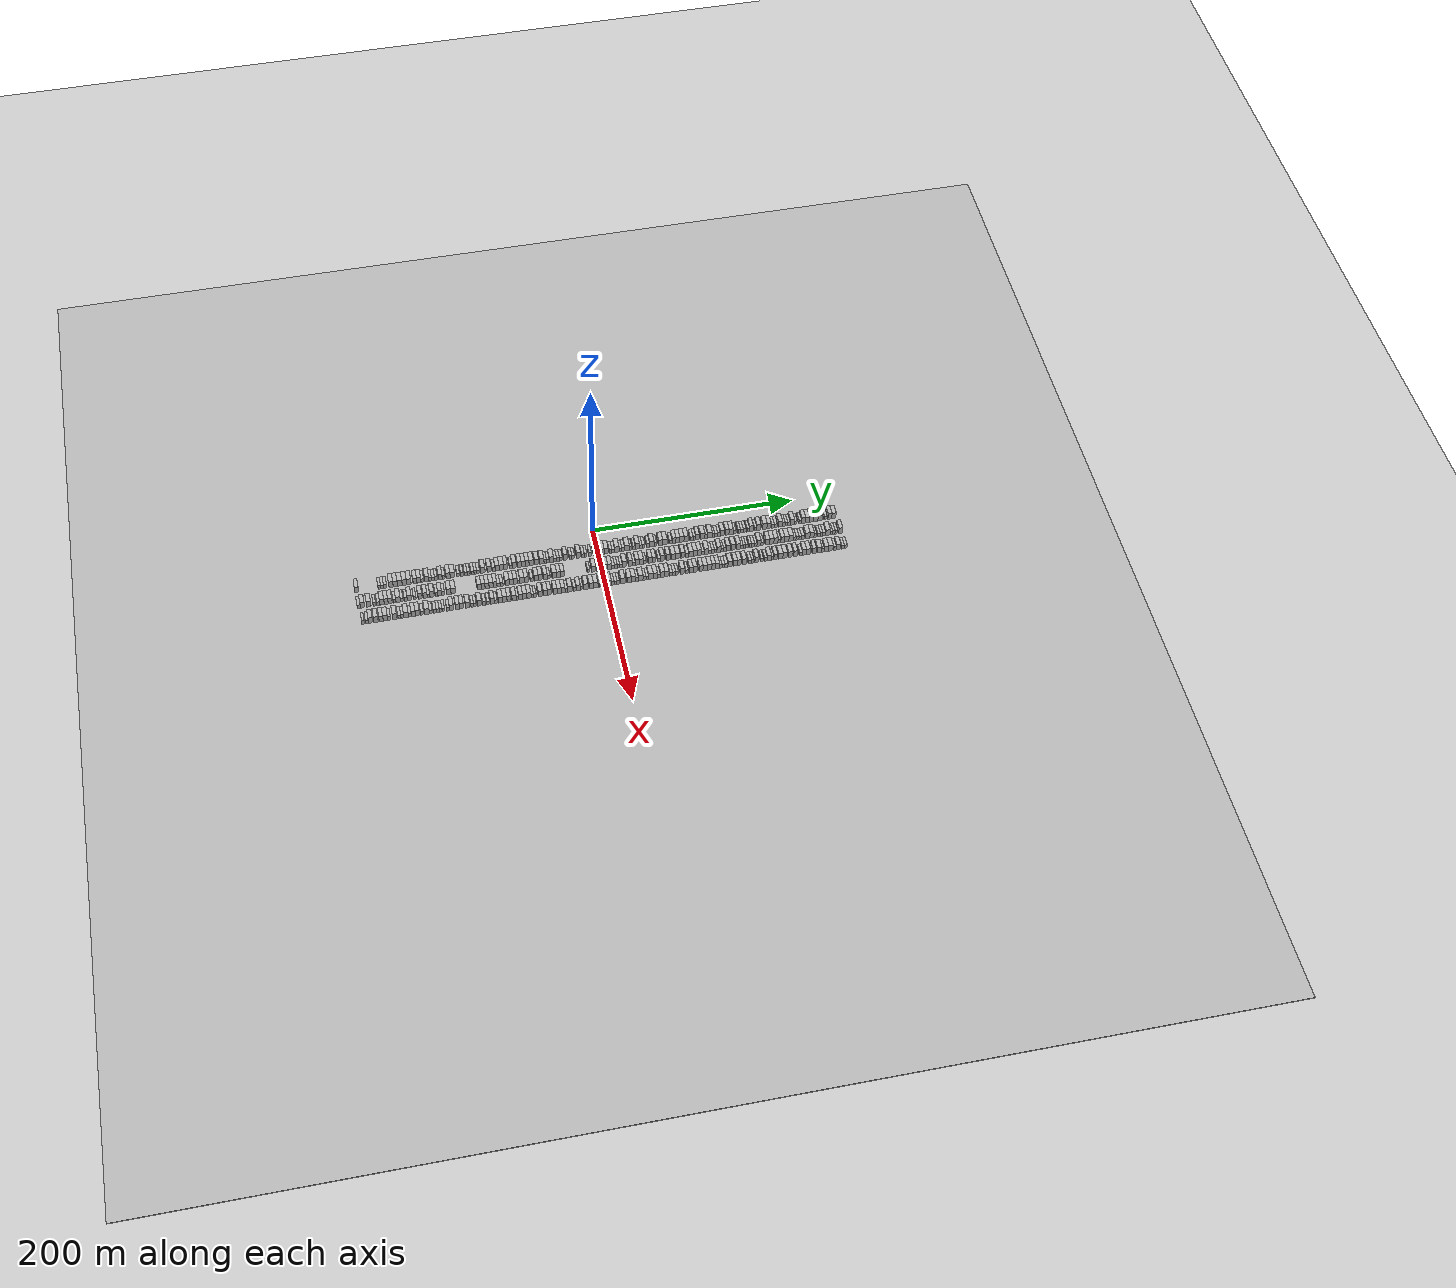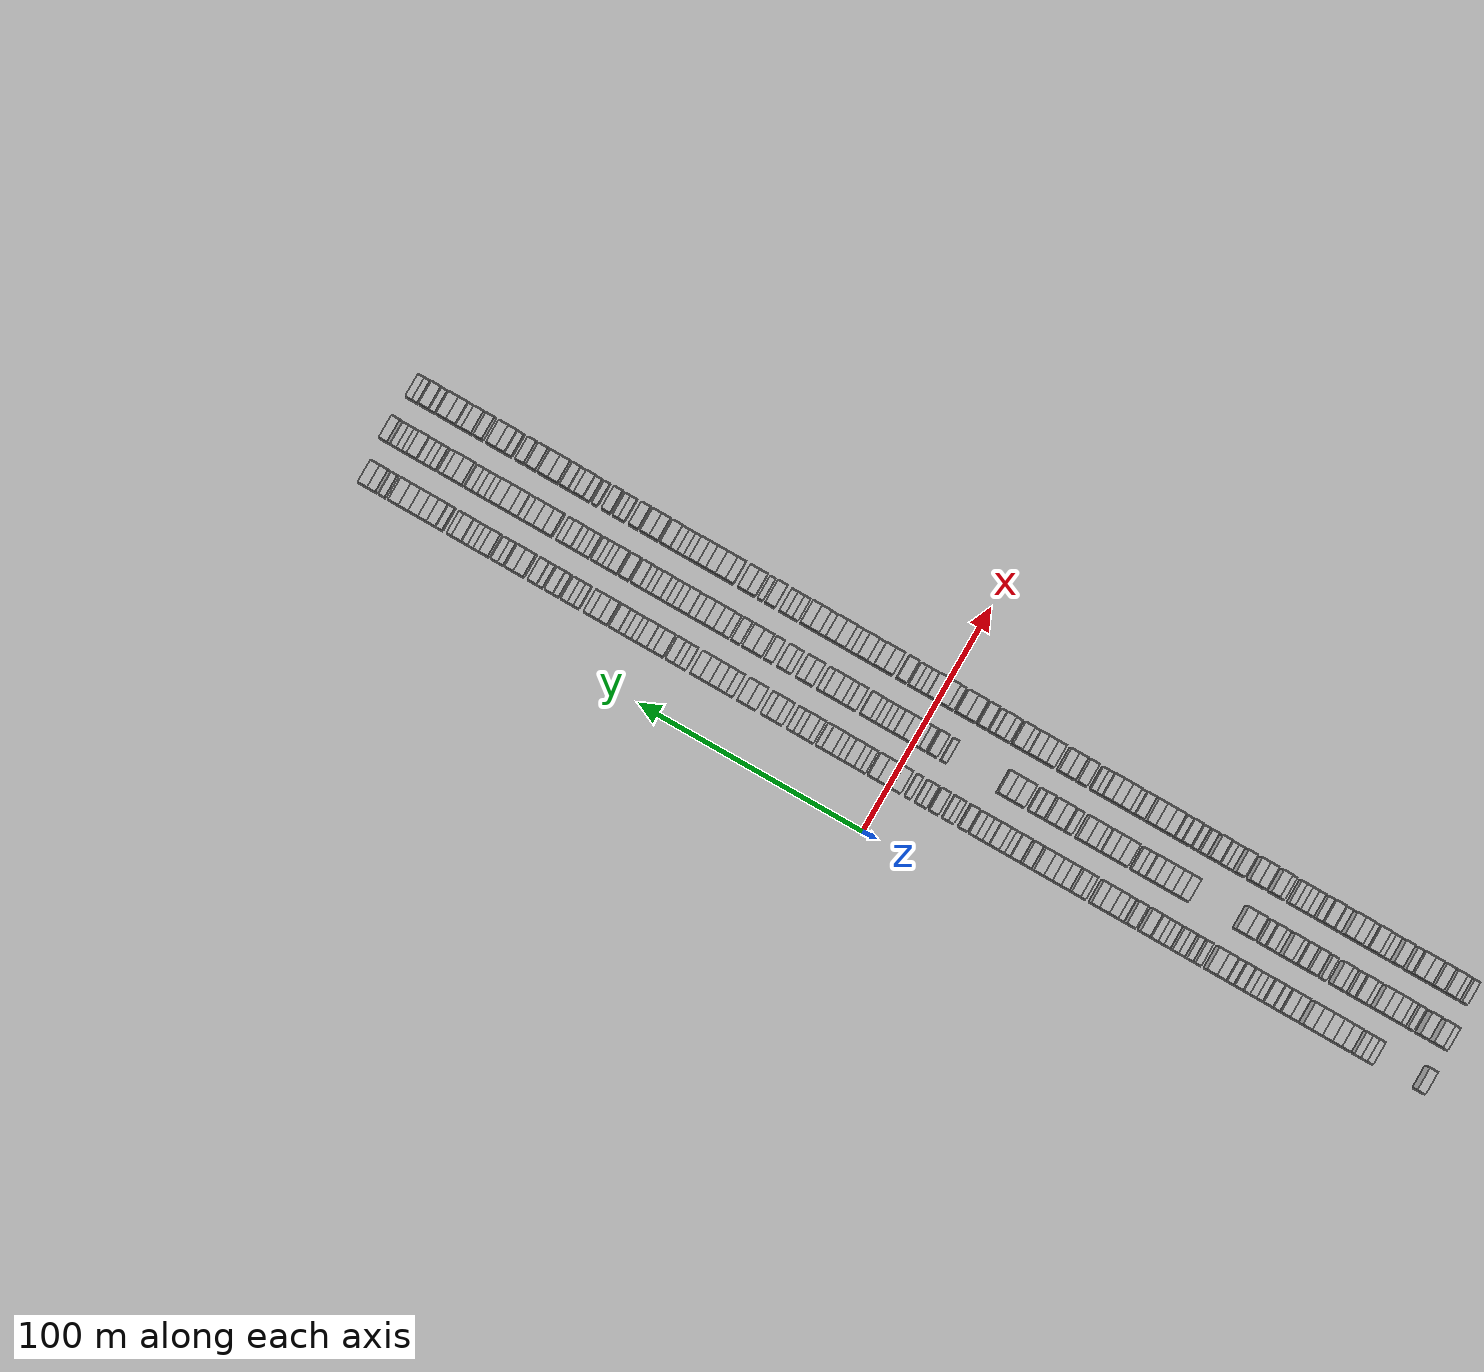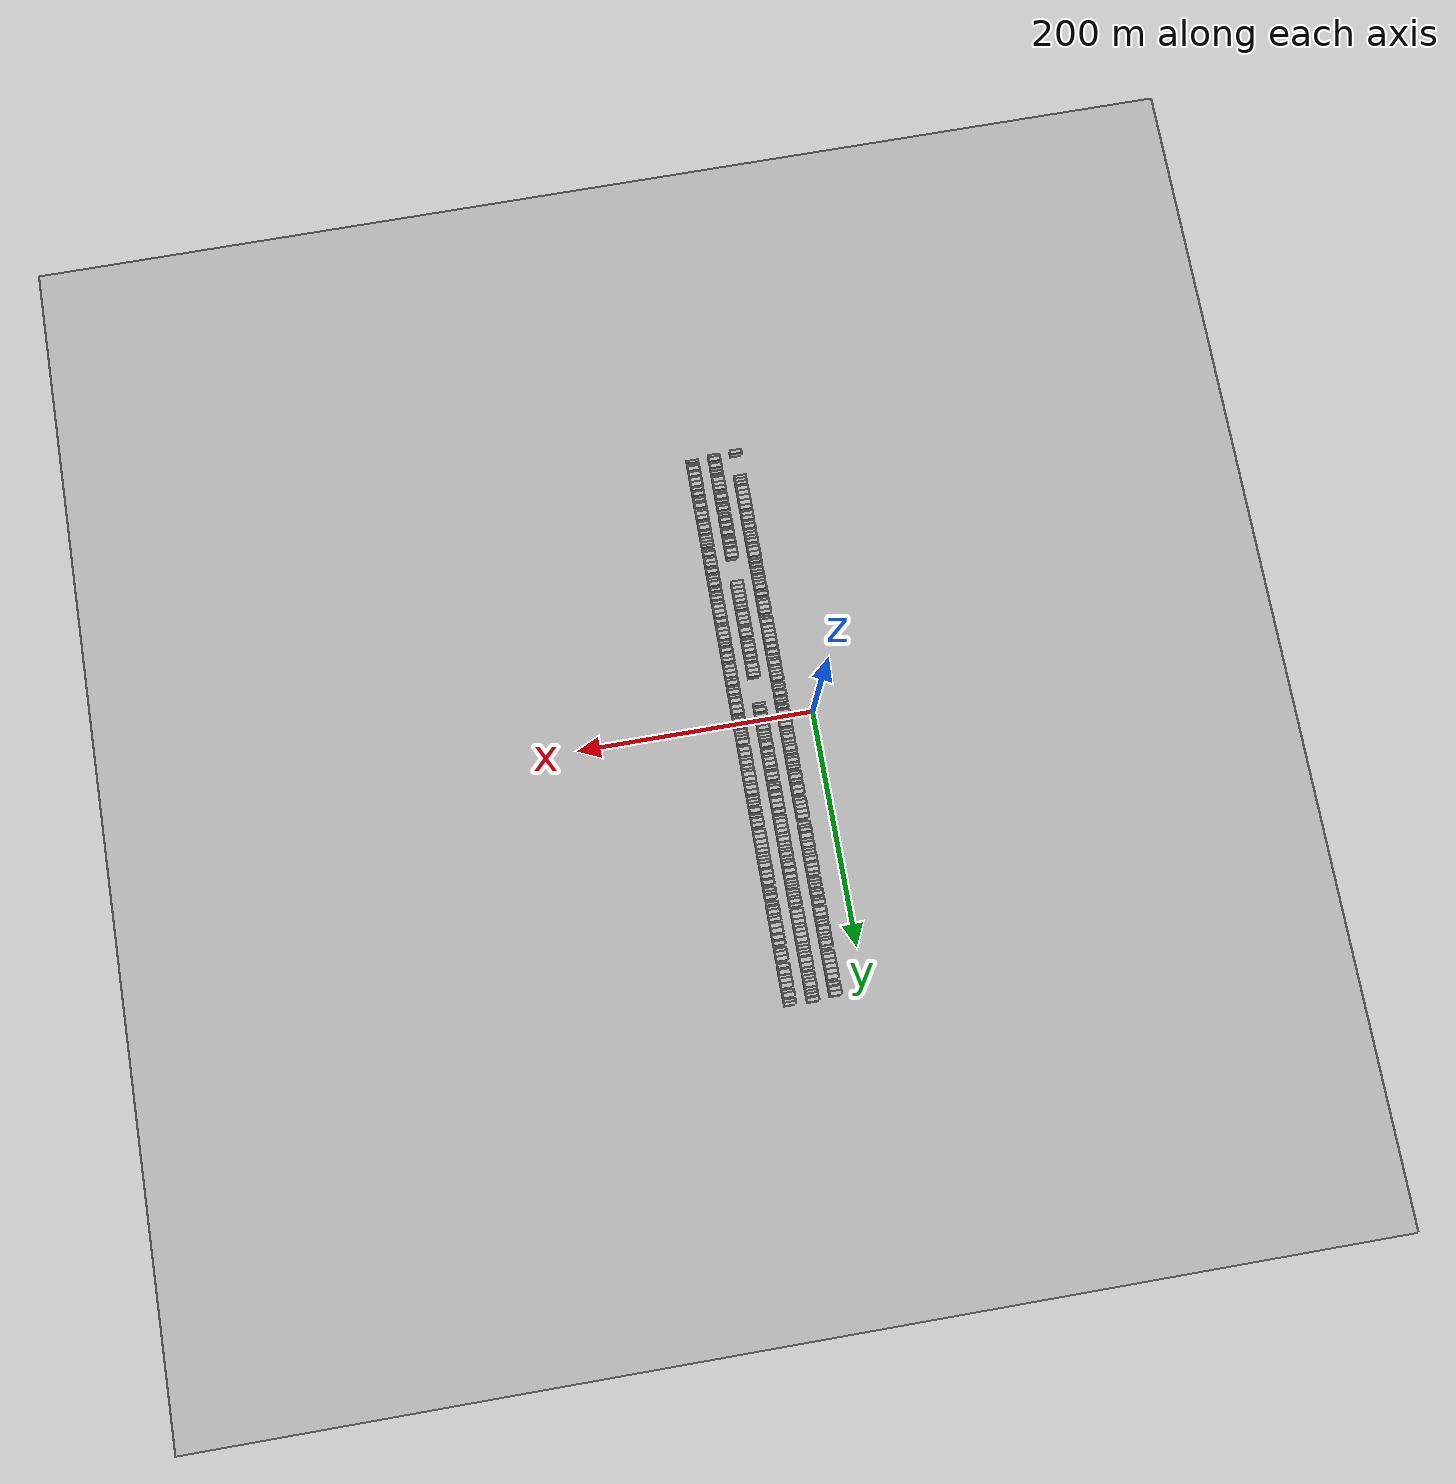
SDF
<?xml version="1.0" encoding="utf-8"?>

<sdf version="1.6">

   <world name="default">

      <gui fullscreen="0">

         <camera name="user_camera">

            <pose>-15 0 4.57585 0 0 0</pose>

            <view_controller>orbit</view_controller>

         </camera>

      </gui>

      <scene>

         <sky>

           <clouds>

             <speed>12</speed>

           </clouds>

         </sky>

         <ambient>0.4 0.4 0.4 1</ambient>

         <background>0.7 0.7 0.7 1</background>

         <shadows>1</shadows>

      </scene>

      <gravity>0 0 -9.8066</gravity>

      <magnetic_field>6e-06 2.3e-05 -4.2e-05</magnetic_field>

      <physics default="0" name="default_physics" type="ode">

         <ode>

            <solver>

               <type>quick</type>

               <iters>10</iters>

               <sor>1.0</sor>

               <use_dynamic_moi_rescaling>0</use_dynamic_moi_rescaling>

            </solver>

            <constraints>

               <cfm>0</cfm>

               <erp>0.2</erp>

               <contact_max_correcting_vel>100</contact_max_correcting_vel>

               <contact_surface_layer>0.001</contact_surface_layer>

            </constraints>

         </ode>

         <max_step_size>0.004</max_step_size>

         <real_time_factor>1</real_time_factor>

         <real_time_update_rate>250</real_time_update_rate>

      </physics>

      <light name="sun" type="directional">

         <cast_shadows>1</cast_shadows>

         <pose>0 0 10 0 0 0</pose>

         <diffuse>0.8 0.8 0.8 1</diffuse>

         <specular>0.2 0.2 0.2 1</specular>

         <attenuation>

            <range>1000</range>

            <constant>0.9</constant>

            <linear>0.01</linear>

            <quadratic>0.001</quadratic>

         </attenuation>

         <direction>-0.5 0.1 -0.9</direction>

      </light>

      <include>

         <name>ground_plane_1</name>

         <uri>model://HANNAS_ground_plane</uri>

         <pose>0 0 0  0 0 0</pose>

      </include>

      <include>

         <name>ground_plane_2</name>

         <uri>model://HANNAS_ground_plane</uri>

         <pose>100 0 0  0 0 0</pose>

      </include>

      <model name="building_1">

         <static>1</static>

         <pose frame="">25.0000 -234.1996 0 0.000000 0.000000 0.000000</pose>

         <link name="link">

            <pose frame="">0 0 4.50 0 0 0</pose>

            <collision name="collision">

               <geometry>

                  <box>

                     <size>10.0000 3.6008 9.0000</size>

                  </box>

               </geometry>

               <max_contacts>10</max_contacts>

               <surface>

                  <contact>

                     <ode/>

                  </contact>

                  <bounce/>

                  <friction>

                     <torsional>

                        <ode/>

                     </torsional>

                     <ode/>

                  </friction>

               </surface>

            </collision>

            <visual name="visual">

               <cast_shadows>0</cast_shadows>

               <geometry>

                  <box>

                     <size>10.0000 3.6008 9.0000</size>

                  </box>

               </geometry>

               <material>

                  <script>

                     <uri>model://HANNAS_wall/materials/scripts</uri>

                     <uri>model://HANNAS_wall/materials/textures</uri>

                     <name>vrc/HANNAS_wall</name>

                  </script>

               </material>

            </visual>

            <self_collide>0</self_collide>

            <enable_wind>0</enable_wind>

            <kinematic>0</kinematic>

         </link>

      </model>

      <model name="building_2">

         <static>1</static>

         <pose frame="">25.0000 -212.4626 0 0.000000 0.000000 0.000000</pose>

         <link name="link">

            <pose frame="">0 0 3.00 0 0 0</pose>

            <collision name="collision">

               <geometry>

                  <box>

                     <size>10.0000 2.6244 6.0000</size>

                  </box>

               </geometry>

               <max_contacts>10</max_contacts>

               <surface>

                  <contact>

                     <ode/>

                  </contact>

                  <bounce/>

                  <friction>

                     <torsional>

                        <ode/>

                     </torsional>

                     <ode/>

                  </friction>

               </surface>

            </collision>

            <visual name="visual">

               <cast_shadows>0</cast_shadows>

               <geometry>

                  <box>

                     <size>10.0000 2.6244 6.0000</size>

                  </box>

               </geometry>

               <material>

                  <script>

                     <uri>model://HANNAS_wall/materials/scripts</uri>

                     <uri>model://HANNAS_wall/materials/textures</uri>

                     <name>vrc/HANNAS_wall</name>

                  </script>

               </material>

            </visual>

            <self_collide>0</self_collide>

            <enable_wind>0</enable_wind>

            <kinematic>0</kinematic>

         </link>

      </model>

      <model name="building_3">

         <static>1</static>

         <pose frame="">25.0000 -209.7296 0 0.000000 0.000000 0.000000</pose>

         <link name="link">

            <pose frame="">0 0 3.00 0 0 0</pose>

            <collision name="collision">

               <geometry>

                  <box>

                     <size>10.0000 2.8417 6.0000</size>

                  </box>

               </geometry>

               <max_contacts>10</max_contacts>

               <surface>

                  <contact>

                     <ode/>

                  </contact>

                  <bounce/>

                  <friction>

                     <torsional>

                        <ode/>

                     </torsional>

                     <ode/>

                  </friction>

               </surface>

            </collision>

            <visual name="visual">

               <cast_shadows>0</cast_shadows>

               <geometry>

                  <box>

                     <size>10.0000 2.8417 6.0000</size>

                  </box>

               </geometry>

               <material>

                  <script>

                     <uri>model://HANNAS_wall/materials/scripts</uri>

                     <uri>model://HANNAS_wall/materials/textures</uri>

                     <name>vrc/HANNAS_wall</name>

                  </script>

               </material>

            </visual>

            <self_collide>0</self_collide>

            <enable_wind>0</enable_wind>

            <kinematic>0</kinematic>

         </link>

      </model>

      <model name="building_4">

         <static>1</static>

         <pose frame="">25.0000 -206.8350 0 0.000000 0.000000 0.000000</pose>

         <link name="link">

            <pose frame="">0 0 3.00 0 0 0</pose>

            <collision name="collision">

               <geometry>

                  <box>

                     <size>10.0000 2.9476 6.0000</size>

                  </box>

               </geometry>

               <max_contacts>10</max_contacts>

               <surface>

                  <contact>

                     <ode/>

                  </contact>

                  <bounce/>

                  <friction>

                     <torsional>

                        <ode/>

                     </torsional>

                     <ode/>

                  </friction>

               </surface>

            </collision>

            <visual name="visual">

               <cast_shadows>0</cast_shadows>

               <geometry>

                  <box>

                     <size>10.0000 2.9476 6.0000</size>

                  </box>

               </geometry>

               <material>

                  <script>

                     <uri>model://HANNAS_wall/materials/scripts</uri>

                     <uri>model://HANNAS_wall/materials/textures</uri>

                     <name>vrc/HANNAS_wall</name>

                  </script>

               </material>

            </visual>

            <self_collide>0</self_collide>

            <enable_wind>0</enable_wind>

            <kinematic>0</kinematic>

         </link>

      </model>

      <model name="building_5">

         <static>1</static>

         <pose frame="">25.0000 -201.3262 0 0.000000 0.000000 0.000000</pose>

         <link name="link">

            <pose frame="">0 0 4.50 0 0 0</pose>

            <collision name="collision">

               <geometry>

                  <box>

                     <size>10.0000 4.0698 9.0000</size>

                  </box>

               </geometry>

               <max_contacts>10</max_contacts>

               <surface>

                  <contact>

                     <ode/>

                  </contact>

                  <bounce/>

                  <friction>

                     <torsional>

                        <ode/>

                     </torsional>

                     <ode/>

                  </friction>

               </surface>

            </collision>

            <visual name="visual">

               <cast_shadows>0</cast_shadows>

               <geometry>

                  <box>

                     <size>10.0000 4.0698 9.0000</size>

                  </box>

               </geometry>

               <material>

                  <script>

                     <uri>model://HANNAS_wall/materials/scripts</uri>

                     <uri>model://HANNAS_wall/materials/textures</uri>

                     <name>vrc/HANNAS_wall</name>

                  </script>

               </material>

            </visual>

            <self_collide>0</self_collide>

            <enable_wind>0</enable_wind>

            <kinematic>0</kinematic>

         </link>

      </model>

      <model name="building_6">

         <static>1</static>

         <pose frame="">25.0000 -197.2002 0 0.000000 0.000000 0.000000</pose>

         <link name="link">

            <pose frame="">0 0 4.50 0 0 0</pose>

            <collision name="collision">

               <geometry>

                  <box>

                     <size>10.0000 4.1822 9.0000</size>

                  </box>

               </geometry>

               <max_contacts>10</max_contacts>

               <surface>

                  <contact>

                     <ode/>

                  </contact>

                  <bounce/>

                  <friction>

                     <torsional>

                        <ode/>

                     </torsional>

                     <ode/>

                  </friction>

               </surface>

            </collision>

            <visual name="visual">

               <cast_shadows>0</cast_shadows>

               <geometry>

                  <box>

                     <size>10.0000 4.1822 9.0000</size>

                  </box>

               </geometry>

               <material>

                  <script>

                     <uri>model://HANNAS_wall/materials/scripts</uri>

                     <uri>model://HANNAS_wall/materials/textures</uri>

                     <name>vrc/HANNAS_wall</name>

                  </script>

               </material>

            </visual>

            <self_collide>0</self_collide>

            <enable_wind>0</enable_wind>

            <kinematic>0</kinematic>

         </link>

      </model>

      <model name="building_7">

         <static>1</static>

         <pose frame="">25.0000 -192.8807 0 0.000000 0.000000 0.000000</pose>

         <link name="link">

            <pose frame="">0 0 4.50 0 0 0</pose>

            <collision name="collision">

               <geometry>

                  <box>

                     <size>10.0000 4.4569 9.0000</size>

                  </box>

               </geometry>

               <max_contacts>10</max_contacts>

               <surface>

                  <contact>

                     <ode/>

                  </contact>

                  <bounce/>

                  <friction>

                     <torsional>

                        <ode/>

                     </torsional>

                     <ode/>

                  </friction>

               </surface>

            </collision>

            <visual name="visual">

               <cast_shadows>0</cast_shadows>

               <geometry>

                  <box>

                     <size>10.0000 4.4569 9.0000</size>

                  </box>

               </geometry>

               <material>

                  <script>

                     <uri>model://HANNAS_wall/materials/scripts</uri>

                     <uri>model://HANNAS_wall/materials/textures</uri>

                     <name>vrc/HANNAS_wall</name>

                  </script>

               </material>

            </visual>

            <self_collide>0</self_collide>

            <enable_wind>0</enable_wind>

            <kinematic>0</kinematic>

         </link>

      </model>

      <model name="building_8">

         <static>1</static>

         <pose frame="">25.0000 -188.4448 0 0.000000 0.000000 0.000000</pose>

         <link name="link">

            <pose frame="">0 0 4.50 0 0 0</pose>

            <collision name="collision">

               <geometry>

                  <box>

                     <size>10.0000 4.4149 9.0000</size>

                  </box>

               </geometry>

               <max_contacts>10</max_contacts>

               <surface>

                  <contact>

                     <ode/>

                  </contact>

                  <bounce/>

                  <friction>

                     <torsional>

                        <ode/>

                     </torsional>

                     <ode/>

                  </friction>

               </surface>

            </collision>

            <visual name="visual">

               <cast_shadows>0</cast_shadows>

               <geometry>

                  <box>

                     <size>10.0000 4.4149 9.0000</size>

                  </box>

               </geometry>

               <material>

                  <script>

                     <uri>model://HANNAS_wall/materials/scripts</uri>

                     <uri>model://HANNAS_wall/materials/textures</uri>

                     <name>vrc/HANNAS_wall</name>

                  </script>

               </material>

            </visual>

            <self_collide>0</self_collide>

            <enable_wind>0</enable_wind>

            <kinematic>0</kinematic>

         </link>

      </model>

      <model name="building_9">

         <static>1</static>

         <pose frame="">25.0000 -184.1795 0 0.000000 0.000000 0.000000</pose>

         <link name="link">

            <pose frame="">0 0 4.50 0 0 0</pose>

            <collision name="collision">

               <geometry>

                  <box>

                     <size>10.0000 4.1157 9.0000</size>

                  </box>

               </geometry>

               <max_contacts>10</max_contacts>

               <surface>

                  <contact>

                     <ode/>

                  </contact>

                  <bounce/>

                  <friction>

                     <torsional>

                        <ode/>

                     </torsional>

                     <ode/>

                  </friction>

               </surface>

            </collision>

            <visual name="visual">

               <cast_shadows>0</cast_shadows>

               <geometry>

                  <box>

                     <size>10.0000 4.1157 9.0000</size>

                  </box>

               </geometry>

               <material>

                  <script>

                     <uri>model://HANNAS_wall/materials/scripts</uri>

                     <uri>model://HANNAS_wall/materials/textures</uri>

                     <name>vrc/HANNAS_wall</name>

                  </script>

               </material>

            </visual>

            <self_collide>0</self_collide>

            <enable_wind>0</enable_wind>

            <kinematic>0</kinematic>

         </link>

      </model>

      <model name="building_10">

         <static>1</static>

         <pose frame="">25.0000 -178.3188 0 0.000000 0.000000 0.000000</pose>

         <link name="link">

            <pose frame="">0 0 4.50 0 0 0</pose>

            <collision name="collision">

               <geometry>

                  <box>

                     <size>10.0000 3.6058 9.0000</size>

                  </box>

               </geometry>

               <max_contacts>10</max_contacts>

               <surface>

                  <contact>

                     <ode/>

                  </contact>

                  <bounce/>

                  <friction>

                     <torsional>

                        <ode/>

                     </torsional>

                     <ode/>

                  </friction>

               </surface>

            </collision>

            <visual name="visual">

               <cast_shadows>0</cast_shadows>

               <geometry>

                  <box>

                     <size>10.0000 3.6058 9.0000</size>

                  </box>

               </geometry>

               <material>

                  <script>

                     <uri>model://HANNAS_wall/materials/scripts</uri>

                     <uri>model://HANNAS_wall/materials/textures</uri>

                     <name>vrc/HANNAS_wall</name>

                  </script>

               </material>

            </visual>

            <self_collide>0</self_collide>

            <enable_wind>0</enable_wind>

            <kinematic>0</kinematic>

         </link>

      </model>

      <model name="building_11">

         <static>1</static>

         <pose frame="">25.0000 -174.5327 0 0.000000 0.000000 0.000000</pose>

         <link name="link">

            <pose frame="">0 0 4.50 0 0 0</pose>

            <collision name="collision">

               <geometry>

                  <box>

                     <size>10.0000 3.9665 9.0000</size>

                  </box>

               </geometry>

               <max_contacts>10</max_contacts>

               <surface>

                  <contact>

                     <ode/>

                  </contact>

                  <bounce/>

                  <friction>

                     <torsional>

                        <ode/>

                     </torsional>

                     <ode/>

                  </friction>

               </surface>

            </collision>

            <visual name="visual">

               <cast_shadows>0</cast_shadows>

               <geometry>

                  <box>

                     <size>10.0000 3.9665 9.0000</size>

                  </box>

               </geometry>

               <material>

                  <script>

                     <uri>model://HANNAS_wall/materials/scripts</uri>

                     <uri>model://HANNAS_wall/materials/textures</uri>

                     <name>vrc/HANNAS_wall</name>

                  </script>

               </material>

            </visual>

            <self_collide>0</self_collide>

            <enable_wind>0</enable_wind>

            <kinematic>0</kinematic>

         </link>

      </model>

      <model name="building_12">

         <static>1</static>

         <pose frame="">25.0000 -171.1849 0 0.000000 0.000000 0.000000</pose>

         <link name="link">

            <pose frame="">0 0 3.00 0 0 0</pose>

            <collision name="collision">

               <geometry>

                  <box>

                     <size>10.0000 2.7291 6.0000</size>

                  </box>

               </geometry>

               <max_contacts>10</max_contacts>

               <surface>

                  <contact>

                     <ode/>

                  </contact>

                  <bounce/>

                  <friction>

                     <torsional>

                        <ode/>

                     </torsional>

                     <ode/>

                  </friction>

               </surface>

            </collision>

            <visual name="visual">

               <cast_shadows>0</cast_shadows>

               <geometry>

                  <box>

                     <size>10.0000 2.7291 6.0000</size>

                  </box>

               </geometry>

               <material>

                  <script>

                     <uri>model://HANNAS_wall/materials/scripts</uri>

                     <uri>model://HANNAS_wall/materials/textures</uri>

                     <name>vrc/HANNAS_wall</name>

                  </script>

               </material>

            </visual>

            <self_collide>0</self_collide>

            <enable_wind>0</enable_wind>

            <kinematic>0</kinematic>

         </link>

      </model>

      <model name="building_13">

         <static>1</static>

         <pose frame="">25.0000 -166.8617 0 0.000000 0.000000 0.000000</pose>

         <link name="link">

            <pose frame="">0 0 4.50 0 0 0</pose>

            <collision name="collision">

               <geometry>

                  <box>

                     <size>10.0000 3.9173 9.0000</size>

                  </box>

               </geometry>

               <max_contacts>10</max_contacts>

               <surface>

                  <contact>

                     <ode/>

                  </contact>

                  <bounce/>

                  <friction>

                     <torsional>

                        <ode/>

                     </torsional>

                     <ode/>

                  </friction>

               </surface>

            </collision>

            <visual name="visual">

               <cast_shadows>0</cast_shadows>

               <geometry>

                  <box>

                     <size>10.0000 3.9173 9.0000</size>

                  </box>

               </geometry>

               <material>

                  <script>

                     <uri>model://HANNAS_wall/materials/scripts</uri>

                     <uri>model://HANNAS_wall/materials/textures</uri>

                     <name>vrc/HANNAS_wall</name>

                  </script>

               </material>

            </visual>

            <self_collide>0</self_collide>

            <enable_wind>0</enable_wind>

            <kinematic>0</kinematic>

         </link>

      </model>

      <model name="building_14">

         <static>1</static>

         <pose frame="">25.0000 -163.6050 0 0.000000 0.000000 0.000000</pose>

         <link name="link">

            <pose frame="">0 0 3.00 0 0 0</pose>

            <collision name="collision">

               <geometry>

                  <box>

                     <size>10.0000 2.5963 6.0000</size>

                  </box>

               </geometry>

               <max_contacts>10</max_contacts>

               <surface>

                  <contact>

                     <ode/>

                  </contact>

                  <bounce/>

                  <friction>

                     <torsional>

                        <ode/>

                     </torsional>

                     <ode/>

                  </friction>

               </surface>

            </collision>

            <visual name="visual">

               <cast_shadows>0</cast_shadows>

               <geometry>

                  <box>

                     <size>10.0000 2.5963 6.0000</size>

                  </box>

               </geometry>

               <material>

                  <script>

                     <uri>model://HANNAS_wall/materials/scripts</uri>

                     <uri>model://HANNAS_wall/materials/textures</uri>

                     <name>vrc/HANNAS_wall</name>

                  </script>

               </material>

            </visual>

            <self_collide>0</self_collide>

            <enable_wind>0</enable_wind>

            <kinematic>0</kinematic>

         </link>

      </model>

      <model name="building_15">

         <static>1</static>

         <pose frame="">25.0000 -160.8291 0 0.000000 0.000000 0.000000</pose>

         <link name="link">

            <pose frame="">0 0 3.00 0 0 0</pose>

            <collision name="collision">

               <geometry>

                  <box>

                     <size>10.0000 2.9556 6.0000</size>

                  </box>

               </geometry>

               <max_contacts>10</max_contacts>

               <surface>

                  <contact>

                     <ode/>

                  </contact>

                  <bounce/>

                  <friction>

                     <torsional>

                        <ode/>

                     </torsional>

                     <ode/>

                  </friction>

               </surface>

            </collision>

            <visual name="visual">

               <cast_shadows>0</cast_shadows>

               <geometry>

                  <box>

                     <size>10.0000 2.9556 6.0000</size>

                  </box>

               </geometry>

               <material>

                  <script>

                     <uri>model://HANNAS_wall/materials/scripts</uri>

                     <uri>model://HANNAS_wall/materials/textures</uri>

                     <name>vrc/HANNAS_wall</name>

                  </script>

               </material>

            </visual>

            <self_collide>0</self_collide>

            <enable_wind>0</enable_wind>

            <kinematic>0</kinematic>

         </link>

      </model>

      <model name="building_16">

         <static>1</static>

         <pose frame="">25.0000 -158.0564 0 0.000000 0.000000 0.000000</pose>

         <link name="link">

            <pose frame="">0 0 3.00 0 0 0</pose>

            <collision name="collision">

               <geometry>

                  <box>

                     <size>10.0000 2.5897 6.0000</size>

                  </box>

               </geometry>

               <max_contacts>10</max_contacts>

               <surface>

                  <contact>

                     <ode/>

                  </contact>

                  <bounce/>

                  <friction>

                     <torsional>

                        <ode/>

                     </torsional>

                     <ode/>

                  </friction>

               </surface>

            </collision>

            <visual name="visual">

               <cast_shadows>0</cast_shadows>

               <geometry>

                  <box>

                     <size>10.0000 2.5897 6.0000</size>

                  </box>

               </geometry>

               <material>

                  <script>

                     <uri>model://HANNAS_wall/materials/scripts</uri>

                     <uri>model://HANNAS_wall/materials/textures</uri>

                     <name>vrc/HANNAS_wall</name>

                  </script>

               </material>

            </visual>

            <self_collide>0</self_collide>

            <enable_wind>0</enable_wind>

            <kinematic>0</kinematic>

         </link>

      </model>

      <model name="building_17">

         <static>1</static>

         <pose frame="">25.0000 -153.9333 0 0.000000 0.000000 0.000000</pose>

         <link name="link">

            <pose frame="">0 0 4.50 0 0 0</pose>

            <collision name="collision">

               <geometry>

                  <box>

                     <size>10.0000 3.6567 9.0000</size>

                  </box>

               </geometry>

               <max_contacts>10</max_contacts>

               <surface>

                  <contact>

                     <ode/>

                  </contact>

                  <bounce/>

                  <friction>

                     <torsional>

                        <ode/>

                     </torsional>

                     <ode/>

                  </friction>

               </surface>

            </collision>

            <visual name="visual">

               <cast_shadows>0</cast_shadows>

               <geometry>

                  <box>

                     <size>10.0000 3.6567 9.0000</size>

                  </box>

               </geometry>

               <material>

                  <script>

                     <uri>model://HANNAS_wall/materials/scripts</uri>

                     <uri>model://HANNAS_wall/materials/textures</uri>

                     <name>vrc/HANNAS_wall</name>

                  </script>

               </material>

            </visual>

            <self_collide>0</self_collide>

            <enable_wind>0</enable_wind>

            <kinematic>0</kinematic>

         </link>

      </model>

      <model name="building_18">

         <static>1</static>

         <pose frame="">25.0000 -150.7029 0 0.000000 0.000000 0.000000</pose>

         <link name="link">

            <pose frame="">0 0 3.00 0 0 0</pose>

            <collision name="collision">

               <geometry>

                  <box>

                     <size>10.0000 2.8040 6.0000</size>

                  </box>

               </geometry>

               <max_contacts>10</max_contacts>

               <surface>

                  <contact>

                     <ode/>

                  </contact>

                  <bounce/>

                  <friction>

                     <torsional>

                        <ode/>

                     </torsional>

                     <ode/>

                  </friction>

               </surface>

            </collision>

            <visual name="visual">

               <cast_shadows>0</cast_shadows>

               <geometry>

                  <box>

                     <size>10.0000 2.8040 6.0000</size>

                  </box>

               </geometry>

               <material>

                  <script>

                     <uri>model://HANNAS_wall/materials/scripts</uri>

                     <uri>model://HANNAS_wall/materials/textures</uri>

                     <name>vrc/HANNAS_wall</name>

                  </script>

               </material>

            </visual>

            <self_collide>0</self_collide>

            <enable_wind>0</enable_wind>

            <kinematic>0</kinematic>

         </link>

      </model>

      <model name="building_19">

         <static>1</static>

         <pose frame="">25.0000 -146.3137 0 0.000000 0.000000 0.000000</pose>

         <link name="link">

            <pose frame="">0 0 4.50 0 0 0</pose>

            <collision name="collision">

               <geometry>

                  <box>

                     <size>10.0000 3.9744 9.0000</size>

                  </box>

               </geometry>

               <max_contacts>10</max_contacts>

               <surface>

                  <contact>

                     <ode/>

                  </contact>

                  <bounce/>

                  <friction>

                     <torsional>

                        <ode/>

                     </torsional>

                     <ode/>

                  </friction>

               </surface>

            </collision>

            <visual name="visual">

               <cast_shadows>0</cast_shadows>

               <geometry>

                  <box>

                     <size>10.0000 3.9744 9.0000</size>

                  </box>

               </geometry>

               <material>

                  <script>

                     <uri>model://HANNAS_wall/materials/scripts</uri>

                     <uri>model://HANNAS_wall/materials/textures</uri>

                     <name>vrc/HANNAS_wall</name>

                  </script>

               </material>

            </visual>

            <self_collide>0</self_collide>

            <enable_wind>0</enable_wind>

            <kinematic>0</kinematic>

         </link>

      </model>

      <model name="building_20">

         <static>1</static>

         <pose frame="">25.0000 -142.0945 0 0.000000 0.000000 0.000000</pose>

         <link name="link">

            <pose frame="">0 0 4.50 0 0 0</pose>

            <collision name="collision">

               <geometry>

                  <box>

                     <size>10.0000 4.4641 9.0000</size>

                  </box>

               </geometry>

               <max_contacts>10</max_contacts>

               <surface>

                  <contact>

                     <ode/>

                  </contact>

                  <bounce/>

                  <friction>

                     <torsional>

                        <ode/>

                     </torsional>

                     <ode/>

                  </friction>

               </surface>

            </collision>

            <visual name="visual">

               <cast_shadows>0</cast_shadows>

               <geometry>

                  <box>

                     <size>10.0000 4.4641 9.0000</size>

                  </box>

               </geometry>

               <material>

                  <script>

                     <uri>model://HANNAS_wall/materials/scripts</uri>

                     <uri>model://HANNAS_wall/materials/textures</uri>

                     <name>vrc/HANNAS_wall</name>

                  </script>

               </material>

            </visual>

            <self_collide>0</self_collide>

            <enable_wind>0</enable_wind>

            <kinematic>0</kinematic>

         </link>

      </model>

      <model name="building_21">

         <static>1</static>

         <pose frame="">25.0000 -136.5573 0 0.000000 0.000000 0.000000</pose>

         <link name="link">

            <pose frame="">0 0 3.00 0 0 0</pose>

            <collision name="collision">

               <geometry>

                  <box>

                     <size>10.0000 2.6102 6.0000</size>

                  </box>

               </geometry>

               <max_contacts>10</max_contacts>

               <surface>

                  <contact>

                     <ode/>

                  </contact>

                  <bounce/>

                  <friction>

                     <torsional>

                        <ode/>

                     </torsional>

                     <ode/>

                  </friction>

               </surface>

            </collision>

            <visual name="visual">

               <cast_shadows>0</cast_shadows>

               <geometry>

                  <box>

                     <size>10.0000 2.6102 6.0000</size>

                  </box>

               </geometry>

               <material>

                  <script>

                     <uri>model://HANNAS_wall/materials/scripts</uri>

                     <uri>model://HANNAS_wall/materials/textures</uri>

                     <name>vrc/HANNAS_wall</name>

                  </script>

               </material>

            </visual>

            <self_collide>0</self_collide>

            <enable_wind>0</enable_wind>

            <kinematic>0</kinematic>

         </link>

      </model>

      <model name="building_22">

         <static>1</static>

         <pose frame="">25.0000 -132.9320 0 0.000000 0.000000 0.000000</pose>

         <link name="link">

            <pose frame="">0 0 3.00 0 0 0</pose>

            <collision name="collision">

               <geometry>

                  <box>

                     <size>10.0000 2.6404 6.0000</size>

                  </box>

               </geometry>

               <max_contacts>10</max_contacts>

               <surface>

                  <contact>

                     <ode/>

                  </contact>

                  <bounce/>

                  <friction>

                     <torsional>

                        <ode/>

                     </torsional>

                     <ode/>

                  </friction>

               </surface>

            </collision>

            <visual name="visual">

               <cast_shadows>0</cast_shadows>

               <geometry>

                  <box>

                     <size>10.0000 2.6404 6.0000</size>

                  </box>

               </geometry>

               <material>

                  <script>

                     <uri>model://HANNAS_wall/materials/scripts</uri>

                     <uri>model://HANNAS_wall/materials/textures</uri>

                     <name>vrc/HANNAS_wall</name>

                  </script>

               </material>

            </visual>

            <self_collide>0</self_collide>

            <enable_wind>0</enable_wind>

            <kinematic>0</kinematic>

         </link>

      </model>

      <model name="building_23">

         <static>1</static>

         <pose frame="">25.0000 -129.2268 0 0.000000 0.000000 0.000000</pose>

         <link name="link">

            <pose frame="">0 0 3.00 0 0 0</pose>

            <collision name="collision">

               <geometry>

                  <box>

                     <size>10.0000 2.7701 6.0000</size>

                  </box>

               </geometry>

               <max_contacts>10</max_contacts>

               <surface>

                  <contact>

                     <ode/>

                  </contact>

                  <bounce/>

                  <friction>

                     <torsional>

                        <ode/>

                     </torsional>

                     <ode/>

                  </friction>

               </surface>

            </collision>

            <visual name="visual">

               <cast_shadows>0</cast_shadows>

               <geometry>

                  <box>

                     <size>10.0000 2.7701 6.0000</size>

                  </box>

               </geometry>

               <material>

                  <script>

                     <uri>model://HANNAS_wall/materials/scripts</uri>

                     <uri>model://HANNAS_wall/materials/textures</uri>

                     <name>vrc/HANNAS_wall</name>

                  </script>

               </material>

            </visual>

            <self_collide>0</self_collide>

            <enable_wind>0</enable_wind>

            <kinematic>0</kinematic>

         </link>

      </model>

      <model name="building_24">

         <static>1</static>

         <pose frame="">25.0000 -126.5125 0 0.000000 0.000000 0.000000</pose>

         <link name="link">

            <pose frame="">0 0 3.00 0 0 0</pose>

            <collision name="collision">

               <geometry>

                  <box>

                     <size>10.0000 2.6585 6.0000</size>

                  </box>

               </geometry>

               <max_contacts>10</max_contacts>

               <surface>

                  <contact>

                     <ode/>

                  </contact>

                  <bounce/>

                  <friction>

                     <torsional>

                        <ode/>

                     </torsional>

                     <ode/>

                  </friction>

               </surface>

            </collision>

            <visual name="visual">

               <cast_shadows>0</cast_shadows>

               <geometry>

                  <box>

                     <size>10.0000 2.6585 6.0000</size>

                  </box>

               </geometry>

               <material>

                  <script>

                     <uri>model://HANNAS_wall/materials/scripts</uri>

                     <uri>model://HANNAS_wall/materials/textures</uri>

                     <name>vrc/HANNAS_wall</name>

                  </script>

               </material>

            </visual>

            <self_collide>0</self_collide>

            <enable_wind>0</enable_wind>

            <kinematic>0</kinematic>

         </link>

      </model>

      <model name="building_25">

         <static>1</static>

         <pose frame="">25.0000 -122.7348 0 0.000000 0.000000 0.000000</pose>

         <link name="link">

            <pose frame="">0 0 3.00 0 0 0</pose>

            <collision name="collision">

               <geometry>

                  <box>

                     <size>10.0000 2.8971 6.0000</size>

                  </box>

               </geometry>

               <max_contacts>10</max_contacts>

               <surface>

                  <contact>

                     <ode/>

                  </contact>

                  <bounce/>

                  <friction>

                     <torsional>

                        <ode/>

                     </torsional>

                     <ode/>

                  </friction>

               </surface>

            </collision>

            <visual name="visual">

               <cast_shadows>0</cast_shadows>

               <geometry>

                  <box>

                     <size>10.0000 2.8971 6.0000</size>

                  </box>

               </geometry>

               <material>

                  <script>

                     <uri>model://HANNAS_wall/materials/scripts</uri>

                     <uri>model://HANNAS_wall/materials/textures</uri>

                     <name>vrc/HANNAS_wall</name>

                  </script>

               </material>

            </visual>

            <self_collide>0</self_collide>

            <enable_wind>0</enable_wind>

            <kinematic>0</kinematic>

         </link>

      </model>

      <model name="building_26">

         <static>1</static>

         <pose frame="">25.0000 -120.0177 0 0.000000 0.000000 0.000000</pose>

         <link name="link">

            <pose frame="">0 0 3.00 0 0 0</pose>

            <collision name="collision">

               <geometry>

                  <box>

                     <size>10.0000 2.5370 6.0000</size>

                  </box>

               </geometry>

               <max_contacts>10</max_contacts>

               <surface>

                  <contact>

                     <ode/>

                  </contact>

                  <bounce/>

                  <friction>

                     <torsional>

                        <ode/>

                     </torsional>

                     <ode/>

                  </friction>

               </surface>

            </collision>

            <visual name="visual">

               <cast_shadows>0</cast_shadows>

               <geometry>

                  <box>

                     <size>10.0000 2.5370 6.0000</size>

                  </box>

               </geometry>

               <material>

                  <script>

                     <uri>model://HANNAS_wall/materials/scripts</uri>

                     <uri>model://HANNAS_wall/materials/textures</uri>

                     <name>vrc/HANNAS_wall</name>

                  </script>

               </material>

            </visual>

            <self_collide>0</self_collide>

            <enable_wind>0</enable_wind>

            <kinematic>0</kinematic>

         </link>

      </model>

      <model name="building_27">

         <static>1</static>

         <pose frame="">25.0000 -117.2631 0 0.000000 0.000000 0.000000</pose>

         <link name="link">

            <pose frame="">0 0 3.00 0 0 0</pose>

            <collision name="collision">

               <geometry>

                  <box>

                     <size>10.0000 2.9722 6.0000</size>

                  </box>

               </geometry>

               <max_contacts>10</max_contacts>

               <surface>

                  <contact>

                     <ode/>

                  </contact>

                  <bounce/>

                  <friction>

                     <torsional>

                        <ode/>

                     </torsional>

                     <ode/>

                  </friction>

               </surface>

            </collision>

            <visual name="visual">

               <cast_shadows>0</cast_shadows>

               <geometry>

                  <box>

                     <size>10.0000 2.9722 6.0000</size>

                  </box>

               </geometry>

               <material>

                  <script>

                     <uri>model://HANNAS_wall/materials/scripts</uri>

                     <uri>model://HANNAS_wall/materials/textures</uri>

                     <name>vrc/HANNAS_wall</name>

                  </script>

               </material>

            </visual>

            <self_collide>0</self_collide>

            <enable_wind>0</enable_wind>

            <kinematic>0</kinematic>

         </link>

      </model>

      <model name="building_28">

         <static>1</static>

         <pose frame="">25.0000 -112.6516 0 0.000000 0.000000 0.000000</pose>

         <link name="link">

            <pose frame="">0 0 4.50 0 0 0</pose>

            <collision name="collision">

               <geometry>

                  <box>

                     <size>10.0000 4.2508 9.0000</size>

                  </box>

               </geometry>

               <max_contacts>10</max_contacts>

               <surface>

                  <contact>

                     <ode/>

                  </contact>

                  <bounce/>

                  <friction>

                     <torsional>

                        <ode/>

                     </torsional>

                     <ode/>

                  </friction>

               </surface>

            </collision>

            <visual name="visual">

               <cast_shadows>0</cast_shadows>

               <geometry>

                  <box>

                     <size>10.0000 4.2508 9.0000</size>

                  </box>

               </geometry>

               <material>

                  <script>

                     <uri>model://HANNAS_wall/materials/scripts</uri>

                     <uri>model://HANNAS_wall/materials/textures</uri>

                     <name>vrc/HANNAS_wall</name>

                  </script>

               </material>

            </visual>

            <self_collide>0</self_collide>

            <enable_wind>0</enable_wind>

            <kinematic>0</kinematic>

         </link>

      </model>

      <model name="building_29">

         <static>1</static>

         <pose frame="">25.0000 -106.5607 0 0.000000 0.000000 0.000000</pose>

         <link name="link">

            <pose frame="">0 0 4.50 0 0 0</pose>

            <collision name="collision">

               <geometry>

                  <box>

                     <size>10.0000 3.9310 9.0000</size>

                  </box>

               </geometry>

               <max_contacts>10</max_contacts>

               <surface>

                  <contact>

                     <ode/>

                  </contact>

                  <bounce/>

                  <friction>

                     <torsional>

                        <ode/>

                     </torsional>

                     <ode/>

                  </friction>

               </surface>

            </collision>

            <visual name="visual">

               <cast_shadows>0</cast_shadows>

               <geometry>

                  <box>

                     <size>10.0000 3.9310 9.0000</size>

                  </box>

               </geometry>

               <material>

                  <script>

                     <uri>model://HANNAS_wall/materials/scripts</uri>

                     <uri>model://HANNAS_wall/materials/textures</uri>

                     <name>vrc/HANNAS_wall</name>

                  </script>

               </material>

            </visual>

            <self_collide>0</self_collide>

            <enable_wind>0</enable_wind>

            <kinematic>0</kinematic>

         </link>

      </model>

      <model name="building_30">

         <static>1</static>

         <pose frame="">25.0000 -102.1648 0 0.000000 0.000000 0.000000</pose>

         <link name="link">

            <pose frame="">0 0 3.00 0 0 0</pose>

            <collision name="collision">

               <geometry>

                  <box>

                     <size>10.0000 2.8607 6.0000</size>

                  </box>

               </geometry>

               <max_contacts>10</max_contacts>

               <surface>

                  <contact>

                     <ode/>

                  </contact>

                  <bounce/>

                  <friction>

                     <torsional>

                        <ode/>

                     </torsional>

                     <ode/>

                  </friction>

               </surface>

            </collision>

            <visual name="visual">

               <cast_shadows>0</cast_shadows>

               <geometry>

                  <box>

                     <size>10.0000 2.8607 6.0000</size>

                  </box>

               </geometry>

               <material>

                  <script>

                     <uri>model://HANNAS_wall/materials/scripts</uri>

                     <uri>model://HANNAS_wall/materials/textures</uri>

                     <name>vrc/HANNAS_wall</name>

                  </script>

               </material>

            </visual>

            <self_collide>0</self_collide>

            <enable_wind>0</enable_wind>

            <kinematic>0</kinematic>

         </link>

      </model>

      <model name="building_31">

         <static>1</static>

         <pose frame="">25.0000 -98.7727 0 0.000000 0.000000 0.000000</pose>

         <link name="link">

            <pose frame="">0 0 4.50 0 0 0</pose>

            <collision name="collision">

               <geometry>

                  <box>

                     <size>10.0000 3.9235 9.0000</size>

                  </box>

               </geometry>

               <max_contacts>10</max_contacts>

               <surface>

                  <contact>

                     <ode/>

                  </contact>

                  <bounce/>

                  <friction>

                     <torsional>

                        <ode/>

                     </torsional>

                     <ode/>

                  </friction>

               </surface>

            </collision>

            <visual name="visual">

               <cast_shadows>0</cast_shadows>

               <geometry>

                  <box>

                     <size>10.0000 3.9235 9.0000</size>

                  </box>

               </geometry>

               <material>

                  <script>

                     <uri>model://HANNAS_wall/materials/scripts</uri>

                     <uri>model://HANNAS_wall/materials/textures</uri>

                     <name>vrc/HANNAS_wall</name>

                  </script>

               </material>

            </visual>

            <self_collide>0</self_collide>

            <enable_wind>0</enable_wind>

            <kinematic>0</kinematic>

         </link>

      </model>

      <model name="building_32">

         <static>1</static>

         <pose frame="">25.0000 -94.6060 0 0.000000 0.000000 0.000000</pose>

         <link name="link">

            <pose frame="">0 0 4.50 0 0 0</pose>

            <collision name="collision">

               <geometry>

                  <box>

                     <size>10.0000 4.4098 9.0000</size>

                  </box>

               </geometry>

               <max_contacts>10</max_contacts>

               <surface>

                  <contact>

                     <ode/>

                  </contact>

                  <bounce/>

                  <friction>

                     <torsional>

                        <ode/>

                     </torsional>

                     <ode/>

                  </friction>

               </surface>

            </collision>

            <visual name="visual">

               <cast_shadows>0</cast_shadows>

               <geometry>

                  <box>

                     <size>10.0000 4.4098 9.0000</size>

                  </box>

               </geometry>

               <material>

                  <script>

                     <uri>model://HANNAS_wall/materials/scripts</uri>

                     <uri>model://HANNAS_wall/materials/textures</uri>

                     <name>vrc/HANNAS_wall</name>

                  </script>

               </material>

            </visual>

            <self_collide>0</self_collide>

            <enable_wind>0</enable_wind>

            <kinematic>0</kinematic>

         </link>

      </model>

      <model name="building_33">

         <static>1</static>

         <pose frame="">25.0000 -90.6006 0 0.000000 0.000000 0.000000</pose>

         <link name="link">

            <pose frame="">0 0 4.50 0 0 0</pose>

            <collision name="collision">

               <geometry>

                  <box>

                     <size>10.0000 3.6011 9.0000</size>

                  </box>

               </geometry>

               <max_contacts>10</max_contacts>

               <surface>

                  <contact>

                     <ode/>

                  </contact>

                  <bounce/>

                  <friction>

                     <torsional>

                        <ode/>

                     </torsional>

                     <ode/>

                  </friction>

               </surface>

            </collision>

            <visual name="visual">

               <cast_shadows>0</cast_shadows>

               <geometry>

                  <box>

                     <size>10.0000 3.6011 9.0000</size>

                  </box>

               </geometry>

               <material>

                  <script>

                     <uri>model://HANNAS_wall/materials/scripts</uri>

                     <uri>model://HANNAS_wall/materials/textures</uri>

                     <name>vrc/HANNAS_wall</name>

                  </script>

               </material>

            </visual>

            <self_collide>0</self_collide>

            <enable_wind>0</enable_wind>

            <kinematic>0</kinematic>

         </link>

      </model>

      <model name="building_34">

         <static>1</static>

         <pose frame="">25.0000 -85.4847 0 0.000000 0.000000 0.000000</pose>

         <link name="link">

            <pose frame="">0 0 3.00 0 0 0</pose>

            <collision name="collision">

               <geometry>

                  <box>

                     <size>10.0000 2.6308 6.0000</size>

                  </box>

               </geometry>

               <max_contacts>10</max_contacts>

               <surface>

                  <contact>

                     <ode/>

                  </contact>

                  <bounce/>

                  <friction>

                     <torsional>

                        <ode/>

                     </torsional>

                     <ode/>

                  </friction>

               </surface>

            </collision>

            <visual name="visual">

               <cast_shadows>0</cast_shadows>

               <geometry>

                  <box>

                     <size>10.0000 2.6308 6.0000</size>

                  </box>

               </geometry>

               <material>

                  <script>

                     <uri>model://HANNAS_wall/materials/scripts</uri>

                     <uri>model://HANNAS_wall/materials/textures</uri>

                     <name>vrc/HANNAS_wall</name>

                  </script>

               </material>

            </visual>

            <self_collide>0</self_collide>

            <enable_wind>0</enable_wind>

            <kinematic>0</kinematic>

         </link>

      </model>

      <model name="building_35">

         <static>1</static>

         <pose frame="">25.0000 -82.1748 0 0.000000 0.000000 0.000000</pose>

         <link name="link">

            <pose frame="">0 0 4.50 0 0 0</pose>

            <collision name="collision">

               <geometry>

                  <box>

                     <size>10.0000 3.9889 9.0000</size>

                  </box>

               </geometry>

               <max_contacts>10</max_contacts>

               <surface>

                  <contact>

                     <ode/>

                  </contact>

                  <bounce/>

                  <friction>

                     <torsional>

                        <ode/>

                     </torsional>

                     <ode/>

                  </friction>

               </surface>

            </collision>

            <visual name="visual">

               <cast_shadows>0</cast_shadows>

               <geometry>

                  <box>

                     <size>10.0000 3.9889 9.0000</size>

                  </box>

               </geometry>

               <material>

                  <script>

                     <uri>model://HANNAS_wall/materials/scripts</uri>

                     <uri>model://HANNAS_wall/materials/textures</uri>

                     <name>vrc/HANNAS_wall</name>

                  </script>

               </material>

            </visual>

            <self_collide>0</self_collide>

            <enable_wind>0</enable_wind>

            <kinematic>0</kinematic>

         </link>

      </model>

      <model name="building_36">

         <static>1</static>

         <pose frame="">25.0000 -77.3158 0 0.000000 0.000000 0.000000</pose>

         <link name="link">

            <pose frame="">0 0 4.50 0 0 0</pose>

            <collision name="collision">

               <geometry>

                  <box>

                     <size>10.0000 3.7293 9.0000</size>

                  </box>

               </geometry>

               <max_contacts>10</max_contacts>

               <surface>

                  <contact>

                     <ode/>

                  </contact>

                  <bounce/>

                  <friction>

                     <torsional>

                        <ode/>

                     </torsional>

                     <ode/>

                  </friction>

               </surface>

            </collision>

            <visual name="visual">

               <cast_shadows>0</cast_shadows>

               <geometry>

                  <box>

                     <size>10.0000 3.7293 9.0000</size>

                  </box>

               </geometry>

               <material>

                  <script>

                     <uri>model://HANNAS_wall/materials/scripts</uri>

                     <uri>model://HANNAS_wall/materials/textures</uri>

                     <name>vrc/HANNAS_wall</name>

                  </script>

               </material>

            </visual>

            <self_collide>0</self_collide>

            <enable_wind>0</enable_wind>

            <kinematic>0</kinematic>

         </link>

      </model>

      <model name="building_37">

         <static>1</static>

         <pose frame="">25.0000 -73.5388 0 0.000000 0.000000 0.000000</pose>

         <link name="link">

            <pose frame="">0 0 4.50 0 0 0</pose>

            <collision name="collision">

               <geometry>

                  <box>

                     <size>10.0000 3.8247 9.0000</size>

                  </box>

               </geometry>

               <max_contacts>10</max_contacts>

               <surface>

                  <contact>

                     <ode/>

                  </contact>

                  <bounce/>

                  <friction>

                     <torsional>

                        <ode/>

                     </torsional>

                     <ode/>

                  </friction>

               </surface>

            </collision>

            <visual name="visual">

               <cast_shadows>0</cast_shadows>

               <geometry>

                  <box>

                     <size>10.0000 3.8247 9.0000</size>

                  </box>

               </geometry>

               <material>

                  <script>

                     <uri>model://HANNAS_wall/materials/scripts</uri>

                     <uri>model://HANNAS_wall/materials/textures</uri>

                     <name>vrc/HANNAS_wall</name>

                  </script>

               </material>

            </visual>

            <self_collide>0</self_collide>

            <enable_wind>0</enable_wind>

            <kinematic>0</kinematic>

         </link>

      </model>

      <model name="building_38">

         <static>1</static>

         <pose frame="">25.0000 -69.7189 0 0.000000 0.000000 0.000000</pose>

         <link name="link">

            <pose frame="">0 0 4.50 0 0 0</pose>

            <collision name="collision">

               <geometry>

                  <box>

                     <size>10.0000 3.8150 9.0000</size>

                  </box>

               </geometry>

               <max_contacts>10</max_contacts>

               <surface>

                  <contact>

                     <ode/>

                  </contact>

                  <bounce/>

                  <friction>

                     <torsional>

                        <ode/>

                     </torsional>

                     <ode/>

                  </friction>

               </surface>

            </collision>

            <visual name="visual">

               <cast_shadows>0</cast_shadows>

               <geometry>

                  <box>

                     <size>10.0000 3.8150 9.0000</size>

                  </box>

               </geometry>

               <material>

                  <script>

                     <uri>model://HANNAS_wall/materials/scripts</uri>

                     <uri>model://HANNAS_wall/materials/textures</uri>

                     <name>vrc/HANNAS_wall</name>

                  </script>

               </material>

            </visual>

            <self_collide>0</self_collide>

            <enable_wind>0</enable_wind>

            <kinematic>0</kinematic>

         </link>

      </model>

      <model name="building_39">

         <static>1</static>

         <pose frame="">25.0000 -65.6132 0 0.000000 0.000000 0.000000</pose>

         <link name="link">

            <pose frame="">0 0 4.50 0 0 0</pose>

            <collision name="collision">

               <geometry>

                  <box>

                     <size>10.0000 4.3964 9.0000</size>

                  </box>

               </geometry>

               <max_contacts>10</max_contacts>

               <surface>

                  <contact>

                     <ode/>

                  </contact>

                  <bounce/>

                  <friction>

                     <torsional>

                        <ode/>

                     </torsional>

                     <ode/>

                  </friction>

               </surface>

            </collision>

            <visual name="visual">

               <cast_shadows>0</cast_shadows>

               <geometry>

                  <box>

                     <size>10.0000 4.3964 9.0000</size>

                  </box>

               </geometry>

               <material>

                  <script>

                     <uri>model://HANNAS_wall/materials/scripts</uri>

                     <uri>model://HANNAS_wall/materials/textures</uri>

                     <name>vrc/HANNAS_wall</name>

                  </script>

               </material>

            </visual>

            <self_collide>0</self_collide>

            <enable_wind>0</enable_wind>

            <kinematic>0</kinematic>

         </link>

      </model>

      <model name="building_40">

         <static>1</static>

         <pose frame="">25.0000 -60.4220 0 0.000000 0.000000 0.000000</pose>

         <link name="link">

            <pose frame="">0 0 4.50 0 0 0</pose>

            <collision name="collision">

               <geometry>

                  <box>

                     <size>10.0000 3.9860 9.0000</size>

                  </box>

               </geometry>

               <max_contacts>10</max_contacts>

               <surface>

                  <contact>

                     <ode/>

                  </contact>

                  <bounce/>

                  <friction>

                     <torsional>

                        <ode/>

                     </torsional>

                     <ode/>

                  </friction>

               </surface>

            </collision>

            <visual name="visual">

               <cast_shadows>0</cast_shadows>

               <geometry>

                  <box>

                     <size>10.0000 3.9860 9.0000</size>

                  </box>

               </geometry>

               <material>

                  <script>

                     <uri>model://HANNAS_wall/materials/scripts</uri>

                     <uri>model://HANNAS_wall/materials/textures</uri>

                     <name>vrc/HANNAS_wall</name>

                  </script>

               </material>

            </visual>

            <self_collide>0</self_collide>

            <enable_wind>0</enable_wind>

            <kinematic>0</kinematic>

         </link>

      </model>

      <model name="building_41">

         <static>1</static>

         <pose frame="">25.0000 -55.3377 0 0.000000 0.000000 0.000000</pose>

         <link name="link">

            <pose frame="">0 0 4.50 0 0 0</pose>

            <collision name="collision">

               <geometry>

                  <box>

                     <size>10.0000 4.1826 9.0000</size>

                  </box>

               </geometry>

               <max_contacts>10</max_contacts>

               <surface>

                  <contact>

                     <ode/>

                  </contact>

                  <bounce/>

                  <friction>

                     <torsional>

                        <ode/>

                     </torsional>

                     <ode/>

                  </friction>

               </surface>

            </collision>

            <visual name="visual">

               <cast_shadows>0</cast_shadows>

               <geometry>

                  <box>

                     <size>10.0000 4.1826 9.0000</size>

                  </box>

               </geometry>

               <material>

                  <script>

                     <uri>model://HANNAS_wall/materials/scripts</uri>

                     <uri>model://HANNAS_wall/materials/textures</uri>

                     <name>vrc/HANNAS_wall</name>

                  </script>

               </material>

            </visual>

            <self_collide>0</self_collide>

            <enable_wind>0</enable_wind>

            <kinematic>0</kinematic>

         </link>

      </model>

      <model name="building_42">

         <static>1</static>

         <pose frame="">25.0000 -52.0034 0 0.000000 0.000000 0.000000</pose>

         <link name="link">

            <pose frame="">0 0 3.00 0 0 0</pose>

            <collision name="collision">

               <geometry>

                  <box>

                     <size>10.0000 2.4860 6.0000</size>

                  </box>

               </geometry>

               <max_contacts>10</max_contacts>

               <surface>

                  <contact>

                     <ode/>

                  </contact>

                  <bounce/>

                  <friction>

                     <torsional>

                        <ode/>

                     </torsional>

                     <ode/>

                  </friction>

               </surface>

            </collision>

            <visual name="visual">

               <cast_shadows>0</cast_shadows>

               <geometry>

                  <box>

                     <size>10.0000 2.4860 6.0000</size>

                  </box>

               </geometry>

               <material>

                  <script>

                     <uri>model://HANNAS_wall/materials/scripts</uri>

                     <uri>model://HANNAS_wall/materials/textures</uri>

                     <name>vrc/HANNAS_wall</name>

                  </script>

               </material>

            </visual>

            <self_collide>0</self_collide>

            <enable_wind>0</enable_wind>

            <kinematic>0</kinematic>

         </link>

      </model>

      <model name="building_43">

         <static>1</static>

         <pose frame="">25.0000 -49.4311 0 0.000000 0.000000 0.000000</pose>

         <link name="link">

            <pose frame="">0 0 3.00 0 0 0</pose>

            <collision name="collision">

               <geometry>

                  <box>

                     <size>10.0000 2.6586 6.0000</size>

                  </box>

               </geometry>

               <max_contacts>10</max_contacts>

               <surface>

                  <contact>

                     <ode/>

                  </contact>

                  <bounce/>

                  <friction>

                     <torsional>

                        <ode/>

                     </torsional>

                     <ode/>

                  </friction>

               </surface>

            </collision>

            <visual name="visual">

               <cast_shadows>0</cast_shadows>

               <geometry>

                  <box>

                     <size>10.0000 2.6586 6.0000</size>

                  </box>

               </geometry>

               <material>

                  <script>

                     <uri>model://HANNAS_wall/materials/scripts</uri>

                     <uri>model://HANNAS_wall/materials/textures</uri>

                     <name>vrc/HANNAS_wall</name>

                  </script>

               </material>

            </visual>

            <self_collide>0</self_collide>

            <enable_wind>0</enable_wind>

            <kinematic>0</kinematic>

         </link>

      </model>

      <model name="building_44">

         <static>1</static>

         <pose frame="">25.0000 -45.9772 0 0.000000 0.000000 0.000000</pose>

         <link name="link">

            <pose frame="">0 0 4.50 0 0 0</pose>

            <collision name="collision">

               <geometry>

                  <box>

                     <size>10.0000 4.2492 9.0000</size>

                  </box>

               </geometry>

               <max_contacts>10</max_contacts>

               <surface>

                  <contact>

                     <ode/>

                  </contact>

                  <bounce/>

                  <friction>

                     <torsional>

                        <ode/>

                     </torsional>

                     <ode/>

                  </friction>

               </surface>

            </collision>

            <visual name="visual">

               <cast_shadows>0</cast_shadows>

               <geometry>

                  <box>

                     <size>10.0000 4.2492 9.0000</size>

                  </box>

               </geometry>

               <material>

                  <script>

                     <uri>model://HANNAS_wall/materials/scripts</uri>

                     <uri>model://HANNAS_wall/materials/textures</uri>

                     <name>vrc/HANNAS_wall</name>

                  </script>

               </material>

            </visual>

            <self_collide>0</self_collide>

            <enable_wind>0</enable_wind>

            <kinematic>0</kinematic>

         </link>

      </model>

      <model name="building_45">

         <static>1</static>

         <pose frame="">25.0000 -42.4300 0 0.000000 0.000000 0.000000</pose>

         <link name="link">

            <pose frame="">0 0 3.00 0 0 0</pose>

            <collision name="collision">

               <geometry>

                  <box>

                     <size>10.0000 2.8452 6.0000</size>

                  </box>

               </geometry>

               <max_contacts>10</max_contacts>

               <surface>

                  <contact>

                     <ode/>

                  </contact>

                  <bounce/>

                  <friction>

                     <torsional>

                        <ode/>

                     </torsional>

                     <ode/>

                  </friction>

               </surface>

            </collision>

            <visual name="visual">

               <cast_shadows>0</cast_shadows>

               <geometry>

                  <box>

                     <size>10.0000 2.8452 6.0000</size>

                  </box>

               </geometry>

               <material>

                  <script>

                     <uri>model://HANNAS_wall/materials/scripts</uri>

                     <uri>model://HANNAS_wall/materials/textures</uri>

                     <name>vrc/HANNAS_wall</name>

                  </script>

               </material>

            </visual>

            <self_collide>0</self_collide>

            <enable_wind>0</enable_wind>

            <kinematic>0</kinematic>

         </link>

      </model>

      <model name="building_46">

         <static>1</static>

         <pose frame="">25.0000 -39.5504 0 0.000000 0.000000 0.000000</pose>

         <link name="link">

            <pose frame="">0 0 3.00 0 0 0</pose>

            <collision name="collision">

               <geometry>

                  <box>

                     <size>10.0000 2.9141 6.0000</size>

                  </box>

               </geometry>

               <max_contacts>10</max_contacts>

               <surface>

                  <contact>

                     <ode/>

                  </contact>

                  <bounce/>

                  <friction>

                     <torsional>

                        <ode/>

                     </torsional>

                     <ode/>

                  </friction>

               </surface>

            </collision>

            <visual name="visual">

               <cast_shadows>0</cast_shadows>

               <geometry>

                  <box>

                     <size>10.0000 2.9141 6.0000</size>

                  </box>

               </geometry>

               <material>

                  <script>

                     <uri>model://HANNAS_wall/materials/scripts</uri>

                     <uri>model://HANNAS_wall/materials/textures</uri>

                     <name>vrc/HANNAS_wall</name>

                  </script>

               </material>

            </visual>

            <self_collide>0</self_collide>

            <enable_wind>0</enable_wind>

            <kinematic>0</kinematic>

         </link>

      </model>

      <model name="building_47">

         <static>1</static>

         <pose frame="">25.0000 -36.6404 0 0.000000 0.000000 0.000000</pose>

         <link name="link">

            <pose frame="">0 0 3.00 0 0 0</pose>

            <collision name="collision">

               <geometry>

                  <box>

                     <size>10.0000 2.9060 6.0000</size>

                  </box>

               </geometry>

               <max_contacts>10</max_contacts>

               <surface>

                  <contact>

                     <ode/>

                  </contact>

                  <bounce/>

                  <friction>

                     <torsional>

                        <ode/>

                     </torsional>

                     <ode/>

                  </friction>

               </surface>

            </collision>

            <visual name="visual">

               <cast_shadows>0</cast_shadows>

               <geometry>

                  <box>

                     <size>10.0000 2.9060 6.0000</size>

                  </box>

               </geometry>

               <material>

                  <script>

                     <uri>model://HANNAS_wall/materials/scripts</uri>

                     <uri>model://HANNAS_wall/materials/textures</uri>

                     <name>vrc/HANNAS_wall</name>

                  </script>

               </material>

            </visual>

            <self_collide>0</self_collide>

            <enable_wind>0</enable_wind>

            <kinematic>0</kinematic>

         </link>

      </model>

      <model name="building_48">

         <static>1</static>

         <pose frame="">25.0000 -32.3135 0 0.000000 0.000000 0.000000</pose>

         <link name="link">

            <pose frame="">0 0 4.50 0 0 0</pose>

            <collision name="collision">

               <geometry>

                  <box>

                     <size>10.0000 3.7478 9.0000</size>

                  </box>

               </geometry>

               <max_contacts>10</max_contacts>

               <surface>

                  <contact>

                     <ode/>

                  </contact>

                  <bounce/>

                  <friction>

                     <torsional>

                        <ode/>

                     </torsional>

                     <ode/>

                  </friction>

               </surface>

            </collision>

            <visual name="visual">

               <cast_shadows>0</cast_shadows>

               <geometry>

                  <box>

                     <size>10.0000 3.7478 9.0000</size>

                  </box>

               </geometry>

               <material>

                  <script>

                     <uri>model://HANNAS_wall/materials/scripts</uri>

                     <uri>model://HANNAS_wall/materials/textures</uri>

                     <name>vrc/HANNAS_wall</name>

                  </script>

               </material>

            </visual>

            <self_collide>0</self_collide>

            <enable_wind>0</enable_wind>

            <kinematic>0</kinematic>

         </link>

      </model>

      <model name="building_49">

         <static>1</static>

         <pose frame="">25.0000 -27.2112 0 0.000000 0.000000 0.000000</pose>

         <link name="link">

            <pose frame="">0 0 3.00 0 0 0</pose>

            <collision name="collision">

               <geometry>

                  <box>

                     <size>10.0000 2.4567 6.0000</size>

                  </box>

               </geometry>

               <max_contacts>10</max_contacts>

               <surface>

                  <contact>

                     <ode/>

                  </contact>

                  <bounce/>

                  <friction>

                     <torsional>

                        <ode/>

                     </torsional>

                     <ode/>

                  </friction>

               </surface>

            </collision>

            <visual name="visual">

               <cast_shadows>0</cast_shadows>

               <geometry>

                  <box>

                     <size>10.0000 2.4567 6.0000</size>

                  </box>

               </geometry>

               <material>

                  <script>

                     <uri>model://HANNAS_wall/materials/scripts</uri>

                     <uri>model://HANNAS_wall/materials/textures</uri>

                     <name>vrc/HANNAS_wall</name>

                  </script>

               </material>

            </visual>

            <self_collide>0</self_collide>

            <enable_wind>0</enable_wind>

            <kinematic>0</kinematic>

         </link>

      </model>

      <model name="building_50">

         <static>1</static>

         <pose frame="">25.0000 -24.6619 0 0.000000 0.000000 0.000000</pose>

         <link name="link">

            <pose frame="">0 0 3.00 0 0 0</pose>

            <collision name="collision">

               <geometry>

                  <box>

                     <size>10.0000 2.6419 6.0000</size>

                  </box>

               </geometry>

               <max_contacts>10</max_contacts>

               <surface>

                  <contact>

                     <ode/>

                  </contact>

                  <bounce/>

                  <friction>

                     <torsional>

                        <ode/>

                     </torsional>

                     <ode/>

                  </friction>

               </surface>

            </collision>

            <visual name="visual">

               <cast_shadows>0</cast_shadows>

               <geometry>

                  <box>

                     <size>10.0000 2.6419 6.0000</size>

                  </box>

               </geometry>

               <material>

                  <script>

                     <uri>model://HANNAS_wall/materials/scripts</uri>

                     <uri>model://HANNAS_wall/materials/textures</uri>

                     <name>vrc/HANNAS_wall</name>

                  </script>

               </material>

            </visual>

            <self_collide>0</self_collide>

            <enable_wind>0</enable_wind>

            <kinematic>0</kinematic>

         </link>

      </model>

      <model name="building_51">

         <static>1</static>

         <pose frame="">25.0000 -19.3618 0 0.000000 0.000000 0.000000</pose>

         <link name="link">

            <pose frame="">0 0 4.50 0 0 0</pose>

            <collision name="collision">

               <geometry>

                  <box>

                     <size>10.0000 3.9584 9.0000</size>

                  </box>

               </geometry>

               <max_contacts>10</max_contacts>

               <surface>

                  <contact>

                     <ode/>

                  </contact>

                  <bounce/>

                  <friction>

                     <torsional>

                        <ode/>

                     </torsional>

                     <ode/>

                  </friction>

               </surface>

            </collision>

            <visual name="visual">

               <cast_shadows>0</cast_shadows>

               <geometry>

                  <box>

                     <size>10.0000 3.9584 9.0000</size>

                  </box>

               </geometry>

               <material>

                  <script>

                     <uri>model://HANNAS_wall/materials/scripts</uri>

                     <uri>model://HANNAS_wall/materials/textures</uri>

                     <name>vrc/HANNAS_wall</name>

                  </script>

               </material>

            </visual>

            <self_collide>0</self_collide>

            <enable_wind>0</enable_wind>

            <kinematic>0</kinematic>

         </link>

      </model>

      <model name="building_52">

         <static>1</static>

         <pose frame="">25.0000 -15.0458 0 0.000000 0.000000 0.000000</pose>

         <link name="link">

            <pose frame="">0 0 3.00 0 0 0</pose>

            <collision name="collision">

               <geometry>

                  <box>

                     <size>10.0000 2.6736 6.0000</size>

                  </box>

               </geometry>

               <max_contacts>10</max_contacts>

               <surface>

                  <contact>

                     <ode/>

                  </contact>

                  <bounce/>

                  <friction>

                     <torsional>

                        <ode/>

                     </torsional>

                     <ode/>

                  </friction>

               </surface>

            </collision>

            <visual name="visual">

               <cast_shadows>0</cast_shadows>

               <geometry>

                  <box>

                     <size>10.0000 2.6736 6.0000</size>

                  </box>

               </geometry>

               <material>

                  <script>

                     <uri>model://HANNAS_wall/materials/scripts</uri>

                     <uri>model://HANNAS_wall/materials/textures</uri>

                     <name>vrc/HANNAS_wall</name>

                  </script>

               </material>

            </visual>

            <self_collide>0</self_collide>

            <enable_wind>0</enable_wind>

            <kinematic>0</kinematic>

         </link>

      </model>

      <model name="building_53">

         <static>1</static>

         <pose frame="">25.0000 -12.4975 0 0.000000 0.000000 0.000000</pose>

         <link name="link">

            <pose frame="">0 0 3.00 0 0 0</pose>

            <collision name="collision">

               <geometry>

                  <box>

                     <size>10.0000 2.4231 6.0000</size>

                  </box>

               </geometry>

               <max_contacts>10</max_contacts>

               <surface>

                  <contact>

                     <ode/>

                  </contact>

                  <bounce/>

                  <friction>

                     <torsional>

                        <ode/>

                     </torsional>

                     <ode/>

                  </friction>

               </surface>

            </collision>

            <visual name="visual">

               <cast_shadows>0</cast_shadows>

               <geometry>

                  <box>

                     <size>10.0000 2.4231 6.0000</size>

                  </box>

               </geometry>

               <material>

                  <script>

                     <uri>model://HANNAS_wall/materials/scripts</uri>

                     <uri>model://HANNAS_wall/materials/textures</uri>

                     <name>vrc/HANNAS_wall</name>

                  </script>

               </material>

            </visual>

            <self_collide>0</self_collide>

            <enable_wind>0</enable_wind>

            <kinematic>0</kinematic>

         </link>

      </model>

      <model name="building_54">

         <static>1</static>

         <pose frame="">25.0000 -7.9847 0 0.000000 0.000000 0.000000</pose>

         <link name="link">

            <pose frame="">0 0 3.00 0 0 0</pose>

            <collision name="collision">

               <geometry>

                  <box>

                     <size>10.0000 2.6025 6.0000</size>

                  </box>

               </geometry>

               <max_contacts>10</max_contacts>

               <surface>

                  <contact>

                     <ode/>

                  </contact>

                  <bounce/>

                  <friction>

                     <torsional>

                        <ode/>

                     </torsional>

                     <ode/>

                  </friction>

               </surface>

            </collision>

            <visual name="visual">

               <cast_shadows>0</cast_shadows>

               <geometry>

                  <box>

                     <size>10.0000 2.6025 6.0000</size>

                  </box>

               </geometry>

               <material>

                  <script>

                     <uri>model://HANNAS_wall/materials/scripts</uri>

                     <uri>model://HANNAS_wall/materials/textures</uri>

                     <name>vrc/HANNAS_wall</name>

                  </script>

               </material>

            </visual>

            <self_collide>0</self_collide>

            <enable_wind>0</enable_wind>

            <kinematic>0</kinematic>

         </link>

      </model>

      <model name="building_55">

         <static>1</static>

         <pose frame="">25.0000 -2.5593 0 0.000000 0.000000 0.000000</pose>

         <link name="link">

            <pose frame="">0 0 4.50 0 0 0</pose>

            <collision name="collision">

               <geometry>

                  <box>

                     <size>10.0000 4.2482 9.0000</size>

                  </box>

               </geometry>

               <max_contacts>10</max_contacts>

               <surface>

                  <contact>

                     <ode/>

                  </contact>

                  <bounce/>

                  <friction>

                     <torsional>

                        <ode/>

                     </torsional>

                     <ode/>

                  </friction>

               </surface>

            </collision>

            <visual name="visual">

               <cast_shadows>0</cast_shadows>

               <geometry>

                  <box>

                     <size>10.0000 4.2482 9.0000</size>

                  </box>

               </geometry>

               <material>

                  <script>

                     <uri>model://HANNAS_wall/materials/scripts</uri>

                     <uri>model://HANNAS_wall/materials/textures</uri>

                     <name>vrc/HANNAS_wall</name>

                  </script>

               </material>

            </visual>

            <self_collide>0</self_collide>

            <enable_wind>0</enable_wind>

            <kinematic>0</kinematic>

         </link>

      </model>

      <model name="building_56">

         <static>1</static>

         <pose frame="">25.0000 0.7866 0 0.000000 0.000000 0.000000</pose>

         <link name="link">

            <pose frame="">0 0 3.00 0 0 0</pose>

            <collision name="collision">

               <geometry>

                  <box>

                     <size>10.0000 2.4436 6.0000</size>

                  </box>

               </geometry>

               <max_contacts>10</max_contacts>

               <surface>

                  <contact>

                     <ode/>

                  </contact>

                  <bounce/>

                  <friction>

                     <torsional>

                        <ode/>

                     </torsional>

                     <ode/>

                  </friction>

               </surface>

            </collision>

            <visual name="visual">

               <cast_shadows>0</cast_shadows>

               <geometry>

                  <box>

                     <size>10.0000 2.4436 6.0000</size>

                  </box>

               </geometry>

               <material>

                  <script>

                     <uri>model://HANNAS_wall/materials/scripts</uri>

                     <uri>model://HANNAS_wall/materials/textures</uri>

                     <name>vrc/HANNAS_wall</name>

                  </script>

               </material>

            </visual>

            <self_collide>0</self_collide>

            <enable_wind>0</enable_wind>

            <kinematic>0</kinematic>

         </link>

      </model>

      <model name="building_57">

         <static>1</static>

         <pose frame="">25.0000 3.8485 0 0.000000 0.000000 0.000000</pose>

         <link name="link">

            <pose frame="">0 0 4.50 0 0 0</pose>

            <collision name="collision">

               <geometry>

                  <box>

                     <size>10.0000 3.6801 9.0000</size>

                  </box>

               </geometry>

               <max_contacts>10</max_contacts>

               <surface>

                  <contact>

                     <ode/>

                  </contact>

                  <bounce/>

                  <friction>

                     <torsional>

                        <ode/>

                     </torsional>

                     <ode/>

                  </friction>

               </surface>

            </collision>

            <visual name="visual">

               <cast_shadows>0</cast_shadows>

               <geometry>

                  <box>

                     <size>10.0000 3.6801 9.0000</size>

                  </box>

               </geometry>

               <material>

                  <script>

                     <uri>model://HANNAS_wall/materials/scripts</uri>

                     <uri>model://HANNAS_wall/materials/textures</uri>

                     <name>vrc/HANNAS_wall</name>

                  </script>

               </material>

            </visual>

            <self_collide>0</self_collide>

            <enable_wind>0</enable_wind>

            <kinematic>0</kinematic>

         </link>

      </model>

      <model name="building_58">

         <static>1</static>

         <pose frame="">25.0000 7.6979 0 0.000000 0.000000 0.000000</pose>

         <link name="link">

            <pose frame="">0 0 4.50 0 0 0</pose>

            <collision name="collision">

               <geometry>

                  <box>

                     <size>10.0000 4.0188 9.0000</size>

                  </box>

               </geometry>

               <max_contacts>10</max_contacts>

               <surface>

                  <contact>

                     <ode/>

                  </contact>

                  <bounce/>

                  <friction>

                     <torsional>

                        <ode/>

                     </torsional>

                     <ode/>

                  </friction>

               </surface>

            </collision>

            <visual name="visual">

               <cast_shadows>0</cast_shadows>

               <geometry>

                  <box>

                     <size>10.0000 4.0188 9.0000</size>

                  </box>

               </geometry>

               <material>

                  <script>

                     <uri>model://HANNAS_wall/materials/scripts</uri>

                     <uri>model://HANNAS_wall/materials/textures</uri>

                     <name>vrc/HANNAS_wall</name>

                  </script>

               </material>

            </visual>

            <self_collide>0</self_collide>

            <enable_wind>0</enable_wind>

            <kinematic>0</kinematic>

         </link>

      </model>

      <model name="building_59">

         <static>1</static>

         <pose frame="">25.0000 11.9640 0 0.000000 0.000000 0.000000</pose>

         <link name="link">

            <pose frame="">0 0 3.00 0 0 0</pose>

            <collision name="collision">

               <geometry>

                  <box>

                     <size>10.0000 2.5134 6.0000</size>

                  </box>

               </geometry>

               <max_contacts>10</max_contacts>

               <surface>

                  <contact>

                     <ode/>

                  </contact>

                  <bounce/>

                  <friction>

                     <torsional>

                        <ode/>

                     </torsional>

                     <ode/>

                  </friction>

               </surface>

            </collision>

            <visual name="visual">

               <cast_shadows>0</cast_shadows>

               <geometry>

                  <box>

                     <size>10.0000 2.5134 6.0000</size>

                  </box>

               </geometry>

               <material>

                  <script>

                     <uri>model://HANNAS_wall/materials/scripts</uri>

                     <uri>model://HANNAS_wall/materials/textures</uri>

                     <name>vrc/HANNAS_wall</name>

                  </script>

               </material>

            </visual>

            <self_collide>0</self_collide>

            <enable_wind>0</enable_wind>

            <kinematic>0</kinematic>

         </link>

      </model>

      <model name="building_60">

         <static>1</static>

         <pose frame="">25.0000 14.6396 0 0.000000 0.000000 0.000000</pose>

         <link name="link">

            <pose frame="">0 0 3.00 0 0 0</pose>

            <collision name="collision">

               <geometry>

                  <box>

                     <size>10.0000 2.8378 6.0000</size>

                  </box>

               </geometry>

               <max_contacts>10</max_contacts>

               <surface>

                  <contact>

                     <ode/>

                  </contact>

                  <bounce/>

                  <friction>

                     <torsional>

                        <ode/>

                     </torsional>

                     <ode/>

                  </friction>

               </surface>

            </collision>

            <visual name="visual">

               <cast_shadows>0</cast_shadows>

               <geometry>

                  <box>

                     <size>10.0000 2.8378 6.0000</size>

                  </box>

               </geometry>

               <material>

                  <script>

                     <uri>model://HANNAS_wall/materials/scripts</uri>

                     <uri>model://HANNAS_wall/materials/textures</uri>

                     <name>vrc/HANNAS_wall</name>

                  </script>

               </material>

            </visual>

            <self_collide>0</self_collide>

            <enable_wind>0</enable_wind>

            <kinematic>0</kinematic>

         </link>

      </model>

      <model name="building_61">

         <static>1</static>

         <pose frame="">25.0000 18.1646 0 0.000000 0.000000 0.000000</pose>

         <link name="link">

            <pose frame="">0 0 4.50 0 0 0</pose>

            <collision name="collision">

               <geometry>

                  <box>

                     <size>10.0000 4.2121 9.0000</size>

                  </box>

               </geometry>

               <max_contacts>10</max_contacts>

               <surface>

                  <contact>

                     <ode/>

                  </contact>

                  <bounce/>

                  <friction>

                     <torsional>

                        <ode/>

                     </torsional>

                     <ode/>

                  </friction>

               </surface>

            </collision>

            <visual name="visual">

               <cast_shadows>0</cast_shadows>

               <geometry>

                  <box>

                     <size>10.0000 4.2121 9.0000</size>

                  </box>

               </geometry>

               <material>

                  <script>

                     <uri>model://HANNAS_wall/materials/scripts</uri>

                     <uri>model://HANNAS_wall/materials/textures</uri>

                     <name>vrc/HANNAS_wall</name>

                  </script>

               </material>

            </visual>

            <self_collide>0</self_collide>

            <enable_wind>0</enable_wind>

            <kinematic>0</kinematic>

         </link>

      </model>

      <model name="building_62">

         <static>1</static>

         <pose frame="">25.0000 21.6608 0 0.000000 0.000000 0.000000</pose>

         <link name="link">

            <pose frame="">0 0 3.00 0 0 0</pose>

            <collision name="collision">

               <geometry>

                  <box>

                     <size>10.0000 2.7804 6.0000</size>

                  </box>

               </geometry>

               <max_contacts>10</max_contacts>

               <surface>

                  <contact>

                     <ode/>

                  </contact>

                  <bounce/>

                  <friction>

                     <torsional>

                        <ode/>

                     </torsional>

                     <ode/>

                  </friction>

               </surface>

            </collision>

            <visual name="visual">

               <cast_shadows>0</cast_shadows>

               <geometry>

                  <box>

                     <size>10.0000 2.7804 6.0000</size>

                  </box>

               </geometry>

               <material>

                  <script>

                     <uri>model://HANNAS_wall/materials/scripts</uri>

                     <uri>model://HANNAS_wall/materials/textures</uri>

                     <name>vrc/HANNAS_wall</name>

                  </script>

               </material>

            </visual>

            <self_collide>0</self_collide>

            <enable_wind>0</enable_wind>

            <kinematic>0</kinematic>

         </link>

      </model>

      <model name="building_63">

         <static>1</static>

         <pose frame="">25.0000 24.5273 0 0.000000 0.000000 0.000000</pose>

         <link name="link">

            <pose frame="">0 0 3.00 0 0 0</pose>

            <collision name="collision">

               <geometry>

                  <box>

                     <size>10.0000 2.9526 6.0000</size>

                  </box>

               </geometry>

               <max_contacts>10</max_contacts>

               <surface>

                  <contact>

                     <ode/>

                  </contact>

                  <bounce/>

                  <friction>

                     <torsional>

                        <ode/>

                     </torsional>

                     <ode/>

                  </friction>

               </surface>

            </collision>

            <visual name="visual">

               <cast_shadows>0</cast_shadows>

               <geometry>

                  <box>

                     <size>10.0000 2.9526 6.0000</size>

                  </box>

               </geometry>

               <material>

                  <script>

                     <uri>model://HANNAS_wall/materials/scripts</uri>

                     <uri>model://HANNAS_wall/materials/textures</uri>

                     <name>vrc/HANNAS_wall</name>

                  </script>

               </material>

            </visual>

            <self_collide>0</self_collide>

            <enable_wind>0</enable_wind>

            <kinematic>0</kinematic>

         </link>

      </model>

      <model name="building_64">

         <static>1</static>

         <pose frame="">25.0000 28.2015 0 0.000000 0.000000 0.000000</pose>

         <link name="link">

            <pose frame="">0 0 4.50 0 0 0</pose>

            <collision name="collision">

               <geometry>

                  <box>

                     <size>10.0000 4.3956 9.0000</size>

                  </box>

               </geometry>

               <max_contacts>10</max_contacts>

               <surface>

                  <contact>

                     <ode/>

                  </contact>

                  <bounce/>

                  <friction>

                     <torsional>

                        <ode/>

                     </torsional>

                     <ode/>

                  </friction>

               </surface>

            </collision>

            <visual name="visual">

               <cast_shadows>0</cast_shadows>

               <geometry>

                  <box>

                     <size>10.0000 4.3956 9.0000</size>

                  </box>

               </geometry>

               <material>

                  <script>

                     <uri>model://HANNAS_wall/materials/scripts</uri>

                     <uri>model://HANNAS_wall/materials/textures</uri>

                     <name>vrc/HANNAS_wall</name>

                  </script>

               </material>

            </visual>

            <self_collide>0</self_collide>

            <enable_wind>0</enable_wind>

            <kinematic>0</kinematic>

         </link>

      </model>

      <model name="building_65">

         <static>1</static>

         <pose frame="">25.0000 31.6231 0 0.000000 0.000000 0.000000</pose>

         <link name="link">

            <pose frame="">0 0 3.00 0 0 0</pose>

            <collision name="collision">

               <geometry>

                  <box>

                     <size>10.0000 2.4476 6.0000</size>

                  </box>

               </geometry>

               <max_contacts>10</max_contacts>

               <surface>

                  <contact>

                     <ode/>

                  </contact>

                  <bounce/>

                  <friction>

                     <torsional>

                        <ode/>

                     </torsional>

                     <ode/>

                  </friction>

               </surface>

            </collision>

            <visual name="visual">

               <cast_shadows>0</cast_shadows>

               <geometry>

                  <box>

                     <size>10.0000 2.4476 6.0000</size>

                  </box>

               </geometry>

               <material>

                  <script>

                     <uri>model://HANNAS_wall/materials/scripts</uri>

                     <uri>model://HANNAS_wall/materials/textures</uri>

                     <name>vrc/HANNAS_wall</name>

                  </script>

               </material>

            </visual>

            <self_collide>0</self_collide>

            <enable_wind>0</enable_wind>

            <kinematic>0</kinematic>

         </link>

      </model>

      <model name="building_66">

         <static>1</static>

         <pose frame="">25.0000 35.1179 0 0.000000 0.000000 0.000000</pose>

         <link name="link">

            <pose frame="">0 0 3.00 0 0 0</pose>

            <collision name="collision">

               <geometry>

                  <box>

                     <size>10.0000 2.5420 6.0000</size>

                  </box>

               </geometry>

               <max_contacts>10</max_contacts>

               <surface>

                  <contact>

                     <ode/>

                  </contact>

                  <bounce/>

                  <friction>

                     <torsional>

                        <ode/>

                     </torsional>

                     <ode/>

                  </friction>

               </surface>

            </collision>

            <visual name="visual">

               <cast_shadows>0</cast_shadows>

               <geometry>

                  <box>

                     <size>10.0000 2.5420 6.0000</size>

                  </box>

               </geometry>

               <material>

                  <script>

                     <uri>model://HANNAS_wall/materials/scripts</uri>

                     <uri>model://HANNAS_wall/materials/textures</uri>

                     <name>vrc/HANNAS_wall</name>

                  </script>

               </material>

            </visual>

            <self_collide>0</self_collide>

            <enable_wind>0</enable_wind>

            <kinematic>0</kinematic>

         </link>

      </model>

      <model name="building_67">

         <static>1</static>

         <pose frame="">25.0000 38.4257 0 0.000000 0.000000 0.000000</pose>

         <link name="link">

            <pose frame="">0 0 4.50 0 0 0</pose>

            <collision name="collision">

               <geometry>

                  <box>

                     <size>10.0000 4.0736 9.0000</size>

                  </box>

               </geometry>

               <max_contacts>10</max_contacts>

               <surface>

                  <contact>

                     <ode/>

                  </contact>

                  <bounce/>

                  <friction>

                     <torsional>

                        <ode/>

                     </torsional>

                     <ode/>

                  </friction>

               </surface>

            </collision>

            <visual name="visual">

               <cast_shadows>0</cast_shadows>

               <geometry>

                  <box>

                     <size>10.0000 4.0736 9.0000</size>

                  </box>

               </geometry>

               <material>

                  <script>

                     <uri>model://HANNAS_wall/materials/scripts</uri>

                     <uri>model://HANNAS_wall/materials/textures</uri>

                     <name>vrc/HANNAS_wall</name>

                  </script>

               </material>

            </visual>

            <self_collide>0</self_collide>

            <enable_wind>0</enable_wind>

            <kinematic>0</kinematic>

         </link>

      </model>

      <model name="building_68">

         <static>1</static>

         <pose frame="">25.0000 41.6944 0 0.000000 0.000000 0.000000</pose>

         <link name="link">

            <pose frame="">0 0 3.00 0 0 0</pose>

            <collision name="collision">

               <geometry>

                  <box>

                     <size>10.0000 2.4639 6.0000</size>

                  </box>

               </geometry>

               <max_contacts>10</max_contacts>

               <surface>

                  <contact>

                     <ode/>

                  </contact>

                  <bounce/>

                  <friction>

                     <torsional>

                        <ode/>

                     </torsional>

                     <ode/>

                  </friction>

               </surface>

            </collision>

            <visual name="visual">

               <cast_shadows>0</cast_shadows>

               <geometry>

                  <box>

                     <size>10.0000 2.4639 6.0000</size>

                  </box>

               </geometry>

               <material>

                  <script>

                     <uri>model://HANNAS_wall/materials/scripts</uri>

                     <uri>model://HANNAS_wall/materials/textures</uri>

                     <name>vrc/HANNAS_wall</name>

                  </script>

               </material>

            </visual>

            <self_collide>0</self_collide>

            <enable_wind>0</enable_wind>

            <kinematic>0</kinematic>

         </link>

      </model>

      <model name="building_69">

         <static>1</static>

         <pose frame="">25.0000 44.3190 0 0.000000 0.000000 0.000000</pose>

         <link name="link">

            <pose frame="">0 0 3.00 0 0 0</pose>

            <collision name="collision">

               <geometry>

                  <box>

                     <size>10.0000 2.7852 6.0000</size>

                  </box>

               </geometry>

               <max_contacts>10</max_contacts>

               <surface>

                  <contact>

                     <ode/>

                  </contact>

                  <bounce/>

                  <friction>

                     <torsional>

                        <ode/>

                     </torsional>

                     <ode/>

                  </friction>

               </surface>

            </collision>

            <visual name="visual">

               <cast_shadows>0</cast_shadows>

               <geometry>

                  <box>

                     <size>10.0000 2.7852 6.0000</size>

                  </box>

               </geometry>

               <material>

                  <script>

                     <uri>model://HANNAS_wall/materials/scripts</uri>

                     <uri>model://HANNAS_wall/materials/textures</uri>

                     <name>vrc/HANNAS_wall</name>

                  </script>

               </material>

            </visual>

            <self_collide>0</self_collide>

            <enable_wind>0</enable_wind>

            <kinematic>0</kinematic>

         </link>

      </model>

      <model name="building_70">

         <static>1</static>

         <pose frame="">25.0000 49.1778 0 0.000000 0.000000 0.000000</pose>

         <link name="link">

            <pose frame="">0 0 3.00 0 0 0</pose>

            <collision name="collision">

               <geometry>

                  <box>

                     <size>10.0000 2.9324 6.0000</size>

                  </box>

               </geometry>

               <max_contacts>10</max_contacts>

               <surface>

                  <contact>

                     <ode/>

                  </contact>

                  <bounce/>

                  <friction>

                     <torsional>

                        <ode/>

                     </torsional>

                     <ode/>

                  </friction>

               </surface>

            </collision>

            <visual name="visual">

               <cast_shadows>0</cast_shadows>

               <geometry>

                  <box>

                     <size>10.0000 2.9324 6.0000</size>

                  </box>

               </geometry>

               <material>

                  <script>

                     <uri>model://HANNAS_wall/materials/scripts</uri>

                     <uri>model://HANNAS_wall/materials/textures</uri>

                     <name>vrc/HANNAS_wall</name>

                  </script>

               </material>

            </visual>

            <self_collide>0</self_collide>

            <enable_wind>0</enable_wind>

            <kinematic>0</kinematic>

         </link>

      </model>

      <model name="building_71">

         <static>1</static>

         <pose frame="">25.0000 52.7363 0 0.000000 0.000000 0.000000</pose>

         <link name="link">

            <pose frame="">0 0 4.50 0 0 0</pose>

            <collision name="collision">

               <geometry>

                  <box>

                     <size>10.0000 4.1847 9.0000</size>

                  </box>

               </geometry>

               <max_contacts>10</max_contacts>

               <surface>

                  <contact>

                     <ode/>

                  </contact>

                  <bounce/>

                  <friction>

                     <torsional>

                        <ode/>

                     </torsional>

                     <ode/>

                  </friction>

               </surface>

            </collision>

            <visual name="visual">

               <cast_shadows>0</cast_shadows>

               <geometry>

                  <box>

                     <size>10.0000 4.1847 9.0000</size>

                  </box>

               </geometry>

               <material>

                  <script>

                     <uri>model://HANNAS_wall/materials/scripts</uri>

                     <uri>model://HANNAS_wall/materials/textures</uri>

                     <name>vrc/HANNAS_wall</name>

                  </script>

               </material>

            </visual>

            <self_collide>0</self_collide>

            <enable_wind>0</enable_wind>

            <kinematic>0</kinematic>

         </link>

      </model>

      <model name="building_72">

         <static>1</static>

         <pose frame="">25.0000 56.1334 0 0.000000 0.000000 0.000000</pose>

         <link name="link">

            <pose frame="">0 0 3.00 0 0 0</pose>

            <collision name="collision">

               <geometry>

                  <box>

                     <size>10.0000 2.6096 6.0000</size>

                  </box>

               </geometry>

               <max_contacts>10</max_contacts>

               <surface>

                  <contact>

                     <ode/>

                  </contact>

                  <bounce/>

                  <friction>

                     <torsional>

                        <ode/>

                     </torsional>

                     <ode/>

                  </friction>

               </surface>

            </collision>

            <visual name="visual">

               <cast_shadows>0</cast_shadows>

               <geometry>

                  <box>

                     <size>10.0000 2.6096 6.0000</size>

                  </box>

               </geometry>

               <material>

                  <script>

                     <uri>model://HANNAS_wall/materials/scripts</uri>

                     <uri>model://HANNAS_wall/materials/textures</uri>

                     <name>vrc/HANNAS_wall</name>

                  </script>

               </material>

            </visual>

            <self_collide>0</self_collide>

            <enable_wind>0</enable_wind>

            <kinematic>0</kinematic>

         </link>

      </model>

      <model name="building_73">

         <static>1</static>

         <pose frame="">25.0000 61.4661 0 0.000000 0.000000 0.000000</pose>

         <link name="link">

            <pose frame="">0 0 4.50 0 0 0</pose>

            <collision name="collision">

               <geometry>

                  <box>

                     <size>10.0000 4.0557 9.0000</size>

                  </box>

               </geometry>

               <max_contacts>10</max_contacts>

               <surface>

                  <contact>

                     <ode/>

                  </contact>

                  <bounce/>

                  <friction>

                     <torsional>

                        <ode/>

                     </torsional>

                     <ode/>

                  </friction>

               </surface>

            </collision>

            <visual name="visual">

               <cast_shadows>0</cast_shadows>

               <geometry>

                  <box>

                     <size>10.0000 4.0557 9.0000</size>

                  </box>

               </geometry>

               <material>

                  <script>

                     <uri>model://HANNAS_wall/materials/scripts</uri>

                     <uri>model://HANNAS_wall/materials/textures</uri>

                     <name>vrc/HANNAS_wall</name>

                  </script>

               </material>

            </visual>

            <self_collide>0</self_collide>

            <enable_wind>0</enable_wind>

            <kinematic>0</kinematic>

         </link>

      </model>

      <model name="building_74">

         <static>1</static>

         <pose frame="">25.0000 65.6268 0 0.000000 0.000000 0.000000</pose>

         <link name="link">

            <pose frame="">0 0 4.50 0 0 0</pose>

            <collision name="collision">

               <geometry>

                  <box>

                     <size>10.0000 4.2658 9.0000</size>

                  </box>

               </geometry>

               <max_contacts>10</max_contacts>

               <surface>

                  <contact>

                     <ode/>

                  </contact>

                  <bounce/>

                  <friction>

                     <torsional>

                        <ode/>

                     </torsional>

                     <ode/>

                  </friction>

               </surface>

            </collision>

            <visual name="visual">

               <cast_shadows>0</cast_shadows>

               <geometry>

                  <box>

                     <size>10.0000 4.2658 9.0000</size>

                  </box>

               </geometry>

               <material>

                  <script>

                     <uri>model://HANNAS_wall/materials/scripts</uri>

                     <uri>model://HANNAS_wall/materials/textures</uri>

                     <name>vrc/HANNAS_wall</name>

                  </script>

               </material>

            </visual>

            <self_collide>0</self_collide>

            <enable_wind>0</enable_wind>

            <kinematic>0</kinematic>

         </link>

      </model>

      <model name="building_75">

         <static>1</static>

         <pose frame="">25.0000 71.2592 0 0.000000 0.000000 0.000000</pose>

         <link name="link">

            <pose frame="">0 0 3.00 0 0 0</pose>

            <collision name="collision">

               <geometry>

                  <box>

                     <size>10.0000 2.9991 6.0000</size>

                  </box>

               </geometry>

               <max_contacts>10</max_contacts>

               <surface>

                  <contact>

                     <ode/>

                  </contact>

                  <bounce/>

                  <friction>

                     <torsional>

                        <ode/>

                     </torsional>

                     <ode/>

                  </friction>

               </surface>

            </collision>

            <visual name="visual">

               <cast_shadows>0</cast_shadows>

               <geometry>

                  <box>

                     <size>10.0000 2.9991 6.0000</size>

                  </box>

               </geometry>

               <material>

                  <script>

                     <uri>model://HANNAS_wall/materials/scripts</uri>

                     <uri>model://HANNAS_wall/materials/textures</uri>

                     <name>vrc/HANNAS_wall</name>

                  </script>

               </material>

            </visual>

            <self_collide>0</self_collide>

            <enable_wind>0</enable_wind>

            <kinematic>0</kinematic>

         </link>

      </model>

      <model name="building_76">

         <static>1</static>

         <pose frame="">25.0000 74.5922 0 0.000000 0.000000 0.000000</pose>

         <link name="link">

            <pose frame="">0 0 4.50 0 0 0</pose>

            <collision name="collision">

               <geometry>

                  <box>

                     <size>10.0000 3.6669 9.0000</size>

                  </box>

               </geometry>

               <max_contacts>10</max_contacts>

               <surface>

                  <contact>

                     <ode/>

                  </contact>

                  <bounce/>

                  <friction>

                     <torsional>

                        <ode/>

                     </torsional>

                     <ode/>

                  </friction>

               </surface>

            </collision>

            <visual name="visual">

               <cast_shadows>0</cast_shadows>

               <geometry>

                  <box>

                     <size>10.0000 3.6669 9.0000</size>

                  </box>

               </geometry>

               <material>

                  <script>

                     <uri>model://HANNAS_wall/materials/scripts</uri>

                     <uri>model://HANNAS_wall/materials/textures</uri>

                     <name>vrc/HANNAS_wall</name>

                  </script>

               </material>

            </visual>

            <self_collide>0</self_collide>

            <enable_wind>0</enable_wind>

            <kinematic>0</kinematic>

         </link>

      </model>

      <model name="building_77">

         <static>1</static>

         <pose frame="">25.0000 78.3667 0 0.000000 0.000000 0.000000</pose>

         <link name="link">

            <pose frame="">0 0 4.50 0 0 0</pose>

            <collision name="collision">

               <geometry>

                  <box>

                     <size>10.0000 3.8820 9.0000</size>

                  </box>

               </geometry>

               <max_contacts>10</max_contacts>

               <surface>

                  <contact>

                     <ode/>

                  </contact>

                  <bounce/>

                  <friction>

                     <torsional>

                        <ode/>

                     </torsional>

                     <ode/>

                  </friction>

               </surface>

            </collision>

            <visual name="visual">

               <cast_shadows>0</cast_shadows>

               <geometry>

                  <box>

                     <size>10.0000 3.8820 9.0000</size>

                  </box>

               </geometry>

               <material>

                  <script>

                     <uri>model://HANNAS_wall/materials/scripts</uri>

                     <uri>model://HANNAS_wall/materials/textures</uri>

                     <name>vrc/HANNAS_wall</name>

                  </script>

               </material>

            </visual>

            <self_collide>0</self_collide>

            <enable_wind>0</enable_wind>

            <kinematic>0</kinematic>

         </link>

      </model>

      <model name="building_78">

         <static>1</static>

         <pose frame="">25.0000 82.3663 0 0.000000 0.000000 0.000000</pose>

         <link name="link">

            <pose frame="">0 0 4.50 0 0 0</pose>

            <collision name="collision">

               <geometry>

                  <box>

                     <size>10.0000 4.1172 9.0000</size>

                  </box>

               </geometry>

               <max_contacts>10</max_contacts>

               <surface>

                  <contact>

                     <ode/>

                  </contact>

                  <bounce/>

                  <friction>

                     <torsional>

                        <ode/>

                     </torsional>

                     <ode/>

                  </friction>

               </surface>

            </collision>

            <visual name="visual">

               <cast_shadows>0</cast_shadows>

               <geometry>

                  <box>

                     <size>10.0000 4.1172 9.0000</size>

                  </box>

               </geometry>

               <material>

                  <script>

                     <uri>model://HANNAS_wall/materials/scripts</uri>

                     <uri>model://HANNAS_wall/materials/textures</uri>

                     <name>vrc/HANNAS_wall</name>

                  </script>

               </material>

            </visual>

            <self_collide>0</self_collide>

            <enable_wind>0</enable_wind>

            <kinematic>0</kinematic>

         </link>

      </model>

      <model name="building_79">

         <static>1</static>

         <pose frame="">25.0000 86.5291 0 0.000000 0.000000 0.000000</pose>

         <link name="link">

            <pose frame="">0 0 4.50 0 0 0</pose>

            <collision name="collision">

               <geometry>

                  <box>

                     <size>10.0000 4.2084 9.0000</size>

                  </box>

               </geometry>

               <max_contacts>10</max_contacts>

               <surface>

                  <contact>

                     <ode/>

                  </contact>

                  <bounce/>

                  <friction>

                     <torsional>

                        <ode/>

                     </torsional>

                     <ode/>

                  </friction>

               </surface>

            </collision>

            <visual name="visual">

               <cast_shadows>0</cast_shadows>

               <geometry>

                  <box>

                     <size>10.0000 4.2084 9.0000</size>

                  </box>

               </geometry>

               <material>

                  <script>

                     <uri>model://HANNAS_wall/materials/scripts</uri>

                     <uri>model://HANNAS_wall/materials/textures</uri>

                     <name>vrc/HANNAS_wall</name>

                  </script>

               </material>

            </visual>

            <self_collide>0</self_collide>

            <enable_wind>0</enable_wind>

            <kinematic>0</kinematic>

         </link>

      </model>

      <model name="building_80">

         <static>1</static>

         <pose frame="">25.0000 92.1107 0 0.000000 0.000000 0.000000</pose>

         <link name="link">

            <pose frame="">0 0 3.00 0 0 0</pose>

            <collision name="collision">

               <geometry>

                  <box>

                     <size>10.0000 2.9549 6.0000</size>

                  </box>

               </geometry>

               <max_contacts>10</max_contacts>

               <surface>

                  <contact>

                     <ode/>

                  </contact>

                  <bounce/>

                  <friction>

                     <torsional>

                        <ode/>

                     </torsional>

                     <ode/>

                  </friction>

               </surface>

            </collision>

            <visual name="visual">

               <cast_shadows>0</cast_shadows>

               <geometry>

                  <box>

                     <size>10.0000 2.9549 6.0000</size>

                  </box>

               </geometry>

               <material>

                  <script>

                     <uri>model://HANNAS_wall/materials/scripts</uri>

                     <uri>model://HANNAS_wall/materials/textures</uri>

                     <name>vrc/HANNAS_wall</name>

                  </script>

               </material>

            </visual>

            <self_collide>0</self_collide>

            <enable_wind>0</enable_wind>

            <kinematic>0</kinematic>

         </link>

      </model>

      <model name="building_81">

         <static>1</static>

         <pose frame="">25.0000 94.8170 0 0.000000 0.000000 0.000000</pose>

         <link name="link">

            <pose frame="">0 0 3.00 0 0 0</pose>

            <collision name="collision">

               <geometry>

                  <box>

                     <size>10.0000 2.4578 6.0000</size>

                  </box>

               </geometry>

               <max_contacts>10</max_contacts>

               <surface>

                  <contact>

                     <ode/>

                  </contact>

                  <bounce/>

                  <friction>

                     <torsional>

                        <ode/>

                     </torsional>

                     <ode/>

                  </friction>

               </surface>

            </collision>

            <visual name="visual">

               <cast_shadows>0</cast_shadows>

               <geometry>

                  <box>

                     <size>10.0000 2.4578 6.0000</size>

                  </box>

               </geometry>

               <material>

                  <script>

                     <uri>model://HANNAS_wall/materials/scripts</uri>

                     <uri>model://HANNAS_wall/materials/textures</uri>

                     <name>vrc/HANNAS_wall</name>

                  </script>

               </material>

            </visual>

            <self_collide>0</self_collide>

            <enable_wind>0</enable_wind>

            <kinematic>0</kinematic>

         </link>

      </model>

      <model name="building_82">

         <static>1</static>

         <pose frame="">25.0000 97.8547 0 0.000000 0.000000 0.000000</pose>

         <link name="link">

            <pose frame="">0 0 4.50 0 0 0</pose>

            <collision name="collision">

               <geometry>

                  <box>

                     <size>10.0000 3.6176 9.0000</size>

                  </box>

               </geometry>

               <max_contacts>10</max_contacts>

               <surface>

                  <contact>

                     <ode/>

                  </contact>

                  <bounce/>

                  <friction>

                     <torsional>

                        <ode/>

                     </torsional>

                     <ode/>

                  </friction>

               </surface>

            </collision>

            <visual name="visual">

               <cast_shadows>0</cast_shadows>

               <geometry>

                  <box>

                     <size>10.0000 3.6176 9.0000</size>

                  </box>

               </geometry>

               <material>

                  <script>

                     <uri>model://HANNAS_wall/materials/scripts</uri>

                     <uri>model://HANNAS_wall/materials/textures</uri>

                     <name>vrc/HANNAS_wall</name>

                  </script>

               </material>

            </visual>

            <self_collide>0</self_collide>

            <enable_wind>0</enable_wind>

            <kinematic>0</kinematic>

         </link>

      </model>

      <model name="building_83">

         <static>1</static>

         <pose frame="">25.0000 102.9108 0 0.000000 0.000000 0.000000</pose>

         <link name="link">

            <pose frame="">0 0 4.50 0 0 0</pose>

            <collision name="collision">

               <geometry>

                  <box>

                     <size>10.0000 4.4946 9.0000</size>

                  </box>

               </geometry>

               <max_contacts>10</max_contacts>

               <surface>

                  <contact>

                     <ode/>

                  </contact>

                  <bounce/>

                  <friction>

                     <torsional>

                        <ode/>

                     </torsional>

                     <ode/>

                  </friction>

               </surface>

            </collision>

            <visual name="visual">

               <cast_shadows>0</cast_shadows>

               <geometry>

                  <box>

                     <size>10.0000 4.4946 9.0000</size>

                  </box>

               </geometry>

               <material>

                  <script>

                     <uri>model://HANNAS_wall/materials/scripts</uri>

                     <uri>model://HANNAS_wall/materials/textures</uri>

                     <name>vrc/HANNAS_wall</name>

                  </script>

               </material>

            </visual>

            <self_collide>0</self_collide>

            <enable_wind>0</enable_wind>

            <kinematic>0</kinematic>

         </link>

      </model>

      <model name="building_84">

         <static>1</static>

         <pose frame="">25.0000 106.5813 0 0.000000 0.000000 0.000000</pose>

         <link name="link">

            <pose frame="">0 0 3.00 0 0 0</pose>

            <collision name="collision">

               <geometry>

                  <box>

                     <size>10.0000 2.8462 6.0000</size>

                  </box>

               </geometry>

               <max_contacts>10</max_contacts>

               <surface>

                  <contact>

                     <ode/>

                  </contact>

                  <bounce/>

                  <friction>

                     <torsional>

                        <ode/>

                     </torsional>

                     <ode/>

                  </friction>

               </surface>

            </collision>

            <visual name="visual">

               <cast_shadows>0</cast_shadows>

               <geometry>

                  <box>

                     <size>10.0000 2.8462 6.0000</size>

                  </box>

               </geometry>

               <material>

                  <script>

                     <uri>model://HANNAS_wall/materials/scripts</uri>

                     <uri>model://HANNAS_wall/materials/textures</uri>

                     <name>vrc/HANNAS_wall</name>

                  </script>

               </material>

            </visual>

            <self_collide>0</self_collide>

            <enable_wind>0</enable_wind>

            <kinematic>0</kinematic>

         </link>

      </model>

      <model name="building_85">

         <static>1</static>

         <pose frame="">25.0000 110.2316 0 0.000000 0.000000 0.000000</pose>

         <link name="link">

            <pose frame="">0 0 4.50 0 0 0</pose>

            <collision name="collision">

               <geometry>

                  <box>

                     <size>10.0000 4.4544 9.0000</size>

                  </box>

               </geometry>

               <max_contacts>10</max_contacts>

               <surface>

                  <contact>

                     <ode/>

                  </contact>

                  <bounce/>

                  <friction>

                     <torsional>

                        <ode/>

                     </torsional>

                     <ode/>

                  </friction>

               </surface>

            </collision>

            <visual name="visual">

               <cast_shadows>0</cast_shadows>

               <geometry>

                  <box>

                     <size>10.0000 4.4544 9.0000</size>

                  </box>

               </geometry>

               <material>

                  <script>

                     <uri>model://HANNAS_wall/materials/scripts</uri>

                     <uri>model://HANNAS_wall/materials/textures</uri>

                     <name>vrc/HANNAS_wall</name>

                  </script>

               </material>

            </visual>

            <self_collide>0</self_collide>

            <enable_wind>0</enable_wind>

            <kinematic>0</kinematic>

         </link>

      </model>

      <model name="building_86">

         <static>1</static>

         <pose frame="">25.0000 113.6750 0 0.000000 0.000000 0.000000</pose>

         <link name="link">

            <pose frame="">0 0 3.00 0 0 0</pose>

            <collision name="collision">

               <geometry>

                  <box>

                     <size>10.0000 2.4324 6.0000</size>

                  </box>

               </geometry>

               <max_contacts>10</max_contacts>

               <surface>

                  <contact>

                     <ode/>

                  </contact>

                  <bounce/>

                  <friction>

                     <torsional>

                        <ode/>

                     </torsional>

                     <ode/>

                  </friction>

               </surface>

            </collision>

            <visual name="visual">

               <cast_shadows>0</cast_shadows>

               <geometry>

                  <box>

                     <size>10.0000 2.4324 6.0000</size>

                  </box>

               </geometry>

               <material>

                  <script>

                     <uri>model://HANNAS_wall/materials/scripts</uri>

                     <uri>model://HANNAS_wall/materials/textures</uri>

                     <name>vrc/HANNAS_wall</name>

                  </script>

               </material>

            </visual>

            <self_collide>0</self_collide>

            <enable_wind>0</enable_wind>

            <kinematic>0</kinematic>

         </link>

      </model>

      <model name="building_87">

         <static>1</static>

         <pose frame="">25.0000 116.3802 0 0.000000 0.000000 0.000000</pose>

         <link name="link">

            <pose frame="">0 0 3.00 0 0 0</pose>

            <collision name="collision">

               <geometry>

                  <box>

                     <size>10.0000 2.9780 6.0000</size>

                  </box>

               </geometry>

               <max_contacts>10</max_contacts>

               <surface>

                  <contact>

                     <ode/>

                  </contact>

                  <bounce/>

                  <friction>

                     <torsional>

                        <ode/>

                     </torsional>

                     <ode/>

                  </friction>

               </surface>

            </collision>

            <visual name="visual">

               <cast_shadows>0</cast_shadows>

               <geometry>

                  <box>

                     <size>10.0000 2.9780 6.0000</size>

                  </box>

               </geometry>

               <material>

                  <script>

                     <uri>model://HANNAS_wall/materials/scripts</uri>

                     <uri>model://HANNAS_wall/materials/textures</uri>

                     <name>vrc/HANNAS_wall</name>

                  </script>

               </material>

            </visual>

            <self_collide>0</self_collide>

            <enable_wind>0</enable_wind>

            <kinematic>0</kinematic>

         </link>

      </model>

      <model name="building_88">

         <static>1</static>

         <pose frame="">25.0000 119.1859 0 0.000000 0.000000 0.000000</pose>

         <link name="link">

            <pose frame="">0 0 3.00 0 0 0</pose>

            <collision name="collision">

               <geometry>

                  <box>

                     <size>10.0000 2.6334 6.0000</size>

                  </box>

               </geometry>

               <max_contacts>10</max_contacts>

               <surface>

                  <contact>

                     <ode/>

                  </contact>

                  <bounce/>

                  <friction>

                     <torsional>

                        <ode/>

                     </torsional>

                     <ode/>

                  </friction>

               </surface>

            </collision>

            <visual name="visual">

               <cast_shadows>0</cast_shadows>

               <geometry>

                  <box>

                     <size>10.0000 2.6334 6.0000</size>

                  </box>

               </geometry>

               <material>

                  <script>

                     <uri>model://HANNAS_wall/materials/scripts</uri>

                     <uri>model://HANNAS_wall/materials/textures</uri>

                     <name>vrc/HANNAS_wall</name>

                  </script>

               </material>

            </visual>

            <self_collide>0</self_collide>

            <enable_wind>0</enable_wind>

            <kinematic>0</kinematic>

         </link>

      </model>

      <model name="building_89">

         <static>1</static>

         <pose frame="">25.0000 122.5187 0 0.000000 0.000000 0.000000</pose>

         <link name="link">

            <pose frame="">0 0 4.50 0 0 0</pose>

            <collision name="collision">

               <geometry>

                  <box>

                     <size>10.0000 4.0323 9.0000</size>

                  </box>

               </geometry>

               <max_contacts>10</max_contacts>

               <surface>

                  <contact>

                     <ode/>

                  </contact>

                  <bounce/>

                  <friction>

                     <torsional>

                        <ode/>

                     </torsional>

                     <ode/>

                  </friction>

               </surface>

            </collision>

            <visual name="visual">

               <cast_shadows>0</cast_shadows>

               <geometry>

                  <box>

                     <size>10.0000 4.0323 9.0000</size>

                  </box>

               </geometry>

               <material>

                  <script>

                     <uri>model://HANNAS_wall/materials/scripts</uri>

                     <uri>model://HANNAS_wall/materials/textures</uri>

                     <name>vrc/HANNAS_wall</name>

                  </script>

               </material>

            </visual>

            <self_collide>0</self_collide>

            <enable_wind>0</enable_wind>

            <kinematic>0</kinematic>

         </link>

      </model>

      <model name="building_90">

         <static>1</static>

         <pose frame="">25.0000 127.3517 0 0.000000 0.000000 0.000000</pose>

         <link name="link">

            <pose frame="">0 0 4.50 0 0 0</pose>

            <collision name="collision">

               <geometry>

                  <box>

                     <size>10.0000 3.6337 9.0000</size>

                  </box>

               </geometry>

               <max_contacts>10</max_contacts>

               <surface>

                  <contact>

                     <ode/>

                  </contact>

                  <bounce/>

                  <friction>

                     <torsional>

                        <ode/>

                     </torsional>

                     <ode/>

                  </friction>

               </surface>

            </collision>

            <visual name="visual">

               <cast_shadows>0</cast_shadows>

               <geometry>

                  <box>

                     <size>10.0000 3.6337 9.0000</size>

                  </box>

               </geometry>

               <material>

                  <script>

                     <uri>model://HANNAS_wall/materials/scripts</uri>

                     <uri>model://HANNAS_wall/materials/textures</uri>

                     <name>vrc/HANNAS_wall</name>

                  </script>

               </material>

            </visual>

            <self_collide>0</self_collide>

            <enable_wind>0</enable_wind>

            <kinematic>0</kinematic>

         </link>

      </model>

      <model name="building_91">

         <static>1</static>

         <pose frame="">25.0000 131.2025 0 0.000000 0.000000 0.000000</pose>

         <link name="link">

            <pose frame="">0 0 4.50 0 0 0</pose>

            <collision name="collision">

               <geometry>

                  <box>

                     <size>10.0000 4.0679 9.0000</size>

                  </box>

               </geometry>

               <max_contacts>10</max_contacts>

               <surface>

                  <contact>

                     <ode/>

                  </contact>

                  <bounce/>

                  <friction>

                     <torsional>

                        <ode/>

                     </torsional>

                     <ode/>

                  </friction>

               </surface>

            </collision>

            <visual name="visual">

               <cast_shadows>0</cast_shadows>

               <geometry>

                  <box>

                     <size>10.0000 4.0679 9.0000</size>

                  </box>

               </geometry>

               <material>

                  <script>

                     <uri>model://HANNAS_wall/materials/scripts</uri>

                     <uri>model://HANNAS_wall/materials/textures</uri>

                     <name>vrc/HANNAS_wall</name>

                  </script>

               </material>

            </visual>

            <self_collide>0</self_collide>

            <enable_wind>0</enable_wind>

            <kinematic>0</kinematic>

         </link>

      </model>

      <model name="building_92">

         <static>1</static>

         <pose frame="">25.0000 134.7205 0 0.000000 0.000000 0.000000</pose>

         <link name="link">

            <pose frame="">0 0 3.00 0 0 0</pose>

            <collision name="collision">

               <geometry>

                  <box>

                     <size>10.0000 2.9682 6.0000</size>

                  </box>

               </geometry>

               <max_contacts>10</max_contacts>

               <surface>

                  <contact>

                     <ode/>

                  </contact>

                  <bounce/>

                  <friction>

                     <torsional>

                        <ode/>

                     </torsional>

                     <ode/>

                  </friction>

               </surface>

            </collision>

            <visual name="visual">

               <cast_shadows>0</cast_shadows>

               <geometry>

                  <box>

                     <size>10.0000 2.9682 6.0000</size>

                  </box>

               </geometry>

               <material>

                  <script>

                     <uri>model://HANNAS_wall/materials/scripts</uri>

                     <uri>model://HANNAS_wall/materials/textures</uri>

                     <name>vrc/HANNAS_wall</name>

                  </script>

               </material>

            </visual>

            <self_collide>0</self_collide>

            <enable_wind>0</enable_wind>

            <kinematic>0</kinematic>

         </link>

      </model>

      <model name="building_93">

         <static>1</static>

         <pose frame="">25.0000 139.4416 0 0.000000 0.000000 0.000000</pose>

         <link name="link">

            <pose frame="">0 0 3.00 0 0 0</pose>

            <collision name="collision">

               <geometry>

                  <box>

                     <size>10.0000 2.4740 6.0000</size>

                  </box>

               </geometry>

               <max_contacts>10</max_contacts>

               <surface>

                  <contact>

                     <ode/>

                  </contact>

                  <bounce/>

                  <friction>

                     <torsional>

                        <ode/>

                     </torsional>

                     <ode/>

                  </friction>

               </surface>

            </collision>

            <visual name="visual">

               <cast_shadows>0</cast_shadows>

               <geometry>

                  <box>

                     <size>10.0000 2.4740 6.0000</size>

                  </box>

               </geometry>

               <material>

                  <script>

                     <uri>model://HANNAS_wall/materials/scripts</uri>

                     <uri>model://HANNAS_wall/materials/textures</uri>

                     <name>vrc/HANNAS_wall</name>

                  </script>

               </material>

            </visual>

            <self_collide>0</self_collide>

            <enable_wind>0</enable_wind>

            <kinematic>0</kinematic>

         </link>

      </model>

      <model name="building_94">

         <static>1</static>

         <pose frame="">25.0000 142.0037 0 0.000000 0.000000 0.000000</pose>

         <link name="link">

            <pose frame="">0 0 3.00 0 0 0</pose>

            <collision name="collision">

               <geometry>

                  <box>

                     <size>10.0000 2.6501 6.0000</size>

                  </box>

               </geometry>

               <max_contacts>10</max_contacts>

               <surface>

                  <contact>

                     <ode/>

                  </contact>

                  <bounce/>

                  <friction>

                     <torsional>

                        <ode/>

                     </torsional>

                     <ode/>

                  </friction>

               </surface>

            </collision>

            <visual name="visual">

               <cast_shadows>0</cast_shadows>

               <geometry>

                  <box>

                     <size>10.0000 2.6501 6.0000</size>

                  </box>

               </geometry>

               <material>

                  <script>

                     <uri>model://HANNAS_wall/materials/scripts</uri>

                     <uri>model://HANNAS_wall/materials/textures</uri>

                     <name>vrc/HANNAS_wall</name>

                  </script>

               </material>

            </visual>

            <self_collide>0</self_collide>

            <enable_wind>0</enable_wind>

            <kinematic>0</kinematic>

         </link>

      </model>

      <model name="building_95">

         <static>1</static>

         <pose frame="">25.0000 144.7616 0 0.000000 0.000000 0.000000</pose>

         <link name="link">

            <pose frame="">0 0 3.00 0 0 0</pose>

            <collision name="collision">

               <geometry>

                  <box>

                     <size>10.0000 2.8657 6.0000</size>

                  </box>

               </geometry>

               <max_contacts>10</max_contacts>

               <surface>

                  <contact>

                     <ode/>

                  </contact>

                  <bounce/>

                  <friction>

                     <torsional>

                        <ode/>

                     </torsional>

                     <ode/>

                  </friction>

               </surface>

            </collision>

            <visual name="visual">

               <cast_shadows>0</cast_shadows>

               <geometry>

                  <box>

                     <size>10.0000 2.8657 6.0000</size>

                  </box>

               </geometry>

               <material>

                  <script>

                     <uri>model://HANNAS_wall/materials/scripts</uri>

                     <uri>model://HANNAS_wall/materials/textures</uri>

                     <name>vrc/HANNAS_wall</name>

                  </script>

               </material>

            </visual>

            <self_collide>0</self_collide>

            <enable_wind>0</enable_wind>

            <kinematic>0</kinematic>

         </link>

      </model>

      <model name="building_96">

         <static>1</static>

         <pose frame="">25.0000 148.4211 0 0.000000 0.000000 0.000000</pose>

         <link name="link">

            <pose frame="">0 0 3.00 0 0 0</pose>

            <collision name="collision">

               <geometry>

                  <box>

                     <size>10.0000 2.4533 6.0000</size>

                  </box>

               </geometry>

               <max_contacts>10</max_contacts>

               <surface>

                  <contact>

                     <ode/>

                  </contact>

                  <bounce/>

                  <friction>

                     <torsional>

                        <ode/>

                     </torsional>

                     <ode/>

                  </friction>

               </surface>

            </collision>

            <visual name="visual">

               <cast_shadows>0</cast_shadows>

               <geometry>

                  <box>

                     <size>10.0000 2.4533 6.0000</size>

                  </box>

               </geometry>

               <material>

                  <script>

                     <uri>model://HANNAS_wall/materials/scripts</uri>

                     <uri>model://HANNAS_wall/materials/textures</uri>

                     <name>vrc/HANNAS_wall</name>

                  </script>

               </material>

            </visual>

            <self_collide>0</self_collide>

            <enable_wind>0</enable_wind>

            <kinematic>0</kinematic>

         </link>

      </model>

      <model name="building_97">

         <static>1</static>

         <pose frame="">25.0000 151.5107 0 0.000000 0.000000 0.000000</pose>

         <link name="link">

            <pose frame="">0 0 4.50 0 0 0</pose>

            <collision name="collision">

               <geometry>

                  <box>

                     <size>10.0000 3.7259 9.0000</size>

                  </box>

               </geometry>

               <max_contacts>10</max_contacts>

               <surface>

                  <contact>

                     <ode/>

                  </contact>

                  <bounce/>

                  <friction>

                     <torsional>

                        <ode/>

                     </torsional>

                     <ode/>

                  </friction>

               </surface>

            </collision>

            <visual name="visual">

               <cast_shadows>0</cast_shadows>

               <geometry>

                  <box>

                     <size>10.0000 3.7259 9.0000</size>

                  </box>

               </geometry>

               <material>

                  <script>

                     <uri>model://HANNAS_wall/materials/scripts</uri>

                     <uri>model://HANNAS_wall/materials/textures</uri>

                     <name>vrc/HANNAS_wall</name>

                  </script>

               </material>

            </visual>

            <self_collide>0</self_collide>

            <enable_wind>0</enable_wind>

            <kinematic>0</kinematic>

         </link>

      </model>

      <model name="building_98">

         <static>1</static>

         <pose frame="">25.0000 155.6015 0 0.000000 0.000000 0.000000</pose>

         <link name="link">

            <pose frame="">0 0 3.00 0 0 0</pose>

            <collision name="collision">

               <geometry>

                  <box>

                     <size>10.0000 2.4557 6.0000</size>

                  </box>

               </geometry>

               <max_contacts>10</max_contacts>

               <surface>

                  <contact>

                     <ode/>

                  </contact>

                  <bounce/>

                  <friction>

                     <torsional>

                        <ode/>

                     </torsional>

                     <ode/>

                  </friction>

               </surface>

            </collision>

            <visual name="visual">

               <cast_shadows>0</cast_shadows>

               <geometry>

                  <box>

                     <size>10.0000 2.4557 6.0000</size>

                  </box>

               </geometry>

               <material>

                  <script>

                     <uri>model://HANNAS_wall/materials/scripts</uri>

                     <uri>model://HANNAS_wall/materials/textures</uri>

                     <name>vrc/HANNAS_wall</name>

                  </script>

               </material>

            </visual>

            <self_collide>0</self_collide>

            <enable_wind>0</enable_wind>

            <kinematic>0</kinematic>

         </link>

      </model>

      <model name="building_99">

         <static>1</static>

         <pose frame="">25.0000 158.8070 0 0.000000 0.000000 0.000000</pose>

         <link name="link">

            <pose frame="">0 0 4.50 0 0 0</pose>

            <collision name="collision">

               <geometry>

                  <box>

                     <size>10.0000 3.9552 9.0000</size>

                  </box>

               </geometry>

               <max_contacts>10</max_contacts>

               <surface>

                  <contact>

                     <ode/>

                  </contact>

                  <bounce/>

                  <friction>

                     <torsional>

                        <ode/>

                     </torsional>

                     <ode/>

                  </friction>

               </surface>

            </collision>

            <visual name="visual">

               <cast_shadows>0</cast_shadows>

               <geometry>

                  <box>

                     <size>10.0000 3.9552 9.0000</size>

                  </box>

               </geometry>

               <material>

                  <script>

                     <uri>model://HANNAS_wall/materials/scripts</uri>

                     <uri>model://HANNAS_wall/materials/textures</uri>

                     <name>vrc/HANNAS_wall</name>

                  </script>

               </material>

            </visual>

            <self_collide>0</self_collide>

            <enable_wind>0</enable_wind>

            <kinematic>0</kinematic>

         </link>

      </model>

      <model name="building_100">

         <static>1</static>

         <pose frame="">25.0000 164.9607 0 0.000000 0.000000 0.000000</pose>

         <link name="link">

            <pose frame="">0 0 4.50 0 0 0</pose>

            <collision name="collision">

               <geometry>

                  <box>

                     <size>10.0000 4.3523 9.0000</size>

                  </box>

               </geometry>

               <max_contacts>10</max_contacts>

               <surface>

                  <contact>

                     <ode/>

                  </contact>

                  <bounce/>

                  <friction>

                     <torsional>

                        <ode/>

                     </torsional>

                     <ode/>

                  </friction>

               </surface>

            </collision>

            <visual name="visual">

               <cast_shadows>0</cast_shadows>

               <geometry>

                  <box>

                     <size>10.0000 4.3523 9.0000</size>

                  </box>

               </geometry>

               <material>

                  <script>

                     <uri>model://HANNAS_wall/materials/scripts</uri>

                     <uri>model://HANNAS_wall/materials/textures</uri>

                     <name>vrc/HANNAS_wall</name>

                  </script>

               </material>

            </visual>

            <self_collide>0</self_collide>

            <enable_wind>0</enable_wind>

            <kinematic>0</kinematic>

         </link>

      </model>

      <model name="building_101">

         <static>1</static>

         <pose frame="">25.0000 169.0292 0 0.000000 0.000000 0.000000</pose>

         <link name="link">

            <pose frame="">0 0 4.50 0 0 0</pose>

            <collision name="collision">

               <geometry>

                  <box>

                     <size>10.0000 3.7846 9.0000</size>

                  </box>

               </geometry>

               <max_contacts>10</max_contacts>

               <surface>

                  <contact>

                     <ode/>

                  </contact>

                  <bounce/>

                  <friction>

                     <torsional>

                        <ode/>

                     </torsional>

                     <ode/>

                  </friction>

               </surface>

            </collision>

            <visual name="visual">

               <cast_shadows>0</cast_shadows>

               <geometry>

                  <box>

                     <size>10.0000 3.7846 9.0000</size>

                  </box>

               </geometry>

               <material>

                  <script>

                     <uri>model://HANNAS_wall/materials/scripts</uri>

                     <uri>model://HANNAS_wall/materials/textures</uri>

                     <name>vrc/HANNAS_wall</name>

                  </script>

               </material>

            </visual>

            <self_collide>0</self_collide>

            <enable_wind>0</enable_wind>

            <kinematic>0</kinematic>

         </link>

      </model>

      <model name="building_102">

         <static>1</static>

         <pose frame="">25.0000 173.1802 0 0.000000 0.000000 0.000000</pose>

         <link name="link">

            <pose frame="">0 0 3.00 0 0 0</pose>

            <collision name="collision">

               <geometry>

                  <box>

                     <size>10.0000 2.5174 6.0000</size>

                  </box>

               </geometry>

               <max_contacts>10</max_contacts>

               <surface>

                  <contact>

                     <ode/>

                  </contact>

                  <bounce/>

                  <friction>

                     <torsional>

                        <ode/>

                     </torsional>

                     <ode/>

                  </friction>

               </surface>

            </collision>

            <visual name="visual">

               <cast_shadows>0</cast_shadows>

               <geometry>

                  <box>

                     <size>10.0000 2.5174 6.0000</size>

                  </box>

               </geometry>

               <material>

                  <script>

                     <uri>model://HANNAS_wall/materials/scripts</uri>

                     <uri>model://HANNAS_wall/materials/textures</uri>

                     <name>vrc/HANNAS_wall</name>

                  </script>

               </material>

            </visual>

            <self_collide>0</self_collide>

            <enable_wind>0</enable_wind>

            <kinematic>0</kinematic>

         </link>

      </model>

      <model name="building_103">

         <static>1</static>

         <pose frame="">25.0000 175.9253 0 0.000000 0.000000 0.000000</pose>

         <link name="link">

            <pose frame="">0 0 3.00 0 0 0</pose>

            <collision name="collision">

               <geometry>

                  <box>

                     <size>10.0000 2.9727 6.0000</size>

                  </box>

               </geometry>

               <max_contacts>10</max_contacts>

               <surface>

                  <contact>

                     <ode/>

                  </contact>

                  <bounce/>

                  <friction>

                     <torsional>

                        <ode/>

                     </torsional>

                     <ode/>

                  </friction>

               </surface>

            </collision>

            <visual name="visual">

               <cast_shadows>0</cast_shadows>

               <geometry>

                  <box>

                     <size>10.0000 2.9727 6.0000</size>

                  </box>

               </geometry>

               <material>

                  <script>

                     <uri>model://HANNAS_wall/materials/scripts</uri>

                     <uri>model://HANNAS_wall/materials/textures</uri>

                     <name>vrc/HANNAS_wall</name>

                  </script>

               </material>

            </visual>

            <self_collide>0</self_collide>

            <enable_wind>0</enable_wind>

            <kinematic>0</kinematic>

         </link>

      </model>

      <model name="building_104">

         <static>1</static>

         <pose frame="">25.0000 180.3932 0 0.000000 0.000000 0.000000</pose>

         <link name="link">

            <pose frame="">0 0 4.50 0 0 0</pose>

            <collision name="collision">

               <geometry>

                  <box>

                     <size>10.0000 3.9633 9.0000</size>

                  </box>

               </geometry>

               <max_contacts>10</max_contacts>

               <surface>

                  <contact>

                     <ode/>

                  </contact>

                  <bounce/>

                  <friction>

                     <torsional>

                        <ode/>

                     </torsional>

                     <ode/>

                  </friction>

               </surface>

            </collision>

            <visual name="visual">

               <cast_shadows>0</cast_shadows>

               <geometry>

                  <box>

                     <size>10.0000 3.9633 9.0000</size>

                  </box>

               </geometry>

               <material>

                  <script>

                     <uri>model://HANNAS_wall/materials/scripts</uri>

                     <uri>model://HANNAS_wall/materials/textures</uri>

                     <name>vrc/HANNAS_wall</name>

                  </script>

               </material>

            </visual>

            <self_collide>0</self_collide>

            <enable_wind>0</enable_wind>

            <kinematic>0</kinematic>

         </link>

      </model>

      <model name="building_105">

         <static>1</static>

         <pose frame="">25.0000 183.8368 0 0.000000 0.000000 0.000000</pose>

         <link name="link">

            <pose frame="">0 0 3.00 0 0 0</pose>

            <collision name="collision">

               <geometry>

                  <box>

                     <size>10.0000 2.9239 6.0000</size>

                  </box>

               </geometry>

               <max_contacts>10</max_contacts>

               <surface>

                  <contact>

                     <ode/>

                  </contact>

                  <bounce/>

                  <friction>

                     <torsional>

                        <ode/>

                     </torsional>

                     <ode/>

                  </friction>

               </surface>

            </collision>

            <visual name="visual">

               <cast_shadows>0</cast_shadows>

               <geometry>

                  <box>

                     <size>10.0000 2.9239 6.0000</size>

                  </box>

               </geometry>

               <material>

                  <script>

                     <uri>model://HANNAS_wall/materials/scripts</uri>

                     <uri>model://HANNAS_wall/materials/textures</uri>

                     <name>vrc/HANNAS_wall</name>

                  </script>

               </material>

            </visual>

            <self_collide>0</self_collide>

            <enable_wind>0</enable_wind>

            <kinematic>0</kinematic>

         </link>

      </model>

      <model name="building_106">

         <static>1</static>

         <pose frame="">25.0000 186.5346 0 0.000000 0.000000 0.000000</pose>

         <link name="link">

            <pose frame="">0 0 3.00 0 0 0</pose>

            <collision name="collision">

               <geometry>

                  <box>

                     <size>10.0000 2.4715 6.0000</size>

                  </box>

               </geometry>

               <max_contacts>10</max_contacts>

               <surface>

                  <contact>

                     <ode/>

                  </contact>

                  <bounce/>

                  <friction>

                     <torsional>

                        <ode/>

                     </torsional>

                     <ode/>

                  </friction>

               </surface>

            </collision>

            <visual name="visual">

               <cast_shadows>0</cast_shadows>

               <geometry>

                  <box>

                     <size>10.0000 2.4715 6.0000</size>

                  </box>

               </geometry>

               <material>

                  <script>

                     <uri>model://HANNAS_wall/materials/scripts</uri>

                     <uri>model://HANNAS_wall/materials/textures</uri>

                     <name>vrc/HANNAS_wall</name>

                  </script>

               </material>

            </visual>

            <self_collide>0</self_collide>

            <enable_wind>0</enable_wind>

            <kinematic>0</kinematic>

         </link>

      </model>

      <model name="building_107">

         <static>1</static>

         <pose frame="">25.0000 189.0455 0 0.000000 0.000000 0.000000</pose>

         <link name="link">

            <pose frame="">0 0 3.00 0 0 0</pose>

            <collision name="collision">

               <geometry>

                  <box>

                     <size>10.0000 2.5503 6.0000</size>

                  </box>

               </geometry>

               <max_contacts>10</max_contacts>

               <surface>

                  <contact>

                     <ode/>

                  </contact>

                  <bounce/>

                  <friction>

                     <torsional>

                        <ode/>

                     </torsional>

                     <ode/>

                  </friction>

               </surface>

            </collision>

            <visual name="visual">

               <cast_shadows>0</cast_shadows>

               <geometry>

                  <box>

                     <size>10.0000 2.5503 6.0000</size>

                  </box>

               </geometry>

               <material>

                  <script>

                     <uri>model://HANNAS_wall/materials/scripts</uri>

                     <uri>model://HANNAS_wall/materials/textures</uri>

                     <name>vrc/HANNAS_wall</name>

                  </script>

               </material>

            </visual>

            <self_collide>0</self_collide>

            <enable_wind>0</enable_wind>

            <kinematic>0</kinematic>

         </link>

      </model>

      <model name="building_108">

         <static>1</static>

         <pose frame="">25.0000 192.4668 0 0.000000 0.000000 0.000000</pose>

         <link name="link">

            <pose frame="">0 0 4.50 0 0 0</pose>

            <collision name="collision">

               <geometry>

                  <box>

                     <size>10.0000 4.2922 9.0000</size>

                  </box>

               </geometry>

               <max_contacts>10</max_contacts>

               <surface>

                  <contact>

                     <ode/>

                  </contact>

                  <bounce/>

                  <friction>

                     <torsional>

                        <ode/>

                     </torsional>

                     <ode/>

                  </friction>

               </surface>

            </collision>

            <visual name="visual">

               <cast_shadows>0</cast_shadows>

               <geometry>

                  <box>

                     <size>10.0000 4.2922 9.0000</size>

                  </box>

               </geometry>

               <material>

                  <script>

                     <uri>model://HANNAS_wall/materials/scripts</uri>

                     <uri>model://HANNAS_wall/materials/textures</uri>

                     <name>vrc/HANNAS_wall</name>

                  </script>

               </material>

            </visual>

            <self_collide>0</self_collide>

            <enable_wind>0</enable_wind>

            <kinematic>0</kinematic>

         </link>

      </model>

      <model name="building_109">

         <static>1</static>

         <pose frame="">25.0000 195.8750 0 0.000000 0.000000 0.000000</pose>

         <link name="link">

            <pose frame="">0 0 3.00 0 0 0</pose>

            <collision name="collision">

               <geometry>

                  <box>

                     <size>10.0000 2.5241 6.0000</size>

                  </box>

               </geometry>

               <max_contacts>10</max_contacts>

               <surface>

                  <contact>

                     <ode/>

                  </contact>

                  <bounce/>

                  <friction>

                     <torsional>

                        <ode/>

                     </torsional>

                     <ode/>

                  </friction>

               </surface>

            </collision>

            <visual name="visual">

               <cast_shadows>0</cast_shadows>

               <geometry>

                  <box>

                     <size>10.0000 2.5241 6.0000</size>

                  </box>

               </geometry>

               <material>

                  <script>

                     <uri>model://HANNAS_wall/materials/scripts</uri>

                     <uri>model://HANNAS_wall/materials/textures</uri>

                     <name>vrc/HANNAS_wall</name>

                  </script>

               </material>

            </visual>

            <self_collide>0</self_collide>

            <enable_wind>0</enable_wind>

            <kinematic>0</kinematic>

         </link>

      </model>

      <model name="building_110">

         <static>1</static>

         <pose frame="">25.0000 200.4696 0 0.000000 0.000000 0.000000</pose>

         <link name="link">

            <pose frame="">0 0 3.00 0 0 0</pose>

            <collision name="collision">

               <geometry>

                  <box>

                     <size>10.0000 2.6652 6.0000</size>

                  </box>

               </geometry>

               <max_contacts>10</max_contacts>

               <surface>

                  <contact>

                     <ode/>

                  </contact>

                  <bounce/>

                  <friction>

                     <torsional>

                        <ode/>

                     </torsional>

                     <ode/>

                  </friction>

               </surface>

            </collision>

            <visual name="visual">

               <cast_shadows>0</cast_shadows>

               <geometry>

                  <box>

                     <size>10.0000 2.6652 6.0000</size>

                  </box>

               </geometry>

               <material>

                  <script>

                     <uri>model://HANNAS_wall/materials/scripts</uri>

                     <uri>model://HANNAS_wall/materials/textures</uri>

                     <name>vrc/HANNAS_wall</name>

                  </script>

               </material>

            </visual>

            <self_collide>0</self_collide>

            <enable_wind>0</enable_wind>

            <kinematic>0</kinematic>

         </link>

      </model>

      <model name="building_111">

         <static>1</static>

         <pose frame="">25.0000 203.7812 0 0.000000 0.000000 0.000000</pose>

         <link name="link">

            <pose frame="">0 0 4.50 0 0 0</pose>

            <collision name="collision">

               <geometry>

                  <box>

                     <size>10.0000 3.9581 9.0000</size>

                  </box>

               </geometry>

               <max_contacts>10</max_contacts>

               <surface>

                  <contact>

                     <ode/>

                  </contact>

                  <bounce/>

                  <friction>

                     <torsional>

                        <ode/>

                     </torsional>

                     <ode/>

                  </friction>

               </surface>

            </collision>

            <visual name="visual">

               <cast_shadows>0</cast_shadows>

               <geometry>

                  <box>

                     <size>10.0000 3.9581 9.0000</size>

                  </box>

               </geometry>

               <material>

                  <script>

                     <uri>model://HANNAS_wall/materials/scripts</uri>

                     <uri>model://HANNAS_wall/materials/textures</uri>

                     <name>vrc/HANNAS_wall</name>

                  </script>

               </material>

            </visual>

            <self_collide>0</self_collide>

            <enable_wind>0</enable_wind>

            <kinematic>0</kinematic>

         </link>

      </model>

      <model name="building_112">

         <static>1</static>

         <pose frame="">25.0000 207.6361 0 0.000000 0.000000 0.000000</pose>

         <link name="link">

            <pose frame="">0 0 4.50 0 0 0</pose>

            <collision name="collision">

               <geometry>

                  <box>

                     <size>10.0000 3.7517 9.0000</size>

                  </box>

               </geometry>

               <max_contacts>10</max_contacts>

               <surface>

                  <contact>

                     <ode/>

                  </contact>

                  <bounce/>

                  <friction>

                     <torsional>

                        <ode/>

                     </torsional>

                     <ode/>

                  </friction>

               </surface>

            </collision>

            <visual name="visual">

               <cast_shadows>0</cast_shadows>

               <geometry>

                  <box>

                     <size>10.0000 3.7517 9.0000</size>

                  </box>

               </geometry>

               <material>

                  <script>

                     <uri>model://HANNAS_wall/materials/scripts</uri>

                     <uri>model://HANNAS_wall/materials/textures</uri>

                     <name>vrc/HANNAS_wall</name>

                  </script>

               </material>

            </visual>

            <self_collide>0</self_collide>

            <enable_wind>0</enable_wind>

            <kinematic>0</kinematic>

         </link>

      </model>

      <model name="building_113">

         <static>1</static>

         <pose frame="">25.0000 211.6808 0 0.000000 0.000000 0.000000</pose>

         <link name="link">

            <pose frame="">0 0 4.50 0 0 0</pose>

            <collision name="collision">

               <geometry>

                  <box>

                     <size>10.0000 4.3376 9.0000</size>

                  </box>

               </geometry>

               <max_contacts>10</max_contacts>

               <surface>

                  <contact>

                     <ode/>

                  </contact>

                  <bounce/>

                  <friction>

                     <torsional>

                        <ode/>

                     </torsional>

                     <ode/>

                  </friction>

               </surface>

            </collision>

            <visual name="visual">

               <cast_shadows>0</cast_shadows>

               <geometry>

                  <box>

                     <size>10.0000 4.3376 9.0000</size>

                  </box>

               </geometry>

               <material>

                  <script>

                     <uri>model://HANNAS_wall/materials/scripts</uri>

                     <uri>model://HANNAS_wall/materials/textures</uri>

                     <name>vrc/HANNAS_wall</name>

                  </script>

               </material>

            </visual>

            <self_collide>0</self_collide>

            <enable_wind>0</enable_wind>

            <kinematic>0</kinematic>

         </link>

      </model>

      <model name="building_114">

         <static>1</static>

         <pose frame="">25.0000 216.0240 0 0.000000 0.000000 0.000000</pose>

         <link name="link">

            <pose frame="">0 0 4.50 0 0 0</pose>

            <collision name="collision">

               <geometry>

                  <box>

                     <size>10.0000 4.3489 9.0000</size>

                  </box>

               </geometry>

               <max_contacts>10</max_contacts>

               <surface>

                  <contact>

                     <ode/>

                  </contact>

                  <bounce/>

                  <friction>

                     <torsional>

                        <ode/>

                     </torsional>

                     <ode/>

                  </friction>

               </surface>

            </collision>

            <visual name="visual">

               <cast_shadows>0</cast_shadows>

               <geometry>

                  <box>

                     <size>10.0000 4.3489 9.0000</size>

                  </box>

               </geometry>

               <material>

                  <script>

                     <uri>model://HANNAS_wall/materials/scripts</uri>

                     <uri>model://HANNAS_wall/materials/textures</uri>

                     <name>vrc/HANNAS_wall</name>

                  </script>

               </material>

            </visual>

            <self_collide>0</self_collide>

            <enable_wind>0</enable_wind>

            <kinematic>0</kinematic>

         </link>

      </model>

      <model name="building_115">

         <static>1</static>

         <pose frame="">25.0000 220.4302 0 0.000000 0.000000 0.000000</pose>

         <link name="link">

            <pose frame="">0 0 4.50 0 0 0</pose>

            <collision name="collision">

               <geometry>

                  <box>

                     <size>10.0000 4.4634 9.0000</size>

                  </box>

               </geometry>

               <max_contacts>10</max_contacts>

               <surface>

                  <contact>

                     <ode/>

                  </contact>

                  <bounce/>

                  <friction>

                     <torsional>

                        <ode/>

                     </torsional>

                     <ode/>

                  </friction>

               </surface>

            </collision>

            <visual name="visual">

               <cast_shadows>0</cast_shadows>

               <geometry>

                  <box>

                     <size>10.0000 4.4634 9.0000</size>

                  </box>

               </geometry>

               <material>

                  <script>

                     <uri>model://HANNAS_wall/materials/scripts</uri>

                     <uri>model://HANNAS_wall/materials/textures</uri>

                     <name>vrc/HANNAS_wall</name>

                  </script>

               </material>

            </visual>

            <self_collide>0</self_collide>

            <enable_wind>0</enable_wind>

            <kinematic>0</kinematic>

         </link>

      </model>

      <model name="building_116">

         <static>1</static>

         <pose frame="">25.0000 226.0363 0 0.000000 0.000000 0.000000</pose>

         <link name="link">

            <pose frame="">0 0 3.00 0 0 0</pose>

            <collision name="collision">

               <geometry>

                  <box>

                     <size>10.0000 2.7488 6.0000</size>

                  </box>

               </geometry>

               <max_contacts>10</max_contacts>

               <surface>

                  <contact>

                     <ode/>

                  </contact>

                  <bounce/>

                  <friction>

                     <torsional>

                        <ode/>

                     </torsional>

                     <ode/>

                  </friction>

               </surface>

            </collision>

            <visual name="visual">

               <cast_shadows>0</cast_shadows>

               <geometry>

                  <box>

                     <size>10.0000 2.7488 6.0000</size>

                  </box>

               </geometry>

               <material>

                  <script>

                     <uri>model://HANNAS_wall/materials/scripts</uri>

                     <uri>model://HANNAS_wall/materials/textures</uri>

                     <name>vrc/HANNAS_wall</name>

                  </script>

               </material>

            </visual>

            <self_collide>0</self_collide>

            <enable_wind>0</enable_wind>

            <kinematic>0</kinematic>

         </link>

      </model>

      <model name="building_117">

         <static>1</static>

         <pose frame="">25.0000 230.2410 0 0.000000 0.000000 0.000000</pose>

         <link name="link">

            <pose frame="">0 0 4.50 0 0 0</pose>

            <collision name="collision">

               <geometry>

                  <box>

                     <size>10.0000 3.6606 9.0000</size>

                  </box>

               </geometry>

               <max_contacts>10</max_contacts>

               <surface>

                  <contact>

                     <ode/>

                  </contact>

                  <bounce/>

                  <friction>

                     <torsional>

                        <ode/>

                     </torsional>

                     <ode/>

                  </friction>

               </surface>

            </collision>

            <visual name="visual">

               <cast_shadows>0</cast_shadows>

               <geometry>

                  <box>

                     <size>10.0000 3.6606 9.0000</size>

                  </box>

               </geometry>

               <material>

                  <script>

                     <uri>model://HANNAS_wall/materials/scripts</uri>

                     <uri>model://HANNAS_wall/materials/textures</uri>

                     <name>vrc/HANNAS_wall</name>

                  </script>

               </material>

            </visual>

            <self_collide>0</self_collide>

            <enable_wind>0</enable_wind>

            <kinematic>0</kinematic>

         </link>

      </model>

      <model name="building_118">

         <static>1</static>

         <pose frame="">25.0000 234.1671 0 0.000000 0.000000 0.000000</pose>

         <link name="link">

            <pose frame="">0 0 4.50 0 0 0</pose>

            <collision name="collision">

               <geometry>

                  <box>

                     <size>10.0000 4.1916 9.0000</size>

                  </box>

               </geometry>

               <max_contacts>10</max_contacts>

               <surface>

                  <contact>

                     <ode/>

                  </contact>

                  <bounce/>

                  <friction>

                     <torsional>

                        <ode/>

                     </torsional>

                     <ode/>

                  </friction>

               </surface>

            </collision>

            <visual name="visual">

               <cast_shadows>0</cast_shadows>

               <geometry>

                  <box>

                     <size>10.0000 4.1916 9.0000</size>

                  </box>

               </geometry>

               <material>

                  <script>

                     <uri>model://HANNAS_wall/materials/scripts</uri>

                     <uri>model://HANNAS_wall/materials/textures</uri>

                     <name>vrc/HANNAS_wall</name>

                  </script>

               </material>

            </visual>

            <self_collide>0</self_collide>

            <enable_wind>0</enable_wind>

            <kinematic>0</kinematic>

         </link>

      </model>

      <model name="building_119">

         <static>1</static>

         <pose frame="">44.0000 -234.5075 0 0.000000 0.000000 0.000000</pose>

         <link name="link">

            <pose frame="">0 0 3.00 0 0 0</pose>

            <collision name="collision">

               <geometry>

                  <box>

                     <size>10.0000 2.9849 6.0000</size>

                  </box>

               </geometry>

               <max_contacts>10</max_contacts>

               <surface>

                  <contact>

                     <ode/>

                  </contact>

                  <bounce/>

                  <friction>

                     <torsional>

                        <ode/>

                     </torsional>

                     <ode/>

                  </friction>

               </surface>

            </collision>

            <visual name="visual">

               <cast_shadows>0</cast_shadows>

               <geometry>

                  <box>

                     <size>10.0000 2.9849 6.0000</size>

                  </box>

               </geometry>

               <material>

                  <script>

                     <uri>model://HANNAS_wall/materials/scripts</uri>

                     <uri>model://HANNAS_wall/materials/textures</uri>

                     <name>vrc/HANNAS_wall</name>

                  </script>

               </material>

            </visual>

            <self_collide>0</self_collide>

            <enable_wind>0</enable_wind>

            <kinematic>0</kinematic>

         </link>

      </model>

      <model name="building_120">

         <static>1</static>

         <pose frame="">44.0000 -231.0222 0 0.000000 0.000000 0.000000</pose>

         <link name="link">

            <pose frame="">0 0 4.50 0 0 0</pose>

            <collision name="collision">

               <geometry>

                  <box>

                     <size>10.0000 3.9858 9.0000</size>

                  </box>

               </geometry>

               <max_contacts>10</max_contacts>

               <surface>

                  <contact>

                     <ode/>

                  </contact>

                  <bounce/>

                  <friction>

                     <torsional>

                        <ode/>

                     </torsional>

                     <ode/>

                  </friction>

               </surface>

            </collision>

            <visual name="visual">

               <cast_shadows>0</cast_shadows>

               <geometry>

                  <box>

                     <size>10.0000 3.9858 9.0000</size>

                  </box>

               </geometry>

               <material>

                  <script>

                     <uri>model://HANNAS_wall/materials/scripts</uri>

                     <uri>model://HANNAS_wall/materials/textures</uri>

                     <name>vrc/HANNAS_wall</name>

                  </script>

               </material>

            </visual>

            <self_collide>0</self_collide>

            <enable_wind>0</enable_wind>

            <kinematic>0</kinematic>

         </link>

      </model>

      <model name="building_121">

         <static>1</static>

         <pose frame="">44.0000 -224.9739 0 0.000000 0.000000 0.000000</pose>

         <link name="link">

            <pose frame="">0 0 4.50 0 0 0</pose>

            <collision name="collision">

               <geometry>

                  <box>

                     <size>10.0000 4.1107 9.0000</size>

                  </box>

               </geometry>

               <max_contacts>10</max_contacts>

               <surface>

                  <contact>

                     <ode/>

                  </contact>

                  <bounce/>

                  <friction>

                     <torsional>

                        <ode/>

                     </torsional>

                     <ode/>

                  </friction>

               </surface>

            </collision>

            <visual name="visual">

               <cast_shadows>0</cast_shadows>

               <geometry>

                  <box>

                     <size>10.0000 4.1107 9.0000</size>

                  </box>

               </geometry>

               <material>

                  <script>

                     <uri>model://HANNAS_wall/materials/scripts</uri>

                     <uri>model://HANNAS_wall/materials/textures</uri>

                     <name>vrc/HANNAS_wall</name>

                  </script>

               </material>

            </visual>

            <self_collide>0</self_collide>

            <enable_wind>0</enable_wind>

            <kinematic>0</kinematic>

         </link>

      </model>

      <model name="building_122">

         <static>1</static>

         <pose frame="">44.0000 -219.6382 0 0.000000 0.000000 0.000000</pose>

         <link name="link">

            <pose frame="">0 0 3.00 0 0 0</pose>

            <collision name="collision">

               <geometry>

                  <box>

                     <size>10.0000 2.5608 6.0000</size>

                  </box>

               </geometry>

               <max_contacts>10</max_contacts>

               <surface>

                  <contact>

                     <ode/>

                  </contact>

                  <bounce/>

                  <friction>

                     <torsional>

                        <ode/>

                     </torsional>

                     <ode/>

                  </friction>

               </surface>

            </collision>

            <visual name="visual">

               <cast_shadows>0</cast_shadows>

               <geometry>

                  <box>

                     <size>10.0000 2.5608 6.0000</size>

                  </box>

               </geometry>

               <material>

                  <script>

                     <uri>model://HANNAS_wall/materials/scripts</uri>

                     <uri>model://HANNAS_wall/materials/textures</uri>

                     <name>vrc/HANNAS_wall</name>

                  </script>

               </material>

            </visual>

            <self_collide>0</self_collide>

            <enable_wind>0</enable_wind>

            <kinematic>0</kinematic>

         </link>

      </model>

      <model name="building_123">

         <static>1</static>

         <pose frame="">44.0000 -215.9315 0 0.000000 0.000000 0.000000</pose>

         <link name="link">

            <pose frame="">0 0 3.00 0 0 0</pose>

            <collision name="collision">

               <geometry>

                  <box>

                     <size>10.0000 2.8527 6.0000</size>

                  </box>

               </geometry>

               <max_contacts>10</max_contacts>

               <surface>

                  <contact>

                     <ode/>

                  </contact>

                  <bounce/>

                  <friction>

                     <torsional>

                        <ode/>

                     </torsional>

                     <ode/>

                  </friction>

               </surface>

            </collision>

            <visual name="visual">

               <cast_shadows>0</cast_shadows>

               <geometry>

                  <box>

                     <size>10.0000 2.8527 6.0000</size>

                  </box>

               </geometry>

               <material>

                  <script>

                     <uri>model://HANNAS_wall/materials/scripts</uri>

                     <uri>model://HANNAS_wall/materials/textures</uri>

                     <name>vrc/HANNAS_wall</name>

                  </script>

               </material>

            </visual>

            <self_collide>0</self_collide>

            <enable_wind>0</enable_wind>

            <kinematic>0</kinematic>

         </link>

      </model>

      <model name="building_124">

         <static>1</static>

         <pose frame="">44.0000 -212.4342 0 0.000000 0.000000 0.000000</pose>

         <link name="link">

            <pose frame="">0 0 4.50 0 0 0</pose>

            <collision name="collision">

               <geometry>

                  <box>

                     <size>10.0000 4.1420 9.0000</size>

                  </box>

               </geometry>

               <max_contacts>10</max_contacts>

               <surface>

                  <contact>

                     <ode/>

                  </contact>

                  <bounce/>

                  <friction>

                     <torsional>

                        <ode/>

                     </torsional>

                     <ode/>

                  </friction>

               </surface>

            </collision>

            <visual name="visual">

               <cast_shadows>0</cast_shadows>

               <geometry>

                  <box>

                     <size>10.0000 4.1420 9.0000</size>

                  </box>

               </geometry>

               <material>

                  <script>

                     <uri>model://HANNAS_wall/materials/scripts</uri>

                     <uri>model://HANNAS_wall/materials/textures</uri>

                     <name>vrc/HANNAS_wall</name>

                  </script>

               </material>

            </visual>

            <self_collide>0</self_collide>

            <enable_wind>0</enable_wind>

            <kinematic>0</kinematic>

         </link>

      </model>

      <model name="building_125">

         <static>1</static>

         <pose frame="">44.0000 -208.4997 0 0.000000 0.000000 0.000000</pose>

         <link name="link">

            <pose frame="">0 0 4.50 0 0 0</pose>

            <collision name="collision">

               <geometry>

                  <box>

                     <size>10.0000 3.7270 9.0000</size>

                  </box>

               </geometry>

               <max_contacts>10</max_contacts>

               <surface>

                  <contact>

                     <ode/>

                  </contact>

                  <bounce/>

                  <friction>

                     <torsional>

                        <ode/>

                     </torsional>

                     <ode/>

                  </friction>

               </surface>

            </collision>

            <visual name="visual">

               <cast_shadows>0</cast_shadows>

               <geometry>

                  <box>

                     <size>10.0000 3.7270 9.0000</size>

                  </box>

               </geometry>

               <material>

                  <script>

                     <uri>model://HANNAS_wall/materials/scripts</uri>

                     <uri>model://HANNAS_wall/materials/textures</uri>

                     <name>vrc/HANNAS_wall</name>

                  </script>

               </material>

            </visual>

            <self_collide>0</self_collide>

            <enable_wind>0</enable_wind>

            <kinematic>0</kinematic>

         </link>

      </model>

      <model name="building_126">

         <static>1</static>

         <pose frame="">44.0000 -204.7067 0 0.000000 0.000000 0.000000</pose>

         <link name="link">

            <pose frame="">0 0 4.50 0 0 0</pose>

            <collision name="collision">

               <geometry>

                  <box>

                     <size>10.0000 3.8591 9.0000</size>

                  </box>

               </geometry>

               <max_contacts>10</max_contacts>

               <surface>

                  <contact>

                     <ode/>

                  </contact>

                  <bounce/>

                  <friction>

                     <torsional>

                        <ode/>

                     </torsional>

                     <ode/>

                  </friction>

               </surface>

            </collision>

            <visual name="visual">

               <cast_shadows>0</cast_shadows>

               <geometry>

                  <box>

                     <size>10.0000 3.8591 9.0000</size>

                  </box>

               </geometry>

               <material>

                  <script>

                     <uri>model://HANNAS_wall/materials/scripts</uri>

                     <uri>model://HANNAS_wall/materials/textures</uri>

                     <name>vrc/HANNAS_wall</name>

                  </script>

               </material>

            </visual>

            <self_collide>0</self_collide>

            <enable_wind>0</enable_wind>

            <kinematic>0</kinematic>

         </link>

      </model>

      <model name="building_127">

         <static>1</static>

         <pose frame="">44.0000 -200.4632 0 0.000000 0.000000 0.000000</pose>

         <link name="link">

            <pose frame="">0 0 3.00 0 0 0</pose>

            <collision name="collision">

               <geometry>

                  <box>

                     <size>10.0000 2.6279 6.0000</size>

                  </box>

               </geometry>

               <max_contacts>10</max_contacts>

               <surface>

                  <contact>

                     <ode/>

                  </contact>

                  <bounce/>

                  <friction>

                     <torsional>

                        <ode/>

                     </torsional>

                     <ode/>

                  </friction>

               </surface>

            </collision>

            <visual name="visual">

               <cast_shadows>0</cast_shadows>

               <geometry>

                  <box>

                     <size>10.0000 2.6279 6.0000</size>

                  </box>

               </geometry>

               <material>

                  <script>

                     <uri>model://HANNAS_wall/materials/scripts</uri>

                     <uri>model://HANNAS_wall/materials/textures</uri>

                     <name>vrc/HANNAS_wall</name>

                  </script>

               </material>

            </visual>

            <self_collide>0</self_collide>

            <enable_wind>0</enable_wind>

            <kinematic>0</kinematic>

         </link>

      </model>

      <model name="building_128">

         <static>1</static>

         <pose frame="">44.0000 -196.9866 0 0.000000 0.000000 0.000000</pose>

         <link name="link">

            <pose frame="">0 0 4.50 0 0 0</pose>

            <collision name="collision">

               <geometry>

                  <box>

                     <size>10.0000 4.3251 9.0000</size>

                  </box>

               </geometry>

               <max_contacts>10</max_contacts>

               <surface>

                  <contact>

                     <ode/>

                  </contact>

                  <bounce/>

                  <friction>

                     <torsional>

                        <ode/>

                     </torsional>

                     <ode/>

                  </friction>

               </surface>

            </collision>

            <visual name="visual">

               <cast_shadows>0</cast_shadows>

               <geometry>

                  <box>

                     <size>10.0000 4.3251 9.0000</size>

                  </box>

               </geometry>

               <material>

                  <script>

                     <uri>model://HANNAS_wall/materials/scripts</uri>

                     <uri>model://HANNAS_wall/materials/textures</uri>

                     <name>vrc/HANNAS_wall</name>

                  </script>

               </material>

            </visual>

            <self_collide>0</self_collide>

            <enable_wind>0</enable_wind>

            <kinematic>0</kinematic>

         </link>

      </model>

      <model name="building_129">

         <static>1</static>

         <pose frame="">44.0000 -193.4816 0 0.000000 0.000000 0.000000</pose>

         <link name="link">

            <pose frame="">0 0 3.00 0 0 0</pose>

            <collision name="collision">

               <geometry>

                  <box>

                     <size>10.0000 2.6850 6.0000</size>

                  </box>

               </geometry>

               <max_contacts>10</max_contacts>

               <surface>

                  <contact>

                     <ode/>

                  </contact>

                  <bounce/>

                  <friction>

                     <torsional>

                        <ode/>

                     </torsional>

                     <ode/>

                  </friction>

               </surface>

            </collision>

            <visual name="visual">

               <cast_shadows>0</cast_shadows>

               <geometry>

                  <box>

                     <size>10.0000 2.6850 6.0000</size>

                  </box>

               </geometry>

               <material>

                  <script>

                     <uri>model://HANNAS_wall/materials/scripts</uri>

                     <uri>model://HANNAS_wall/materials/textures</uri>

                     <name>vrc/HANNAS_wall</name>

                  </script>

               </material>

            </visual>

            <self_collide>0</self_collide>

            <enable_wind>0</enable_wind>

            <kinematic>0</kinematic>

         </link>

      </model>

      <model name="building_130">

         <static>1</static>

         <pose frame="">44.0000 -189.6998 0 0.000000 0.000000 0.000000</pose>

         <link name="link">

            <pose frame="">0 0 3.00 0 0 0</pose>

            <collision name="collision">

               <geometry>

                  <box>

                     <size>10.0000 2.8786 6.0000</size>

                  </box>

               </geometry>

               <max_contacts>10</max_contacts>

               <surface>

                  <contact>

                     <ode/>

                  </contact>

                  <bounce/>

                  <friction>

                     <torsional>

                        <ode/>

                     </torsional>

                     <ode/>

                  </friction>

               </surface>

            </collision>

            <visual name="visual">

               <cast_shadows>0</cast_shadows>

               <geometry>

                  <box>

                     <size>10.0000 2.8786 6.0000</size>

                  </box>

               </geometry>

               <material>

                  <script>

                     <uri>model://HANNAS_wall/materials/scripts</uri>

                     <uri>model://HANNAS_wall/materials/textures</uri>

                     <name>vrc/HANNAS_wall</name>

                  </script>

               </material>

            </visual>

            <self_collide>0</self_collide>

            <enable_wind>0</enable_wind>

            <kinematic>0</kinematic>

         </link>

      </model>

      <model name="building_131">

         <static>1</static>

         <pose frame="">44.0000 -186.3219 0 0.000000 0.000000 0.000000</pose>

         <link name="link">

            <pose frame="">0 0 4.50 0 0 0</pose>

            <collision name="collision">

               <geometry>

                  <box>

                     <size>10.0000 3.8773 9.0000</size>

                  </box>

               </geometry>

               <max_contacts>10</max_contacts>

               <surface>

                  <contact>

                     <ode/>

                  </contact>

                  <bounce/>

                  <friction>

                     <torsional>

                        <ode/>

                     </torsional>

                     <ode/>

                  </friction>

               </surface>

            </collision>

            <visual name="visual">

               <cast_shadows>0</cast_shadows>

               <geometry>

                  <box>

                     <size>10.0000 3.8773 9.0000</size>

                  </box>

               </geometry>

               <material>

                  <script>

                     <uri>model://HANNAS_wall/materials/scripts</uri>

                     <uri>model://HANNAS_wall/materials/textures</uri>

                     <name>vrc/HANNAS_wall</name>

                  </script>

               </material>

            </visual>

            <self_collide>0</self_collide>

            <enable_wind>0</enable_wind>

            <kinematic>0</kinematic>

         </link>

      </model>

      <model name="building_132">

         <static>1</static>

         <pose frame="">44.0000 -181.1494 0 0.000000 0.000000 0.000000</pose>

         <link name="link">

            <pose frame="">0 0 3.00 0 0 0</pose>

            <collision name="collision">

               <geometry>

                  <box>

                     <size>10.0000 2.4678 6.0000</size>

                  </box>

               </geometry>

               <max_contacts>10</max_contacts>

               <surface>

                  <contact>

                     <ode/>

                  </contact>

                  <bounce/>

                  <friction>

                     <torsional>

                        <ode/>

                     </torsional>

                     <ode/>

                  </friction>

               </surface>

            </collision>

            <visual name="visual">

               <cast_shadows>0</cast_shadows>

               <geometry>

                  <box>

                     <size>10.0000 2.4678 6.0000</size>

                  </box>

               </geometry>

               <material>

                  <script>

                     <uri>model://HANNAS_wall/materials/scripts</uri>

                     <uri>model://HANNAS_wall/materials/textures</uri>

                     <name>vrc/HANNAS_wall</name>

                  </script>

               </material>

            </visual>

            <self_collide>0</self_collide>

            <enable_wind>0</enable_wind>

            <kinematic>0</kinematic>

         </link>

      </model>

      <model name="building_133">

         <static>1</static>

         <pose frame="">44.0000 -175.9787 0 0.000000 0.000000 0.000000</pose>

         <link name="link">

            <pose frame="">0 0 4.50 0 0 0</pose>

            <collision name="collision">

               <geometry>

                  <box>

                     <size>10.0000 3.8735 9.0000</size>

                  </box>

               </geometry>

               <max_contacts>10</max_contacts>

               <surface>

                  <contact>

                     <ode/>

                  </contact>

                  <bounce/>

                  <friction>

                     <torsional>

                        <ode/>

                     </torsional>

                     <ode/>

                  </friction>

               </surface>

            </collision>

            <visual name="visual">

               <cast_shadows>0</cast_shadows>

               <geometry>

                  <box>

                     <size>10.0000 3.8735 9.0000</size>

                  </box>

               </geometry>

               <material>

                  <script>

                     <uri>model://HANNAS_wall/materials/scripts</uri>

                     <uri>model://HANNAS_wall/materials/textures</uri>

                     <name>vrc/HANNAS_wall</name>

                  </script>

               </material>

            </visual>

            <self_collide>0</self_collide>

            <enable_wind>0</enable_wind>

            <kinematic>0</kinematic>

         </link>

      </model>

      <model name="building_134">

         <static>1</static>

         <pose frame="">44.0000 -171.1171 0 0.000000 0.000000 0.000000</pose>

         <link name="link">

            <pose frame="">0 0 4.50 0 0 0</pose>

            <collision name="collision">

               <geometry>

                  <box>

                     <size>10.0000 3.8497 9.0000</size>

                  </box>

               </geometry>

               <max_contacts>10</max_contacts>

               <surface>

                  <contact>

                     <ode/>

                  </contact>

                  <bounce/>

                  <friction>

                     <torsional>

                        <ode/>

                     </torsional>

                     <ode/>

                  </friction>

               </surface>

            </collision>

            <visual name="visual">

               <cast_shadows>0</cast_shadows>

               <geometry>

                  <box>

                     <size>10.0000 3.8497 9.0000</size>

                  </box>

               </geometry>

               <material>

                  <script>

                     <uri>model://HANNAS_wall/materials/scripts</uri>

                     <uri>model://HANNAS_wall/materials/textures</uri>

                     <name>vrc/HANNAS_wall</name>

                  </script>

               </material>

            </visual>

            <self_collide>0</self_collide>

            <enable_wind>0</enable_wind>

            <kinematic>0</kinematic>

         </link>

      </model>

      <model name="building_135">

         <static>1</static>

         <pose frame="">44.0000 -167.9198 0 0.000000 0.000000 0.000000</pose>

         <link name="link">

            <pose frame="">0 0 3.00 0 0 0</pose>

            <collision name="collision">

               <geometry>

                  <box>

                     <size>10.0000 2.5449 6.0000</size>

                  </box>

               </geometry>

               <max_contacts>10</max_contacts>

               <surface>

                  <contact>

                     <ode/>

                  </contact>

                  <bounce/>

                  <friction>

                     <torsional>

                        <ode/>

                     </torsional>

                     <ode/>

                  </friction>

               </surface>

            </collision>

            <visual name="visual">

               <cast_shadows>0</cast_shadows>

               <geometry>

                  <box>

                     <size>10.0000 2.5449 6.0000</size>

                  </box>

               </geometry>

               <material>

                  <script>

                     <uri>model://HANNAS_wall/materials/scripts</uri>

                     <uri>model://HANNAS_wall/materials/textures</uri>

                     <name>vrc/HANNAS_wall</name>

                  </script>

               </material>

            </visual>

            <self_collide>0</self_collide>

            <enable_wind>0</enable_wind>

            <kinematic>0</kinematic>

         </link>

      </model>

      <model name="building_136">

         <static>1</static>

         <pose frame="">44.0000 -164.5777 0 0.000000 0.000000 0.000000</pose>

         <link name="link">

            <pose frame="">0 0 4.50 0 0 0</pose>

            <collision name="collision">

               <geometry>

                  <box>

                     <size>10.0000 4.1393 9.0000</size>

                  </box>

               </geometry>

               <max_contacts>10</max_contacts>

               <surface>

                  <contact>

                     <ode/>

                  </contact>

                  <bounce/>

                  <friction>

                     <torsional>

                        <ode/>

                     </torsional>

                     <ode/>

                  </friction>

               </surface>

            </collision>

            <visual name="visual">

               <cast_shadows>0</cast_shadows>

               <geometry>

                  <box>

                     <size>10.0000 4.1393 9.0000</size>

                  </box>

               </geometry>

               <material>

                  <script>

                     <uri>model://HANNAS_wall/materials/scripts</uri>

                     <uri>model://HANNAS_wall/materials/textures</uri>

                     <name>vrc/HANNAS_wall</name>

                  </script>

               </material>

            </visual>

            <self_collide>0</self_collide>

            <enable_wind>0</enable_wind>

            <kinematic>0</kinematic>

         </link>

      </model>

      <model name="building_137">

         <static>1</static>

         <pose frame="">44.0000 -160.2426 0 0.000000 0.000000 0.000000</pose>

         <link name="link">

            <pose frame="">0 0 3.00 0 0 0</pose>

            <collision name="collision">

               <geometry>

                  <box>

                     <size>10.0000 2.5309 6.0000</size>

                  </box>

               </geometry>

               <max_contacts>10</max_contacts>

               <surface>

                  <contact>

                     <ode/>

                  </contact>

                  <bounce/>

                  <friction>

                     <torsional>

                        <ode/>

                     </torsional>

                     <ode/>

                  </friction>

               </surface>

            </collision>

            <visual name="visual">

               <cast_shadows>0</cast_shadows>

               <geometry>

                  <box>

                     <size>10.0000 2.5309 6.0000</size>

                  </box>

               </geometry>

               <material>

                  <script>

                     <uri>model://HANNAS_wall/materials/scripts</uri>

                     <uri>model://HANNAS_wall/materials/textures</uri>

                     <name>vrc/HANNAS_wall</name>

                  </script>

               </material>

            </visual>

            <self_collide>0</self_collide>

            <enable_wind>0</enable_wind>

            <kinematic>0</kinematic>

         </link>

      </model>

      <model name="building_138">

         <static>1</static>

         <pose frame="">44.0000 -157.1145 0 0.000000 0.000000 0.000000</pose>

         <link name="link">

            <pose frame="">0 0 4.50 0 0 0</pose>

            <collision name="collision">

               <geometry>

                  <box>

                     <size>10.0000 3.7253 9.0000</size>

                  </box>

               </geometry>

               <max_contacts>10</max_contacts>

               <surface>

                  <contact>

                     <ode/>

                  </contact>

                  <bounce/>

                  <friction>

                     <torsional>

                        <ode/>

                     </torsional>

                     <ode/>

                  </friction>

               </surface>

            </collision>

            <visual name="visual">

               <cast_shadows>0</cast_shadows>

               <geometry>

                  <box>

                     <size>10.0000 3.7253 9.0000</size>

                  </box>

               </geometry>

               <material>

                  <script>

                     <uri>model://HANNAS_wall/materials/scripts</uri>

                     <uri>model://HANNAS_wall/materials/textures</uri>

                     <name>vrc/HANNAS_wall</name>

                  </script>

               </material>

            </visual>

            <self_collide>0</self_collide>

            <enable_wind>0</enable_wind>

            <kinematic>0</kinematic>

         </link>

      </model>

      <model name="building_139">

         <static>1</static>

         <pose frame="">44.0000 -153.8590 0 0.000000 0.000000 0.000000</pose>

         <link name="link">

            <pose frame="">0 0 3.00 0 0 0</pose>

            <collision name="collision">

               <geometry>

                  <box>

                     <size>10.0000 2.7857 6.0000</size>

                  </box>

               </geometry>

               <max_contacts>10</max_contacts>

               <surface>

                  <contact>

                     <ode/>

                  </contact>

                  <bounce/>

                  <friction>

                     <torsional>

                        <ode/>

                     </torsional>

                     <ode/>

                  </friction>

               </surface>

            </collision>

            <visual name="visual">

               <cast_shadows>0</cast_shadows>

               <geometry>

                  <box>

                     <size>10.0000 2.7857 6.0000</size>

                  </box>

               </geometry>

               <material>

                  <script>

                     <uri>model://HANNAS_wall/materials/scripts</uri>

                     <uri>model://HANNAS_wall/materials/textures</uri>

                     <name>vrc/HANNAS_wall</name>

                  </script>

               </material>

            </visual>

            <self_collide>0</self_collide>

            <enable_wind>0</enable_wind>

            <kinematic>0</kinematic>

         </link>

      </model>

      <model name="building_140">

         <static>1</static>

         <pose frame="">44.0000 -148.4086 0 0.000000 0.000000 0.000000</pose>

         <link name="link">

            <pose frame="">0 0 4.50 0 0 0</pose>

            <collision name="collision">

               <geometry>

                  <box>

                     <size>10.0000 4.1149 9.0000</size>

                  </box>

               </geometry>

               <max_contacts>10</max_contacts>

               <surface>

                  <contact>

                     <ode/>

                  </contact>

                  <bounce/>

                  <friction>

                     <torsional>

                        <ode/>

                     </torsional>

                     <ode/>

                  </friction>

               </surface>

            </collision>

            <visual name="visual">

               <cast_shadows>0</cast_shadows>

               <geometry>

                  <box>

                     <size>10.0000 4.1149 9.0000</size>

                  </box>

               </geometry>

               <material>

                  <script>

                     <uri>model://HANNAS_wall/materials/scripts</uri>

                     <uri>model://HANNAS_wall/materials/textures</uri>

                     <name>vrc/HANNAS_wall</name>

                  </script>

               </material>

            </visual>

            <self_collide>0</self_collide>

            <enable_wind>0</enable_wind>

            <kinematic>0</kinematic>

         </link>

      </model>

      <model name="building_141">

         <static>1</static>

         <pose frame="">44.0000 -144.1544 0 0.000000 0.000000 0.000000</pose>

         <link name="link">

            <pose frame="">0 0 4.50 0 0 0</pose>

            <collision name="collision">

               <geometry>

                  <box>

                     <size>10.0000 4.3935 9.0000</size>

                  </box>

               </geometry>

               <max_contacts>10</max_contacts>

               <surface>

                  <contact>

                     <ode/>

                  </contact>

                  <bounce/>

                  <friction>

                     <torsional>

                        <ode/>

                     </torsional>

                     <ode/>

                  </friction>

               </surface>

            </collision>

            <visual name="visual">

               <cast_shadows>0</cast_shadows>

               <geometry>

                  <box>

                     <size>10.0000 4.3935 9.0000</size>

                  </box>

               </geometry>

               <material>

                  <script>

                     <uri>model://HANNAS_wall/materials/scripts</uri>

                     <uri>model://HANNAS_wall/materials/textures</uri>

                     <name>vrc/HANNAS_wall</name>

                  </script>

               </material>

            </visual>

            <self_collide>0</self_collide>

            <enable_wind>0</enable_wind>

            <kinematic>0</kinematic>

         </link>

      </model>

      <model name="building_142">

         <static>1</static>

         <pose frame="">44.0000 -119.1701 0 0.000000 0.000000 0.000000</pose>

         <link name="link">

            <pose frame="">0 0 4.50 0 0 0</pose>

            <collision name="collision">

               <geometry>

                  <box>

                     <size>10.0000 3.8583 9.0000</size>

                  </box>

               </geometry>

               <max_contacts>10</max_contacts>

               <surface>

                  <contact>

                     <ode/>

                  </contact>

                  <bounce/>

                  <friction>

                     <torsional>

                        <ode/>

                     </torsional>

                     <ode/>

                  </friction>

               </surface>

            </collision>

            <visual name="visual">

               <cast_shadows>0</cast_shadows>

               <geometry>

                  <box>

                     <size>10.0000 3.8583 9.0000</size>

                  </box>

               </geometry>

               <material>

                  <script>

                     <uri>model://HANNAS_wall/materials/scripts</uri>

                     <uri>model://HANNAS_wall/materials/textures</uri>

                     <name>vrc/HANNAS_wall</name>

                  </script>

               </material>

            </visual>

            <self_collide>0</self_collide>

            <enable_wind>0</enable_wind>

            <kinematic>0</kinematic>

         </link>

      </model>

      <model name="building_143">

         <static>1</static>

         <pose frame="">44.0000 -115.4315 0 0.000000 0.000000 0.000000</pose>

         <link name="link">

            <pose frame="">0 0 4.50 0 0 0</pose>

            <collision name="collision">

               <geometry>

                  <box>

                     <size>10.0000 3.6190 9.0000</size>

                  </box>

               </geometry>

               <max_contacts>10</max_contacts>

               <surface>

                  <contact>

                     <ode/>

                  </contact>

                  <bounce/>

                  <friction>

                     <torsional>

                        <ode/>

                     </torsional>

                     <ode/>

                  </friction>

               </surface>

            </collision>

            <visual name="visual">

               <cast_shadows>0</cast_shadows>

               <geometry>

                  <box>

                     <size>10.0000 3.6190 9.0000</size>

                  </box>

               </geometry>

               <material>

                  <script>

                     <uri>model://HANNAS_wall/materials/scripts</uri>

                     <uri>model://HANNAS_wall/materials/textures</uri>

                     <name>vrc/HANNAS_wall</name>

                  </script>

               </material>

            </visual>

            <self_collide>0</self_collide>

            <enable_wind>0</enable_wind>

            <kinematic>0</kinematic>

         </link>

      </model>

      <model name="building_144">

         <static>1</static>

         <pose frame="">44.0000 -111.6917 0 0.000000 0.000000 0.000000</pose>

         <link name="link">

            <pose frame="">0 0 4.50 0 0 0</pose>

            <collision name="collision">

               <geometry>

                  <box>

                     <size>10.0000 3.8605 9.0000</size>

                  </box>

               </geometry>

               <max_contacts>10</max_contacts>

               <surface>

                  <contact>

                     <ode/>

                  </contact>

                  <bounce/>

                  <friction>

                     <torsional>

                        <ode/>

                     </torsional>

                     <ode/>

                  </friction>

               </surface>

            </collision>

            <visual name="visual">

               <cast_shadows>0</cast_shadows>

               <geometry>

                  <box>

                     <size>10.0000 3.8605 9.0000</size>

                  </box>

               </geometry>

               <material>

                  <script>

                     <uri>model://HANNAS_wall/materials/scripts</uri>

                     <uri>model://HANNAS_wall/materials/textures</uri>

                     <name>vrc/HANNAS_wall</name>

                  </script>

               </material>

            </visual>

            <self_collide>0</self_collide>

            <enable_wind>0</enable_wind>

            <kinematic>0</kinematic>

         </link>

      </model>

      <model name="building_145">

         <static>1</static>

         <pose frame="">44.0000 -107.7535 0 0.000000 0.000000 0.000000</pose>

         <link name="link">

            <pose frame="">0 0 4.50 0 0 0</pose>

            <collision name="collision">

               <geometry>

                  <box>

                     <size>10.0000 4.0160 9.0000</size>

                  </box>

               </geometry>

               <max_contacts>10</max_contacts>

               <surface>

                  <contact>

                     <ode/>

                  </contact>

                  <bounce/>

                  <friction>

                     <torsional>

                        <ode/>

                     </torsional>

                     <ode/>

                  </friction>

               </surface>

            </collision>

            <visual name="visual">

               <cast_shadows>0</cast_shadows>

               <geometry>

                  <box>

                     <size>10.0000 4.0160 9.0000</size>

                  </box>

               </geometry>

               <material>

                  <script>

                     <uri>model://HANNAS_wall/materials/scripts</uri>

                     <uri>model://HANNAS_wall/materials/textures</uri>

                     <name>vrc/HANNAS_wall</name>

                  </script>

               </material>

            </visual>

            <self_collide>0</self_collide>

            <enable_wind>0</enable_wind>

            <kinematic>0</kinematic>

         </link>

      </model>

      <model name="building_146">

         <static>1</static>

         <pose frame="">44.0000 -103.9223 0 0.000000 0.000000 0.000000</pose>

         <link name="link">

            <pose frame="">0 0 4.50 0 0 0</pose>

            <collision name="collision">

               <geometry>

                  <box>

                     <size>10.0000 3.6464 9.0000</size>

                  </box>

               </geometry>

               <max_contacts>10</max_contacts>

               <surface>

                  <contact>

                     <ode/>

                  </contact>

                  <bounce/>

                  <friction>

                     <torsional>

                        <ode/>

                     </torsional>

                     <ode/>

                  </friction>

               </surface>

            </collision>

            <visual name="visual">

               <cast_shadows>0</cast_shadows>

               <geometry>

                  <box>

                     <size>10.0000 3.6464 9.0000</size>

                  </box>

               </geometry>

               <material>

                  <script>

                     <uri>model://HANNAS_wall/materials/scripts</uri>

                     <uri>model://HANNAS_wall/materials/textures</uri>

                     <name>vrc/HANNAS_wall</name>

                  </script>

               </material>

            </visual>

            <self_collide>0</self_collide>

            <enable_wind>0</enable_wind>

            <kinematic>0</kinematic>

         </link>

      </model>

      <model name="building_147">

         <static>1</static>

         <pose frame="">44.0000 -100.6152 0 0.000000 0.000000 0.000000</pose>

         <link name="link">

            <pose frame="">0 0 3.00 0 0 0</pose>

            <collision name="collision">

               <geometry>

                  <box>

                     <size>10.0000 2.9677 6.0000</size>

                  </box>

               </geometry>

               <max_contacts>10</max_contacts>

               <surface>

                  <contact>

                     <ode/>

                  </contact>

                  <bounce/>

                  <friction>

                     <torsional>

                        <ode/>

                     </torsional>

                     <ode/>

                  </friction>

               </surface>

            </collision>

            <visual name="visual">

               <cast_shadows>0</cast_shadows>

               <geometry>

                  <box>

                     <size>10.0000 2.9677 6.0000</size>

                  </box>

               </geometry>

               <material>

                  <script>

                     <uri>model://HANNAS_wall/materials/scripts</uri>

                     <uri>model://HANNAS_wall/materials/textures</uri>

                     <name>vrc/HANNAS_wall</name>

                  </script>

               </material>

            </visual>

            <self_collide>0</self_collide>

            <enable_wind>0</enable_wind>

            <kinematic>0</kinematic>

         </link>

      </model>

      <model name="building_148">

         <static>1</static>

         <pose frame="">44.0000 -97.6734 0 0.000000 0.000000 0.000000</pose>

         <link name="link">

            <pose frame="">0 0 3.00 0 0 0</pose>

            <collision name="collision">

               <geometry>

                  <box>

                     <size>10.0000 2.9159 6.0000</size>

                  </box>

               </geometry>

               <max_contacts>10</max_contacts>

               <surface>

                  <contact>

                     <ode/>

                  </contact>

                  <bounce/>

                  <friction>

                     <torsional>

                        <ode/>

                     </torsional>

                     <ode/>

                  </friction>

               </surface>

            </collision>

            <visual name="visual">

               <cast_shadows>0</cast_shadows>

               <geometry>

                  <box>

                     <size>10.0000 2.9159 6.0000</size>

                  </box>

               </geometry>

               <material>

                  <script>

                     <uri>model://HANNAS_wall/materials/scripts</uri>

                     <uri>model://HANNAS_wall/materials/textures</uri>

                     <name>vrc/HANNAS_wall</name>

                  </script>

               </material>

            </visual>

            <self_collide>0</self_collide>

            <enable_wind>0</enable_wind>

            <kinematic>0</kinematic>

         </link>

      </model>

      <model name="building_149">

         <static>1</static>

         <pose frame="">44.0000 -92.1470 0 0.000000 0.000000 0.000000</pose>

         <link name="link">

            <pose frame="">0 0 4.50 0 0 0</pose>

            <collision name="collision">

               <geometry>

                  <box>

                     <size>10.0000 4.1369 9.0000</size>

                  </box>

               </geometry>

               <max_contacts>10</max_contacts>

               <surface>

                  <contact>

                     <ode/>

                  </contact>

                  <bounce/>

                  <friction>

                     <torsional>

                        <ode/>

                     </torsional>

                     <ode/>

                  </friction>

               </surface>

            </collision>

            <visual name="visual">

               <cast_shadows>0</cast_shadows>

               <geometry>

                  <box>

                     <size>10.0000 4.1369 9.0000</size>

                  </box>

               </geometry>

               <material>

                  <script>

                     <uri>model://HANNAS_wall/materials/scripts</uri>

                     <uri>model://HANNAS_wall/materials/textures</uri>

                     <name>vrc/HANNAS_wall</name>

                  </script>

               </material>

            </visual>

            <self_collide>0</self_collide>

            <enable_wind>0</enable_wind>

            <kinematic>0</kinematic>

         </link>

      </model>

      <model name="building_150">

         <static>1</static>

         <pose frame="">44.0000 -88.1755 0 0.000000 0.000000 0.000000</pose>

         <link name="link">

            <pose frame="">0 0 4.50 0 0 0</pose>

            <collision name="collision">

               <geometry>

                  <box>

                     <size>10.0000 3.8061 9.0000</size>

                  </box>

               </geometry>

               <max_contacts>10</max_contacts>

               <surface>

                  <contact>

                     <ode/>

                  </contact>

                  <bounce/>

                  <friction>

                     <torsional>

                        <ode/>

                     </torsional>

                     <ode/>

                  </friction>

               </surface>

            </collision>

            <visual name="visual">

               <cast_shadows>0</cast_shadows>

               <geometry>

                  <box>

                     <size>10.0000 3.8061 9.0000</size>

                  </box>

               </geometry>

               <material>

                  <script>

                     <uri>model://HANNAS_wall/materials/scripts</uri>

                     <uri>model://HANNAS_wall/materials/textures</uri>

                     <name>vrc/HANNAS_wall</name>

                  </script>

               </material>

            </visual>

            <self_collide>0</self_collide>

            <enable_wind>0</enable_wind>

            <kinematic>0</kinematic>

         </link>

      </model>

      <model name="building_151">

         <static>1</static>

         <pose frame="">44.0000 -84.3957 0 0.000000 0.000000 0.000000</pose>

         <link name="link">

            <pose frame="">0 0 4.50 0 0 0</pose>

            <collision name="collision">

               <geometry>

                  <box>

                     <size>10.0000 3.7534 9.0000</size>

                  </box>

               </geometry>

               <max_contacts>10</max_contacts>

               <surface>

                  <contact>

                     <ode/>

                  </contact>

                  <bounce/>

                  <friction>

                     <torsional>

                        <ode/>

                     </torsional>

                     <ode/>

                  </friction>

               </surface>

            </collision>

            <visual name="visual">

               <cast_shadows>0</cast_shadows>

               <geometry>

                  <box>

                     <size>10.0000 3.7534 9.0000</size>

                  </box>

               </geometry>

               <material>

                  <script>

                     <uri>model://HANNAS_wall/materials/scripts</uri>

                     <uri>model://HANNAS_wall/materials/textures</uri>

                     <name>vrc/HANNAS_wall</name>

                  </script>

               </material>

            </visual>

            <self_collide>0</self_collide>

            <enable_wind>0</enable_wind>

            <kinematic>0</kinematic>

         </link>

      </model>

      <model name="building_152">

         <static>1</static>

         <pose frame="">44.0000 -81.2618 0 0.000000 0.000000 0.000000</pose>

         <link name="link">

            <pose frame="">0 0 3.00 0 0 0</pose>

            <collision name="collision">

               <geometry>

                  <box>

                     <size>10.0000 2.5145 6.0000</size>

                  </box>

               </geometry>

               <max_contacts>10</max_contacts>

               <surface>

                  <contact>

                     <ode/>

                  </contact>

                  <bounce/>

                  <friction>

                     <torsional>

                        <ode/>

                     </torsional>

                     <ode/>

                  </friction>

               </surface>

            </collision>

            <visual name="visual">

               <cast_shadows>0</cast_shadows>

               <geometry>

                  <box>

                     <size>10.0000 2.5145 6.0000</size>

                  </box>

               </geometry>

               <material>

                  <script>

                     <uri>model://HANNAS_wall/materials/scripts</uri>

                     <uri>model://HANNAS_wall/materials/textures</uri>

                     <name>vrc/HANNAS_wall</name>

                  </script>

               </material>

            </visual>

            <self_collide>0</self_collide>

            <enable_wind>0</enable_wind>

            <kinematic>0</kinematic>

         </link>

      </model>

      <model name="building_153">

         <static>1</static>

         <pose frame="">44.0000 -77.8986 0 0.000000 0.000000 0.000000</pose>

         <link name="link">

            <pose frame="">0 0 4.50 0 0 0</pose>

            <collision name="collision">

               <geometry>

                  <box>

                     <size>10.0000 4.2119 9.0000</size>

                  </box>

               </geometry>

               <max_contacts>10</max_contacts>

               <surface>

                  <contact>

                     <ode/>

                  </contact>

                  <bounce/>

                  <friction>

                     <torsional>

                        <ode/>

                     </torsional>

                     <ode/>

                  </friction>

               </surface>

            </collision>

            <visual name="visual">

               <cast_shadows>0</cast_shadows>

               <geometry>

                  <box>

                     <size>10.0000 4.2119 9.0000</size>

                  </box>

               </geometry>

               <material>

                  <script>

                     <uri>model://HANNAS_wall/materials/scripts</uri>

                     <uri>model://HANNAS_wall/materials/textures</uri>

                     <name>vrc/HANNAS_wall</name>

                  </script>

               </material>

            </visual>

            <self_collide>0</self_collide>

            <enable_wind>0</enable_wind>

            <kinematic>0</kinematic>

         </link>

      </model>

      <model name="building_154">

         <static>1</static>

         <pose frame="">44.0000 -73.8440 0 0.000000 0.000000 0.000000</pose>

         <link name="link">

            <pose frame="">0 0 4.50 0 0 0</pose>

            <collision name="collision">

               <geometry>

                  <box>

                     <size>10.0000 3.8972 9.0000</size>

                  </box>

               </geometry>

               <max_contacts>10</max_contacts>

               <surface>

                  <contact>

                     <ode/>

                  </contact>

                  <bounce/>

                  <friction>

                     <torsional>

                        <ode/>

                     </torsional>

                     <ode/>

                  </friction>

               </surface>

            </collision>

            <visual name="visual">

               <cast_shadows>0</cast_shadows>

               <geometry>

                  <box>

                     <size>10.0000 3.8972 9.0000</size>

                  </box>

               </geometry>

               <material>

                  <script>

                     <uri>model://HANNAS_wall/materials/scripts</uri>

                     <uri>model://HANNAS_wall/materials/textures</uri>

                     <name>vrc/HANNAS_wall</name>

                  </script>

               </material>

            </visual>

            <self_collide>0</self_collide>

            <enable_wind>0</enable_wind>

            <kinematic>0</kinematic>

         </link>

      </model>

      <model name="building_155">

         <static>1</static>

         <pose frame="">44.0000 -68.4730 0 0.000000 0.000000 0.000000</pose>

         <link name="link">

            <pose frame="">0 0 3.00 0 0 0</pose>

            <collision name="collision">

               <geometry>

                  <box>

                     <size>10.0000 2.8447 6.0000</size>

                  </box>

               </geometry>

               <max_contacts>10</max_contacts>

               <surface>

                  <contact>

                     <ode/>

                  </contact>

                  <bounce/>

                  <friction>

                     <torsional>

                        <ode/>

                     </torsional>

                     <ode/>

                  </friction>

               </surface>

            </collision>

            <visual name="visual">

               <cast_shadows>0</cast_shadows>

               <geometry>

                  <box>

                     <size>10.0000 2.8447 6.0000</size>

                  </box>

               </geometry>

               <material>

                  <script>

                     <uri>model://HANNAS_wall/materials/scripts</uri>

                     <uri>model://HANNAS_wall/materials/textures</uri>

                     <name>vrc/HANNAS_wall</name>

                  </script>

               </material>

            </visual>

            <self_collide>0</self_collide>

            <enable_wind>0</enable_wind>

            <kinematic>0</kinematic>

         </link>

      </model>

      <model name="building_156">

         <static>1</static>

         <pose frame="">44.0000 -64.0850 0 0.000000 0.000000 0.000000</pose>

         <link name="link">

            <pose frame="">0 0 4.50 0 0 0</pose>

            <collision name="collision">

               <geometry>

                  <box>

                     <size>10.0000 3.9313 9.0000</size>

                  </box>

               </geometry>

               <max_contacts>10</max_contacts>

               <surface>

                  <contact>

                     <ode/>

                  </contact>

                  <bounce/>

                  <friction>

                     <torsional>

                        <ode/>

                     </torsional>

                     <ode/>

                  </friction>

               </surface>

            </collision>

            <visual name="visual">

               <cast_shadows>0</cast_shadows>

               <geometry>

                  <box>

                     <size>10.0000 3.9313 9.0000</size>

                  </box>

               </geometry>

               <material>

                  <script>

                     <uri>model://HANNAS_wall/materials/scripts</uri>

                     <uri>model://HANNAS_wall/materials/textures</uri>

                     <name>vrc/HANNAS_wall</name>

                  </script>

               </material>

            </visual>

            <self_collide>0</self_collide>

            <enable_wind>0</enable_wind>

            <kinematic>0</kinematic>

         </link>

      </model>

      <model name="building_157">

         <static>1</static>

         <pose frame="">44.0000 -60.1149 0 0.000000 0.000000 0.000000</pose>

         <link name="link">

            <pose frame="">0 0 4.50 0 0 0</pose>

            <collision name="collision">

               <geometry>

                  <box>

                     <size>10.0000 4.0088 9.0000</size>

                  </box>

               </geometry>

               <max_contacts>10</max_contacts>

               <surface>

                  <contact>

                     <ode/>

                  </contact>

                  <bounce/>

                  <friction>

                     <torsional>

                        <ode/>

                     </torsional>

                     <ode/>

                  </friction>

               </surface>

            </collision>

            <visual name="visual">

               <cast_shadows>0</cast_shadows>

               <geometry>

                  <box>

                     <size>10.0000 4.0088 9.0000</size>

                  </box>

               </geometry>

               <material>

                  <script>

                     <uri>model://HANNAS_wall/materials/scripts</uri>

                     <uri>model://HANNAS_wall/materials/textures</uri>

                     <name>vrc/HANNAS_wall</name>

                  </script>

               </material>

            </visual>

            <self_collide>0</self_collide>

            <enable_wind>0</enable_wind>

            <kinematic>0</kinematic>

         </link>

      </model>

      <model name="building_158">

         <static>1</static>

         <pose frame="">44.0000 -55.2548 0 0.000000 0.000000 0.000000</pose>

         <link name="link">

            <pose frame="">0 0 4.50 0 0 0</pose>

            <collision name="collision">

               <geometry>

                  <box>

                     <size>10.0000 3.7113 9.0000</size>

                  </box>

               </geometry>

               <max_contacts>10</max_contacts>

               <surface>

                  <contact>

                     <ode/>

                  </contact>

                  <bounce/>

                  <friction>

                     <torsional>

                        <ode/>

                     </torsional>

                     <ode/>

                  </friction>

               </surface>

            </collision>

            <visual name="visual">

               <cast_shadows>0</cast_shadows>

               <geometry>

                  <box>

                     <size>10.0000 3.7113 9.0000</size>

                  </box>

               </geometry>

               <material>

                  <script>

                     <uri>model://HANNAS_wall/materials/scripts</uri>

                     <uri>model://HANNAS_wall/materials/textures</uri>

                     <name>vrc/HANNAS_wall</name>

                  </script>

               </material>

            </visual>

            <self_collide>0</self_collide>

            <enable_wind>0</enable_wind>

            <kinematic>0</kinematic>

         </link>

      </model>

      <model name="building_159">

         <static>1</static>

         <pose frame="">44.0000 -52.0135 0 0.000000 0.000000 0.000000</pose>

         <link name="link">

            <pose frame="">0 0 3.00 0 0 0</pose>

            <collision name="collision">

               <geometry>

                  <box>

                     <size>10.0000 2.7713 6.0000</size>

                  </box>

               </geometry>

               <max_contacts>10</max_contacts>

               <surface>

                  <contact>

                     <ode/>

                  </contact>

                  <bounce/>

                  <friction>

                     <torsional>

                        <ode/>

                     </torsional>

                     <ode/>

                  </friction>

               </surface>

            </collision>

            <visual name="visual">

               <cast_shadows>0</cast_shadows>

               <geometry>

                  <box>

                     <size>10.0000 2.7713 6.0000</size>

                  </box>

               </geometry>

               <material>

                  <script>

                     <uri>model://HANNAS_wall/materials/scripts</uri>

                     <uri>model://HANNAS_wall/materials/textures</uri>

                     <name>vrc/HANNAS_wall</name>

                  </script>

               </material>

            </visual>

            <self_collide>0</self_collide>

            <enable_wind>0</enable_wind>

            <kinematic>0</kinematic>

         </link>

      </model>

      <model name="building_160">

         <static>1</static>

         <pose frame="">44.0000 -46.4480 0 0.000000 0.000000 0.000000</pose>

         <link name="link">

            <pose frame="">0 0 4.50 0 0 0</pose>

            <collision name="collision">

               <geometry>

                  <box>

                     <size>10.0000 4.3597 9.0000</size>

                  </box>

               </geometry>

               <max_contacts>10</max_contacts>

               <surface>

                  <contact>

                     <ode/>

                  </contact>

                  <bounce/>

                  <friction>

                     <torsional>

                        <ode/>

                     </torsional>

                     <ode/>

                  </friction>

               </surface>

            </collision>

            <visual name="visual">

               <cast_shadows>0</cast_shadows>

               <geometry>

                  <box>

                     <size>10.0000 4.3597 9.0000</size>

                  </box>

               </geometry>

               <material>

                  <script>

                     <uri>model://HANNAS_wall/materials/scripts</uri>

                     <uri>model://HANNAS_wall/materials/textures</uri>

                     <name>vrc/HANNAS_wall</name>

                  </script>

               </material>

            </visual>

            <self_collide>0</self_collide>

            <enable_wind>0</enable_wind>

            <kinematic>0</kinematic>

         </link>

      </model>

      <model name="building_161">

         <static>1</static>

         <pose frame="">44.0000 -42.3795 0 0.000000 0.000000 0.000000</pose>

         <link name="link">

            <pose frame="">0 0 4.50 0 0 0</pose>

            <collision name="collision">

               <geometry>

                  <box>

                     <size>10.0000 3.7773 9.0000</size>

                  </box>

               </geometry>

               <max_contacts>10</max_contacts>

               <surface>

                  <contact>

                     <ode/>

                  </contact>

                  <bounce/>

                  <friction>

                     <torsional>

                        <ode/>

                     </torsional>

                     <ode/>

                  </friction>

               </surface>

            </collision>

            <visual name="visual">

               <cast_shadows>0</cast_shadows>

               <geometry>

                  <box>

                     <size>10.0000 3.7773 9.0000</size>

                  </box>

               </geometry>

               <material>

                  <script>

                     <uri>model://HANNAS_wall/materials/scripts</uri>

                     <uri>model://HANNAS_wall/materials/textures</uri>

                     <name>vrc/HANNAS_wall</name>

                  </script>

               </material>

            </visual>

            <self_collide>0</self_collide>

            <enable_wind>0</enable_wind>

            <kinematic>0</kinematic>

         </link>

      </model>

      <model name="building_162">

         <static>1</static>

         <pose frame="">44.0000 -38.6741 0 0.000000 0.000000 0.000000</pose>

         <link name="link">

            <pose frame="">0 0 4.50 0 0 0</pose>

            <collision name="collision">

               <geometry>

                  <box>

                     <size>10.0000 3.6334 9.0000</size>

                  </box>

               </geometry>

               <max_contacts>10</max_contacts>

               <surface>

                  <contact>

                     <ode/>

                  </contact>

                  <bounce/>

                  <friction>

                     <torsional>

                        <ode/>

                     </torsional>

                     <ode/>

                  </friction>

               </surface>

            </collision>

            <visual name="visual">

               <cast_shadows>0</cast_shadows>

               <geometry>

                  <box>

                     <size>10.0000 3.6334 9.0000</size>

                  </box>

               </geometry>

               <material>

                  <script>

                     <uri>model://HANNAS_wall/materials/scripts</uri>

                     <uri>model://HANNAS_wall/materials/textures</uri>

                     <name>vrc/HANNAS_wall</name>

                  </script>

               </material>

            </visual>

            <self_collide>0</self_collide>

            <enable_wind>0</enable_wind>

            <kinematic>0</kinematic>

         </link>

      </model>

      <model name="building_163">

         <static>1</static>

         <pose frame="">44.0000 -13.1867 0 0.000000 0.000000 0.000000</pose>

         <link name="link">

            <pose frame="">0 0 3.00 0 0 0</pose>

            <collision name="collision">

               <geometry>

                  <box>

                     <size>10.0000 2.4471 6.0000</size>

                  </box>

               </geometry>

               <max_contacts>10</max_contacts>

               <surface>

                  <contact>

                     <ode/>

                  </contact>

                  <bounce/>

                  <friction>

                     <torsional>

                        <ode/>

                     </torsional>

                     <ode/>

                  </friction>

               </surface>

            </collision>

            <visual name="visual">

               <cast_shadows>0</cast_shadows>

               <geometry>

                  <box>

                     <size>10.0000 2.4471 6.0000</size>

                  </box>

               </geometry>

               <material>

                  <script>

                     <uri>model://HANNAS_wall/materials/scripts</uri>

                     <uri>model://HANNAS_wall/materials/textures</uri>

                     <name>vrc/HANNAS_wall</name>

                  </script>

               </material>

            </visual>

            <self_collide>0</self_collide>

            <enable_wind>0</enable_wind>

            <kinematic>0</kinematic>

         </link>

      </model>

      <model name="building_164">

         <static>1</static>

         <pose frame="">44.0000 -8.0142 0 0.000000 0.000000 0.000000</pose>

         <link name="link">

            <pose frame="">0 0 4.50 0 0 0</pose>

            <collision name="collision">

               <geometry>

                  <box>

                     <size>10.0000 3.8978 9.0000</size>

                  </box>

               </geometry>

               <max_contacts>10</max_contacts>

               <surface>

                  <contact>

                     <ode/>

                  </contact>

                  <bounce/>

                  <friction>

                     <torsional>

                        <ode/>

                     </torsional>

                     <ode/>

                  </friction>

               </surface>

            </collision>

            <visual name="visual">

               <cast_shadows>0</cast_shadows>

               <geometry>

                  <box>

                     <size>10.0000 3.8978 9.0000</size>

                  </box>

               </geometry>

               <material>

                  <script>

                     <uri>model://HANNAS_wall/materials/scripts</uri>

                     <uri>model://HANNAS_wall/materials/textures</uri>

                     <name>vrc/HANNAS_wall</name>

                  </script>

               </material>

            </visual>

            <self_collide>0</self_collide>

            <enable_wind>0</enable_wind>

            <kinematic>0</kinematic>

         </link>

      </model>

      <model name="building_165">

         <static>1</static>

         <pose frame="">44.0000 -3.6147 0 0.000000 0.000000 0.000000</pose>

         <link name="link">

            <pose frame="">0 0 3.00 0 0 0</pose>

            <collision name="collision">

               <geometry>

                  <box>

                     <size>10.0000 2.9012 6.0000</size>

                  </box>

               </geometry>

               <max_contacts>10</max_contacts>

               <surface>

                  <contact>

                     <ode/>

                  </contact>

                  <bounce/>

                  <friction>

                     <torsional>

                        <ode/>

                     </torsional>

                     <ode/>

                  </friction>

               </surface>

            </collision>

            <visual name="visual">

               <cast_shadows>0</cast_shadows>

               <geometry>

                  <box>

                     <size>10.0000 2.9012 6.0000</size>

                  </box>

               </geometry>

               <material>

                  <script>

                     <uri>model://HANNAS_wall/materials/scripts</uri>

                     <uri>model://HANNAS_wall/materials/textures</uri>

                     <name>vrc/HANNAS_wall</name>

                  </script>

               </material>

            </visual>

            <self_collide>0</self_collide>

            <enable_wind>0</enable_wind>

            <kinematic>0</kinematic>

         </link>

      </model>

      <model name="building_166">

         <static>1</static>

         <pose frame="">44.0000 -0.7822 0 0.000000 0.000000 0.000000</pose>

         <link name="link">

            <pose frame="">0 0 3.00 0 0 0</pose>

            <collision name="collision">

               <geometry>

                  <box>

                     <size>10.0000 2.7638 6.0000</size>

                  </box>

               </geometry>

               <max_contacts>10</max_contacts>

               <surface>

                  <contact>

                     <ode/>

                  </contact>

                  <bounce/>

                  <friction>

                     <torsional>

                        <ode/>

                     </torsional>

                     <ode/>

                  </friction>

               </surface>

            </collision>

            <visual name="visual">

               <cast_shadows>0</cast_shadows>

               <geometry>

                  <box>

                     <size>10.0000 2.7638 6.0000</size>

                  </box>

               </geometry>

               <material>

                  <script>

                     <uri>model://HANNAS_wall/materials/scripts</uri>

                     <uri>model://HANNAS_wall/materials/textures</uri>

                     <name>vrc/HANNAS_wall</name>

                  </script>

               </material>

            </visual>

            <self_collide>0</self_collide>

            <enable_wind>0</enable_wind>

            <kinematic>0</kinematic>

         </link>

      </model>

      <model name="building_167">

         <static>1</static>

         <pose frame="">44.0000 3.4970 0 0.000000 0.000000 0.000000</pose>

         <link name="link">

            <pose frame="">0 0 4.50 0 0 0</pose>

            <collision name="collision">

               <geometry>

                  <box>

                     <size>10.0000 3.7946 9.0000</size>

                  </box>

               </geometry>

               <max_contacts>10</max_contacts>

               <surface>

                  <contact>

                     <ode/>

                  </contact>

                  <bounce/>

                  <friction>

                     <torsional>

                        <ode/>

                     </torsional>

                     <ode/>

                  </friction>

               </surface>

            </collision>

            <visual name="visual">

               <cast_shadows>0</cast_shadows>

               <geometry>

                  <box>

                     <size>10.0000 3.7946 9.0000</size>

                  </box>

               </geometry>

               <material>

                  <script>

                     <uri>model://HANNAS_wall/materials/scripts</uri>

                     <uri>model://HANNAS_wall/materials/textures</uri>

                     <name>vrc/HANNAS_wall</name>

                  </script>

               </material>

            </visual>

            <self_collide>0</self_collide>

            <enable_wind>0</enable_wind>

            <kinematic>0</kinematic>

         </link>

      </model>

      <model name="building_168">

         <static>1</static>

         <pose frame="">44.0000 7.3764 0 0.000000 0.000000 0.000000</pose>

         <link name="link">

            <pose frame="">0 0 4.50 0 0 0</pose>

            <collision name="collision">

               <geometry>

                  <box>

                     <size>10.0000 3.9643 9.0000</size>

                  </box>

               </geometry>

               <max_contacts>10</max_contacts>

               <surface>

                  <contact>

                     <ode/>

                  </contact>

                  <bounce/>

                  <friction>

                     <torsional>

                        <ode/>

                     </torsional>

                     <ode/>

                  </friction>

               </surface>

            </collision>

            <visual name="visual">

               <cast_shadows>0</cast_shadows>

               <geometry>

                  <box>

                     <size>10.0000 3.9643 9.0000</size>

                  </box>

               </geometry>

               <material>

                  <script>

                     <uri>model://HANNAS_wall/materials/scripts</uri>

                     <uri>model://HANNAS_wall/materials/textures</uri>

                     <name>vrc/HANNAS_wall</name>

                  </script>

               </material>

            </visual>

            <self_collide>0</self_collide>

            <enable_wind>0</enable_wind>

            <kinematic>0</kinematic>

         </link>

      </model>

      <model name="building_169">

         <static>1</static>

         <pose frame="">44.0000 10.7782 0 0.000000 0.000000 0.000000</pose>

         <link name="link">

            <pose frame="">0 0 3.00 0 0 0</pose>

            <collision name="collision">

               <geometry>

                  <box>

                     <size>10.0000 2.8393 6.0000</size>

                  </box>

               </geometry>

               <max_contacts>10</max_contacts>

               <surface>

                  <contact>

                     <ode/>

                  </contact>

                  <bounce/>

                  <friction>

                     <torsional>

                        <ode/>

                     </torsional>

                     <ode/>

                  </friction>

               </surface>

            </collision>

            <visual name="visual">

               <cast_shadows>0</cast_shadows>

               <geometry>

                  <box>

                     <size>10.0000 2.8393 6.0000</size>

                  </box>

               </geometry>

               <material>

                  <script>

                     <uri>model://HANNAS_wall/materials/scripts</uri>

                     <uri>model://HANNAS_wall/materials/textures</uri>

                     <name>vrc/HANNAS_wall</name>

                  </script>

               </material>

            </visual>

            <self_collide>0</self_collide>

            <enable_wind>0</enable_wind>

            <kinematic>0</kinematic>

         </link>

      </model>

      <model name="building_170">

         <static>1</static>

         <pose frame="">44.0000 13.4813 0 0.000000 0.000000 0.000000</pose>

         <link name="link">

            <pose frame="">0 0 3.00 0 0 0</pose>

            <collision name="collision">

               <geometry>

                  <box>

                     <size>10.0000 2.5668 6.0000</size>

                  </box>

               </geometry>

               <max_contacts>10</max_contacts>

               <surface>

                  <contact>

                     <ode/>

                  </contact>

                  <bounce/>

                  <friction>

                     <torsional>

                        <ode/>

                     </torsional>

                     <ode/>

                  </friction>

               </surface>

            </collision>

            <visual name="visual">

               <cast_shadows>0</cast_shadows>

               <geometry>

                  <box>

                     <size>10.0000 2.5668 6.0000</size>

                  </box>

               </geometry>

               <material>

                  <script>

                     <uri>model://HANNAS_wall/materials/scripts</uri>

                     <uri>model://HANNAS_wall/materials/textures</uri>

                     <name>vrc/HANNAS_wall</name>

                  </script>

               </material>

            </visual>

            <self_collide>0</self_collide>

            <enable_wind>0</enable_wind>

            <kinematic>0</kinematic>

         </link>

      </model>

      <model name="building_171">

         <static>1</static>

         <pose frame="">44.0000 16.0193 0 0.000000 0.000000 0.000000</pose>

         <link name="link">

            <pose frame="">0 0 3.00 0 0 0</pose>

            <collision name="collision">

               <geometry>

                  <box>

                     <size>10.0000 2.5092 6.0000</size>

                  </box>

               </geometry>

               <max_contacts>10</max_contacts>

               <surface>

                  <contact>

                     <ode/>

                  </contact>

                  <bounce/>

                  <friction>

                     <torsional>

                        <ode/>

                     </torsional>

                     <ode/>

                  </friction>

               </surface>

            </collision>

            <visual name="visual">

               <cast_shadows>0</cast_shadows>

               <geometry>

                  <box>

                     <size>10.0000 2.5092 6.0000</size>

                  </box>

               </geometry>

               <material>

                  <script>

                     <uri>model://HANNAS_wall/materials/scripts</uri>

                     <uri>model://HANNAS_wall/materials/textures</uri>

                     <name>vrc/HANNAS_wall</name>

                  </script>

               </material>

            </visual>

            <self_collide>0</self_collide>

            <enable_wind>0</enable_wind>

            <kinematic>0</kinematic>

         </link>

      </model>

      <model name="building_172">

         <static>1</static>

         <pose frame="">44.0000 18.4997 0 0.000000 0.000000 0.000000</pose>

         <link name="link">

            <pose frame="">0 0 3.00 0 0 0</pose>

            <collision name="collision">

               <geometry>

                  <box>

                     <size>10.0000 2.4517 6.0000</size>

                  </box>

               </geometry>

               <max_contacts>10</max_contacts>

               <surface>

                  <contact>

                     <ode/>

                  </contact>

                  <bounce/>

                  <friction>

                     <torsional>

                        <ode/>

                     </torsional>

                     <ode/>

                  </friction>

               </surface>

            </collision>

            <visual name="visual">

               <cast_shadows>0</cast_shadows>

               <geometry>

                  <box>

                     <size>10.0000 2.4517 6.0000</size>

                  </box>

               </geometry>

               <material>

                  <script>

                     <uri>model://HANNAS_wall/materials/scripts</uri>

                     <uri>model://HANNAS_wall/materials/textures</uri>

                     <name>vrc/HANNAS_wall</name>

                  </script>

               </material>

            </visual>

            <self_collide>0</self_collide>

            <enable_wind>0</enable_wind>

            <kinematic>0</kinematic>

         </link>

      </model>

      <model name="building_173">

         <static>1</static>

         <pose frame="">44.0000 21.8963 0 0.000000 0.000000 0.000000</pose>

         <link name="link">

            <pose frame="">0 0 4.50 0 0 0</pose>

            <collision name="collision">

               <geometry>

                  <box>

                     <size>10.0000 4.3415 9.0000</size>

                  </box>

               </geometry>

               <max_contacts>10</max_contacts>

               <surface>

                  <contact>

                     <ode/>

                  </contact>

                  <bounce/>

                  <friction>

                     <torsional>

                        <ode/>

                     </torsional>

                     <ode/>

                  </friction>

               </surface>

            </collision>

            <visual name="visual">

               <cast_shadows>0</cast_shadows>

               <geometry>

                  <box>

                     <size>10.0000 4.3415 9.0000</size>

                  </box>

               </geometry>

               <material>

                  <script>

                     <uri>model://HANNAS_wall/materials/scripts</uri>

                     <uri>model://HANNAS_wall/materials/textures</uri>

                     <name>vrc/HANNAS_wall</name>

                  </script>

               </material>

            </visual>

            <self_collide>0</self_collide>

            <enable_wind>0</enable_wind>

            <kinematic>0</kinematic>

         </link>

      </model>

      <model name="building_174">

         <static>1</static>

         <pose frame="">44.0000 27.9106 0 0.000000 0.000000 0.000000</pose>

         <link name="link">

            <pose frame="">0 0 4.50 0 0 0</pose>

            <collision name="collision">

               <geometry>

                  <box>

                     <size>10.0000 3.6871 9.0000</size>

                  </box>

               </geometry>

               <max_contacts>10</max_contacts>

               <surface>

                  <contact>

                     <ode/>

                  </contact>

                  <bounce/>

                  <friction>

                     <torsional>

                        <ode/>

                     </torsional>

                     <ode/>

                  </friction>

               </surface>

            </collision>

            <visual name="visual">

               <cast_shadows>0</cast_shadows>

               <geometry>

                  <box>

                     <size>10.0000 3.6871 9.0000</size>

                  </box>

               </geometry>

               <material>

                  <script>

                     <uri>model://HANNAS_wall/materials/scripts</uri>

                     <uri>model://HANNAS_wall/materials/textures</uri>

                     <name>vrc/HANNAS_wall</name>

                  </script>

               </material>

            </visual>

            <self_collide>0</self_collide>

            <enable_wind>0</enable_wind>

            <kinematic>0</kinematic>

         </link>

      </model>

      <model name="building_175">

         <static>1</static>

         <pose frame="">44.0000 31.0799 0 0.000000 0.000000 0.000000</pose>

         <link name="link">

            <pose frame="">0 0 3.00 0 0 0</pose>

            <collision name="collision">

               <geometry>

                  <box>

                     <size>10.0000 2.6515 6.0000</size>

                  </box>

               </geometry>

               <max_contacts>10</max_contacts>

               <surface>

                  <contact>

                     <ode/>

                  </contact>

                  <bounce/>

                  <friction>

                     <torsional>

                        <ode/>

                     </torsional>

                     <ode/>

                  </friction>

               </surface>

            </collision>

            <visual name="visual">

               <cast_shadows>0</cast_shadows>

               <geometry>

                  <box>

                     <size>10.0000 2.6515 6.0000</size>

                  </box>

               </geometry>

               <material>

                  <script>

                     <uri>model://HANNAS_wall/materials/scripts</uri>

                     <uri>model://HANNAS_wall/materials/textures</uri>

                     <name>vrc/HANNAS_wall</name>

                  </script>

               </material>

            </visual>

            <self_collide>0</self_collide>

            <enable_wind>0</enable_wind>

            <kinematic>0</kinematic>

         </link>

      </model>

      <model name="building_176">

         <static>1</static>

         <pose frame="">44.0000 34.3299 0 0.000000 0.000000 0.000000</pose>

         <link name="link">

            <pose frame="">0 0 4.50 0 0 0</pose>

            <collision name="collision">

               <geometry>

                  <box>

                     <size>10.0000 3.8486 9.0000</size>

                  </box>

               </geometry>

               <max_contacts>10</max_contacts>

               <surface>

                  <contact>

                     <ode/>

                  </contact>

                  <bounce/>

                  <friction>

                     <torsional>

                        <ode/>

                     </torsional>

                     <ode/>

                  </friction>

               </surface>

            </collision>

            <visual name="visual">

               <cast_shadows>0</cast_shadows>

               <geometry>

                  <box>

                     <size>10.0000 3.8486 9.0000</size>

                  </box>

               </geometry>

               <material>

                  <script>

                     <uri>model://HANNAS_wall/materials/scripts</uri>

                     <uri>model://HANNAS_wall/materials/textures</uri>

                     <name>vrc/HANNAS_wall</name>

                  </script>

               </material>

            </visual>

            <self_collide>0</self_collide>

            <enable_wind>0</enable_wind>

            <kinematic>0</kinematic>

         </link>

      </model>

      <model name="building_177">

         <static>1</static>

         <pose frame="">44.0000 38.4227 0 0.000000 0.000000 0.000000</pose>

         <link name="link">

            <pose frame="">0 0 4.50 0 0 0</pose>

            <collision name="collision">

               <geometry>

                  <box>

                     <size>10.0000 4.3371 9.0000</size>

                  </box>

               </geometry>

               <max_contacts>10</max_contacts>

               <surface>

                  <contact>

                     <ode/>

                  </contact>

                  <bounce/>

                  <friction>

                     <torsional>

                        <ode/>

                     </torsional>

                     <ode/>

                  </friction>

               </surface>

            </collision>

            <visual name="visual">

               <cast_shadows>0</cast_shadows>

               <geometry>

                  <box>

                     <size>10.0000 4.3371 9.0000</size>

                  </box>

               </geometry>

               <material>

                  <script>

                     <uri>model://HANNAS_wall/materials/scripts</uri>

                     <uri>model://HANNAS_wall/materials/textures</uri>

                     <name>vrc/HANNAS_wall</name>

                  </script>

               </material>

            </visual>

            <self_collide>0</self_collide>

            <enable_wind>0</enable_wind>

            <kinematic>0</kinematic>

         </link>

      </model>

      <model name="building_178">

         <static>1</static>

         <pose frame="">44.0000 41.8672 0 0.000000 0.000000 0.000000</pose>

         <link name="link">

            <pose frame="">0 0 3.00 0 0 0</pose>

            <collision name="collision">

               <geometry>

                  <box>

                     <size>10.0000 2.5519 6.0000</size>

                  </box>

               </geometry>

               <max_contacts>10</max_contacts>

               <surface>

                  <contact>

                     <ode/>

                  </contact>

                  <bounce/>

                  <friction>

                     <torsional>

                        <ode/>

                     </torsional>

                     <ode/>

                  </friction>

               </surface>

            </collision>

            <visual name="visual">

               <cast_shadows>0</cast_shadows>

               <geometry>

                  <box>

                     <size>10.0000 2.5519 6.0000</size>

                  </box>

               </geometry>

               <material>

                  <script>

                     <uri>model://HANNAS_wall/materials/scripts</uri>

                     <uri>model://HANNAS_wall/materials/textures</uri>

                     <name>vrc/HANNAS_wall</name>

                  </script>

               </material>

            </visual>

            <self_collide>0</self_collide>

            <enable_wind>0</enable_wind>

            <kinematic>0</kinematic>

         </link>

      </model>

      <model name="building_179">

         <static>1</static>

         <pose frame="">44.0000 47.0436 0 0.000000 0.000000 0.000000</pose>

         <link name="link">

            <pose frame="">0 0 4.50 0 0 0</pose>

            <collision name="collision">

               <geometry>

                  <box>

                     <size>10.0000 3.8009 9.0000</size>

                  </box>

               </geometry>

               <max_contacts>10</max_contacts>

               <surface>

                  <contact>

                     <ode/>

                  </contact>

                  <bounce/>

                  <friction>

                     <torsional>

                        <ode/>

                     </torsional>

                     <ode/>

                  </friction>

               </surface>

            </collision>

            <visual name="visual">

               <cast_shadows>0</cast_shadows>

               <geometry>

                  <box>

                     <size>10.0000 3.8009 9.0000</size>

                  </box>

               </geometry>

               <material>

                  <script>

                     <uri>model://HANNAS_wall/materials/scripts</uri>

                     <uri>model://HANNAS_wall/materials/textures</uri>

                     <name>vrc/HANNAS_wall</name>

                  </script>

               </material>

            </visual>

            <self_collide>0</self_collide>

            <enable_wind>0</enable_wind>

            <kinematic>0</kinematic>

         </link>

      </model>

      <model name="building_180">

         <static>1</static>

         <pose frame="">44.0000 50.7753 0 0.000000 0.000000 0.000000</pose>

         <link name="link">

            <pose frame="">0 0 4.50 0 0 0</pose>

            <collision name="collision">

               <geometry>

                  <box>

                     <size>10.0000 3.6625 9.0000</size>

                  </box>

               </geometry>

               <max_contacts>10</max_contacts>

               <surface>

                  <contact>

                     <ode/>

                  </contact>

                  <bounce/>

                  <friction>

                     <torsional>

                        <ode/>

                     </torsional>

                     <ode/>

                  </friction>

               </surface>

            </collision>

            <visual name="visual">

               <cast_shadows>0</cast_shadows>

               <geometry>

                  <box>

                     <size>10.0000 3.6625 9.0000</size>

                  </box>

               </geometry>

               <material>

                  <script>

                     <uri>model://HANNAS_wall/materials/scripts</uri>

                     <uri>model://HANNAS_wall/materials/textures</uri>

                     <name>vrc/HANNAS_wall</name>

                  </script>

               </material>

            </visual>

            <self_collide>0</self_collide>

            <enable_wind>0</enable_wind>

            <kinematic>0</kinematic>

         </link>

      </model>

      <model name="building_181">

         <static>1</static>

         <pose frame="">44.0000 55.8891 0 0.000000 0.000000 0.000000</pose>

         <link name="link">

            <pose frame="">0 0 3.00 0 0 0</pose>

            <collision name="collision">

               <geometry>

                  <box>

                     <size>10.0000 2.5652 6.0000</size>

                  </box>

               </geometry>

               <max_contacts>10</max_contacts>

               <surface>

                  <contact>

                     <ode/>

                  </contact>

                  <bounce/>

                  <friction>

                     <torsional>

                        <ode/>

                     </torsional>

                     <ode/>

                  </friction>

               </surface>

            </collision>

            <visual name="visual">

               <cast_shadows>0</cast_shadows>

               <geometry>

                  <box>

                     <size>10.0000 2.5652 6.0000</size>

                  </box>

               </geometry>

               <material>

                  <script>

                     <uri>model://HANNAS_wall/materials/scripts</uri>

                     <uri>model://HANNAS_wall/materials/textures</uri>

                     <name>vrc/HANNAS_wall</name>

                  </script>

               </material>

            </visual>

            <self_collide>0</self_collide>

            <enable_wind>0</enable_wind>

            <kinematic>0</kinematic>

         </link>

      </model>

      <model name="building_182">

         <static>1</static>

         <pose frame="">44.0000 59.0636 0 0.000000 0.000000 0.000000</pose>

         <link name="link">

            <pose frame="">0 0 4.50 0 0 0</pose>

            <collision name="collision">

               <geometry>

                  <box>

                     <size>10.0000 3.7838 9.0000</size>

                  </box>

               </geometry>

               <max_contacts>10</max_contacts>

               <surface>

                  <contact>

                     <ode/>

                  </contact>

                  <bounce/>

                  <friction>

                     <torsional>

                        <ode/>

                     </torsional>

                     <ode/>

                  </friction>

               </surface>

            </collision>

            <visual name="visual">

               <cast_shadows>0</cast_shadows>

               <geometry>

                  <box>

                     <size>10.0000 3.7838 9.0000</size>

                  </box>

               </geometry>

               <material>

                  <script>

                     <uri>model://HANNAS_wall/materials/scripts</uri>

                     <uri>model://HANNAS_wall/materials/textures</uri>

                     <name>vrc/HANNAS_wall</name>

                  </script>

               </material>

            </visual>

            <self_collide>0</self_collide>

            <enable_wind>0</enable_wind>

            <kinematic>0</kinematic>

         </link>

      </model>

      <model name="building_183">

         <static>1</static>

         <pose frame="">44.0000 64.8311 0 0.000000 0.000000 0.000000</pose>

         <link name="link">

            <pose frame="">0 0 4.50 0 0 0</pose>

            <collision name="collision">

               <geometry>

                  <box>

                     <size>10.0000 3.7510 9.0000</size>

                  </box>

               </geometry>

               <max_contacts>10</max_contacts>

               <surface>

                  <contact>

                     <ode/>

                  </contact>

                  <bounce/>

                  <friction>

                     <torsional>

                        <ode/>

                     </torsional>

                     <ode/>

                  </friction>

               </surface>

            </collision>

            <visual name="visual">

               <cast_shadows>0</cast_shadows>

               <geometry>

                  <box>

                     <size>10.0000 3.7510 9.0000</size>

                  </box>

               </geometry>

               <material>

                  <script>

                     <uri>model://HANNAS_wall/materials/scripts</uri>

                     <uri>model://HANNAS_wall/materials/textures</uri>

                     <name>vrc/HANNAS_wall</name>

                  </script>

               </material>

            </visual>

            <self_collide>0</self_collide>

            <enable_wind>0</enable_wind>

            <kinematic>0</kinematic>

         </link>

      </model>

      <model name="building_184">

         <static>1</static>

         <pose frame="">44.0000 69.8425 0 0.000000 0.000000 0.000000</pose>

         <link name="link">

            <pose frame="">0 0 4.50 0 0 0</pose>

            <collision name="collision">

               <geometry>

                  <box>

                     <size>10.0000 4.2718 9.0000</size>

                  </box>

               </geometry>

               <max_contacts>10</max_contacts>

               <surface>

                  <contact>

                     <ode/>

                  </contact>

                  <bounce/>

                  <friction>

                     <torsional>

                        <ode/>

                     </torsional>

                     <ode/>

                  </friction>

               </surface>

            </collision>

            <visual name="visual">

               <cast_shadows>0</cast_shadows>

               <geometry>

                  <box>

                     <size>10.0000 4.2718 9.0000</size>

                  </box>

               </geometry>

               <material>

                  <script>

                     <uri>model://HANNAS_wall/materials/scripts</uri>

                     <uri>model://HANNAS_wall/materials/textures</uri>

                     <name>vrc/HANNAS_wall</name>

                  </script>

               </material>

            </visual>

            <self_collide>0</self_collide>

            <enable_wind>0</enable_wind>

            <kinematic>0</kinematic>

         </link>

      </model>

      <model name="building_185">

         <static>1</static>

         <pose frame="">44.0000 74.1787 0 0.000000 0.000000 0.000000</pose>

         <link name="link">

            <pose frame="">0 0 4.50 0 0 0</pose>

            <collision name="collision">

               <geometry>

                  <box>

                     <size>10.0000 4.4006 9.0000</size>

                  </box>

               </geometry>

               <max_contacts>10</max_contacts>

               <surface>

                  <contact>

                     <ode/>

                  </contact>

                  <bounce/>

                  <friction>

                     <torsional>

                        <ode/>

                     </torsional>

                     <ode/>

                  </friction>

               </surface>

            </collision>

            <visual name="visual">

               <cast_shadows>0</cast_shadows>

               <geometry>

                  <box>

                     <size>10.0000 4.4006 9.0000</size>

                  </box>

               </geometry>

               <material>

                  <script>

                     <uri>model://HANNAS_wall/materials/scripts</uri>

                     <uri>model://HANNAS_wall/materials/textures</uri>

                     <name>vrc/HANNAS_wall</name>

                  </script>

               </material>

            </visual>

            <self_collide>0</self_collide>

            <enable_wind>0</enable_wind>

            <kinematic>0</kinematic>

         </link>

      </model>

      <model name="building_186">

         <static>1</static>

         <pose frame="">44.0000 79.3093 0 0.000000 0.000000 0.000000</pose>

         <link name="link">

            <pose frame="">0 0 4.50 0 0 0</pose>

            <collision name="collision">

               <geometry>

                  <box>

                     <size>10.0000 3.8606 9.0000</size>

                  </box>

               </geometry>

               <max_contacts>10</max_contacts>

               <surface>

                  <contact>

                     <ode/>

                  </contact>

                  <bounce/>

                  <friction>

                     <torsional>

                        <ode/>

                     </torsional>

                     <ode/>

                  </friction>

               </surface>

            </collision>

            <visual name="visual">

               <cast_shadows>0</cast_shadows>

               <geometry>

                  <box>

                     <size>10.0000 3.8606 9.0000</size>

                  </box>

               </geometry>

               <material>

                  <script>

                     <uri>model://HANNAS_wall/materials/scripts</uri>

                     <uri>model://HANNAS_wall/materials/textures</uri>

                     <name>vrc/HANNAS_wall</name>

                  </script>

               </material>

            </visual>

            <self_collide>0</self_collide>

            <enable_wind>0</enable_wind>

            <kinematic>0</kinematic>

         </link>

      </model>

      <model name="building_187">

         <static>1</static>

         <pose frame="">44.0000 83.7086 0 0.000000 0.000000 0.000000</pose>

         <link name="link">

            <pose frame="">0 0 3.00 0 0 0</pose>

            <collision name="collision">

               <geometry>

                  <box>

                     <size>10.0000 2.9380 6.0000</size>

                  </box>

               </geometry>

               <max_contacts>10</max_contacts>

               <surface>

                  <contact>

                     <ode/>

                  </contact>

                  <bounce/>

                  <friction>

                     <torsional>

                        <ode/>

                     </torsional>

                     <ode/>

                  </friction>

               </surface>

            </collision>

            <visual name="visual">

               <cast_shadows>0</cast_shadows>

               <geometry>

                  <box>

                     <size>10.0000 2.9380 6.0000</size>

                  </box>

               </geometry>

               <material>

                  <script>

                     <uri>model://HANNAS_wall/materials/scripts</uri>

                     <uri>model://HANNAS_wall/materials/textures</uri>

                     <name>vrc/HANNAS_wall</name>

                  </script>

               </material>

            </visual>

            <self_collide>0</self_collide>

            <enable_wind>0</enable_wind>

            <kinematic>0</kinematic>

         </link>

      </model>

      <model name="building_188">

         <static>1</static>

         <pose frame="">44.0000 87.2473 0 0.000000 0.000000 0.000000</pose>

         <link name="link">

            <pose frame="">0 0 4.50 0 0 0</pose>

            <collision name="collision">

               <geometry>

                  <box>

                     <size>10.0000 4.1395 9.0000</size>

                  </box>

               </geometry>

               <max_contacts>10</max_contacts>

               <surface>

                  <contact>

                     <ode/>

                  </contact>

                  <bounce/>

                  <friction>

                     <torsional>

                        <ode/>

                     </torsional>

                     <ode/>

                  </friction>

               </surface>

            </collision>

            <visual name="visual">

               <cast_shadows>0</cast_shadows>

               <geometry>

                  <box>

                     <size>10.0000 4.1395 9.0000</size>

                  </box>

               </geometry>

               <material>

                  <script>

                     <uri>model://HANNAS_wall/materials/scripts</uri>

                     <uri>model://HANNAS_wall/materials/textures</uri>

                     <name>vrc/HANNAS_wall</name>

                  </script>

               </material>

            </visual>

            <self_collide>0</self_collide>

            <enable_wind>0</enable_wind>

            <kinematic>0</kinematic>

         </link>

      </model>

      <model name="building_189">

         <static>1</static>

         <pose frame="">44.0000 91.3339 0 0.000000 0.000000 0.000000</pose>

         <link name="link">

            <pose frame="">0 0 4.50 0 0 0</pose>

            <collision name="collision">

               <geometry>

                  <box>

                     <size>10.0000 4.0336 9.0000</size>

                  </box>

               </geometry>

               <max_contacts>10</max_contacts>

               <surface>

                  <contact>

                     <ode/>

                  </contact>

                  <bounce/>

                  <friction>

                     <torsional>

                        <ode/>

                     </torsional>

                     <ode/>

                  </friction>

               </surface>

            </collision>

            <visual name="visual">

               <cast_shadows>0</cast_shadows>

               <geometry>

                  <box>

                     <size>10.0000 4.0336 9.0000</size>

                  </box>

               </geometry>

               <material>

                  <script>

                     <uri>model://HANNAS_wall/materials/scripts</uri>

                     <uri>model://HANNAS_wall/materials/textures</uri>

                     <name>vrc/HANNAS_wall</name>

                  </script>

               </material>

            </visual>

            <self_collide>0</self_collide>

            <enable_wind>0</enable_wind>

            <kinematic>0</kinematic>

         </link>

      </model>

      <model name="building_190">

         <static>1</static>

         <pose frame="">44.0000 95.3903 0 0.000000 0.000000 0.000000</pose>

         <link name="link">

            <pose frame="">0 0 4.50 0 0 0</pose>

            <collision name="collision">

               <geometry>

                  <box>

                     <size>10.0000 4.0792 9.0000</size>

                  </box>

               </geometry>

               <max_contacts>10</max_contacts>

               <surface>

                  <contact>

                     <ode/>

                  </contact>

                  <bounce/>

                  <friction>

                     <torsional>

                        <ode/>

                     </torsional>

                     <ode/>

                  </friction>

               </surface>

            </collision>

            <visual name="visual">

               <cast_shadows>0</cast_shadows>

               <geometry>

                  <box>

                     <size>10.0000 4.0792 9.0000</size>

                  </box>

               </geometry>

               <material>

                  <script>

                     <uri>model://HANNAS_wall/materials/scripts</uri>

                     <uri>model://HANNAS_wall/materials/textures</uri>

                     <name>vrc/HANNAS_wall</name>

                  </script>

               </material>

            </visual>

            <self_collide>0</self_collide>

            <enable_wind>0</enable_wind>

            <kinematic>0</kinematic>

         </link>

      </model>

      <model name="building_191">

         <static>1</static>

         <pose frame="">44.0000 98.8957 0 0.000000 0.000000 0.000000</pose>

         <link name="link">

            <pose frame="">0 0 3.00 0 0 0</pose>

            <collision name="collision">

               <geometry>

                  <box>

                     <size>10.0000 2.9317 6.0000</size>

                  </box>

               </geometry>

               <max_contacts>10</max_contacts>

               <surface>

                  <contact>

                     <ode/>

                  </contact>

                  <bounce/>

                  <friction>

                     <torsional>

                        <ode/>

                     </torsional>

                     <ode/>

                  </friction>

               </surface>

            </collision>

            <visual name="visual">

               <cast_shadows>0</cast_shadows>

               <geometry>

                  <box>

                     <size>10.0000 2.9317 6.0000</size>

                  </box>

               </geometry>

               <material>

                  <script>

                     <uri>model://HANNAS_wall/materials/scripts</uri>

                     <uri>model://HANNAS_wall/materials/textures</uri>

                     <name>vrc/HANNAS_wall</name>

                  </script>

               </material>

            </visual>

            <self_collide>0</self_collide>

            <enable_wind>0</enable_wind>

            <kinematic>0</kinematic>

         </link>

      </model>

      <model name="building_192">

         <static>1</static>

         <pose frame="">44.0000 102.5265 0 0.000000 0.000000 0.000000</pose>

         <link name="link">

            <pose frame="">0 0 4.50 0 0 0</pose>

            <collision name="collision">

               <geometry>

                  <box>

                     <size>10.0000 4.3298 9.0000</size>

                  </box>

               </geometry>

               <max_contacts>10</max_contacts>

               <surface>

                  <contact>

                     <ode/>

                  </contact>

                  <bounce/>

                  <friction>

                     <torsional>

                        <ode/>

                     </torsional>

                     <ode/>

                  </friction>

               </surface>

            </collision>

            <visual name="visual">

               <cast_shadows>0</cast_shadows>

               <geometry>

                  <box>

                     <size>10.0000 4.3298 9.0000</size>

                  </box>

               </geometry>

               <material>

                  <script>

                     <uri>model://HANNAS_wall/materials/scripts</uri>

                     <uri>model://HANNAS_wall/materials/textures</uri>

                     <name>vrc/HANNAS_wall</name>

                  </script>

               </material>

            </visual>

            <self_collide>0</self_collide>

            <enable_wind>0</enable_wind>

            <kinematic>0</kinematic>

         </link>

      </model>

      <model name="building_193">

         <static>1</static>

         <pose frame="">44.0000 106.1554 0 0.000000 0.000000 0.000000</pose>

         <link name="link">

            <pose frame="">0 0 3.00 0 0 0</pose>

            <collision name="collision">

               <geometry>

                  <box>

                     <size>10.0000 2.9280 6.0000</size>

                  </box>

               </geometry>

               <max_contacts>10</max_contacts>

               <surface>

                  <contact>

                     <ode/>

                  </contact>

                  <bounce/>

                  <friction>

                     <torsional>

                        <ode/>

                     </torsional>

                     <ode/>

                  </friction>

               </surface>

            </collision>

            <visual name="visual">

               <cast_shadows>0</cast_shadows>

               <geometry>

                  <box>

                     <size>10.0000 2.9280 6.0000</size>

                  </box>

               </geometry>

               <material>

                  <script>

                     <uri>model://HANNAS_wall/materials/scripts</uri>

                     <uri>model://HANNAS_wall/materials/textures</uri>

                     <name>vrc/HANNAS_wall</name>

                  </script>

               </material>

            </visual>

            <self_collide>0</self_collide>

            <enable_wind>0</enable_wind>

            <kinematic>0</kinematic>

         </link>

      </model>

      <model name="building_194">

         <static>1</static>

         <pose frame="">44.0000 108.9826 0 0.000000 0.000000 0.000000</pose>

         <link name="link">

            <pose frame="">0 0 3.00 0 0 0</pose>

            <collision name="collision">

               <geometry>

                  <box>

                     <size>10.0000 2.7265 6.0000</size>

                  </box>

               </geometry>

               <max_contacts>10</max_contacts>

               <surface>

                  <contact>

                     <ode/>

                  </contact>

                  <bounce/>

                  <friction>

                     <torsional>

                        <ode/>

                     </torsional>

                     <ode/>

                  </friction>

               </surface>

            </collision>

            <visual name="visual">

               <cast_shadows>0</cast_shadows>

               <geometry>

                  <box>

                     <size>10.0000 2.7265 6.0000</size>

                  </box>

               </geometry>

               <material>

                  <script>

                     <uri>model://HANNAS_wall/materials/scripts</uri>

                     <uri>model://HANNAS_wall/materials/textures</uri>

                     <name>vrc/HANNAS_wall</name>

                  </script>

               </material>

            </visual>

            <self_collide>0</self_collide>

            <enable_wind>0</enable_wind>

            <kinematic>0</kinematic>

         </link>

      </model>

      <model name="building_195">

         <static>1</static>

         <pose frame="">44.0000 111.6137 0 0.000000 0.000000 0.000000</pose>

         <link name="link">

            <pose frame="">0 0 3.00 0 0 0</pose>

            <collision name="collision">

               <geometry>

                  <box>

                     <size>10.0000 2.5357 6.0000</size>

                  </box>

               </geometry>

               <max_contacts>10</max_contacts>

               <surface>

                  <contact>

                     <ode/>

                  </contact>

                  <bounce/>

                  <friction>

                     <torsional>

                        <ode/>

                     </torsional>

                     <ode/>

                  </friction>

               </surface>

            </collision>

            <visual name="visual">

               <cast_shadows>0</cast_shadows>

               <geometry>

                  <box>

                     <size>10.0000 2.5357 6.0000</size>

                  </box>

               </geometry>

               <material>

                  <script>

                     <uri>model://HANNAS_wall/materials/scripts</uri>

                     <uri>model://HANNAS_wall/materials/textures</uri>

                     <name>vrc/HANNAS_wall</name>

                  </script>

               </material>

            </visual>

            <self_collide>0</self_collide>

            <enable_wind>0</enable_wind>

            <kinematic>0</kinematic>

         </link>

      </model>

      <model name="building_196">

         <static>1</static>

         <pose frame="">44.0000 114.8626 0 0.000000 0.000000 0.000000</pose>

         <link name="link">

            <pose frame="">0 0 4.50 0 0 0</pose>

            <collision name="collision">

               <geometry>

                  <box>

                     <size>10.0000 3.9621 9.0000</size>

                  </box>

               </geometry>

               <max_contacts>10</max_contacts>

               <surface>

                  <contact>

                     <ode/>

                  </contact>

                  <bounce/>

                  <friction>

                     <torsional>

                        <ode/>

                     </torsional>

                     <ode/>

                  </friction>

               </surface>

            </collision>

            <visual name="visual">

               <cast_shadows>0</cast_shadows>

               <geometry>

                  <box>

                     <size>10.0000 3.9621 9.0000</size>

                  </box>

               </geometry>

               <material>

                  <script>

                     <uri>model://HANNAS_wall/materials/scripts</uri>

                     <uri>model://HANNAS_wall/materials/textures</uri>

                     <name>vrc/HANNAS_wall</name>

                  </script>

               </material>

            </visual>

            <self_collide>0</self_collide>

            <enable_wind>0</enable_wind>

            <kinematic>0</kinematic>

         </link>

      </model>

      <model name="building_197">

         <static>1</static>

         <pose frame="">44.0000 118.1167 0 0.000000 0.000000 0.000000</pose>

         <link name="link">

            <pose frame="">0 0 3.00 0 0 0</pose>

            <collision name="collision">

               <geometry>

                  <box>

                     <size>10.0000 2.5459 6.0000</size>

                  </box>

               </geometry>

               <max_contacts>10</max_contacts>

               <surface>

                  <contact>

                     <ode/>

                  </contact>

                  <bounce/>

                  <friction>

                     <torsional>

                        <ode/>

                     </torsional>

                     <ode/>

                  </friction>

               </surface>

            </collision>

            <visual name="visual">

               <cast_shadows>0</cast_shadows>

               <geometry>

                  <box>

                     <size>10.0000 2.5459 6.0000</size>

                  </box>

               </geometry>

               <material>

                  <script>

                     <uri>model://HANNAS_wall/materials/scripts</uri>

                     <uri>model://HANNAS_wall/materials/textures</uri>

                     <name>vrc/HANNAS_wall</name>

                  </script>

               </material>

            </visual>

            <self_collide>0</self_collide>

            <enable_wind>0</enable_wind>

            <kinematic>0</kinematic>

         </link>

      </model>

      <model name="building_198">

         <static>1</static>

         <pose frame="">44.0000 120.6899 0 0.000000 0.000000 0.000000</pose>

         <link name="link">

            <pose frame="">0 0 3.00 0 0 0</pose>

            <collision name="collision">

               <geometry>

                  <box>

                     <size>10.0000 2.6006 6.0000</size>

                  </box>

               </geometry>

               <max_contacts>10</max_contacts>

               <surface>

                  <contact>

                     <ode/>

                  </contact>

                  <bounce/>

                  <friction>

                     <torsional>

                        <ode/>

                     </torsional>

                     <ode/>

                  </friction>

               </surface>

            </collision>

            <visual name="visual">

               <cast_shadows>0</cast_shadows>

               <geometry>

                  <box>

                     <size>10.0000 2.6006 6.0000</size>

                  </box>

               </geometry>

               <material>

                  <script>

                     <uri>model://HANNAS_wall/materials/scripts</uri>

                     <uri>model://HANNAS_wall/materials/textures</uri>

                     <name>vrc/HANNAS_wall</name>

                  </script>

               </material>

            </visual>

            <self_collide>0</self_collide>

            <enable_wind>0</enable_wind>

            <kinematic>0</kinematic>

         </link>

      </model>

      <model name="building_199">

         <static>1</static>

         <pose frame="">44.0000 123.9603 0 0.000000 0.000000 0.000000</pose>

         <link name="link">

            <pose frame="">0 0 4.50 0 0 0</pose>

            <collision name="collision">

               <geometry>

                  <box>

                     <size>10.0000 3.9403 9.0000</size>

                  </box>

               </geometry>

               <max_contacts>10</max_contacts>

               <surface>

                  <contact>

                     <ode/>

                  </contact>

                  <bounce/>

                  <friction>

                     <torsional>

                        <ode/>

                     </torsional>

                     <ode/>

                  </friction>

               </surface>

            </collision>

            <visual name="visual">

               <cast_shadows>0</cast_shadows>

               <geometry>

                  <box>

                     <size>10.0000 3.9403 9.0000</size>

                  </box>

               </geometry>

               <material>

                  <script>

                     <uri>model://HANNAS_wall/materials/scripts</uri>

                     <uri>model://HANNAS_wall/materials/textures</uri>

                     <name>vrc/HANNAS_wall</name>

                  </script>

               </material>

            </visual>

            <self_collide>0</self_collide>

            <enable_wind>0</enable_wind>

            <kinematic>0</kinematic>

         </link>

      </model>

      <model name="building_200">

         <static>1</static>

         <pose frame="">44.0000 129.0367 0 0.000000 0.000000 0.000000</pose>

         <link name="link">

            <pose frame="">0 0 4.50 0 0 0</pose>

            <collision name="collision">

               <geometry>

                  <box>

                     <size>10.0000 4.2123 9.0000</size>

                  </box>

               </geometry>

               <max_contacts>10</max_contacts>

               <surface>

                  <contact>

                     <ode/>

                  </contact>

                  <bounce/>

                  <friction>

                     <torsional>

                        <ode/>

                     </torsional>

                     <ode/>

                  </friction>

               </surface>

            </collision>

            <visual name="visual">

               <cast_shadows>0</cast_shadows>

               <geometry>

                  <box>

                     <size>10.0000 4.2123 9.0000</size>

                  </box>

               </geometry>

               <material>

                  <script>

                     <uri>model://HANNAS_wall/materials/scripts</uri>

                     <uri>model://HANNAS_wall/materials/textures</uri>

                     <name>vrc/HANNAS_wall</name>

                  </script>

               </material>

            </visual>

            <self_collide>0</self_collide>

            <enable_wind>0</enable_wind>

            <kinematic>0</kinematic>

         </link>

      </model>

      <model name="building_201">

         <static>1</static>

         <pose frame="">44.0000 134.1683 0 0.000000 0.000000 0.000000</pose>

         <link name="link">

            <pose frame="">0 0 4.50 0 0 0</pose>

            <collision name="collision">

               <geometry>

                  <box>

                     <size>10.0000 4.0510 9.0000</size>

                  </box>

               </geometry>

               <max_contacts>10</max_contacts>

               <surface>

                  <contact>

                     <ode/>

                  </contact>

                  <bounce/>

                  <friction>

                     <torsional>

                        <ode/>

                     </torsional>

                     <ode/>

                  </friction>

               </surface>

            </collision>

            <visual name="visual">

               <cast_shadows>0</cast_shadows>

               <geometry>

                  <box>

                     <size>10.0000 4.0510 9.0000</size>

                  </box>

               </geometry>

               <material>

                  <script>

                     <uri>model://HANNAS_wall/materials/scripts</uri>

                     <uri>model://HANNAS_wall/materials/textures</uri>

                     <name>vrc/HANNAS_wall</name>

                  </script>

               </material>

            </visual>

            <self_collide>0</self_collide>

            <enable_wind>0</enable_wind>

            <kinematic>0</kinematic>

         </link>

      </model>

      <model name="building_202">

         <static>1</static>

         <pose frame="">44.0000 137.4851 0 0.000000 0.000000 0.000000</pose>

         <link name="link">

            <pose frame="">0 0 3.00 0 0 0</pose>

            <collision name="collision">

               <geometry>

                  <box>

                     <size>10.0000 2.5825 6.0000</size>

                  </box>

               </geometry>

               <max_contacts>10</max_contacts>

               <surface>

                  <contact>

                     <ode/>

                  </contact>

                  <bounce/>

                  <friction>

                     <torsional>

                        <ode/>

                     </torsional>

                     <ode/>

                  </friction>

               </surface>

            </collision>

            <visual name="visual">

               <cast_shadows>0</cast_shadows>

               <geometry>

                  <box>

                     <size>10.0000 2.5825 6.0000</size>

                  </box>

               </geometry>

               <material>

                  <script>

                     <uri>model://HANNAS_wall/materials/scripts</uri>

                     <uri>model://HANNAS_wall/materials/textures</uri>

                     <name>vrc/HANNAS_wall</name>

                  </script>

               </material>

            </visual>

            <self_collide>0</self_collide>

            <enable_wind>0</enable_wind>

            <kinematic>0</kinematic>

         </link>

      </model>

      <model name="building_203">

         <static>1</static>

         <pose frame="">44.0000 139.9991 0 0.000000 0.000000 0.000000</pose>

         <link name="link">

            <pose frame="">0 0 3.00 0 0 0</pose>

            <collision name="collision">

               <geometry>

                  <box>

                     <size>10.0000 2.4455 6.0000</size>

                  </box>

               </geometry>

               <max_contacts>10</max_contacts>

               <surface>

                  <contact>

                     <ode/>

                  </contact>

                  <bounce/>

                  <friction>

                     <torsional>

                        <ode/>

                     </torsional>

                     <ode/>

                  </friction>

               </surface>

            </collision>

            <visual name="visual">

               <cast_shadows>0</cast_shadows>

               <geometry>

                  <box>

                     <size>10.0000 2.4455 6.0000</size>

                  </box>

               </geometry>

               <material>

                  <script>

                     <uri>model://HANNAS_wall/materials/scripts</uri>

                     <uri>model://HANNAS_wall/materials/textures</uri>

                     <name>vrc/HANNAS_wall</name>

                  </script>

               </material>

            </visual>

            <self_collide>0</self_collide>

            <enable_wind>0</enable_wind>

            <kinematic>0</kinematic>

         </link>

      </model>

      <model name="building_204">

         <static>1</static>

         <pose frame="">44.0000 142.4613 0 0.000000 0.000000 0.000000</pose>

         <link name="link">

            <pose frame="">0 0 3.00 0 0 0</pose>

            <collision name="collision">

               <geometry>

                  <box>

                     <size>10.0000 2.4789 6.0000</size>

                  </box>

               </geometry>

               <max_contacts>10</max_contacts>

               <surface>

                  <contact>

                     <ode/>

                  </contact>

                  <bounce/>

                  <friction>

                     <torsional>

                        <ode/>

                     </torsional>

                     <ode/>

                  </friction>

               </surface>

            </collision>

            <visual name="visual">

               <cast_shadows>0</cast_shadows>

               <geometry>

                  <box>

                     <size>10.0000 2.4789 6.0000</size>

                  </box>

               </geometry>

               <material>

                  <script>

                     <uri>model://HANNAS_wall/materials/scripts</uri>

                     <uri>model://HANNAS_wall/materials/textures</uri>

                     <name>vrc/HANNAS_wall</name>

                  </script>

               </material>

            </visual>

            <self_collide>0</self_collide>

            <enable_wind>0</enable_wind>

            <kinematic>0</kinematic>

         </link>

      </model>

      <model name="building_205">

         <static>1</static>

         <pose frame="">44.0000 145.9538 0 0.000000 0.000000 0.000000</pose>

         <link name="link">

            <pose frame="">0 0 3.00 0 0 0</pose>

            <collision name="collision">

               <geometry>

                  <box>

                     <size>10.0000 2.5062 6.0000</size>

                  </box>

               </geometry>

               <max_contacts>10</max_contacts>

               <surface>

                  <contact>

                     <ode/>

                  </contact>

                  <bounce/>

                  <friction>

                     <torsional>

                        <ode/>

                     </torsional>

                     <ode/>

                  </friction>

               </surface>

            </collision>

            <visual name="visual">

               <cast_shadows>0</cast_shadows>

               <geometry>

                  <box>

                     <size>10.0000 2.5062 6.0000</size>

                  </box>

               </geometry>

               <material>

                  <script>

                     <uri>model://HANNAS_wall/materials/scripts</uri>

                     <uri>model://HANNAS_wall/materials/textures</uri>

                     <name>vrc/HANNAS_wall</name>

                  </script>

               </material>

            </visual>

            <self_collide>0</self_collide>

            <enable_wind>0</enable_wind>

            <kinematic>0</kinematic>

         </link>

      </model>

      <model name="building_206">

         <static>1</static>

         <pose frame="">44.0000 148.6912 0 0.000000 0.000000 0.000000</pose>

         <link name="link">

            <pose frame="">0 0 3.00 0 0 0</pose>

            <collision name="collision">

               <geometry>

                  <box>

                     <size>10.0000 2.9686 6.0000</size>

                  </box>

               </geometry>

               <max_contacts>10</max_contacts>

               <surface>

                  <contact>

                     <ode/>

                  </contact>

                  <bounce/>

                  <friction>

                     <torsional>

                        <ode/>

                     </torsional>

                     <ode/>

                  </friction>

               </surface>

            </collision>

            <visual name="visual">

               <cast_shadows>0</cast_shadows>

               <geometry>

                  <box>

                     <size>10.0000 2.9686 6.0000</size>

                  </box>

               </geometry>

               <material>

                  <script>

                     <uri>model://HANNAS_wall/materials/scripts</uri>

                     <uri>model://HANNAS_wall/materials/textures</uri>

                     <name>vrc/HANNAS_wall</name>

                  </script>

               </material>

            </visual>

            <self_collide>0</self_collide>

            <enable_wind>0</enable_wind>

            <kinematic>0</kinematic>

         </link>

      </model>

      <model name="building_207">

         <static>1</static>

         <pose frame="">44.0000 151.3843 0 0.000000 0.000000 0.000000</pose>

         <link name="link">

            <pose frame="">0 0 3.00 0 0 0</pose>

            <collision name="collision">

               <geometry>

                  <box>

                     <size>10.0000 2.4177 6.0000</size>

                  </box>

               </geometry>

               <max_contacts>10</max_contacts>

               <surface>

                  <contact>

                     <ode/>

                  </contact>

                  <bounce/>

                  <friction>

                     <torsional>

                        <ode/>

                     </torsional>

                     <ode/>

                  </friction>

               </surface>

            </collision>

            <visual name="visual">

               <cast_shadows>0</cast_shadows>

               <geometry>

                  <box>

                     <size>10.0000 2.4177 6.0000</size>

                  </box>

               </geometry>

               <material>

                  <script>

                     <uri>model://HANNAS_wall/materials/scripts</uri>

                     <uri>model://HANNAS_wall/materials/textures</uri>

                     <name>vrc/HANNAS_wall</name>

                  </script>

               </material>

            </visual>

            <self_collide>0</self_collide>

            <enable_wind>0</enable_wind>

            <kinematic>0</kinematic>

         </link>

      </model>

      <model name="building_208">

         <static>1</static>

         <pose frame="">44.0000 154.5116 0 0.000000 0.000000 0.000000</pose>

         <link name="link">

            <pose frame="">0 0 4.50 0 0 0</pose>

            <collision name="collision">

               <geometry>

                  <box>

                     <size>10.0000 3.8367 9.0000</size>

                  </box>

               </geometry>

               <max_contacts>10</max_contacts>

               <surface>

                  <contact>

                     <ode/>

                  </contact>

                  <bounce/>

                  <friction>

                     <torsional>

                        <ode/>

                     </torsional>

                     <ode/>

                  </friction>

               </surface>

            </collision>

            <visual name="visual">

               <cast_shadows>0</cast_shadows>

               <geometry>

                  <box>

                     <size>10.0000 3.8367 9.0000</size>

                  </box>

               </geometry>

               <material>

                  <script>

                     <uri>model://HANNAS_wall/materials/scripts</uri>

                     <uri>model://HANNAS_wall/materials/textures</uri>

                     <name>vrc/HANNAS_wall</name>

                  </script>

               </material>

            </visual>

            <self_collide>0</self_collide>

            <enable_wind>0</enable_wind>

            <kinematic>0</kinematic>

         </link>

      </model>

      <model name="building_209">

         <static>1</static>

         <pose frame="">44.0000 157.8383 0 0.000000 0.000000 0.000000</pose>

         <link name="link">

            <pose frame="">0 0 3.00 0 0 0</pose>

            <collision name="collision">

               <geometry>

                  <box>

                     <size>10.0000 2.8168 6.0000</size>

                  </box>

               </geometry>

               <max_contacts>10</max_contacts>

               <surface>

                  <contact>

                     <ode/>

                  </contact>

                  <bounce/>

                  <friction>

                     <torsional>

                        <ode/>

                     </torsional>

                     <ode/>

                  </friction>

               </surface>

            </collision>

            <visual name="visual">

               <cast_shadows>0</cast_shadows>

               <geometry>

                  <box>

                     <size>10.0000 2.8168 6.0000</size>

                  </box>

               </geometry>

               <material>

                  <script>

                     <uri>model://HANNAS_wall/materials/scripts</uri>

                     <uri>model://HANNAS_wall/materials/textures</uri>

                     <name>vrc/HANNAS_wall</name>

                  </script>

               </material>

            </visual>

            <self_collide>0</self_collide>

            <enable_wind>0</enable_wind>

            <kinematic>0</kinematic>

         </link>

      </model>

      <model name="building_210">

         <static>1</static>

         <pose frame="">44.0000 163.2570 0 0.000000 0.000000 0.000000</pose>

         <link name="link">

            <pose frame="">0 0 4.50 0 0 0</pose>

            <collision name="collision">

               <geometry>

                  <box>

                     <size>10.0000 4.0206 9.0000</size>

                  </box>

               </geometry>

               <max_contacts>10</max_contacts>

               <surface>

                  <contact>

                     <ode/>

                  </contact>

                  <bounce/>

                  <friction>

                     <torsional>

                        <ode/>

                     </torsional>

                     <ode/>

                  </friction>

               </surface>

            </collision>

            <visual name="visual">

               <cast_shadows>0</cast_shadows>

               <geometry>

                  <box>

                     <size>10.0000 4.0206 9.0000</size>

                  </box>

               </geometry>

               <material>

                  <script>

                     <uri>model://HANNAS_wall/materials/scripts</uri>

                     <uri>model://HANNAS_wall/materials/textures</uri>

                     <name>vrc/HANNAS_wall</name>

                  </script>

               </material>

            </visual>

            <self_collide>0</self_collide>

            <enable_wind>0</enable_wind>

            <kinematic>0</kinematic>

         </link>

      </model>

      <model name="building_211">

         <static>1</static>

         <pose frame="">44.0000 167.3097 0 0.000000 0.000000 0.000000</pose>

         <link name="link">

            <pose frame="">0 0 4.50 0 0 0</pose>

            <collision name="collision">

               <geometry>

                  <box>

                     <size>10.0000 4.0847 9.0000</size>

                  </box>

               </geometry>

               <max_contacts>10</max_contacts>

               <surface>

                  <contact>

                     <ode/>

                  </contact>

                  <bounce/>

                  <friction>

                     <torsional>

                        <ode/>

                     </torsional>

                     <ode/>

                  </friction>

               </surface>

            </collision>

            <visual name="visual">

               <cast_shadows>0</cast_shadows>

               <geometry>

                  <box>

                     <size>10.0000 4.0847 9.0000</size>

                  </box>

               </geometry>

               <material>

                  <script>

                     <uri>model://HANNAS_wall/materials/scripts</uri>

                     <uri>model://HANNAS_wall/materials/textures</uri>

                     <name>vrc/HANNAS_wall</name>

                  </script>

               </material>

            </visual>

            <self_collide>0</self_collide>

            <enable_wind>0</enable_wind>

            <kinematic>0</kinematic>

         </link>

      </model>

      <model name="building_212">

         <static>1</static>

         <pose frame="">44.0000 171.4103 0 0.000000 0.000000 0.000000</pose>

         <link name="link">

            <pose frame="">0 0 4.50 0 0 0</pose>

            <collision name="collision">

               <geometry>

                  <box>

                     <size>10.0000 4.1164 9.0000</size>

                  </box>

               </geometry>

               <max_contacts>10</max_contacts>

               <surface>

                  <contact>

                     <ode/>

                  </contact>

                  <bounce/>

                  <friction>

                     <torsional>

                        <ode/>

                     </torsional>

                     <ode/>

                  </friction>

               </surface>

            </collision>

            <visual name="visual">

               <cast_shadows>0</cast_shadows>

               <geometry>

                  <box>

                     <size>10.0000 4.1164 9.0000</size>

                  </box>

               </geometry>

               <material>

                  <script>

                     <uri>model://HANNAS_wall/materials/scripts</uri>

                     <uri>model://HANNAS_wall/materials/textures</uri>

                     <name>vrc/HANNAS_wall</name>

                  </script>

               </material>

            </visual>

            <self_collide>0</self_collide>

            <enable_wind>0</enable_wind>

            <kinematic>0</kinematic>

         </link>

      </model>

      <model name="building_213">

         <static>1</static>

         <pose frame="">44.0000 174.9032 0 0.000000 0.000000 0.000000</pose>

         <link name="link">

            <pose frame="">0 0 3.00 0 0 0</pose>

            <collision name="collision">

               <geometry>

                  <box>

                     <size>10.0000 2.8694 6.0000</size>

                  </box>

               </geometry>

               <max_contacts>10</max_contacts>

               <surface>

                  <contact>

                     <ode/>

                  </contact>

                  <bounce/>

                  <friction>

                     <torsional>

                        <ode/>

                     </torsional>

                     <ode/>

                  </friction>

               </surface>

            </collision>

            <visual name="visual">

               <cast_shadows>0</cast_shadows>

               <geometry>

                  <box>

                     <size>10.0000 2.8694 6.0000</size>

                  </box>

               </geometry>

               <material>

                  <script>

                     <uri>model://HANNAS_wall/materials/scripts</uri>

                     <uri>model://HANNAS_wall/materials/textures</uri>

                     <name>vrc/HANNAS_wall</name>

                  </script>

               </material>

            </visual>

            <self_collide>0</self_collide>

            <enable_wind>0</enable_wind>

            <kinematic>0</kinematic>

         </link>

      </model>

      <model name="building_214">

         <static>1</static>

         <pose frame="">44.0000 178.1394 0 0.000000 0.000000 0.000000</pose>

         <link name="link">

            <pose frame="">0 0 4.50 0 0 0</pose>

            <collision name="collision">

               <geometry>

                  <box>

                     <size>10.0000 3.6030 9.0000</size>

                  </box>

               </geometry>

               <max_contacts>10</max_contacts>

               <surface>

                  <contact>

                     <ode/>

                  </contact>

                  <bounce/>

                  <friction>

                     <torsional>

                        <ode/>

                     </torsional>

                     <ode/>

                  </friction>

               </surface>

            </collision>

            <visual name="visual">

               <cast_shadows>0</cast_shadows>

               <geometry>

                  <box>

                     <size>10.0000 3.6030 9.0000</size>

                  </box>

               </geometry>

               <material>

                  <script>

                     <uri>model://HANNAS_wall/materials/scripts</uri>

                     <uri>model://HANNAS_wall/materials/textures</uri>

                     <name>vrc/HANNAS_wall</name>

                  </script>

               </material>

            </visual>

            <self_collide>0</self_collide>

            <enable_wind>0</enable_wind>

            <kinematic>0</kinematic>

         </link>

      </model>

      <model name="building_215">

         <static>1</static>

         <pose frame="">44.0000 182.1709 0 0.000000 0.000000 0.000000</pose>

         <link name="link">

            <pose frame="">0 0 4.50 0 0 0</pose>

            <collision name="collision">

               <geometry>

                  <box>

                     <size>10.0000 4.4600 9.0000</size>

                  </box>

               </geometry>

               <max_contacts>10</max_contacts>

               <surface>

                  <contact>

                     <ode/>

                  </contact>

                  <bounce/>

                  <friction>

                     <torsional>

                        <ode/>

                     </torsional>

                     <ode/>

                  </friction>

               </surface>

            </collision>

            <visual name="visual">

               <cast_shadows>0</cast_shadows>

               <geometry>

                  <box>

                     <size>10.0000 4.4600 9.0000</size>

                  </box>

               </geometry>

               <material>

                  <script>

                     <uri>model://HANNAS_wall/materials/scripts</uri>

                     <uri>model://HANNAS_wall/materials/textures</uri>

                     <name>vrc/HANNAS_wall</name>

                  </script>

               </material>

            </visual>

            <self_collide>0</self_collide>

            <enable_wind>0</enable_wind>

            <kinematic>0</kinematic>

         </link>

      </model>

      <model name="building_216">

         <static>1</static>

         <pose frame="">44.0000 186.6219 0 0.000000 0.000000 0.000000</pose>

         <link name="link">

            <pose frame="">0 0 4.50 0 0 0</pose>

            <collision name="collision">

               <geometry>

                  <box>

                     <size>10.0000 4.4419 9.0000</size>

                  </box>

               </geometry>

               <max_contacts>10</max_contacts>

               <surface>

                  <contact>

                     <ode/>

                  </contact>

                  <bounce/>

                  <friction>

                     <torsional>

                        <ode/>

                     </torsional>

                     <ode/>

                  </friction>

               </surface>

            </collision>

            <visual name="visual">

               <cast_shadows>0</cast_shadows>

               <geometry>

                  <box>

                     <size>10.0000 4.4419 9.0000</size>

                  </box>

               </geometry>

               <material>

                  <script>

                     <uri>model://HANNAS_wall/materials/scripts</uri>

                     <uri>model://HANNAS_wall/materials/textures</uri>

                     <name>vrc/HANNAS_wall</name>

                  </script>

               </material>

            </visual>

            <self_collide>0</self_collide>

            <enable_wind>0</enable_wind>

            <kinematic>0</kinematic>

         </link>

      </model>

      <model name="building_217">

         <static>1</static>

         <pose frame="">44.0000 190.1729 0 0.000000 0.000000 0.000000</pose>

         <link name="link">

            <pose frame="">0 0 3.00 0 0 0</pose>

            <collision name="collision">

               <geometry>

                  <box>

                     <size>10.0000 2.6603 6.0000</size>

                  </box>

               </geometry>

               <max_contacts>10</max_contacts>

               <surface>

                  <contact>

                     <ode/>

                  </contact>

                  <bounce/>

                  <friction>

                     <torsional>

                        <ode/>

                     </torsional>

                     <ode/>

                  </friction>

               </surface>

            </collision>

            <visual name="visual">

               <cast_shadows>0</cast_shadows>

               <geometry>

                  <box>

                     <size>10.0000 2.6603 6.0000</size>

                  </box>

               </geometry>

               <material>

                  <script>

                     <uri>model://HANNAS_wall/materials/scripts</uri>

                     <uri>model://HANNAS_wall/materials/textures</uri>

                     <name>vrc/HANNAS_wall</name>

                  </script>

               </material>

            </visual>

            <self_collide>0</self_collide>

            <enable_wind>0</enable_wind>

            <kinematic>0</kinematic>

         </link>

      </model>

      <model name="building_218">

         <static>1</static>

         <pose frame="">44.0000 192.9671 0 0.000000 0.000000 0.000000</pose>

         <link name="link">

            <pose frame="">0 0 3.00 0 0 0</pose>

            <collision name="collision">

               <geometry>

                  <box>

                     <size>10.0000 2.9280 6.0000</size>

                  </box>

               </geometry>

               <max_contacts>10</max_contacts>

               <surface>

                  <contact>

                     <ode/>

                  </contact>

                  <bounce/>

                  <friction>

                     <torsional>

                        <ode/>

                     </torsional>

                     <ode/>

                  </friction>

               </surface>

            </collision>

            <visual name="visual">

               <cast_shadows>0</cast_shadows>

               <geometry>

                  <box>

                     <size>10.0000 2.9280 6.0000</size>

                  </box>

               </geometry>

               <material>

                  <script>

                     <uri>model://HANNAS_wall/materials/scripts</uri>

                     <uri>model://HANNAS_wall/materials/textures</uri>

                     <name>vrc/HANNAS_wall</name>

                  </script>

               </material>

            </visual>

            <self_collide>0</self_collide>

            <enable_wind>0</enable_wind>

            <kinematic>0</kinematic>

         </link>

      </model>

      <model name="building_219">

         <static>1</static>

         <pose frame="">44.0000 195.6917 0 0.000000 0.000000 0.000000</pose>

         <link name="link">

            <pose frame="">0 0 3.00 0 0 0</pose>

            <collision name="collision">

               <geometry>

                  <box>

                     <size>10.0000 2.5213 6.0000</size>

                  </box>

               </geometry>

               <max_contacts>10</max_contacts>

               <surface>

                  <contact>

                     <ode/>

                  </contact>

                  <bounce/>

                  <friction>

                     <torsional>

                        <ode/>

                     </torsional>

                     <ode/>

                  </friction>

               </surface>

            </collision>

            <visual name="visual">

               <cast_shadows>0</cast_shadows>

               <geometry>

                  <box>

                     <size>10.0000 2.5213 6.0000</size>

                  </box>

               </geometry>

               <material>

                  <script>

                     <uri>model://HANNAS_wall/materials/scripts</uri>

                     <uri>model://HANNAS_wall/materials/textures</uri>

                     <name>vrc/HANNAS_wall</name>

                  </script>

               </material>

            </visual>

            <self_collide>0</self_collide>

            <enable_wind>0</enable_wind>

            <kinematic>0</kinematic>

         </link>

      </model>

      <model name="building_220">

         <static>1</static>

         <pose frame="">44.0000 198.4492 0 0.000000 0.000000 0.000000</pose>

         <link name="link">

            <pose frame="">0 0 3.00 0 0 0</pose>

            <collision name="collision">

               <geometry>

                  <box>

                     <size>10.0000 2.9937 6.0000</size>

                  </box>

               </geometry>

               <max_contacts>10</max_contacts>

               <surface>

                  <contact>

                     <ode/>

                  </contact>

                  <bounce/>

                  <friction>

                     <torsional>

                        <ode/>

                     </torsional>

                     <ode/>

                  </friction>

               </surface>

            </collision>

            <visual name="visual">

               <cast_shadows>0</cast_shadows>

               <geometry>

                  <box>

                     <size>10.0000 2.9937 6.0000</size>

                  </box>

               </geometry>

               <material>

                  <script>

                     <uri>model://HANNAS_wall/materials/scripts</uri>

                     <uri>model://HANNAS_wall/materials/textures</uri>

                     <name>vrc/HANNAS_wall</name>

                  </script>

               </material>

            </visual>

            <self_collide>0</self_collide>

            <enable_wind>0</enable_wind>

            <kinematic>0</kinematic>

         </link>

      </model>

      <model name="building_221">

         <static>1</static>

         <pose frame="">44.0000 203.1665 0 0.000000 0.000000 0.000000</pose>

         <link name="link">

            <pose frame="">0 0 4.50 0 0 0</pose>

            <collision name="collision">

               <geometry>

                  <box>

                     <size>10.0000 4.4409 9.0000</size>

                  </box>

               </geometry>

               <max_contacts>10</max_contacts>

               <surface>

                  <contact>

                     <ode/>

                  </contact>

                  <bounce/>

                  <friction>

                     <torsional>

                        <ode/>

                     </torsional>

                     <ode/>

                  </friction>

               </surface>

            </collision>

            <visual name="visual">

               <cast_shadows>0</cast_shadows>

               <geometry>

                  <box>

                     <size>10.0000 4.4409 9.0000</size>

                  </box>

               </geometry>

               <material>

                  <script>

                     <uri>model://HANNAS_wall/materials/scripts</uri>

                     <uri>model://HANNAS_wall/materials/textures</uri>

                     <name>vrc/HANNAS_wall</name>

                  </script>

               </material>

            </visual>

            <self_collide>0</self_collide>

            <enable_wind>0</enable_wind>

            <kinematic>0</kinematic>

         </link>

      </model>

      <model name="building_222">

         <static>1</static>

         <pose frame="">44.0000 207.3966 0 0.000000 0.000000 0.000000</pose>

         <link name="link">

            <pose frame="">0 0 4.50 0 0 0</pose>

            <collision name="collision">

               <geometry>

                  <box>

                     <size>10.0000 4.0192 9.0000</size>

                  </box>

               </geometry>

               <max_contacts>10</max_contacts>

               <surface>

                  <contact>

                     <ode/>

                  </contact>

                  <bounce/>

                  <friction>

                     <torsional>

                        <ode/>

                     </torsional>

                     <ode/>

                  </friction>

               </surface>

            </collision>

            <visual name="visual">

               <cast_shadows>0</cast_shadows>

               <geometry>

                  <box>

                     <size>10.0000 4.0192 9.0000</size>

                  </box>

               </geometry>

               <material>

                  <script>

                     <uri>model://HANNAS_wall/materials/scripts</uri>

                     <uri>model://HANNAS_wall/materials/textures</uri>

                     <name>vrc/HANNAS_wall</name>

                  </script>

               </material>

            </visual>

            <self_collide>0</self_collide>

            <enable_wind>0</enable_wind>

            <kinematic>0</kinematic>

         </link>

      </model>

      <model name="building_223">

         <static>1</static>

         <pose frame="">44.0000 210.6888 0 0.000000 0.000000 0.000000</pose>

         <link name="link">

            <pose frame="">0 0 3.00 0 0 0</pose>

            <collision name="collision">

               <geometry>

                  <box>

                     <size>10.0000 2.5652 6.0000</size>

                  </box>

               </geometry>

               <max_contacts>10</max_contacts>

               <surface>

                  <contact>

                     <ode/>

                  </contact>

                  <bounce/>

                  <friction>

                     <torsional>

                        <ode/>

                     </torsional>

                     <ode/>

                  </friction>

               </surface>

            </collision>

            <visual name="visual">

               <cast_shadows>0</cast_shadows>

               <geometry>

                  <box>

                     <size>10.0000 2.5652 6.0000</size>

                  </box>

               </geometry>

               <material>

                  <script>

                     <uri>model://HANNAS_wall/materials/scripts</uri>

                     <uri>model://HANNAS_wall/materials/textures</uri>

                     <name>vrc/HANNAS_wall</name>

                  </script>

               </material>

            </visual>

            <self_collide>0</self_collide>

            <enable_wind>0</enable_wind>

            <kinematic>0</kinematic>

         </link>

      </model>

      <model name="building_224">

         <static>1</static>

         <pose frame="">44.0000 214.3191 0 0.000000 0.000000 0.000000</pose>

         <link name="link">

            <pose frame="">0 0 3.00 0 0 0</pose>

            <collision name="collision">

               <geometry>

                  <box>

                     <size>10.0000 2.6952 6.0000</size>

                  </box>

               </geometry>

               <max_contacts>10</max_contacts>

               <surface>

                  <contact>

                     <ode/>

                  </contact>

                  <bounce/>

                  <friction>

                     <torsional>

                        <ode/>

                     </torsional>

                     <ode/>

                  </friction>

               </surface>

            </collision>

            <visual name="visual">

               <cast_shadows>0</cast_shadows>

               <geometry>

                  <box>

                     <size>10.0000 2.6952 6.0000</size>

                  </box>

               </geometry>

               <material>

                  <script>

                     <uri>model://HANNAS_wall/materials/scripts</uri>

                     <uri>model://HANNAS_wall/materials/textures</uri>

                     <name>vrc/HANNAS_wall</name>

                  </script>

               </material>

            </visual>

            <self_collide>0</self_collide>

            <enable_wind>0</enable_wind>

            <kinematic>0</kinematic>

         </link>

      </model>

      <model name="building_225">

         <static>1</static>

         <pose frame="">44.0000 216.9649 0 0.000000 0.000000 0.000000</pose>

         <link name="link">

            <pose frame="">0 0 3.00 0 0 0</pose>

            <collision name="collision">

               <geometry>

                  <box>

                     <size>10.0000 2.5965 6.0000</size>

                  </box>

               </geometry>

               <max_contacts>10</max_contacts>

               <surface>

                  <contact>

                     <ode/>

                  </contact>

                  <bounce/>

                  <friction>

                     <torsional>

                        <ode/>

                     </torsional>

                     <ode/>

                  </friction>

               </surface>

            </collision>

            <visual name="visual">

               <cast_shadows>0</cast_shadows>

               <geometry>

                  <box>

                     <size>10.0000 2.5965 6.0000</size>

                  </box>

               </geometry>

               <material>

                  <script>

                     <uri>model://HANNAS_wall/materials/scripts</uri>

                     <uri>model://HANNAS_wall/materials/textures</uri>

                     <name>vrc/HANNAS_wall</name>

                  </script>

               </material>

            </visual>

            <self_collide>0</self_collide>

            <enable_wind>0</enable_wind>

            <kinematic>0</kinematic>

         </link>

      </model>

      <model name="building_226">

         <static>1</static>

         <pose frame="">44.0000 219.7034 0 0.000000 0.000000 0.000000</pose>

         <link name="link">

            <pose frame="">0 0 3.00 0 0 0</pose>

            <collision name="collision">

               <geometry>

                  <box>

                     <size>10.0000 2.8804 6.0000</size>

                  </box>

               </geometry>

               <max_contacts>10</max_contacts>

               <surface>

                  <contact>

                     <ode/>

                  </contact>

                  <bounce/>

                  <friction>

                     <torsional>

                        <ode/>

                     </torsional>

                     <ode/>

                  </friction>

               </surface>

            </collision>

            <visual name="visual">

               <cast_shadows>0</cast_shadows>

               <geometry>

                  <box>

                     <size>10.0000 2.8804 6.0000</size>

                  </box>

               </geometry>

               <material>

                  <script>

                     <uri>model://HANNAS_wall/materials/scripts</uri>

                     <uri>model://HANNAS_wall/materials/textures</uri>

                     <name>vrc/HANNAS_wall</name>

                  </script>

               </material>

            </visual>

            <self_collide>0</self_collide>

            <enable_wind>0</enable_wind>

            <kinematic>0</kinematic>

         </link>

      </model>

      <model name="building_227">

         <static>1</static>

         <pose frame="">44.0000 223.3593 0 0.000000 0.000000 0.000000</pose>

         <link name="link">

            <pose frame="">0 0 4.50 0 0 0</pose>

            <collision name="collision">

               <geometry>

                  <box>

                     <size>10.0000 4.4314 9.0000</size>

                  </box>

               </geometry>

               <max_contacts>10</max_contacts>

               <surface>

                  <contact>

                     <ode/>

                  </contact>

                  <bounce/>

                  <friction>

                     <torsional>

                        <ode/>

                     </torsional>

                     <ode/>

                  </friction>

               </surface>

            </collision>

            <visual name="visual">

               <cast_shadows>0</cast_shadows>

               <geometry>

                  <box>

                     <size>10.0000 4.4314 9.0000</size>

                  </box>

               </geometry>

               <material>

                  <script>

                     <uri>model://HANNAS_wall/materials/scripts</uri>

                     <uri>model://HANNAS_wall/materials/textures</uri>

                     <name>vrc/HANNAS_wall</name>

                  </script>

               </material>

            </visual>

            <self_collide>0</self_collide>

            <enable_wind>0</enable_wind>

            <kinematic>0</kinematic>

         </link>

      </model>

      <model name="building_228">

         <static>1</static>

         <pose frame="">44.0000 226.8165 0 0.000000 0.000000 0.000000</pose>

         <link name="link">

            <pose frame="">0 0 3.00 0 0 0</pose>

            <collision name="collision">

               <geometry>

                  <box>

                     <size>10.0000 2.4830 6.0000</size>

                  </box>

               </geometry>

               <max_contacts>10</max_contacts>

               <surface>

                  <contact>

                     <ode/>

                  </contact>

                  <bounce/>

                  <friction>

                     <torsional>

                        <ode/>

                     </torsional>

                     <ode/>

                  </friction>

               </surface>

            </collision>

            <visual name="visual">

               <cast_shadows>0</cast_shadows>

               <geometry>

                  <box>

                     <size>10.0000 2.4830 6.0000</size>

                  </box>

               </geometry>

               <material>

                  <script>

                     <uri>model://HANNAS_wall/materials/scripts</uri>

                     <uri>model://HANNAS_wall/materials/textures</uri>

                     <name>vrc/HANNAS_wall</name>

                  </script>

               </material>

            </visual>

            <self_collide>0</self_collide>

            <enable_wind>0</enable_wind>

            <kinematic>0</kinematic>

         </link>

      </model>

      <model name="building_229">

         <static>1</static>

         <pose frame="">44.0000 229.2777 0 0.000000 0.000000 0.000000</pose>

         <link name="link">

            <pose frame="">0 0 3.00 0 0 0</pose>

            <collision name="collision">

               <geometry>

                  <box>

                     <size>10.0000 2.4394 6.0000</size>

                  </box>

               </geometry>

               <max_contacts>10</max_contacts>

               <surface>

                  <contact>

                     <ode/>

                  </contact>

                  <bounce/>

                  <friction>

                     <torsional>

                        <ode/>

                     </torsional>

                     <ode/>

                  </friction>

               </surface>

            </collision>

            <visual name="visual">

               <cast_shadows>0</cast_shadows>

               <geometry>

                  <box>

                     <size>10.0000 2.4394 6.0000</size>

                  </box>

               </geometry>

               <material>

                  <script>

                     <uri>model://HANNAS_wall/materials/scripts</uri>

                     <uri>model://HANNAS_wall/materials/textures</uri>

                     <name>vrc/HANNAS_wall</name>

                  </script>

               </material>

            </visual>

            <self_collide>0</self_collide>

            <enable_wind>0</enable_wind>

            <kinematic>0</kinematic>

         </link>

      </model>

      <model name="building_230">

         <static>1</static>

         <pose frame="">44.0000 231.8315 0 0.000000 0.000000 0.000000</pose>

         <link name="link">

            <pose frame="">0 0 3.00 0 0 0</pose>

            <collision name="collision">

               <geometry>

                  <box>

                     <size>10.0000 2.6681 6.0000</size>

                  </box>

               </geometry>

               <max_contacts>10</max_contacts>

               <surface>

                  <contact>

                     <ode/>

                  </contact>

                  <bounce/>

                  <friction>

                     <torsional>

                        <ode/>

                     </torsional>

                     <ode/>

                  </friction>

               </surface>

            </collision>

            <visual name="visual">

               <cast_shadows>0</cast_shadows>

               <geometry>

                  <box>

                     <size>10.0000 2.6681 6.0000</size>

                  </box>

               </geometry>

               <material>

                  <script>

                     <uri>model://HANNAS_wall/materials/scripts</uri>

                     <uri>model://HANNAS_wall/materials/textures</uri>

                     <name>vrc/HANNAS_wall</name>

                  </script>

               </material>

            </visual>

            <self_collide>0</self_collide>

            <enable_wind>0</enable_wind>

            <kinematic>0</kinematic>

         </link>

      </model>

      <model name="building_231">

         <static>1</static>

         <pose frame="">44.0000 236.0149 0 0.000000 0.000000 0.000000</pose>

         <link name="link">

            <pose frame="">0 0 4.50 0 0 0</pose>

            <collision name="collision">

               <geometry>

                  <box>

                     <size>10.0000 3.6987 9.0000</size>

                  </box>

               </geometry>

               <max_contacts>10</max_contacts>

               <surface>

                  <contact>

                     <ode/>

                  </contact>

                  <bounce/>

                  <friction>

                     <torsional>

                        <ode/>

                     </torsional>

                     <ode/>

                  </friction>

               </surface>

            </collision>

            <visual name="visual">

               <cast_shadows>0</cast_shadows>

               <geometry>

                  <box>

                     <size>10.0000 3.6987 9.0000</size>

                  </box>

               </geometry>

               <material>

                  <script>

                     <uri>model://HANNAS_wall/materials/scripts</uri>

                     <uri>model://HANNAS_wall/materials/textures</uri>

                     <name>vrc/HANNAS_wall</name>

                  </script>

               </material>

            </visual>

            <self_collide>0</self_collide>

            <enable_wind>0</enable_wind>

            <kinematic>0</kinematic>

         </link>

      </model>

      <model name="building_232">

         <static>1</static>

         <pose frame="">63.0000 -232.7472 0 0.000000 0.000000 0.000000</pose>

         <link name="link">

            <pose frame="">0 0 3.00 0 0 0</pose>

            <collision name="collision">

               <geometry>

                  <box>

                     <size>10.0000 2.5056 6.0000</size>

                  </box>

               </geometry>

               <max_contacts>10</max_contacts>

               <surface>

                  <contact>

                     <ode/>

                  </contact>

                  <bounce/>

                  <friction>

                     <torsional>

                        <ode/>

                     </torsional>

                     <ode/>

                  </friction>

               </surface>

            </collision>

            <visual name="visual">

               <cast_shadows>0</cast_shadows>

               <geometry>

                  <box>

                     <size>10.0000 2.5056 6.0000</size>

                  </box>

               </geometry>

               <material>

                  <script>

                     <uri>model://HANNAS_wall/materials/scripts</uri>

                     <uri>model://HANNAS_wall/materials/textures</uri>

                     <name>vrc/HANNAS_wall</name>

                  </script>

               </material>

            </visual>

            <self_collide>0</self_collide>

            <enable_wind>0</enable_wind>

            <kinematic>0</kinematic>

         </link>

      </model>

      <model name="building_233">

         <static>1</static>

         <pose frame="">63.0000 -229.1139 0 0.000000 0.000000 0.000000</pose>

         <link name="link">

            <pose frame="">0 0 3.00 0 0 0</pose>

            <collision name="collision">

               <geometry>

                  <box>

                     <size>10.0000 2.7609 6.0000</size>

                  </box>

               </geometry>

               <max_contacts>10</max_contacts>

               <surface>

                  <contact>

                     <ode/>

                  </contact>

                  <bounce/>

                  <friction>

                     <torsional>

                        <ode/>

                     </torsional>

                     <ode/>

                  </friction>

               </surface>

            </collision>

            <visual name="visual">

               <cast_shadows>0</cast_shadows>

               <geometry>

                  <box>

                     <size>10.0000 2.7609 6.0000</size>

                  </box>

               </geometry>

               <material>

                  <script>

                     <uri>model://HANNAS_wall/materials/scripts</uri>

                     <uri>model://HANNAS_wall/materials/textures</uri>

                     <name>vrc/HANNAS_wall</name>

                  </script>

               </material>

            </visual>

            <self_collide>0</self_collide>

            <enable_wind>0</enable_wind>

            <kinematic>0</kinematic>

         </link>

      </model>

      <model name="building_234">

         <static>1</static>

         <pose frame="">63.0000 -225.6871 0 0.000000 0.000000 0.000000</pose>

         <link name="link">

            <pose frame="">0 0 4.50 0 0 0</pose>

            <collision name="collision">

               <geometry>

                  <box>

                     <size>10.0000 4.0929 9.0000</size>

                  </box>

               </geometry>

               <max_contacts>10</max_contacts>

               <surface>

                  <contact>

                     <ode/>

                  </contact>

                  <bounce/>

                  <friction>

                     <torsional>

                        <ode/>

                     </torsional>

                     <ode/>

                  </friction>

               </surface>

            </collision>

            <visual name="visual">

               <cast_shadows>0</cast_shadows>

               <geometry>

                  <box>

                     <size>10.0000 4.0929 9.0000</size>

                  </box>

               </geometry>

               <material>

                  <script>

                     <uri>model://HANNAS_wall/materials/scripts</uri>

                     <uri>model://HANNAS_wall/materials/textures</uri>

                     <name>vrc/HANNAS_wall</name>

                  </script>

               </material>

            </visual>

            <self_collide>0</self_collide>

            <enable_wind>0</enable_wind>

            <kinematic>0</kinematic>

         </link>

      </model>

      <model name="building_235">

         <static>1</static>

         <pose frame="">63.0000 -220.6066 0 0.000000 0.000000 0.000000</pose>

         <link name="link">

            <pose frame="">0 0 4.50 0 0 0</pose>

            <collision name="collision">

               <geometry>

                  <box>

                     <size>10.0000 4.0680 9.0000</size>

                  </box>

               </geometry>

               <max_contacts>10</max_contacts>

               <surface>

                  <contact>

                     <ode/>

                  </contact>

                  <bounce/>

                  <friction>

                     <torsional>

                        <ode/>

                     </torsional>

                     <ode/>

                  </friction>

               </surface>

            </collision>

            <visual name="visual">

               <cast_shadows>0</cast_shadows>

               <geometry>

                  <box>

                     <size>10.0000 4.0680 9.0000</size>

                  </box>

               </geometry>

               <material>

                  <script>

                     <uri>model://HANNAS_wall/materials/scripts</uri>

                     <uri>model://HANNAS_wall/materials/textures</uri>

                     <name>vrc/HANNAS_wall</name>

                  </script>

               </material>

            </visual>

            <self_collide>0</self_collide>

            <enable_wind>0</enable_wind>

            <kinematic>0</kinematic>

         </link>

      </model>

      <model name="building_236">

         <static>1</static>

         <pose frame="">63.0000 -215.6680 0 0.000000 0.000000 0.000000</pose>

         <link name="link">

            <pose frame="">0 0 4.50 0 0 0</pose>

            <collision name="collision">

               <geometry>

                  <box>

                     <size>10.0000 3.8091 9.0000</size>

                  </box>

               </geometry>

               <max_contacts>10</max_contacts>

               <surface>

                  <contact>

                     <ode/>

                  </contact>

                  <bounce/>

                  <friction>

                     <torsional>

                        <ode/>

                     </torsional>

                     <ode/>

                  </friction>

               </surface>

            </collision>

            <visual name="visual">

               <cast_shadows>0</cast_shadows>

               <geometry>

                  <box>

                     <size>10.0000 3.8091 9.0000</size>

                  </box>

               </geometry>

               <material>

                  <script>

                     <uri>model://HANNAS_wall/materials/scripts</uri>

                     <uri>model://HANNAS_wall/materials/textures</uri>

                     <name>vrc/HANNAS_wall</name>

                  </script>

               </material>

            </visual>

            <self_collide>0</self_collide>

            <enable_wind>0</enable_wind>

            <kinematic>0</kinematic>

         </link>

      </model>

      <model name="building_237">

         <static>1</static>

         <pose frame="">63.0000 -211.5917 0 0.000000 0.000000 0.000000</pose>

         <link name="link">

            <pose frame="">0 0 4.50 0 0 0</pose>

            <collision name="collision">

               <geometry>

                  <box>

                     <size>10.0000 4.3435 9.0000</size>

                  </box>

               </geometry>

               <max_contacts>10</max_contacts>

               <surface>

                  <contact>

                     <ode/>

                  </contact>

                  <bounce/>

                  <friction>

                     <torsional>

                        <ode/>

                     </torsional>

                     <ode/>

                  </friction>

               </surface>

            </collision>

            <visual name="visual">

               <cast_shadows>0</cast_shadows>

               <geometry>

                  <box>

                     <size>10.0000 4.3435 9.0000</size>

                  </box>

               </geometry>

               <material>

                  <script>

                     <uri>model://HANNAS_wall/materials/scripts</uri>

                     <uri>model://HANNAS_wall/materials/textures</uri>

                     <name>vrc/HANNAS_wall</name>

                  </script>

               </material>

            </visual>

            <self_collide>0</self_collide>

            <enable_wind>0</enable_wind>

            <kinematic>0</kinematic>

         </link>

      </model>

      <model name="building_238">

         <static>1</static>

         <pose frame="">63.0000 -208.0568 0 0.000000 0.000000 0.000000</pose>

         <link name="link">

            <pose frame="">0 0 3.00 0 0 0</pose>

            <collision name="collision">

               <geometry>

                  <box>

                     <size>10.0000 2.7264 6.0000</size>

                  </box>

               </geometry>

               <max_contacts>10</max_contacts>

               <surface>

                  <contact>

                     <ode/>

                  </contact>

                  <bounce/>

                  <friction>

                     <torsional>

                        <ode/>

                     </torsional>

                     <ode/>

                  </friction>

               </surface>

            </collision>

            <visual name="visual">

               <cast_shadows>0</cast_shadows>

               <geometry>

                  <box>

                     <size>10.0000 2.7264 6.0000</size>

                  </box>

               </geometry>

               <material>

                  <script>

                     <uri>model://HANNAS_wall/materials/scripts</uri>

                     <uri>model://HANNAS_wall/materials/textures</uri>

                     <name>vrc/HANNAS_wall</name>

                  </script>

               </material>

            </visual>

            <self_collide>0</self_collide>

            <enable_wind>0</enable_wind>

            <kinematic>0</kinematic>

         </link>

      </model>

      <model name="building_239">

         <static>1</static>

         <pose frame="">63.0000 -202.7054 0 0.000000 0.000000 0.000000</pose>

         <link name="link">

            <pose frame="">0 0 4.50 0 0 0</pose>

            <collision name="collision">

               <geometry>

                  <box>

                     <size>10.0000 3.9764 9.0000</size>

                  </box>

               </geometry>

               <max_contacts>10</max_contacts>

               <surface>

                  <contact>

                     <ode/>

                  </contact>

                  <bounce/>

                  <friction>

                     <torsional>

                        <ode/>

                     </torsional>

                     <ode/>

                  </friction>

               </surface>

            </collision>

            <visual name="visual">

               <cast_shadows>0</cast_shadows>

               <geometry>

                  <box>

                     <size>10.0000 3.9764 9.0000</size>

                  </box>

               </geometry>

               <material>

                  <script>

                     <uri>model://HANNAS_wall/materials/scripts</uri>

                     <uri>model://HANNAS_wall/materials/textures</uri>

                     <name>vrc/HANNAS_wall</name>

                  </script>

               </material>

            </visual>

            <self_collide>0</self_collide>

            <enable_wind>0</enable_wind>

            <kinematic>0</kinematic>

         </link>

      </model>

      <model name="building_240">

         <static>1</static>

         <pose frame="">63.0000 -198.3169 0 0.000000 0.000000 0.000000</pose>

         <link name="link">

            <pose frame="">0 0 3.00 0 0 0</pose>

            <collision name="collision">

               <geometry>

                  <box>

                     <size>10.0000 2.8008 6.0000</size>

                  </box>

               </geometry>

               <max_contacts>10</max_contacts>

               <surface>

                  <contact>

                     <ode/>

                  </contact>

                  <bounce/>

                  <friction>

                     <torsional>

                        <ode/>

                     </torsional>

                     <ode/>

                  </friction>

               </surface>

            </collision>

            <visual name="visual">

               <cast_shadows>0</cast_shadows>

               <geometry>

                  <box>

                     <size>10.0000 2.8008 6.0000</size>

                  </box>

               </geometry>

               <material>

                  <script>

                     <uri>model://HANNAS_wall/materials/scripts</uri>

                     <uri>model://HANNAS_wall/materials/textures</uri>

                     <name>vrc/HANNAS_wall</name>

                  </script>

               </material>

            </visual>

            <self_collide>0</self_collide>

            <enable_wind>0</enable_wind>

            <kinematic>0</kinematic>

         </link>

      </model>

      <model name="building_241">

         <static>1</static>

         <pose frame="">63.0000 -195.5702 0 0.000000 0.000000 0.000000</pose>

         <link name="link">

            <pose frame="">0 0 3.00 0 0 0</pose>

            <collision name="collision">

               <geometry>

                  <box>

                     <size>10.0000 2.6926 6.0000</size>

                  </box>

               </geometry>

               <max_contacts>10</max_contacts>

               <surface>

                  <contact>

                     <ode/>

                  </contact>

                  <bounce/>

                  <friction>

                     <torsional>

                        <ode/>

                     </torsional>

                     <ode/>

                  </friction>

               </surface>

            </collision>

            <visual name="visual">

               <cast_shadows>0</cast_shadows>

               <geometry>

                  <box>

                     <size>10.0000 2.6926 6.0000</size>

                  </box>

               </geometry>

               <material>

                  <script>

                     <uri>model://HANNAS_wall/materials/scripts</uri>

                     <uri>model://HANNAS_wall/materials/textures</uri>

                     <name>vrc/HANNAS_wall</name>

                  </script>

               </material>

            </visual>

            <self_collide>0</self_collide>

            <enable_wind>0</enable_wind>

            <kinematic>0</kinematic>

         </link>

      </model>

      <model name="building_242">

         <static>1</static>

         <pose frame="">63.0000 -192.0030 0 0.000000 0.000000 0.000000</pose>

         <link name="link">

            <pose frame="">0 0 4.50 0 0 0</pose>

            <collision name="collision">

               <geometry>

                  <box>

                     <size>10.0000 4.4417 9.0000</size>

                  </box>

               </geometry>

               <max_contacts>10</max_contacts>

               <surface>

                  <contact>

                     <ode/>

                  </contact>

                  <bounce/>

                  <friction>

                     <torsional>

                        <ode/>

                     </torsional>

                     <ode/>

                  </friction>

               </surface>

            </collision>

            <visual name="visual">

               <cast_shadows>0</cast_shadows>

               <geometry>

                  <box>

                     <size>10.0000 4.4417 9.0000</size>

                  </box>

               </geometry>

               <material>

                  <script>

                     <uri>model://HANNAS_wall/materials/scripts</uri>

                     <uri>model://HANNAS_wall/materials/textures</uri>

                     <name>vrc/HANNAS_wall</name>

                  </script>

               </material>

            </visual>

            <self_collide>0</self_collide>

            <enable_wind>0</enable_wind>

            <kinematic>0</kinematic>

         </link>

      </model>

      <model name="building_243">

         <static>1</static>

         <pose frame="">63.0000 -188.3923 0 0.000000 0.000000 0.000000</pose>

         <link name="link">

            <pose frame="">0 0 3.00 0 0 0</pose>

            <collision name="collision">

               <geometry>

                  <box>

                     <size>10.0000 2.7797 6.0000</size>

                  </box>

               </geometry>

               <max_contacts>10</max_contacts>

               <surface>

                  <contact>

                     <ode/>

                  </contact>

                  <bounce/>

                  <friction>

                     <torsional>

                        <ode/>

                     </torsional>

                     <ode/>

                  </friction>

               </surface>

            </collision>

            <visual name="visual">

               <cast_shadows>0</cast_shadows>

               <geometry>

                  <box>

                     <size>10.0000 2.7797 6.0000</size>

                  </box>

               </geometry>

               <material>

                  <script>

                     <uri>model://HANNAS_wall/materials/scripts</uri>

                     <uri>model://HANNAS_wall/materials/textures</uri>

                     <name>vrc/HANNAS_wall</name>

                  </script>

               </material>

            </visual>

            <self_collide>0</self_collide>

            <enable_wind>0</enable_wind>

            <kinematic>0</kinematic>

         </link>

      </model>

      <model name="building_244">

         <static>1</static>

         <pose frame="">63.0000 -185.0519 0 0.000000 0.000000 0.000000</pose>

         <link name="link">

            <pose frame="">0 0 4.50 0 0 0</pose>

            <collision name="collision">

               <geometry>

                  <box>

                     <size>10.0000 3.9012 9.0000</size>

                  </box>

               </geometry>

               <max_contacts>10</max_contacts>

               <surface>

                  <contact>

                     <ode/>

                  </contact>

                  <bounce/>

                  <friction>

                     <torsional>

                        <ode/>

                     </torsional>

                     <ode/>

                  </friction>

               </surface>

            </collision>

            <visual name="visual">

               <cast_shadows>0</cast_shadows>

               <geometry>

                  <box>

                     <size>10.0000 3.9012 9.0000</size>

                  </box>

               </geometry>

               <material>

                  <script>

                     <uri>model://HANNAS_wall/materials/scripts</uri>

                     <uri>model://HANNAS_wall/materials/textures</uri>

                     <name>vrc/HANNAS_wall</name>

                  </script>

               </material>

            </visual>

            <self_collide>0</self_collide>

            <enable_wind>0</enable_wind>

            <kinematic>0</kinematic>

         </link>

      </model>

      <model name="building_245">

         <static>1</static>

         <pose frame="">63.0000 -181.1178 0 0.000000 0.000000 0.000000</pose>

         <link name="link">

            <pose frame="">0 0 4.50 0 0 0</pose>

            <collision name="collision">

               <geometry>

                  <box>

                     <size>10.0000 3.9668 9.0000</size>

                  </box>

               </geometry>

               <max_contacts>10</max_contacts>

               <surface>

                  <contact>

                     <ode/>

                  </contact>

                  <bounce/>

                  <friction>

                     <torsional>

                        <ode/>

                     </torsional>

                     <ode/>

                  </friction>

               </surface>

            </collision>

            <visual name="visual">

               <cast_shadows>0</cast_shadows>

               <geometry>

                  <box>

                     <size>10.0000 3.9668 9.0000</size>

                  </box>

               </geometry>

               <material>

                  <script>

                     <uri>model://HANNAS_wall/materials/scripts</uri>

                     <uri>model://HANNAS_wall/materials/textures</uri>

                     <name>vrc/HANNAS_wall</name>

                  </script>

               </material>

            </visual>

            <self_collide>0</self_collide>

            <enable_wind>0</enable_wind>

            <kinematic>0</kinematic>

         </link>

      </model>

      <model name="building_246">

         <static>1</static>

         <pose frame="">63.0000 -176.7145 0 0.000000 0.000000 0.000000</pose>

         <link name="link">

            <pose frame="">0 0 3.00 0 0 0</pose>

            <collision name="collision">

               <geometry>

                  <box>

                     <size>10.0000 2.8398 6.0000</size>

                  </box>

               </geometry>

               <max_contacts>10</max_contacts>

               <surface>

                  <contact>

                     <ode/>

                  </contact>

                  <bounce/>

                  <friction>

                     <torsional>

                        <ode/>

                     </torsional>

                     <ode/>

                  </friction>

               </surface>

            </collision>

            <visual name="visual">

               <cast_shadows>0</cast_shadows>

               <geometry>

                  <box>

                     <size>10.0000 2.8398 6.0000</size>

                  </box>

               </geometry>

               <material>

                  <script>

                     <uri>model://HANNAS_wall/materials/scripts</uri>

                     <uri>model://HANNAS_wall/materials/textures</uri>

                     <name>vrc/HANNAS_wall</name>

                  </script>

               </material>

            </visual>

            <self_collide>0</self_collide>

            <enable_wind>0</enable_wind>

            <kinematic>0</kinematic>

         </link>

      </model>

      <model name="building_247">

         <static>1</static>

         <pose frame="">63.0000 -172.1051 0 0.000000 0.000000 0.000000</pose>

         <link name="link">

            <pose frame="">0 0 4.50 0 0 0</pose>

            <collision name="collision">

               <geometry>

                  <box>

                     <size>10.0000 4.3791 9.0000</size>

                  </box>

               </geometry>

               <max_contacts>10</max_contacts>

               <surface>

                  <contact>

                     <ode/>

                  </contact>

                  <bounce/>

                  <friction>

                     <torsional>

                        <ode/>

                     </torsional>

                     <ode/>

                  </friction>

               </surface>

            </collision>

            <visual name="visual">

               <cast_shadows>0</cast_shadows>

               <geometry>

                  <box>

                     <size>10.0000 4.3791 9.0000</size>

                  </box>

               </geometry>

               <material>

                  <script>

                     <uri>model://HANNAS_wall/materials/scripts</uri>

                     <uri>model://HANNAS_wall/materials/textures</uri>

                     <name>vrc/HANNAS_wall</name>

                  </script>

               </material>

            </visual>

            <self_collide>0</self_collide>

            <enable_wind>0</enable_wind>

            <kinematic>0</kinematic>

         </link>

      </model>

      <model name="building_248">

         <static>1</static>

         <pose frame="">63.0000 -168.4843 0 0.000000 0.000000 0.000000</pose>

         <link name="link">

            <pose frame="">0 0 3.00 0 0 0</pose>

            <collision name="collision">

               <geometry>

                  <box>

                     <size>10.0000 2.8625 6.0000</size>

                  </box>

               </geometry>

               <max_contacts>10</max_contacts>

               <surface>

                  <contact>

                     <ode/>

                  </contact>

                  <bounce/>

                  <friction>

                     <torsional>

                        <ode/>

                     </torsional>

                     <ode/>

                  </friction>

               </surface>

            </collision>

            <visual name="visual">

               <cast_shadows>0</cast_shadows>

               <geometry>

                  <box>

                     <size>10.0000 2.8625 6.0000</size>

                  </box>

               </geometry>

               <material>

                  <script>

                     <uri>model://HANNAS_wall/materials/scripts</uri>

                     <uri>model://HANNAS_wall/materials/textures</uri>

                     <name>vrc/HANNAS_wall</name>

                  </script>

               </material>

            </visual>

            <self_collide>0</self_collide>

            <enable_wind>0</enable_wind>

            <kinematic>0</kinematic>

         </link>

      </model>

      <model name="building_249">

         <static>1</static>

         <pose frame="">63.0000 -164.5714 0 0.000000 0.000000 0.000000</pose>

         <link name="link">

            <pose frame="">0 0 3.00 0 0 0</pose>

            <collision name="collision">

               <geometry>

                  <box>

                     <size>10.0000 2.9632 6.0000</size>

                  </box>

               </geometry>

               <max_contacts>10</max_contacts>

               <surface>

                  <contact>

                     <ode/>

                  </contact>

                  <bounce/>

                  <friction>

                     <torsional>

                        <ode/>

                     </torsional>

                     <ode/>

                  </friction>

               </surface>

            </collision>

            <visual name="visual">

               <cast_shadows>0</cast_shadows>

               <geometry>

                  <box>

                     <size>10.0000 2.9632 6.0000</size>

                  </box>

               </geometry>

               <material>

                  <script>

                     <uri>model://HANNAS_wall/materials/scripts</uri>

                     <uri>model://HANNAS_wall/materials/textures</uri>

                     <name>vrc/HANNAS_wall</name>

                  </script>

               </material>

            </visual>

            <self_collide>0</self_collide>

            <enable_wind>0</enable_wind>

            <kinematic>0</kinematic>

         </link>

      </model>

      <model name="building_250">

         <static>1</static>

         <pose frame="">63.0000 -161.6681 0 0.000000 0.000000 0.000000</pose>

         <link name="link">

            <pose frame="">0 0 3.00 0 0 0</pose>

            <collision name="collision">

               <geometry>

                  <box>

                     <size>10.0000 2.8433 6.0000</size>

                  </box>

               </geometry>

               <max_contacts>10</max_contacts>

               <surface>

                  <contact>

                     <ode/>

                  </contact>

                  <bounce/>

                  <friction>

                     <torsional>

                        <ode/>

                     </torsional>

                     <ode/>

                  </friction>

               </surface>

            </collision>

            <visual name="visual">

               <cast_shadows>0</cast_shadows>

               <geometry>

                  <box>

                     <size>10.0000 2.8433 6.0000</size>

                  </box>

               </geometry>

               <material>

                  <script>

                     <uri>model://HANNAS_wall/materials/scripts</uri>

                     <uri>model://HANNAS_wall/materials/textures</uri>

                     <name>vrc/HANNAS_wall</name>

                  </script>

               </material>

            </visual>

            <self_collide>0</self_collide>

            <enable_wind>0</enable_wind>

            <kinematic>0</kinematic>

         </link>

      </model>

      <model name="building_251">

         <static>1</static>

         <pose frame="">63.0000 -158.9732 0 0.000000 0.000000 0.000000</pose>

         <link name="link">

            <pose frame="">0 0 3.00 0 0 0</pose>

            <collision name="collision">

               <geometry>

                  <box>

                     <size>10.0000 2.5465 6.0000</size>

                  </box>

               </geometry>

               <max_contacts>10</max_contacts>

               <surface>

                  <contact>

                     <ode/>

                  </contact>

                  <bounce/>

                  <friction>

                     <torsional>

                        <ode/>

                     </torsional>

                     <ode/>

                  </friction>

               </surface>

            </collision>

            <visual name="visual">

               <cast_shadows>0</cast_shadows>

               <geometry>

                  <box>

                     <size>10.0000 2.5465 6.0000</size>

                  </box>

               </geometry>

               <material>

                  <script>

                     <uri>model://HANNAS_wall/materials/scripts</uri>

                     <uri>model://HANNAS_wall/materials/textures</uri>

                     <name>vrc/HANNAS_wall</name>

                  </script>

               </material>

            </visual>

            <self_collide>0</self_collide>

            <enable_wind>0</enable_wind>

            <kinematic>0</kinematic>

         </link>

      </model>

      <model name="building_252">

         <static>1</static>

         <pose frame="">63.0000 -156.4547 0 0.000000 0.000000 0.000000</pose>

         <link name="link">

            <pose frame="">0 0 3.00 0 0 0</pose>

            <collision name="collision">

               <geometry>

                  <box>

                     <size>10.0000 2.4904 6.0000</size>

                  </box>

               </geometry>

               <max_contacts>10</max_contacts>

               <surface>

                  <contact>

                     <ode/>

                  </contact>

                  <bounce/>

                  <friction>

                     <torsional>

                        <ode/>

                     </torsional>

                     <ode/>

                  </friction>

               </surface>

            </collision>

            <visual name="visual">

               <cast_shadows>0</cast_shadows>

               <geometry>

                  <box>

                     <size>10.0000 2.4904 6.0000</size>

                  </box>

               </geometry>

               <material>

                  <script>

                     <uri>model://HANNAS_wall/materials/scripts</uri>

                     <uri>model://HANNAS_wall/materials/textures</uri>

                     <name>vrc/HANNAS_wall</name>

                  </script>

               </material>

            </visual>

            <self_collide>0</self_collide>

            <enable_wind>0</enable_wind>

            <kinematic>0</kinematic>

         </link>

      </model>

      <model name="building_253">

         <static>1</static>

         <pose frame="">63.0000 -151.9043 0 0.000000 0.000000 0.000000</pose>

         <link name="link">

            <pose frame="">0 0 3.00 0 0 0</pose>

            <collision name="collision">

               <geometry>

                  <box>

                     <size>10.0000 2.6103 6.0000</size>

                  </box>

               </geometry>

               <max_contacts>10</max_contacts>

               <surface>

                  <contact>

                     <ode/>

                  </contact>

                  <bounce/>

                  <friction>

                     <torsional>

                        <ode/>

                     </torsional>

                     <ode/>

                  </friction>

               </surface>

            </collision>

            <visual name="visual">

               <cast_shadows>0</cast_shadows>

               <geometry>

                  <box>

                     <size>10.0000 2.6103 6.0000</size>

                  </box>

               </geometry>

               <material>

                  <script>

                     <uri>model://HANNAS_wall/materials/scripts</uri>

                     <uri>model://HANNAS_wall/materials/textures</uri>

                     <name>vrc/HANNAS_wall</name>

                  </script>

               </material>

            </visual>

            <self_collide>0</self_collide>

            <enable_wind>0</enable_wind>

            <kinematic>0</kinematic>

         </link>

      </model>

      <model name="building_254">

         <static>1</static>

         <pose frame="">63.0000 -148.6392 0 0.000000 0.000000 0.000000</pose>

         <link name="link">

            <pose frame="">0 0 4.50 0 0 0</pose>

            <collision name="collision">

               <geometry>

                  <box>

                     <size>10.0000 3.9200 9.0000</size>

                  </box>

               </geometry>

               <max_contacts>10</max_contacts>

               <surface>

                  <contact>

                     <ode/>

                  </contact>

                  <bounce/>

                  <friction>

                     <torsional>

                        <ode/>

                     </torsional>

                     <ode/>

                  </friction>

               </surface>

            </collision>

            <visual name="visual">

               <cast_shadows>0</cast_shadows>

               <geometry>

                  <box>

                     <size>10.0000 3.9200 9.0000</size>

                  </box>

               </geometry>

               <material>

                  <script>

                     <uri>model://HANNAS_wall/materials/scripts</uri>

                     <uri>model://HANNAS_wall/materials/textures</uri>

                     <name>vrc/HANNAS_wall</name>

                  </script>

               </material>

            </visual>

            <self_collide>0</self_collide>

            <enable_wind>0</enable_wind>

            <kinematic>0</kinematic>

         </link>

      </model>

      <model name="building_255">

         <static>1</static>

         <pose frame="">63.0000 -142.8029 0 0.000000 0.000000 0.000000</pose>

         <link name="link">

            <pose frame="">0 0 4.50 0 0 0</pose>

            <collision name="collision">

               <geometry>

                  <box>

                     <size>10.0000 3.7526 9.0000</size>

                  </box>

               </geometry>

               <max_contacts>10</max_contacts>

               <surface>

                  <contact>

                     <ode/>

                  </contact>

                  <bounce/>

                  <friction>

                     <torsional>

                        <ode/>

                     </torsional>

                     <ode/>

                  </friction>

               </surface>

            </collision>

            <visual name="visual">

               <cast_shadows>0</cast_shadows>

               <geometry>

                  <box>

                     <size>10.0000 3.7526 9.0000</size>

                  </box>

               </geometry>

               <material>

                  <script>

                     <uri>model://HANNAS_wall/materials/scripts</uri>

                     <uri>model://HANNAS_wall/materials/textures</uri>

                     <name>vrc/HANNAS_wall</name>

                  </script>

               </material>

            </visual>

            <self_collide>0</self_collide>

            <enable_wind>0</enable_wind>

            <kinematic>0</kinematic>

         </link>

      </model>

      <model name="building_256">

         <static>1</static>

         <pose frame="">63.0000 -139.0562 0 0.000000 0.000000 0.000000</pose>

         <link name="link">

            <pose frame="">0 0 4.50 0 0 0</pose>

            <collision name="collision">

               <geometry>

                  <box>

                     <size>10.0000 3.7408 9.0000</size>

                  </box>

               </geometry>

               <max_contacts>10</max_contacts>

               <surface>

                  <contact>

                     <ode/>

                  </contact>

                  <bounce/>

                  <friction>

                     <torsional>

                        <ode/>

                     </torsional>

                     <ode/>

                  </friction>

               </surface>

            </collision>

            <visual name="visual">

               <cast_shadows>0</cast_shadows>

               <geometry>

                  <box>

                     <size>10.0000 3.7408 9.0000</size>

                  </box>

               </geometry>

               <material>

                  <script>

                     <uri>model://HANNAS_wall/materials/scripts</uri>

                     <uri>model://HANNAS_wall/materials/textures</uri>

                     <name>vrc/HANNAS_wall</name>

                  </script>

               </material>

            </visual>

            <self_collide>0</self_collide>

            <enable_wind>0</enable_wind>

            <kinematic>0</kinematic>

         </link>

      </model>

      <model name="building_257">

         <static>1</static>

         <pose frame="">63.0000 -133.1626 0 0.000000 0.000000 0.000000</pose>

         <link name="link">

            <pose frame="">0 0 4.50 0 0 0</pose>

            <collision name="collision">

               <geometry>

                  <box>

                     <size>10.0000 4.0462 9.0000</size>

                  </box>

               </geometry>

               <max_contacts>10</max_contacts>

               <surface>

                  <contact>

                     <ode/>

                  </contact>

                  <bounce/>

                  <friction>

                     <torsional>

                        <ode/>

                     </torsional>

                     <ode/>

                  </friction>

               </surface>

            </collision>

            <visual name="visual">

               <cast_shadows>0</cast_shadows>

               <geometry>

                  <box>

                     <size>10.0000 4.0462 9.0000</size>

                  </box>

               </geometry>

               <material>

                  <script>

                     <uri>model://HANNAS_wall/materials/scripts</uri>

                     <uri>model://HANNAS_wall/materials/textures</uri>

                     <name>vrc/HANNAS_wall</name>

                  </script>

               </material>

            </visual>

            <self_collide>0</self_collide>

            <enable_wind>0</enable_wind>

            <kinematic>0</kinematic>

         </link>

      </model>

      <model name="building_258">

         <static>1</static>

         <pose frame="">63.0000 -128.8015 0 0.000000 0.000000 0.000000</pose>

         <link name="link">

            <pose frame="">0 0 3.00 0 0 0</pose>

            <collision name="collision">

               <geometry>

                  <box>

                     <size>10.0000 2.6761 6.0000</size>

                  </box>

               </geometry>

               <max_contacts>10</max_contacts>

               <surface>

                  <contact>

                     <ode/>

                  </contact>

                  <bounce/>

                  <friction>

                     <torsional>

                        <ode/>

                     </torsional>

                     <ode/>

                  </friction>

               </surface>

            </collision>

            <visual name="visual">

               <cast_shadows>0</cast_shadows>

               <geometry>

                  <box>

                     <size>10.0000 2.6761 6.0000</size>

                  </box>

               </geometry>

               <material>

                  <script>

                     <uri>model://HANNAS_wall/materials/scripts</uri>

                     <uri>model://HANNAS_wall/materials/textures</uri>

                     <name>vrc/HANNAS_wall</name>

                  </script>

               </material>

            </visual>

            <self_collide>0</self_collide>

            <enable_wind>0</enable_wind>

            <kinematic>0</kinematic>

         </link>

      </model>

      <model name="building_259">

         <static>1</static>

         <pose frame="">63.0000 -126.2078 0 0.000000 0.000000 0.000000</pose>

         <link name="link">

            <pose frame="">0 0 3.00 0 0 0</pose>

            <collision name="collision">

               <geometry>

                  <box>

                     <size>10.0000 2.5111 6.0000</size>

                  </box>

               </geometry>

               <max_contacts>10</max_contacts>

               <surface>

                  <contact>

                     <ode/>

                  </contact>

                  <bounce/>

                  <friction>

                     <torsional>

                        <ode/>

                     </torsional>

                     <ode/>

                  </friction>

               </surface>

            </collision>

            <visual name="visual">

               <cast_shadows>0</cast_shadows>

               <geometry>

                  <box>

                     <size>10.0000 2.5111 6.0000</size>

                  </box>

               </geometry>

               <material>

                  <script>

                     <uri>model://HANNAS_wall/materials/scripts</uri>

                     <uri>model://HANNAS_wall/materials/textures</uri>

                     <name>vrc/HANNAS_wall</name>

                  </script>

               </material>

            </visual>

            <self_collide>0</self_collide>

            <enable_wind>0</enable_wind>

            <kinematic>0</kinematic>

         </link>

      </model>

      <model name="building_260">

         <static>1</static>

         <pose frame="">63.0000 -121.8820 0 0.000000 0.000000 0.000000</pose>

         <link name="link">

            <pose frame="">0 0 4.50 0 0 0</pose>

            <collision name="collision">

               <geometry>

                  <box>

                     <size>10.0000 4.1406 9.0000</size>

                  </box>

               </geometry>

               <max_contacts>10</max_contacts>

               <surface>

                  <contact>

                     <ode/>

                  </contact>

                  <bounce/>

                  <friction>

                     <torsional>

                        <ode/>

                     </torsional>

                     <ode/>

                  </friction>

               </surface>

            </collision>

            <visual name="visual">

               <cast_shadows>0</cast_shadows>

               <geometry>

                  <box>

                     <size>10.0000 4.1406 9.0000</size>

                  </box>

               </geometry>

               <material>

                  <script>

                     <uri>model://HANNAS_wall/materials/scripts</uri>

                     <uri>model://HANNAS_wall/materials/textures</uri>

                     <name>vrc/HANNAS_wall</name>

                  </script>

               </material>

            </visual>

            <self_collide>0</self_collide>

            <enable_wind>0</enable_wind>

            <kinematic>0</kinematic>

         </link>

      </model>

      <model name="building_261">

         <static>1</static>

         <pose frame="">63.0000 -117.3207 0 0.000000 0.000000 0.000000</pose>

         <link name="link">

            <pose frame="">0 0 3.00 0 0 0</pose>

            <collision name="collision">

               <geometry>

                  <box>

                     <size>10.0000 2.9820 6.0000</size>

                  </box>

               </geometry>

               <max_contacts>10</max_contacts>

               <surface>

                  <contact>

                     <ode/>

                  </contact>

                  <bounce/>

                  <friction>

                     <torsional>

                        <ode/>

                     </torsional>

                     <ode/>

                  </friction>

               </surface>

            </collision>

            <visual name="visual">

               <cast_shadows>0</cast_shadows>

               <geometry>

                  <box>

                     <size>10.0000 2.9820 6.0000</size>

                  </box>

               </geometry>

               <material>

                  <script>

                     <uri>model://HANNAS_wall/materials/scripts</uri>

                     <uri>model://HANNAS_wall/materials/textures</uri>

                     <name>vrc/HANNAS_wall</name>

                  </script>

               </material>

            </visual>

            <self_collide>0</self_collide>

            <enable_wind>0</enable_wind>

            <kinematic>0</kinematic>

         </link>

      </model>

      <model name="building_262">

         <static>1</static>

         <pose frame="">63.0000 -113.5526 0 0.000000 0.000000 0.000000</pose>

         <link name="link">

            <pose frame="">0 0 3.00 0 0 0</pose>

            <collision name="collision">

               <geometry>

                  <box>

                     <size>10.0000 2.5543 6.0000</size>

                  </box>

               </geometry>

               <max_contacts>10</max_contacts>

               <surface>

                  <contact>

                     <ode/>

                  </contact>

                  <bounce/>

                  <friction>

                     <torsional>

                        <ode/>

                     </torsional>

                     <ode/>

                  </friction>

               </surface>

            </collision>

            <visual name="visual">

               <cast_shadows>0</cast_shadows>

               <geometry>

                  <box>

                     <size>10.0000 2.5543 6.0000</size>

                  </box>

               </geometry>

               <material>

                  <script>

                     <uri>model://HANNAS_wall/materials/scripts</uri>

                     <uri>model://HANNAS_wall/materials/textures</uri>

                     <name>vrc/HANNAS_wall</name>

                  </script>

               </material>

            </visual>

            <self_collide>0</self_collide>

            <enable_wind>0</enable_wind>

            <kinematic>0</kinematic>

         </link>

      </model>

      <model name="building_263">

         <static>1</static>

         <pose frame="">63.0000 -109.3965 0 0.000000 0.000000 0.000000</pose>

         <link name="link">

            <pose frame="">0 0 4.50 0 0 0</pose>

            <collision name="collision">

               <geometry>

                  <box>

                     <size>10.0000 3.7579 9.0000</size>

                  </box>

               </geometry>

               <max_contacts>10</max_contacts>

               <surface>

                  <contact>

                     <ode/>

                  </contact>

                  <bounce/>

                  <friction>

                     <torsional>

                        <ode/>

                     </torsional>

                     <ode/>

                  </friction>

               </surface>

            </collision>

            <visual name="visual">

               <cast_shadows>0</cast_shadows>

               <geometry>

                  <box>

                     <size>10.0000 3.7579 9.0000</size>

                  </box>

               </geometry>

               <material>

                  <script>

                     <uri>model://HANNAS_wall/materials/scripts</uri>

                     <uri>model://HANNAS_wall/materials/textures</uri>

                     <name>vrc/HANNAS_wall</name>

                  </script>

               </material>

            </visual>

            <self_collide>0</self_collide>

            <enable_wind>0</enable_wind>

            <kinematic>0</kinematic>

         </link>

      </model>

      <model name="building_264">

         <static>1</static>

         <pose frame="">63.0000 -106.1515 0 0.000000 0.000000 0.000000</pose>

         <link name="link">

            <pose frame="">0 0 3.00 0 0 0</pose>

            <collision name="collision">

               <geometry>

                  <box>

                     <size>10.0000 2.7320 6.0000</size>

                  </box>

               </geometry>

               <max_contacts>10</max_contacts>

               <surface>

                  <contact>

                     <ode/>

                  </contact>

                  <bounce/>

                  <friction>

                     <torsional>

                        <ode/>

                     </torsional>

                     <ode/>

                  </friction>

               </surface>

            </collision>

            <visual name="visual">

               <cast_shadows>0</cast_shadows>

               <geometry>

                  <box>

                     <size>10.0000 2.7320 6.0000</size>

                  </box>

               </geometry>

               <material>

                  <script>

                     <uri>model://HANNAS_wall/materials/scripts</uri>

                     <uri>model://HANNAS_wall/materials/textures</uri>

                     <name>vrc/HANNAS_wall</name>

                  </script>

               </material>

            </visual>

            <self_collide>0</self_collide>

            <enable_wind>0</enable_wind>

            <kinematic>0</kinematic>

         </link>

      </model>

      <model name="building_265">

         <static>1</static>

         <pose frame="">63.0000 -101.7500 0 0.000000 0.000000 0.000000</pose>

         <link name="link">

            <pose frame="">0 0 4.50 0 0 0</pose>

            <collision name="collision">

               <geometry>

                  <box>

                     <size>10.0000 4.0712 9.0000</size>

                  </box>

               </geometry>

               <max_contacts>10</max_contacts>

               <surface>

                  <contact>

                     <ode/>

                  </contact>

                  <bounce/>

                  <friction>

                     <torsional>

                        <ode/>

                     </torsional>

                     <ode/>

                  </friction>

               </surface>

            </collision>

            <visual name="visual">

               <cast_shadows>0</cast_shadows>

               <geometry>

                  <box>

                     <size>10.0000 4.0712 9.0000</size>

                  </box>

               </geometry>

               <material>

                  <script>

                     <uri>model://HANNAS_wall/materials/scripts</uri>

                     <uri>model://HANNAS_wall/materials/textures</uri>

                     <name>vrc/HANNAS_wall</name>

                  </script>

               </material>

            </visual>

            <self_collide>0</self_collide>

            <enable_wind>0</enable_wind>

            <kinematic>0</kinematic>

         </link>

      </model>

      <model name="building_266">

         <static>1</static>

         <pose frame="">63.0000 -97.6245 0 0.000000 0.000000 0.000000</pose>

         <link name="link">

            <pose frame="">0 0 4.50 0 0 0</pose>

            <collision name="collision">

               <geometry>

                  <box>

                     <size>10.0000 4.1798 9.0000</size>

                  </box>

               </geometry>

               <max_contacts>10</max_contacts>

               <surface>

                  <contact>

                     <ode/>

                  </contact>

                  <bounce/>

                  <friction>

                     <torsional>

                        <ode/>

                     </torsional>

                     <ode/>

                  </friction>

               </surface>

            </collision>

            <visual name="visual">

               <cast_shadows>0</cast_shadows>

               <geometry>

                  <box>

                     <size>10.0000 4.1798 9.0000</size>

                  </box>

               </geometry>

               <material>

                  <script>

                     <uri>model://HANNAS_wall/materials/scripts</uri>

                     <uri>model://HANNAS_wall/materials/textures</uri>

                     <name>vrc/HANNAS_wall</name>

                  </script>

               </material>

            </visual>

            <self_collide>0</self_collide>

            <enable_wind>0</enable_wind>

            <kinematic>0</kinematic>

         </link>

      </model>

      <model name="building_267">

         <static>1</static>

         <pose frame="">63.0000 -93.6269 0 0.000000 0.000000 0.000000</pose>

         <link name="link">

            <pose frame="">0 0 4.50 0 0 0</pose>

            <collision name="collision">

               <geometry>

                  <box>

                     <size>10.0000 3.8154 9.0000</size>

                  </box>

               </geometry>

               <max_contacts>10</max_contacts>

               <surface>

                  <contact>

                     <ode/>

                  </contact>

                  <bounce/>

                  <friction>

                     <torsional>

                        <ode/>

                     </torsional>

                     <ode/>

                  </friction>

               </surface>

            </collision>

            <visual name="visual">

               <cast_shadows>0</cast_shadows>

               <geometry>

                  <box>

                     <size>10.0000 3.8154 9.0000</size>

                  </box>

               </geometry>

               <material>

                  <script>

                     <uri>model://HANNAS_wall/materials/scripts</uri>

                     <uri>model://HANNAS_wall/materials/textures</uri>

                     <name>vrc/HANNAS_wall</name>

                  </script>

               </material>

            </visual>

            <self_collide>0</self_collide>

            <enable_wind>0</enable_wind>

            <kinematic>0</kinematic>

         </link>

      </model>

      <model name="building_268">

         <static>1</static>

         <pose frame="">63.0000 -88.7117 0 0.000000 0.000000 0.000000</pose>

         <link name="link">

            <pose frame="">0 0 4.50 0 0 0</pose>

            <collision name="collision">

               <geometry>

                  <box>

                     <size>10.0000 4.0148 9.0000</size>

                  </box>

               </geometry>

               <max_contacts>10</max_contacts>

               <surface>

                  <contact>

                     <ode/>

                  </contact>

                  <bounce/>

                  <friction>

                     <torsional>

                        <ode/>

                     </torsional>

                     <ode/>

                  </friction>

               </surface>

            </collision>

            <visual name="visual">

               <cast_shadows>0</cast_shadows>

               <geometry>

                  <box>

                     <size>10.0000 4.0148 9.0000</size>

                  </box>

               </geometry>

               <material>

                  <script>

                     <uri>model://HANNAS_wall/materials/scripts</uri>

                     <uri>model://HANNAS_wall/materials/textures</uri>

                     <name>vrc/HANNAS_wall</name>

                  </script>

               </material>

            </visual>

            <self_collide>0</self_collide>

            <enable_wind>0</enable_wind>

            <kinematic>0</kinematic>

         </link>

      </model>

      <model name="building_269">

         <static>1</static>

         <pose frame="">63.0000 -85.4565 0 0.000000 0.000000 0.000000</pose>

         <link name="link">

            <pose frame="">0 0 3.00 0 0 0</pose>

            <collision name="collision">

               <geometry>

                  <box>

                     <size>10.0000 2.4957 6.0000</size>

                  </box>

               </geometry>

               <max_contacts>10</max_contacts>

               <surface>

                  <contact>

                     <ode/>

                  </contact>

                  <bounce/>

                  <friction>

                     <torsional>

                        <ode/>

                     </torsional>

                     <ode/>

                  </friction>

               </surface>

            </collision>

            <visual name="visual">

               <cast_shadows>0</cast_shadows>

               <geometry>

                  <box>

                     <size>10.0000 2.4957 6.0000</size>

                  </box>

               </geometry>

               <material>

                  <script>

                     <uri>model://HANNAS_wall/materials/scripts</uri>

                     <uri>model://HANNAS_wall/materials/textures</uri>

                     <name>vrc/HANNAS_wall</name>

                  </script>

               </material>

            </visual>

            <self_collide>0</self_collide>

            <enable_wind>0</enable_wind>

            <kinematic>0</kinematic>

         </link>

      </model>

      <model name="building_270">

         <static>1</static>

         <pose frame="">63.0000 -82.2836 0 0.000000 0.000000 0.000000</pose>

         <link name="link">

            <pose frame="">0 0 4.50 0 0 0</pose>

            <collision name="collision">

               <geometry>

                  <box>

                     <size>10.0000 3.8500 9.0000</size>

                  </box>

               </geometry>

               <max_contacts>10</max_contacts>

               <surface>

                  <contact>

                     <ode/>

                  </contact>

                  <bounce/>

                  <friction>

                     <torsional>

                        <ode/>

                     </torsional>

                     <ode/>

                  </friction>

               </surface>

            </collision>

            <visual name="visual">

               <cast_shadows>0</cast_shadows>

               <geometry>

                  <box>

                     <size>10.0000 3.8500 9.0000</size>

                  </box>

               </geometry>

               <material>

                  <script>

                     <uri>model://HANNAS_wall/materials/scripts</uri>

                     <uri>model://HANNAS_wall/materials/textures</uri>

                     <name>vrc/HANNAS_wall</name>

                  </script>

               </material>

            </visual>

            <self_collide>0</self_collide>

            <enable_wind>0</enable_wind>

            <kinematic>0</kinematic>

         </link>

      </model>

      <model name="building_271">

         <static>1</static>

         <pose frame="">63.0000 -78.3593 0 0.000000 0.000000 0.000000</pose>

         <link name="link">

            <pose frame="">0 0 4.50 0 0 0</pose>

            <collision name="collision">

               <geometry>

                  <box>

                     <size>10.0000 3.9987 9.0000</size>

                  </box>

               </geometry>

               <max_contacts>10</max_contacts>

               <surface>

                  <contact>

                     <ode/>

                  </contact>

                  <bounce/>

                  <friction>

                     <torsional>

                        <ode/>

                     </torsional>

                     <ode/>

                  </friction>

               </surface>

            </collision>

            <visual name="visual">

               <cast_shadows>0</cast_shadows>

               <geometry>

                  <box>

                     <size>10.0000 3.9987 9.0000</size>

                  </box>

               </geometry>

               <material>

                  <script>

                     <uri>model://HANNAS_wall/materials/scripts</uri>

                     <uri>model://HANNAS_wall/materials/textures</uri>

                     <name>vrc/HANNAS_wall</name>

                  </script>

               </material>

            </visual>

            <self_collide>0</self_collide>

            <enable_wind>0</enable_wind>

            <kinematic>0</kinematic>

         </link>

      </model>

      <model name="building_272">

         <static>1</static>

         <pose frame="">63.0000 -74.3497 0 0.000000 0.000000 0.000000</pose>

         <link name="link">

            <pose frame="">0 0 4.50 0 0 0</pose>

            <collision name="collision">

               <geometry>

                  <box>

                     <size>10.0000 4.0205 9.0000</size>

                  </box>

               </geometry>

               <max_contacts>10</max_contacts>

               <surface>

                  <contact>

                     <ode/>

                  </contact>

                  <bounce/>

                  <friction>

                     <torsional>

                        <ode/>

                     </torsional>

                     <ode/>

                  </friction>

               </surface>

            </collision>

            <visual name="visual">

               <cast_shadows>0</cast_shadows>

               <geometry>

                  <box>

                     <size>10.0000 4.0205 9.0000</size>

                  </box>

               </geometry>

               <material>

                  <script>

                     <uri>model://HANNAS_wall/materials/scripts</uri>

                     <uri>model://HANNAS_wall/materials/textures</uri>

                     <name>vrc/HANNAS_wall</name>

                  </script>

               </material>

            </visual>

            <self_collide>0</self_collide>

            <enable_wind>0</enable_wind>

            <kinematic>0</kinematic>

         </link>

      </model>

      <model name="building_273">

         <static>1</static>

         <pose frame="">63.0000 -71.1349 0 0.000000 0.000000 0.000000</pose>

         <link name="link">

            <pose frame="">0 0 3.00 0 0 0</pose>

            <collision name="collision">

               <geometry>

                  <box>

                     <size>10.0000 2.4091 6.0000</size>

                  </box>

               </geometry>

               <max_contacts>10</max_contacts>

               <surface>

                  <contact>

                     <ode/>

                  </contact>

                  <bounce/>

                  <friction>

                     <torsional>

                        <ode/>

                     </torsional>

                     <ode/>

                  </friction>

               </surface>

            </collision>

            <visual name="visual">

               <cast_shadows>0</cast_shadows>

               <geometry>

                  <box>

                     <size>10.0000 2.4091 6.0000</size>

                  </box>

               </geometry>

               <material>

                  <script>

                     <uri>model://HANNAS_wall/materials/scripts</uri>

                     <uri>model://HANNAS_wall/materials/textures</uri>

                     <name>vrc/HANNAS_wall</name>

                  </script>

               </material>

            </visual>

            <self_collide>0</self_collide>

            <enable_wind>0</enable_wind>

            <kinematic>0</kinematic>

         </link>

      </model>

      <model name="building_274">

         <static>1</static>

         <pose frame="">63.0000 -68.6681 0 0.000000 0.000000 0.000000</pose>

         <link name="link">

            <pose frame="">0 0 3.00 0 0 0</pose>

            <collision name="collision">

               <geometry>

                  <box>

                     <size>10.0000 2.5245 6.0000</size>

                  </box>

               </geometry>

               <max_contacts>10</max_contacts>

               <surface>

                  <contact>

                     <ode/>

                  </contact>

                  <bounce/>

                  <friction>

                     <torsional>

                        <ode/>

                     </torsional>

                     <ode/>

                  </friction>

               </surface>

            </collision>

            <visual name="visual">

               <cast_shadows>0</cast_shadows>

               <geometry>

                  <box>

                     <size>10.0000 2.5245 6.0000</size>

                  </box>

               </geometry>

               <material>

                  <script>

                     <uri>model://HANNAS_wall/materials/scripts</uri>

                     <uri>model://HANNAS_wall/materials/textures</uri>

                     <name>vrc/HANNAS_wall</name>

                  </script>

               </material>

            </visual>

            <self_collide>0</self_collide>

            <enable_wind>0</enable_wind>

            <kinematic>0</kinematic>

         </link>

      </model>

      <model name="building_275">

         <static>1</static>

         <pose frame="">63.0000 -63.3955 0 0.000000 0.000000 0.000000</pose>

         <link name="link">

            <pose frame="">0 0 4.50 0 0 0</pose>

            <collision name="collision">

               <geometry>

                  <box>

                     <size>10.0000 4.0207 9.0000</size>

                  </box>

               </geometry>

               <max_contacts>10</max_contacts>

               <surface>

                  <contact>

                     <ode/>

                  </contact>

                  <bounce/>

                  <friction>

                     <torsional>

                        <ode/>

                     </torsional>

                     <ode/>

                  </friction>

               </surface>

            </collision>

            <visual name="visual">

               <cast_shadows>0</cast_shadows>

               <geometry>

                  <box>

                     <size>10.0000 4.0207 9.0000</size>

                  </box>

               </geometry>

               <material>

                  <script>

                     <uri>model://HANNAS_wall/materials/scripts</uri>

                     <uri>model://HANNAS_wall/materials/textures</uri>

                     <name>vrc/HANNAS_wall</name>

                  </script>

               </material>

            </visual>

            <self_collide>0</self_collide>

            <enable_wind>0</enable_wind>

            <kinematic>0</kinematic>

         </link>

      </model>

      <model name="building_276">

         <static>1</static>

         <pose frame="">63.0000 -58.4533 0 0.000000 0.000000 0.000000</pose>

         <link name="link">

            <pose frame="">0 0 4.50 0 0 0</pose>

            <collision name="collision">

               <geometry>

                  <box>

                     <size>10.0000 3.8637 9.0000</size>

                  </box>

               </geometry>

               <max_contacts>10</max_contacts>

               <surface>

                  <contact>

                     <ode/>

                  </contact>

                  <bounce/>

                  <friction>

                     <torsional>

                        <ode/>

                     </torsional>

                     <ode/>

                  </friction>

               </surface>

            </collision>

            <visual name="visual">

               <cast_shadows>0</cast_shadows>

               <geometry>

                  <box>

                     <size>10.0000 3.8637 9.0000</size>

                  </box>

               </geometry>

               <material>

                  <script>

                     <uri>model://HANNAS_wall/materials/scripts</uri>

                     <uri>model://HANNAS_wall/materials/textures</uri>

                     <name>vrc/HANNAS_wall</name>

                  </script>

               </material>

            </visual>

            <self_collide>0</self_collide>

            <enable_wind>0</enable_wind>

            <kinematic>0</kinematic>

         </link>

      </model>

      <model name="building_277">

         <static>1</static>

         <pose frame="">63.0000 -54.7079 0 0.000000 0.000000 0.000000</pose>

         <link name="link">

            <pose frame="">0 0 4.50 0 0 0</pose>

            <collision name="collision">

               <geometry>

                  <box>

                     <size>10.0000 3.6271 9.0000</size>

                  </box>

               </geometry>

               <max_contacts>10</max_contacts>

               <surface>

                  <contact>

                     <ode/>

                  </contact>

                  <bounce/>

                  <friction>

                     <torsional>

                        <ode/>

                     </torsional>

                     <ode/>

                  </friction>

               </surface>

            </collision>

            <visual name="visual">

               <cast_shadows>0</cast_shadows>

               <geometry>

                  <box>

                     <size>10.0000 3.6271 9.0000</size>

                  </box>

               </geometry>

               <material>

                  <script>

                     <uri>model://HANNAS_wall/materials/scripts</uri>

                     <uri>model://HANNAS_wall/materials/textures</uri>

                     <name>vrc/HANNAS_wall</name>

                  </script>

               </material>

            </visual>

            <self_collide>0</self_collide>

            <enable_wind>0</enable_wind>

            <kinematic>0</kinematic>

         </link>

      </model>

      <model name="building_278">

         <static>1</static>

         <pose frame="">63.0000 -49.0745 0 0.000000 0.000000 0.000000</pose>

         <link name="link">

            <pose frame="">0 0 4.50 0 0 0</pose>

            <collision name="collision">

               <geometry>

                  <box>

                     <size>10.0000 3.6397 9.0000</size>

                  </box>

               </geometry>

               <max_contacts>10</max_contacts>

               <surface>

                  <contact>

                     <ode/>

                  </contact>

                  <bounce/>

                  <friction>

                     <torsional>

                        <ode/>

                     </torsional>

                     <ode/>

                  </friction>

               </surface>

            </collision>

            <visual name="visual">

               <cast_shadows>0</cast_shadows>

               <geometry>

                  <box>

                     <size>10.0000 3.6397 9.0000</size>

                  </box>

               </geometry>

               <material>

                  <script>

                     <uri>model://HANNAS_wall/materials/scripts</uri>

                     <uri>model://HANNAS_wall/materials/textures</uri>

                     <name>vrc/HANNAS_wall</name>

                  </script>

               </material>

            </visual>

            <self_collide>0</self_collide>

            <enable_wind>0</enable_wind>

            <kinematic>0</kinematic>

         </link>

      </model>

      <model name="building_279">

         <static>1</static>

         <pose frame="">63.0000 -45.2758 0 0.000000 0.000000 0.000000</pose>

         <link name="link">

            <pose frame="">0 0 4.50 0 0 0</pose>

            <collision name="collision">

               <geometry>

                  <box>

                     <size>10.0000 3.9577 9.0000</size>

                  </box>

               </geometry>

               <max_contacts>10</max_contacts>

               <surface>

                  <contact>

                     <ode/>

                  </contact>

                  <bounce/>

                  <friction>

                     <torsional>

                        <ode/>

                     </torsional>

                     <ode/>

                  </friction>

               </surface>

            </collision>

            <visual name="visual">

               <cast_shadows>0</cast_shadows>

               <geometry>

                  <box>

                     <size>10.0000 3.9577 9.0000</size>

                  </box>

               </geometry>

               <material>

                  <script>

                     <uri>model://HANNAS_wall/materials/scripts</uri>

                     <uri>model://HANNAS_wall/materials/textures</uri>

                     <name>vrc/HANNAS_wall</name>

                  </script>

               </material>

            </visual>

            <self_collide>0</self_collide>

            <enable_wind>0</enable_wind>

            <kinematic>0</kinematic>

         </link>

      </model>

      <model name="building_280">

         <static>1</static>

         <pose frame="">63.0000 -41.4316 0 0.000000 0.000000 0.000000</pose>

         <link name="link">

            <pose frame="">0 0 4.50 0 0 0</pose>

            <collision name="collision">

               <geometry>

                  <box>

                     <size>10.0000 3.7308 9.0000</size>

                  </box>

               </geometry>

               <max_contacts>10</max_contacts>

               <surface>

                  <contact>

                     <ode/>

                  </contact>

                  <bounce/>

                  <friction>

                     <torsional>

                        <ode/>

                     </torsional>

                     <ode/>

                  </friction>

               </surface>

            </collision>

            <visual name="visual">

               <cast_shadows>0</cast_shadows>

               <geometry>

                  <box>

                     <size>10.0000 3.7308 9.0000</size>

                  </box>

               </geometry>

               <material>

                  <script>

                     <uri>model://HANNAS_wall/materials/scripts</uri>

                     <uri>model://HANNAS_wall/materials/textures</uri>

                     <name>vrc/HANNAS_wall</name>

                  </script>

               </material>

            </visual>

            <self_collide>0</self_collide>

            <enable_wind>0</enable_wind>

            <kinematic>0</kinematic>

         </link>

      </model>

      <model name="building_281">

         <static>1</static>

         <pose frame="">63.0000 -38.2275 0 0.000000 0.000000 0.000000</pose>

         <link name="link">

            <pose frame="">0 0 3.00 0 0 0</pose>

            <collision name="collision">

               <geometry>

                  <box>

                     <size>10.0000 2.6774 6.0000</size>

                  </box>

               </geometry>

               <max_contacts>10</max_contacts>

               <surface>

                  <contact>

                     <ode/>

                  </contact>

                  <bounce/>

                  <friction>

                     <torsional>

                        <ode/>

                     </torsional>

                     <ode/>

                  </friction>

               </surface>

            </collision>

            <visual name="visual">

               <cast_shadows>0</cast_shadows>

               <geometry>

                  <box>

                     <size>10.0000 2.6774 6.0000</size>

                  </box>

               </geometry>

               <material>

                  <script>

                     <uri>model://HANNAS_wall/materials/scripts</uri>

                     <uri>model://HANNAS_wall/materials/textures</uri>

                     <name>vrc/HANNAS_wall</name>

                  </script>

               </material>

            </visual>

            <self_collide>0</self_collide>

            <enable_wind>0</enable_wind>

            <kinematic>0</kinematic>

         </link>

      </model>

      <model name="building_282">

         <static>1</static>

         <pose frame="">63.0000 -34.7589 0 0.000000 0.000000 0.000000</pose>

         <link name="link">

            <pose frame="">0 0 4.50 0 0 0</pose>

            <collision name="collision">

               <geometry>

                  <box>

                     <size>10.0000 4.2598 9.0000</size>

                  </box>

               </geometry>

               <max_contacts>10</max_contacts>

               <surface>

                  <contact>

                     <ode/>

                  </contact>

                  <bounce/>

                  <friction>

                     <torsional>

                        <ode/>

                     </torsional>

                     <ode/>

                  </friction>

               </surface>

            </collision>

            <visual name="visual">

               <cast_shadows>0</cast_shadows>

               <geometry>

                  <box>

                     <size>10.0000 4.2598 9.0000</size>

                  </box>

               </geometry>

               <material>

                  <script>

                     <uri>model://HANNAS_wall/materials/scripts</uri>

                     <uri>model://HANNAS_wall/materials/textures</uri>

                     <name>vrc/HANNAS_wall</name>

                  </script>

               </material>

            </visual>

            <self_collide>0</self_collide>

            <enable_wind>0</enable_wind>

            <kinematic>0</kinematic>

         </link>

      </model>

      <model name="building_283">

         <static>1</static>

         <pose frame="">63.0000 -30.2052 0 0.000000 0.000000 0.000000</pose>

         <link name="link">

            <pose frame="">0 0 3.00 0 0 0</pose>

            <collision name="collision">

               <geometry>

                  <box>

                     <size>10.0000 2.8475 6.0000</size>

                  </box>

               </geometry>

               <max_contacts>10</max_contacts>

               <surface>

                  <contact>

                     <ode/>

                  </contact>

                  <bounce/>

                  <friction>

                     <torsional>

                        <ode/>

                     </torsional>

                     <ode/>

                  </friction>

               </surface>

            </collision>

            <visual name="visual">

               <cast_shadows>0</cast_shadows>

               <geometry>

                  <box>

                     <size>10.0000 2.8475 6.0000</size>

                  </box>

               </geometry>

               <material>

                  <script>

                     <uri>model://HANNAS_wall/materials/scripts</uri>

                     <uri>model://HANNAS_wall/materials/textures</uri>

                     <name>vrc/HANNAS_wall</name>

                  </script>

               </material>

            </visual>

            <self_collide>0</self_collide>

            <enable_wind>0</enable_wind>

            <kinematic>0</kinematic>

         </link>

      </model>

      <model name="building_284">

         <static>1</static>

         <pose frame="">63.0000 -26.7538 0 0.000000 0.000000 0.000000</pose>

         <link name="link">

            <pose frame="">0 0 4.50 0 0 0</pose>

            <collision name="collision">

               <geometry>

                  <box>

                     <size>10.0000 4.0553 9.0000</size>

                  </box>

               </geometry>

               <max_contacts>10</max_contacts>

               <surface>

                  <contact>

                     <ode/>

                  </contact>

                  <bounce/>

                  <friction>

                     <torsional>

                        <ode/>

                     </torsional>

                     <ode/>

                  </friction>

               </surface>

            </collision>

            <visual name="visual">

               <cast_shadows>0</cast_shadows>

               <geometry>

                  <box>

                     <size>10.0000 4.0553 9.0000</size>

                  </box>

               </geometry>

               <material>

                  <script>

                     <uri>model://HANNAS_wall/materials/scripts</uri>

                     <uri>model://HANNAS_wall/materials/textures</uri>

                     <name>vrc/HANNAS_wall</name>

                  </script>

               </material>

            </visual>

            <self_collide>0</self_collide>

            <enable_wind>0</enable_wind>

            <kinematic>0</kinematic>

         </link>

      </model>

      <model name="building_285">

         <static>1</static>

         <pose frame="">63.0000 -23.5254 0 0.000000 0.000000 0.000000</pose>

         <link name="link">

            <pose frame="">0 0 3.00 0 0 0</pose>

            <collision name="collision">

               <geometry>

                  <box>

                     <size>10.0000 2.4015 6.0000</size>

                  </box>

               </geometry>

               <max_contacts>10</max_contacts>

               <surface>

                  <contact>

                     <ode/>

                  </contact>

                  <bounce/>

                  <friction>

                     <torsional>

                        <ode/>

                     </torsional>

                     <ode/>

                  </friction>

               </surface>

            </collision>

            <visual name="visual">

               <cast_shadows>0</cast_shadows>

               <geometry>

                  <box>

                     <size>10.0000 2.4015 6.0000</size>

                  </box>

               </geometry>

               <material>

                  <script>

                     <uri>model://HANNAS_wall/materials/scripts</uri>

                     <uri>model://HANNAS_wall/materials/textures</uri>

                     <name>vrc/HANNAS_wall</name>

                  </script>

               </material>

            </visual>

            <self_collide>0</self_collide>

            <enable_wind>0</enable_wind>

            <kinematic>0</kinematic>

         </link>

      </model>

      <model name="building_286">

         <static>1</static>

         <pose frame="">63.0000 -19.2608 0 0.000000 0.000000 0.000000</pose>

         <link name="link">

            <pose frame="">0 0 4.50 0 0 0</pose>

            <collision name="collision">

               <geometry>

                  <box>

                     <size>10.0000 4.1278 9.0000</size>

                  </box>

               </geometry>

               <max_contacts>10</max_contacts>

               <surface>

                  <contact>

                     <ode/>

                  </contact>

                  <bounce/>

                  <friction>

                     <torsional>

                        <ode/>

                     </torsional>

                     <ode/>

                  </friction>

               </surface>

            </collision>

            <visual name="visual">

               <cast_shadows>0</cast_shadows>

               <geometry>

                  <box>

                     <size>10.0000 4.1278 9.0000</size>

                  </box>

               </geometry>

               <material>

                  <script>

                     <uri>model://HANNAS_wall/materials/scripts</uri>

                     <uri>model://HANNAS_wall/materials/textures</uri>

                     <name>vrc/HANNAS_wall</name>

                  </script>

               </material>

            </visual>

            <self_collide>0</self_collide>

            <enable_wind>0</enable_wind>

            <kinematic>0</kinematic>

         </link>

      </model>

      <model name="building_287">

         <static>1</static>

         <pose frame="">63.0000 -14.0470 0 0.000000 0.000000 0.000000</pose>

         <link name="link">

            <pose frame="">0 0 4.50 0 0 0</pose>

            <collision name="collision">

               <geometry>

                  <box>

                     <size>10.0000 4.2997 9.0000</size>

                  </box>

               </geometry>

               <max_contacts>10</max_contacts>

               <surface>

                  <contact>

                     <ode/>

                  </contact>

                  <bounce/>

                  <friction>

                     <torsional>

                        <ode/>

                     </torsional>

                     <ode/>

                  </friction>

               </surface>

            </collision>

            <visual name="visual">

               <cast_shadows>0</cast_shadows>

               <geometry>

                  <box>

                     <size>10.0000 4.2997 9.0000</size>

                  </box>

               </geometry>

               <material>

                  <script>

                     <uri>model://HANNAS_wall/materials/scripts</uri>

                     <uri>model://HANNAS_wall/materials/textures</uri>

                     <name>vrc/HANNAS_wall</name>

                  </script>

               </material>

            </visual>

            <self_collide>0</self_collide>

            <enable_wind>0</enable_wind>

            <kinematic>0</kinematic>

         </link>

      </model>

      <model name="building_288">

         <static>1</static>

         <pose frame="">63.0000 -9.7753 0 0.000000 0.000000 0.000000</pose>

         <link name="link">

            <pose frame="">0 0 4.50 0 0 0</pose>

            <collision name="collision">

               <geometry>

                  <box>

                     <size>10.0000 4.2436 9.0000</size>

                  </box>

               </geometry>

               <max_contacts>10</max_contacts>

               <surface>

                  <contact>

                     <ode/>

                  </contact>

                  <bounce/>

                  <friction>

                     <torsional>

                        <ode/>

                     </torsional>

                     <ode/>

                  </friction>

               </surface>

            </collision>

            <visual name="visual">

               <cast_shadows>0</cast_shadows>

               <geometry>

                  <box>

                     <size>10.0000 4.2436 9.0000</size>

                  </box>

               </geometry>

               <material>

                  <script>

                     <uri>model://HANNAS_wall/materials/scripts</uri>

                     <uri>model://HANNAS_wall/materials/textures</uri>

                     <name>vrc/HANNAS_wall</name>

                  </script>

               </material>

            </visual>

            <self_collide>0</self_collide>

            <enable_wind>0</enable_wind>

            <kinematic>0</kinematic>

         </link>

      </model>

      <model name="building_289">

         <static>1</static>

         <pose frame="">63.0000 -5.3590 0 0.000000 0.000000 0.000000</pose>

         <link name="link">

            <pose frame="">0 0 3.00 0 0 0</pose>

            <collision name="collision">

               <geometry>

                  <box>

                     <size>10.0000 2.5890 6.0000</size>

                  </box>

               </geometry>

               <max_contacts>10</max_contacts>

               <surface>

                  <contact>

                     <ode/>

                  </contact>

                  <bounce/>

                  <friction>

                     <torsional>

                        <ode/>

                     </torsional>

                     <ode/>

                  </friction>

               </surface>

            </collision>

            <visual name="visual">

               <cast_shadows>0</cast_shadows>

               <geometry>

                  <box>

                     <size>10.0000 2.5890 6.0000</size>

                  </box>

               </geometry>

               <material>

                  <script>

                     <uri>model://HANNAS_wall/materials/scripts</uri>

                     <uri>model://HANNAS_wall/materials/textures</uri>

                     <name>vrc/HANNAS_wall</name>

                  </script>

               </material>

            </visual>

            <self_collide>0</self_collide>

            <enable_wind>0</enable_wind>

            <kinematic>0</kinematic>

         </link>

      </model>

      <model name="building_290">

         <static>1</static>

         <pose frame="">63.0000 -2.1242 0 0.000000 0.000000 0.000000</pose>

         <link name="link">

            <pose frame="">0 0 4.50 0 0 0</pose>

            <collision name="collision">

               <geometry>

                  <box>

                     <size>10.0000 3.8808 9.0000</size>

                  </box>

               </geometry>

               <max_contacts>10</max_contacts>

               <surface>

                  <contact>

                     <ode/>

                  </contact>

                  <bounce/>

                  <friction>

                     <torsional>

                        <ode/>

                     </torsional>

                     <ode/>

                  </friction>

               </surface>

            </collision>

            <visual name="visual">

               <cast_shadows>0</cast_shadows>

               <geometry>

                  <box>

                     <size>10.0000 3.8808 9.0000</size>

                  </box>

               </geometry>

               <material>

                  <script>

                     <uri>model://HANNAS_wall/materials/scripts</uri>

                     <uri>model://HANNAS_wall/materials/textures</uri>

                     <name>vrc/HANNAS_wall</name>

                  </script>

               </material>

            </visual>

            <self_collide>0</self_collide>

            <enable_wind>0</enable_wind>

            <kinematic>0</kinematic>

         </link>

      </model>

      <model name="building_291">

         <static>1</static>

         <pose frame="">63.0000 3.0534 0 0.000000 0.000000 0.000000</pose>

         <link name="link">

            <pose frame="">0 0 4.50 0 0 0</pose>

            <collision name="collision">

               <geometry>

                  <box>

                     <size>10.0000 4.4744 9.0000</size>

                  </box>

               </geometry>

               <max_contacts>10</max_contacts>

               <surface>

                  <contact>

                     <ode/>

                  </contact>

                  <bounce/>

                  <friction>

                     <torsional>

                        <ode/>

                     </torsional>

                     <ode/>

                  </friction>

               </surface>

            </collision>

            <visual name="visual">

               <cast_shadows>0</cast_shadows>

               <geometry>

                  <box>

                     <size>10.0000 4.4744 9.0000</size>

                  </box>

               </geometry>

               <material>

                  <script>

                     <uri>model://HANNAS_wall/materials/scripts</uri>

                     <uri>model://HANNAS_wall/materials/textures</uri>

                     <name>vrc/HANNAS_wall</name>

                  </script>

               </material>

            </visual>

            <self_collide>0</self_collide>

            <enable_wind>0</enable_wind>

            <kinematic>0</kinematic>

         </link>

      </model>

      <model name="building_292">

         <static>1</static>

         <pose frame="">63.0000 6.7384 0 0.000000 0.000000 0.000000</pose>

         <link name="link">

            <pose frame="">0 0 3.00 0 0 0</pose>

            <collision name="collision">

               <geometry>

                  <box>

                     <size>10.0000 2.8956 6.0000</size>

                  </box>

               </geometry>

               <max_contacts>10</max_contacts>

               <surface>

                  <contact>

                     <ode/>

                  </contact>

                  <bounce/>

                  <friction>

                     <torsional>

                        <ode/>

                     </torsional>

                     <ode/>

                  </friction>

               </surface>

            </collision>

            <visual name="visual">

               <cast_shadows>0</cast_shadows>

               <geometry>

                  <box>

                     <size>10.0000 2.8956 6.0000</size>

                  </box>

               </geometry>

               <material>

                  <script>

                     <uri>model://HANNAS_wall/materials/scripts</uri>

                     <uri>model://HANNAS_wall/materials/textures</uri>

                     <name>vrc/HANNAS_wall</name>

                  </script>

               </material>

            </visual>

            <self_collide>0</self_collide>

            <enable_wind>0</enable_wind>

            <kinematic>0</kinematic>

         </link>

      </model>

      <model name="building_293">

         <static>1</static>

         <pose frame="">63.0000 9.4797 0 0.000000 0.000000 0.000000</pose>

         <link name="link">

            <pose frame="">0 0 3.00 0 0 0</pose>

            <collision name="collision">

               <geometry>

                  <box>

                     <size>10.0000 2.5870 6.0000</size>

                  </box>

               </geometry>

               <max_contacts>10</max_contacts>

               <surface>

                  <contact>

                     <ode/>

                  </contact>

                  <bounce/>

                  <friction>

                     <torsional>

                        <ode/>

                     </torsional>

                     <ode/>

                  </friction>

               </surface>

            </collision>

            <visual name="visual">

               <cast_shadows>0</cast_shadows>

               <geometry>

                  <box>

                     <size>10.0000 2.5870 6.0000</size>

                  </box>

               </geometry>

               <material>

                  <script>

                     <uri>model://HANNAS_wall/materials/scripts</uri>

                     <uri>model://HANNAS_wall/materials/textures</uri>

                     <name>vrc/HANNAS_wall</name>

                  </script>

               </material>

            </visual>

            <self_collide>0</self_collide>

            <enable_wind>0</enable_wind>

            <kinematic>0</kinematic>

         </link>

      </model>

      <model name="building_294">

         <static>1</static>

         <pose frame="">63.0000 12.0619 0 0.000000 0.000000 0.000000</pose>

         <link name="link">

            <pose frame="">0 0 3.00 0 0 0</pose>

            <collision name="collision">

               <geometry>

                  <box>

                     <size>10.0000 2.5773 6.0000</size>

                  </box>

               </geometry>

               <max_contacts>10</max_contacts>

               <surface>

                  <contact>

                     <ode/>

                  </contact>

                  <bounce/>

                  <friction>

                     <torsional>

                        <ode/>

                     </torsional>

                     <ode/>

                  </friction>

               </surface>

            </collision>

            <visual name="visual">

               <cast_shadows>0</cast_shadows>

               <geometry>

                  <box>

                     <size>10.0000 2.5773 6.0000</size>

                  </box>

               </geometry>

               <material>

                  <script>

                     <uri>model://HANNAS_wall/materials/scripts</uri>

                     <uri>model://HANNAS_wall/materials/textures</uri>

                     <name>vrc/HANNAS_wall</name>

                  </script>

               </material>

            </visual>

            <self_collide>0</self_collide>

            <enable_wind>0</enable_wind>

            <kinematic>0</kinematic>

         </link>

      </model>

      <model name="building_295">

         <static>1</static>

         <pose frame="">63.0000 16.4858 0 0.000000 0.000000 0.000000</pose>

         <link name="link">

            <pose frame="">0 0 4.50 0 0 0</pose>

            <collision name="collision">

               <geometry>

                  <box>

                     <size>10.0000 4.2705 9.0000</size>

                  </box>

               </geometry>

               <max_contacts>10</max_contacts>

               <surface>

                  <contact>

                     <ode/>

                  </contact>

                  <bounce/>

                  <friction>

                     <torsional>

                        <ode/>

                     </torsional>

                     <ode/>

                  </friction>

               </surface>

            </collision>

            <visual name="visual">

               <cast_shadows>0</cast_shadows>

               <geometry>

                  <box>

                     <size>10.0000 4.2705 9.0000</size>

                  </box>

               </geometry>

               <material>

                  <script>

                     <uri>model://HANNAS_wall/materials/scripts</uri>

                     <uri>model://HANNAS_wall/materials/textures</uri>

                     <name>vrc/HANNAS_wall</name>

                  </script>

               </material>

            </visual>

            <self_collide>0</self_collide>

            <enable_wind>0</enable_wind>

            <kinematic>0</kinematic>

         </link>

      </model>

      <model name="building_296">

         <static>1</static>

         <pose frame="">63.0000 22.6328 0 0.000000 0.000000 0.000000</pose>

         <link name="link">

            <pose frame="">0 0 4.50 0 0 0</pose>

            <collision name="collision">

               <geometry>

                  <box>

                     <size>10.0000 4.0236 9.0000</size>

                  </box>

               </geometry>

               <max_contacts>10</max_contacts>

               <surface>

                  <contact>

                     <ode/>

                  </contact>

                  <bounce/>

                  <friction>

                     <torsional>

                        <ode/>

                     </torsional>

                     <ode/>

                  </friction>

               </surface>

            </collision>

            <visual name="visual">

               <cast_shadows>0</cast_shadows>

               <geometry>

                  <box>

                     <size>10.0000 4.0236 9.0000</size>

                  </box>

               </geometry>

               <material>

                  <script>

                     <uri>model://HANNAS_wall/materials/scripts</uri>

                     <uri>model://HANNAS_wall/materials/textures</uri>

                     <name>vrc/HANNAS_wall</name>

                  </script>

               </material>

            </visual>

            <self_collide>0</self_collide>

            <enable_wind>0</enable_wind>

            <kinematic>0</kinematic>

         </link>

      </model>

      <model name="building_297">

         <static>1</static>

         <pose frame="">63.0000 26.7725 0 0.000000 0.000000 0.000000</pose>

         <link name="link">

            <pose frame="">0 0 4.50 0 0 0</pose>

            <collision name="collision">

               <geometry>

                  <box>

                     <size>10.0000 4.2557 9.0000</size>

                  </box>

               </geometry>

               <max_contacts>10</max_contacts>

               <surface>

                  <contact>

                     <ode/>

                  </contact>

                  <bounce/>

                  <friction>

                     <torsional>

                        <ode/>

                     </torsional>

                     <ode/>

                  </friction>

               </surface>

            </collision>

            <visual name="visual">

               <cast_shadows>0</cast_shadows>

               <geometry>

                  <box>

                     <size>10.0000 4.2557 9.0000</size>

                  </box>

               </geometry>

               <material>

                  <script>

                     <uri>model://HANNAS_wall/materials/scripts</uri>

                     <uri>model://HANNAS_wall/materials/textures</uri>

                     <name>vrc/HANNAS_wall</name>

                  </script>

               </material>

            </visual>

            <self_collide>0</self_collide>

            <enable_wind>0</enable_wind>

            <kinematic>0</kinematic>

         </link>

      </model>

      <model name="building_298">

         <static>1</static>

         <pose frame="">63.0000 30.3787 0 0.000000 0.000000 0.000000</pose>

         <link name="link">

            <pose frame="">0 0 3.00 0 0 0</pose>

            <collision name="collision">

               <geometry>

                  <box>

                     <size>10.0000 2.9568 6.0000</size>

                  </box>

               </geometry>

               <max_contacts>10</max_contacts>

               <surface>

                  <contact>

                     <ode/>

                  </contact>

                  <bounce/>

                  <friction>

                     <torsional>

                        <ode/>

                     </torsional>

                     <ode/>

                  </friction>

               </surface>

            </collision>

            <visual name="visual">

               <cast_shadows>0</cast_shadows>

               <geometry>

                  <box>

                     <size>10.0000 2.9568 6.0000</size>

                  </box>

               </geometry>

               <material>

                  <script>

                     <uri>model://HANNAS_wall/materials/scripts</uri>

                     <uri>model://HANNAS_wall/materials/textures</uri>

                     <name>vrc/HANNAS_wall</name>

                  </script>

               </material>

            </visual>

            <self_collide>0</self_collide>

            <enable_wind>0</enable_wind>

            <kinematic>0</kinematic>

         </link>

      </model>

      <model name="building_299">

         <static>1</static>

         <pose frame="">63.0000 33.9895 0 0.000000 0.000000 0.000000</pose>

         <link name="link">

            <pose frame="">0 0 4.50 0 0 0</pose>

            <collision name="collision">

               <geometry>

                  <box>

                     <size>10.0000 4.2648 9.0000</size>

                  </box>

               </geometry>

               <max_contacts>10</max_contacts>

               <surface>

                  <contact>

                     <ode/>

                  </contact>

                  <bounce/>

                  <friction>

                     <torsional>

                        <ode/>

                     </torsional>

                     <ode/>

                  </friction>

               </surface>

            </collision>

            <visual name="visual">

               <cast_shadows>0</cast_shadows>

               <geometry>

                  <box>

                     <size>10.0000 4.2648 9.0000</size>

                  </box>

               </geometry>

               <material>

                  <script>

                     <uri>model://HANNAS_wall/materials/scripts</uri>

                     <uri>model://HANNAS_wall/materials/textures</uri>

                     <name>vrc/HANNAS_wall</name>

                  </script>

               </material>

            </visual>

            <self_collide>0</self_collide>

            <enable_wind>0</enable_wind>

            <kinematic>0</kinematic>

         </link>

      </model>

      <model name="building_300">

         <static>1</static>

         <pose frame="">63.0000 37.6013 0 0.000000 0.000000 0.000000</pose>

         <link name="link">

            <pose frame="">0 0 3.00 0 0 0</pose>

            <collision name="collision">

               <geometry>

                  <box>

                     <size>10.0000 2.9587 6.0000</size>

                  </box>

               </geometry>

               <max_contacts>10</max_contacts>

               <surface>

                  <contact>

                     <ode/>

                  </contact>

                  <bounce/>

                  <friction>

                     <torsional>

                        <ode/>

                     </torsional>

                     <ode/>

                  </friction>

               </surface>

            </collision>

            <visual name="visual">

               <cast_shadows>0</cast_shadows>

               <geometry>

                  <box>

                     <size>10.0000 2.9587 6.0000</size>

                  </box>

               </geometry>

               <material>

                  <script>

                     <uri>model://HANNAS_wall/materials/scripts</uri>

                     <uri>model://HANNAS_wall/materials/textures</uri>

                     <name>vrc/HANNAS_wall</name>

                  </script>

               </material>

            </visual>

            <self_collide>0</self_collide>

            <enable_wind>0</enable_wind>

            <kinematic>0</kinematic>

         </link>

      </model>

      <model name="building_301">

         <static>1</static>

         <pose frame="">63.0000 40.3722 0 0.000000 0.000000 0.000000</pose>

         <link name="link">

            <pose frame="">0 0 3.00 0 0 0</pose>

            <collision name="collision">

               <geometry>

                  <box>

                     <size>10.0000 2.5832 6.0000</size>

                  </box>

               </geometry>

               <max_contacts>10</max_contacts>

               <surface>

                  <contact>

                     <ode/>

                  </contact>

                  <bounce/>

                  <friction>

                     <torsional>

                        <ode/>

                     </torsional>

                     <ode/>

                  </friction>

               </surface>

            </collision>

            <visual name="visual">

               <cast_shadows>0</cast_shadows>

               <geometry>

                  <box>

                     <size>10.0000 2.5832 6.0000</size>

                  </box>

               </geometry>

               <material>

                  <script>

                     <uri>model://HANNAS_wall/materials/scripts</uri>

                     <uri>model://HANNAS_wall/materials/textures</uri>

                     <name>vrc/HANNAS_wall</name>

                  </script>

               </material>

            </visual>

            <self_collide>0</self_collide>

            <enable_wind>0</enable_wind>

            <kinematic>0</kinematic>

         </link>

      </model>

      <model name="building_302">

         <static>1</static>

         <pose frame="">63.0000 43.9090 0 0.000000 0.000000 0.000000</pose>

         <link name="link">

            <pose frame="">0 0 4.50 0 0 0</pose>

            <collision name="collision">

               <geometry>

                  <box>

                     <size>10.0000 4.4905 9.0000</size>

                  </box>

               </geometry>

               <max_contacts>10</max_contacts>

               <surface>

                  <contact>

                     <ode/>

                  </contact>

                  <bounce/>

                  <friction>

                     <torsional>

                        <ode/>

                     </torsional>

                     <ode/>

                  </friction>

               </surface>

            </collision>

            <visual name="visual">

               <cast_shadows>0</cast_shadows>

               <geometry>

                  <box>

                     <size>10.0000 4.4905 9.0000</size>

                  </box>

               </geometry>

               <material>

                  <script>

                     <uri>model://HANNAS_wall/materials/scripts</uri>

                     <uri>model://HANNAS_wall/materials/textures</uri>

                     <name>vrc/HANNAS_wall</name>

                  </script>

               </material>

            </visual>

            <self_collide>0</self_collide>

            <enable_wind>0</enable_wind>

            <kinematic>0</kinematic>

         </link>

      </model>

      <model name="building_303">

         <static>1</static>

         <pose frame="">63.0000 48.2661 0 0.000000 0.000000 0.000000</pose>

         <link name="link">

            <pose frame="">0 0 4.50 0 0 0</pose>

            <collision name="collision">

               <geometry>

                  <box>

                     <size>10.0000 4.2237 9.0000</size>

                  </box>

               </geometry>

               <max_contacts>10</max_contacts>

               <surface>

                  <contact>

                     <ode/>

                  </contact>

                  <bounce/>

                  <friction>

                     <torsional>

                        <ode/>

                     </torsional>

                     <ode/>

                  </friction>

               </surface>

            </collision>

            <visual name="visual">

               <cast_shadows>0</cast_shadows>

               <geometry>

                  <box>

                     <size>10.0000 4.2237 9.0000</size>

                  </box>

               </geometry>

               <material>

                  <script>

                     <uri>model://HANNAS_wall/materials/scripts</uri>

                     <uri>model://HANNAS_wall/materials/textures</uri>

                     <name>vrc/HANNAS_wall</name>

                  </script>

               </material>

            </visual>

            <self_collide>0</self_collide>

            <enable_wind>0</enable_wind>

            <kinematic>0</kinematic>

         </link>

      </model>

      <model name="building_304">

         <static>1</static>

         <pose frame="">63.0000 51.7929 0 0.000000 0.000000 0.000000</pose>

         <link name="link">

            <pose frame="">0 0 3.00 0 0 0</pose>

            <collision name="collision">

               <geometry>

                  <box>

                     <size>10.0000 2.8300 6.0000</size>

                  </box>

               </geometry>

               <max_contacts>10</max_contacts>

               <surface>

                  <contact>

                     <ode/>

                  </contact>

                  <bounce/>

                  <friction>

                     <torsional>

                        <ode/>

                     </torsional>

                     <ode/>

                  </friction>

               </surface>

            </collision>

            <visual name="visual">

               <cast_shadows>0</cast_shadows>

               <geometry>

                  <box>

                     <size>10.0000 2.8300 6.0000</size>

                  </box>

               </geometry>

               <material>

                  <script>

                     <uri>model://HANNAS_wall/materials/scripts</uri>

                     <uri>model://HANNAS_wall/materials/textures</uri>

                     <name>vrc/HANNAS_wall</name>

                  </script>

               </material>

            </visual>

            <self_collide>0</self_collide>

            <enable_wind>0</enable_wind>

            <kinematic>0</kinematic>

         </link>

      </model>

      <model name="building_305">

         <static>1</static>

         <pose frame="">63.0000 55.3260 0 0.000000 0.000000 0.000000</pose>

         <link name="link">

            <pose frame="">0 0 4.50 0 0 0</pose>

            <collision name="collision">

               <geometry>

                  <box>

                     <size>10.0000 4.2361 9.0000</size>

                  </box>

               </geometry>

               <max_contacts>10</max_contacts>

               <surface>

                  <contact>

                     <ode/>

                  </contact>

                  <bounce/>

                  <friction>

                     <torsional>

                        <ode/>

                     </torsional>

                     <ode/>

                  </friction>

               </surface>

            </collision>

            <visual name="visual">

               <cast_shadows>0</cast_shadows>

               <geometry>

                  <box>

                     <size>10.0000 4.2361 9.0000</size>

                  </box>

               </geometry>

               <material>

                  <script>

                     <uri>model://HANNAS_wall/materials/scripts</uri>

                     <uri>model://HANNAS_wall/materials/textures</uri>

                     <name>vrc/HANNAS_wall</name>

                  </script>

               </material>

            </visual>

            <self_collide>0</self_collide>

            <enable_wind>0</enable_wind>

            <kinematic>0</kinematic>

         </link>

      </model>

      <model name="building_306">

         <static>1</static>

         <pose frame="">63.0000 59.4543 0 0.000000 0.000000 0.000000</pose>

         <link name="link">

            <pose frame="">0 0 4.50 0 0 0</pose>

            <collision name="collision">

               <geometry>

                  <box>

                     <size>10.0000 4.0204 9.0000</size>

                  </box>

               </geometry>

               <max_contacts>10</max_contacts>

               <surface>

                  <contact>

                     <ode/>

                  </contact>

                  <bounce/>

                  <friction>

                     <torsional>

                        <ode/>

                     </torsional>

                     <ode/>

                  </friction>

               </surface>

            </collision>

            <visual name="visual">

               <cast_shadows>0</cast_shadows>

               <geometry>

                  <box>

                     <size>10.0000 4.0204 9.0000</size>

                  </box>

               </geometry>

               <material>

                  <script>

                     <uri>model://HANNAS_wall/materials/scripts</uri>

                     <uri>model://HANNAS_wall/materials/textures</uri>

                     <name>vrc/HANNAS_wall</name>

                  </script>

               </material>

            </visual>

            <self_collide>0</self_collide>

            <enable_wind>0</enable_wind>

            <kinematic>0</kinematic>

         </link>

      </model>

      <model name="building_307">

         <static>1</static>

         <pose frame="">63.0000 63.8000 0 0.000000 0.000000 0.000000</pose>

         <link name="link">

            <pose frame="">0 0 3.00 0 0 0</pose>

            <collision name="collision">

               <geometry>

                  <box>

                     <size>10.0000 2.6710 6.0000</size>

                  </box>

               </geometry>

               <max_contacts>10</max_contacts>

               <surface>

                  <contact>

                     <ode/>

                  </contact>

                  <bounce/>

                  <friction>

                     <torsional>

                        <ode/>

                     </torsional>

                     <ode/>

                  </friction>

               </surface>

            </collision>

            <visual name="visual">

               <cast_shadows>0</cast_shadows>

               <geometry>

                  <box>

                     <size>10.0000 2.6710 6.0000</size>

                  </box>

               </geometry>

               <material>

                  <script>

                     <uri>model://HANNAS_wall/materials/scripts</uri>

                     <uri>model://HANNAS_wall/materials/textures</uri>

                     <name>vrc/HANNAS_wall</name>

                  </script>

               </material>

            </visual>

            <self_collide>0</self_collide>

            <enable_wind>0</enable_wind>

            <kinematic>0</kinematic>

         </link>

      </model>

      <model name="building_308">

         <static>1</static>

         <pose frame="">63.0000 66.5948 0 0.000000 0.000000 0.000000</pose>

         <link name="link">

            <pose frame="">0 0 3.00 0 0 0</pose>

            <collision name="collision">

               <geometry>

                  <box>

                     <size>10.0000 2.9187 6.0000</size>

                  </box>

               </geometry>

               <max_contacts>10</max_contacts>

               <surface>

                  <contact>

                     <ode/>

                  </contact>

                  <bounce/>

                  <friction>

                     <torsional>

                        <ode/>

                     </torsional>

                     <ode/>

                  </friction>

               </surface>

            </collision>

            <visual name="visual">

               <cast_shadows>0</cast_shadows>

               <geometry>

                  <box>

                     <size>10.0000 2.9187 6.0000</size>

                  </box>

               </geometry>

               <material>

                  <script>

                     <uri>model://HANNAS_wall/materials/scripts</uri>

                     <uri>model://HANNAS_wall/materials/textures</uri>

                     <name>vrc/HANNAS_wall</name>

                  </script>

               </material>

            </visual>

            <self_collide>0</self_collide>

            <enable_wind>0</enable_wind>

            <kinematic>0</kinematic>

         </link>

      </model>

      <model name="building_309">

         <static>1</static>

         <pose frame="">63.0000 69.4298 0 0.000000 0.000000 0.000000</pose>

         <link name="link">

            <pose frame="">0 0 3.00 0 0 0</pose>

            <collision name="collision">

               <geometry>

                  <box>

                     <size>10.0000 2.7515 6.0000</size>

                  </box>

               </geometry>

               <max_contacts>10</max_contacts>

               <surface>

                  <contact>

                     <ode/>

                  </contact>

                  <bounce/>

                  <friction>

                     <torsional>

                        <ode/>

                     </torsional>

                     <ode/>

                  </friction>

               </surface>

            </collision>

            <visual name="visual">

               <cast_shadows>0</cast_shadows>

               <geometry>

                  <box>

                     <size>10.0000 2.7515 6.0000</size>

                  </box>

               </geometry>

               <material>

                  <script>

                     <uri>model://HANNAS_wall/materials/scripts</uri>

                     <uri>model://HANNAS_wall/materials/textures</uri>

                     <name>vrc/HANNAS_wall</name>

                  </script>

               </material>

            </visual>

            <self_collide>0</self_collide>

            <enable_wind>0</enable_wind>

            <kinematic>0</kinematic>

         </link>

      </model>

      <model name="building_310">

         <static>1</static>

         <pose frame="">63.0000 74.9470 0 0.000000 0.000000 0.000000</pose>

         <link name="link">

            <pose frame="">0 0 4.50 0 0 0</pose>

            <collision name="collision">

               <geometry>

                  <box>

                     <size>10.0000 4.2828 9.0000</size>

                  </box>

               </geometry>

               <max_contacts>10</max_contacts>

               <surface>

                  <contact>

                     <ode/>

                  </contact>

                  <bounce/>

                  <friction>

                     <torsional>

                        <ode/>

                     </torsional>

                     <ode/>

                  </friction>

               </surface>

            </collision>

            <visual name="visual">

               <cast_shadows>0</cast_shadows>

               <geometry>

                  <box>

                     <size>10.0000 4.2828 9.0000</size>

                  </box>

               </geometry>

               <material>

                  <script>

                     <uri>model://HANNAS_wall/materials/scripts</uri>

                     <uri>model://HANNAS_wall/materials/textures</uri>

                     <name>vrc/HANNAS_wall</name>

                  </script>

               </material>

            </visual>

            <self_collide>0</self_collide>

            <enable_wind>0</enable_wind>

            <kinematic>0</kinematic>

         </link>

      </model>

      <model name="building_311">

         <static>1</static>

         <pose frame="">63.0000 79.3148 0 0.000000 0.000000 0.000000</pose>

         <link name="link">

            <pose frame="">0 0 3.00 0 0 0</pose>

            <collision name="collision">

               <geometry>

                  <box>

                     <size>10.0000 2.4529 6.0000</size>

                  </box>

               </geometry>

               <max_contacts>10</max_contacts>

               <surface>

                  <contact>

                     <ode/>

                  </contact>

                  <bounce/>

                  <friction>

                     <torsional>

                        <ode/>

                     </torsional>

                     <ode/>

                  </friction>

               </surface>

            </collision>

            <visual name="visual">

               <cast_shadows>0</cast_shadows>

               <geometry>

                  <box>

                     <size>10.0000 2.4529 6.0000</size>

                  </box>

               </geometry>

               <material>

                  <script>

                     <uri>model://HANNAS_wall/materials/scripts</uri>

                     <uri>model://HANNAS_wall/materials/textures</uri>

                     <name>vrc/HANNAS_wall</name>

                  </script>

               </material>

            </visual>

            <self_collide>0</self_collide>

            <enable_wind>0</enable_wind>

            <kinematic>0</kinematic>

         </link>

      </model>

      <model name="building_312">

         <static>1</static>

         <pose frame="">63.0000 83.3844 0 0.000000 0.000000 0.000000</pose>

         <link name="link">

            <pose frame="">0 0 4.50 0 0 0</pose>

            <collision name="collision">

               <geometry>

                  <box>

                     <size>10.0000 3.6863 9.0000</size>

                  </box>

               </geometry>

               <max_contacts>10</max_contacts>

               <surface>

                  <contact>

                     <ode/>

                  </contact>

                  <bounce/>

                  <friction>

                     <torsional>

                        <ode/>

                     </torsional>

                     <ode/>

                  </friction>

               </surface>

            </collision>

            <visual name="visual">

               <cast_shadows>0</cast_shadows>

               <geometry>

                  <box>

                     <size>10.0000 3.6863 9.0000</size>

                  </box>

               </geometry>

               <material>

                  <script>

                     <uri>model://HANNAS_wall/materials/scripts</uri>

                     <uri>model://HANNAS_wall/materials/textures</uri>

                     <name>vrc/HANNAS_wall</name>

                  </script>

               </material>

            </visual>

            <self_collide>0</self_collide>

            <enable_wind>0</enable_wind>

            <kinematic>0</kinematic>

         </link>

      </model>

      <model name="building_313">

         <static>1</static>

         <pose frame="">63.0000 87.2338 0 0.000000 0.000000 0.000000</pose>

         <link name="link">

            <pose frame="">0 0 4.50 0 0 0</pose>

            <collision name="collision">

               <geometry>

                  <box>

                     <size>10.0000 4.0124 9.0000</size>

                  </box>

               </geometry>

               <max_contacts>10</max_contacts>

               <surface>

                  <contact>

                     <ode/>

                  </contact>

                  <bounce/>

                  <friction>

                     <torsional>

                        <ode/>

                     </torsional>

                     <ode/>

                  </friction>

               </surface>

            </collision>

            <visual name="visual">

               <cast_shadows>0</cast_shadows>

               <geometry>

                  <box>

                     <size>10.0000 4.0124 9.0000</size>

                  </box>

               </geometry>

               <material>

                  <script>

                     <uri>model://HANNAS_wall/materials/scripts</uri>

                     <uri>model://HANNAS_wall/materials/textures</uri>

                     <name>vrc/HANNAS_wall</name>

                  </script>

               </material>

            </visual>

            <self_collide>0</self_collide>

            <enable_wind>0</enable_wind>

            <kinematic>0</kinematic>

         </link>

      </model>

      <model name="building_314">

         <static>1</static>

         <pose frame="">63.0000 93.0491 0 0.000000 0.000000 0.000000</pose>

         <link name="link">

            <pose frame="">0 0 4.50 0 0 0</pose>

            <collision name="collision">

               <geometry>

                  <box>

                     <size>10.0000 3.6183 9.0000</size>

                  </box>

               </geometry>

               <max_contacts>10</max_contacts>

               <surface>

                  <contact>

                     <ode/>

                  </contact>

                  <bounce/>

                  <friction>

                     <torsional>

                        <ode/>

                     </torsional>

                     <ode/>

                  </friction>

               </surface>

            </collision>

            <visual name="visual">

               <cast_shadows>0</cast_shadows>

               <geometry>

                  <box>

                     <size>10.0000 3.6183 9.0000</size>

                  </box>

               </geometry>

               <material>

                  <script>

                     <uri>model://HANNAS_wall/materials/scripts</uri>

                     <uri>model://HANNAS_wall/materials/textures</uri>

                     <name>vrc/HANNAS_wall</name>

                  </script>

               </material>

            </visual>

            <self_collide>0</self_collide>

            <enable_wind>0</enable_wind>

            <kinematic>0</kinematic>

         </link>

      </model>

      <model name="building_315">

         <static>1</static>

         <pose frame="">63.0000 97.0889 0 0.000000 0.000000 0.000000</pose>

         <link name="link">

            <pose frame="">0 0 4.50 0 0 0</pose>

            <collision name="collision">

               <geometry>

                  <box>

                     <size>10.0000 4.4613 9.0000</size>

                  </box>

               </geometry>

               <max_contacts>10</max_contacts>

               <surface>

                  <contact>

                     <ode/>

                  </contact>

                  <bounce/>

                  <friction>

                     <torsional>

                        <ode/>

                     </torsional>

                     <ode/>

                  </friction>

               </surface>

            </collision>

            <visual name="visual">

               <cast_shadows>0</cast_shadows>

               <geometry>

                  <box>

                     <size>10.0000 4.4613 9.0000</size>

                  </box>

               </geometry>

               <material>

                  <script>

                     <uri>model://HANNAS_wall/materials/scripts</uri>

                     <uri>model://HANNAS_wall/materials/textures</uri>

                     <name>vrc/HANNAS_wall</name>

                  </script>

               </material>

            </visual>

            <self_collide>0</self_collide>

            <enable_wind>0</enable_wind>

            <kinematic>0</kinematic>

         </link>

      </model>

      <model name="building_316">

         <static>1</static>

         <pose frame="">63.0000 101.4672 0 0.000000 0.000000 0.000000</pose>

         <link name="link">

            <pose frame="">0 0 4.50 0 0 0</pose>

            <collision name="collision">

               <geometry>

                  <box>

                     <size>10.0000 4.2955 9.0000</size>

                  </box>

               </geometry>

               <max_contacts>10</max_contacts>

               <surface>

                  <contact>

                     <ode/>

                  </contact>

                  <bounce/>

                  <friction>

                     <torsional>

                        <ode/>

                     </torsional>

                     <ode/>

                  </friction>

               </surface>

            </collision>

            <visual name="visual">

               <cast_shadows>0</cast_shadows>

               <geometry>

                  <box>

                     <size>10.0000 4.2955 9.0000</size>

                  </box>

               </geometry>

               <material>

                  <script>

                     <uri>model://HANNAS_wall/materials/scripts</uri>

                     <uri>model://HANNAS_wall/materials/textures</uri>

                     <name>vrc/HANNAS_wall</name>

                  </script>

               </material>

            </visual>

            <self_collide>0</self_collide>

            <enable_wind>0</enable_wind>

            <kinematic>0</kinematic>

         </link>

      </model>

      <model name="building_317">

         <static>1</static>

         <pose frame="">63.0000 105.4167 0 0.000000 0.000000 0.000000</pose>

         <link name="link">

            <pose frame="">0 0 4.50 0 0 0</pose>

            <collision name="collision">

               <geometry>

                  <box>

                     <size>10.0000 3.6035 9.0000</size>

                  </box>

               </geometry>

               <max_contacts>10</max_contacts>

               <surface>

                  <contact>

                     <ode/>

                  </contact>

                  <bounce/>

                  <friction>

                     <torsional>

                        <ode/>

                     </torsional>

                     <ode/>

                  </friction>

               </surface>

            </collision>

            <visual name="visual">

               <cast_shadows>0</cast_shadows>

               <geometry>

                  <box>

                     <size>10.0000 3.6035 9.0000</size>

                  </box>

               </geometry>

               <material>

                  <script>

                     <uri>model://HANNAS_wall/materials/scripts</uri>

                     <uri>model://HANNAS_wall/materials/textures</uri>

                     <name>vrc/HANNAS_wall</name>

                  </script>

               </material>

            </visual>

            <self_collide>0</self_collide>

            <enable_wind>0</enable_wind>

            <kinematic>0</kinematic>

         </link>

      </model>

      <model name="building_318">

         <static>1</static>

         <pose frame="">63.0000 109.0880 0 0.000000 0.000000 0.000000</pose>

         <link name="link">

            <pose frame="">0 0 4.50 0 0 0</pose>

            <collision name="collision">

               <geometry>

                  <box>

                     <size>10.0000 3.7391 9.0000</size>

                  </box>

               </geometry>

               <max_contacts>10</max_contacts>

               <surface>

                  <contact>

                     <ode/>

                  </contact>

                  <bounce/>

                  <friction>

                     <torsional>

                        <ode/>

                     </torsional>

                     <ode/>

                  </friction>

               </surface>

            </collision>

            <visual name="visual">

               <cast_shadows>0</cast_shadows>

               <geometry>

                  <box>

                     <size>10.0000 3.7391 9.0000</size>

                  </box>

               </geometry>

               <material>

                  <script>

                     <uri>model://HANNAS_wall/materials/scripts</uri>

                     <uri>model://HANNAS_wall/materials/textures</uri>

                     <name>vrc/HANNAS_wall</name>

                  </script>

               </material>

            </visual>

            <self_collide>0</self_collide>

            <enable_wind>0</enable_wind>

            <kinematic>0</kinematic>

         </link>

      </model>

      <model name="building_319">

         <static>1</static>

         <pose frame="">63.0000 112.2731 0 0.000000 0.000000 0.000000</pose>

         <link name="link">

            <pose frame="">0 0 3.00 0 0 0</pose>

            <collision name="collision">

               <geometry>

                  <box>

                     <size>10.0000 2.6309 6.0000</size>

                  </box>

               </geometry>

               <max_contacts>10</max_contacts>

               <surface>

                  <contact>

                     <ode/>

                  </contact>

                  <bounce/>

                  <friction>

                     <torsional>

                        <ode/>

                     </torsional>

                     <ode/>

                  </friction>

               </surface>

            </collision>

            <visual name="visual">

               <cast_shadows>0</cast_shadows>

               <geometry>

                  <box>

                     <size>10.0000 2.6309 6.0000</size>

                  </box>

               </geometry>

               <material>

                  <script>

                     <uri>model://HANNAS_wall/materials/scripts</uri>

                     <uri>model://HANNAS_wall/materials/textures</uri>

                     <name>vrc/HANNAS_wall</name>

                  </script>

               </material>

            </visual>

            <self_collide>0</self_collide>

            <enable_wind>0</enable_wind>

            <kinematic>0</kinematic>

         </link>

      </model>

      <model name="building_320">

         <static>1</static>

         <pose frame="">63.0000 115.0044 0 0.000000 0.000000 0.000000</pose>

         <link name="link">

            <pose frame="">0 0 3.00 0 0 0</pose>

            <collision name="collision">

               <geometry>

                  <box>

                     <size>10.0000 2.8318 6.0000</size>

                  </box>

               </geometry>

               <max_contacts>10</max_contacts>

               <surface>

                  <contact>

                     <ode/>

                  </contact>

                  <bounce/>

                  <friction>

                     <torsional>

                        <ode/>

                     </torsional>

                     <ode/>

                  </friction>

               </surface>

            </collision>

            <visual name="visual">

               <cast_shadows>0</cast_shadows>

               <geometry>

                  <box>

                     <size>10.0000 2.8318 6.0000</size>

                  </box>

               </geometry>

               <material>

                  <script>

                     <uri>model://HANNAS_wall/materials/scripts</uri>

                     <uri>model://HANNAS_wall/materials/textures</uri>

                     <name>vrc/HANNAS_wall</name>

                  </script>

               </material>

            </visual>

            <self_collide>0</self_collide>

            <enable_wind>0</enable_wind>

            <kinematic>0</kinematic>

         </link>

      </model>

      <model name="building_321">

         <static>1</static>

         <pose frame="">63.0000 117.9088 0 0.000000 0.000000 0.000000</pose>

         <link name="link">

            <pose frame="">0 0 3.00 0 0 0</pose>

            <collision name="collision">

               <geometry>

                  <box>

                     <size>10.0000 2.9769 6.0000</size>

                  </box>

               </geometry>

               <max_contacts>10</max_contacts>

               <surface>

                  <contact>

                     <ode/>

                  </contact>

                  <bounce/>

                  <friction>

                     <torsional>

                        <ode/>

                     </torsional>

                     <ode/>

                  </friction>

               </surface>

            </collision>

            <visual name="visual">

               <cast_shadows>0</cast_shadows>

               <geometry>

                  <box>

                     <size>10.0000 2.9769 6.0000</size>

                  </box>

               </geometry>

               <material>

                  <script>

                     <uri>model://HANNAS_wall/materials/scripts</uri>

                     <uri>model://HANNAS_wall/materials/textures</uri>

                     <name>vrc/HANNAS_wall</name>

                  </script>

               </material>

            </visual>

            <self_collide>0</self_collide>

            <enable_wind>0</enable_wind>

            <kinematic>0</kinematic>

         </link>

      </model>

      <model name="building_322">

         <static>1</static>

         <pose frame="">63.0000 121.5822 0 0.000000 0.000000 0.000000</pose>

         <link name="link">

            <pose frame="">0 0 4.50 0 0 0</pose>

            <collision name="collision">

               <geometry>

                  <box>

                     <size>10.0000 4.3699 9.0000</size>

                  </box>

               </geometry>

               <max_contacts>10</max_contacts>

               <surface>

                  <contact>

                     <ode/>

                  </contact>

                  <bounce/>

                  <friction>

                     <torsional>

                        <ode/>

                     </torsional>

                     <ode/>

                  </friction>

               </surface>

            </collision>

            <visual name="visual">

               <cast_shadows>0</cast_shadows>

               <geometry>

                  <box>

                     <size>10.0000 4.3699 9.0000</size>

                  </box>

               </geometry>

               <material>

                  <script>

                     <uri>model://HANNAS_wall/materials/scripts</uri>

                     <uri>model://HANNAS_wall/materials/textures</uri>

                     <name>vrc/HANNAS_wall</name>

                  </script>

               </material>

            </visual>

            <self_collide>0</self_collide>

            <enable_wind>0</enable_wind>

            <kinematic>0</kinematic>

         </link>

      </model>

      <model name="building_323">

         <static>1</static>

         <pose frame="">63.0000 126.7127 0 0.000000 0.000000 0.000000</pose>

         <link name="link">

            <pose frame="">0 0 4.50 0 0 0</pose>

            <collision name="collision">

               <geometry>

                  <box>

                     <size>10.0000 3.8911 9.0000</size>

                  </box>

               </geometry>

               <max_contacts>10</max_contacts>

               <surface>

                  <contact>

                     <ode/>

                  </contact>

                  <bounce/>

                  <friction>

                     <torsional>

                        <ode/>

                     </torsional>

                     <ode/>

                  </friction>

               </surface>

            </collision>

            <visual name="visual">

               <cast_shadows>0</cast_shadows>

               <geometry>

                  <box>

                     <size>10.0000 3.8911 9.0000</size>

                  </box>

               </geometry>

               <material>

                  <script>

                     <uri>model://HANNAS_wall/materials/scripts</uri>

                     <uri>model://HANNAS_wall/materials/textures</uri>

                     <name>vrc/HANNAS_wall</name>

                  </script>

               </material>

            </visual>

            <self_collide>0</self_collide>

            <enable_wind>0</enable_wind>

            <kinematic>0</kinematic>

         </link>

      </model>

      <model name="building_324">

         <static>1</static>

         <pose frame="">63.0000 130.6483 0 0.000000 0.000000 0.000000</pose>

         <link name="link">

            <pose frame="">0 0 4.50 0 0 0</pose>

            <collision name="collision">

               <geometry>

                  <box>

                     <size>10.0000 3.9800 9.0000</size>

                  </box>

               </geometry>

               <max_contacts>10</max_contacts>

               <surface>

                  <contact>

                     <ode/>

                  </contact>

                  <bounce/>

                  <friction>

                     <torsional>

                        <ode/>

                     </torsional>

                     <ode/>

                  </friction>

               </surface>

            </collision>

            <visual name="visual">

               <cast_shadows>0</cast_shadows>

               <geometry>

                  <box>

                     <size>10.0000 3.9800 9.0000</size>

                  </box>

               </geometry>

               <material>

                  <script>

                     <uri>model://HANNAS_wall/materials/scripts</uri>

                     <uri>model://HANNAS_wall/materials/textures</uri>

                     <name>vrc/HANNAS_wall</name>

                  </script>

               </material>

            </visual>

            <self_collide>0</self_collide>

            <enable_wind>0</enable_wind>

            <kinematic>0</kinematic>

         </link>

      </model>

      <model name="building_325">

         <static>1</static>

         <pose frame="">63.0000 135.7075 0 0.000000 0.000000 0.000000</pose>

         <link name="link">

            <pose frame="">0 0 4.50 0 0 0</pose>

            <collision name="collision">

               <geometry>

                  <box>

                     <size>10.0000 4.1384 9.0000</size>

                  </box>

               </geometry>

               <max_contacts>10</max_contacts>

               <surface>

                  <contact>

                     <ode/>

                  </contact>

                  <bounce/>

                  <friction>

                     <torsional>

                        <ode/>

                     </torsional>

                     <ode/>

                  </friction>

               </surface>

            </collision>

            <visual name="visual">

               <cast_shadows>0</cast_shadows>

               <geometry>

                  <box>

                     <size>10.0000 4.1384 9.0000</size>

                  </box>

               </geometry>

               <material>

                  <script>

                     <uri>model://HANNAS_wall/materials/scripts</uri>

                     <uri>model://HANNAS_wall/materials/textures</uri>

                     <name>vrc/HANNAS_wall</name>

                  </script>

               </material>

            </visual>

            <self_collide>0</self_collide>

            <enable_wind>0</enable_wind>

            <kinematic>0</kinematic>

         </link>

      </model>

      <model name="building_326">

         <static>1</static>

         <pose frame="">63.0000 141.2104 0 0.000000 0.000000 0.000000</pose>

         <link name="link">

            <pose frame="">0 0 3.00 0 0 0</pose>

            <collision name="collision">

               <geometry>

                  <box>

                     <size>10.0000 2.8673 6.0000</size>

                  </box>

               </geometry>

               <max_contacts>10</max_contacts>

               <surface>

                  <contact>

                     <ode/>

                  </contact>

                  <bounce/>

                  <friction>

                     <torsional>

                        <ode/>

                     </torsional>

                     <ode/>

                  </friction>

               </surface>

            </collision>

            <visual name="visual">

               <cast_shadows>0</cast_shadows>

               <geometry>

                  <box>

                     <size>10.0000 2.8673 6.0000</size>

                  </box>

               </geometry>

               <material>

                  <script>

                     <uri>model://HANNAS_wall/materials/scripts</uri>

                     <uri>model://HANNAS_wall/materials/textures</uri>

                     <name>vrc/HANNAS_wall</name>

                  </script>

               </material>

            </visual>

            <self_collide>0</self_collide>

            <enable_wind>0</enable_wind>

            <kinematic>0</kinematic>

         </link>

      </model>

      <model name="building_327">

         <static>1</static>

         <pose frame="">63.0000 143.8451 0 0.000000 0.000000 0.000000</pose>

         <link name="link">

            <pose frame="">0 0 3.00 0 0 0</pose>

            <collision name="collision">

               <geometry>

                  <box>

                     <size>10.0000 2.4022 6.0000</size>

                  </box>

               </geometry>

               <max_contacts>10</max_contacts>

               <surface>

                  <contact>

                     <ode/>

                  </contact>

                  <bounce/>

                  <friction>

                     <torsional>

                        <ode/>

                     </torsional>

                     <ode/>

                  </friction>

               </surface>

            </collision>

            <visual name="visual">

               <cast_shadows>0</cast_shadows>

               <geometry>

                  <box>

                     <size>10.0000 2.4022 6.0000</size>

                  </box>

               </geometry>

               <material>

                  <script>

                     <uri>model://HANNAS_wall/materials/scripts</uri>

                     <uri>model://HANNAS_wall/materials/textures</uri>

                     <name>vrc/HANNAS_wall</name>

                  </script>

               </material>

            </visual>

            <self_collide>0</self_collide>

            <enable_wind>0</enable_wind>

            <kinematic>0</kinematic>

         </link>

      </model>

      <model name="building_328">

         <static>1</static>

         <pose frame="">63.0000 147.9701 0 0.000000 0.000000 0.000000</pose>

         <link name="link">

            <pose frame="">0 0 4.50 0 0 0</pose>

            <collision name="collision">

               <geometry>

                  <box>

                     <size>10.0000 3.8478 9.0000</size>

                  </box>

               </geometry>

               <max_contacts>10</max_contacts>

               <surface>

                  <contact>

                     <ode/>

                  </contact>

                  <bounce/>

                  <friction>

                     <torsional>

                        <ode/>

                     </torsional>

                     <ode/>

                  </friction>

               </surface>

            </collision>

            <visual name="visual">

               <cast_shadows>0</cast_shadows>

               <geometry>

                  <box>

                     <size>10.0000 3.8478 9.0000</size>

                  </box>

               </geometry>

               <material>

                  <script>

                     <uri>model://HANNAS_wall/materials/scripts</uri>

                     <uri>model://HANNAS_wall/materials/textures</uri>

                     <name>vrc/HANNAS_wall</name>

                  </script>

               </material>

            </visual>

            <self_collide>0</self_collide>

            <enable_wind>0</enable_wind>

            <kinematic>0</kinematic>

         </link>

      </model>

      <model name="building_329">

         <static>1</static>

         <pose frame="">63.0000 153.1273 0 0.000000 0.000000 0.000000</pose>

         <link name="link">

            <pose frame="">0 0 3.00 0 0 0</pose>

            <collision name="collision">

               <geometry>

                  <box>

                     <size>10.0000 2.4667 6.0000</size>

                  </box>

               </geometry>

               <max_contacts>10</max_contacts>

               <surface>

                  <contact>

                     <ode/>

                  </contact>

                  <bounce/>

                  <friction>

                     <torsional>

                        <ode/>

                     </torsional>

                     <ode/>

                  </friction>

               </surface>

            </collision>

            <visual name="visual">

               <cast_shadows>0</cast_shadows>

               <geometry>

                  <box>

                     <size>10.0000 2.4667 6.0000</size>

                  </box>

               </geometry>

               <material>

                  <script>

                     <uri>model://HANNAS_wall/materials/scripts</uri>

                     <uri>model://HANNAS_wall/materials/textures</uri>

                     <name>vrc/HANNAS_wall</name>

                  </script>

               </material>

            </visual>

            <self_collide>0</self_collide>

            <enable_wind>0</enable_wind>

            <kinematic>0</kinematic>

         </link>

      </model>

      <model name="building_330">

         <static>1</static>

         <pose frame="">63.0000 156.7795 0 0.000000 0.000000 0.000000</pose>

         <link name="link">

            <pose frame="">0 0 3.00 0 0 0</pose>

            <collision name="collision">

               <geometry>

                  <box>

                     <size>10.0000 2.8377 6.0000</size>

                  </box>

               </geometry>

               <max_contacts>10</max_contacts>

               <surface>

                  <contact>

                     <ode/>

                  </contact>

                  <bounce/>

                  <friction>

                     <torsional>

                        <ode/>

                     </torsional>

                     <ode/>

                  </friction>

               </surface>

            </collision>

            <visual name="visual">

               <cast_shadows>0</cast_shadows>

               <geometry>

                  <box>

                     <size>10.0000 2.8377 6.0000</size>

                  </box>

               </geometry>

               <material>

                  <script>

                     <uri>model://HANNAS_wall/materials/scripts</uri>

                     <uri>model://HANNAS_wall/materials/textures</uri>

                     <name>vrc/HANNAS_wall</name>

                  </script>

               </material>

            </visual>

            <self_collide>0</self_collide>

            <enable_wind>0</enable_wind>

            <kinematic>0</kinematic>

         </link>

      </model>

      <model name="building_331">

         <static>1</static>

         <pose frame="">63.0000 160.2066 0 0.000000 0.000000 0.000000</pose>

         <link name="link">

            <pose frame="">0 0 4.50 0 0 0</pose>

            <collision name="collision">

               <geometry>

                  <box>

                     <size>10.0000 4.0166 9.0000</size>

                  </box>

               </geometry>

               <max_contacts>10</max_contacts>

               <surface>

                  <contact>

                     <ode/>

                  </contact>

                  <bounce/>

                  <friction>

                     <torsional>

                        <ode/>

                     </torsional>

                     <ode/>

                  </friction>

               </surface>

            </collision>

            <visual name="visual">

               <cast_shadows>0</cast_shadows>

               <geometry>

                  <box>

                     <size>10.0000 4.0166 9.0000</size>

                  </box>

               </geometry>

               <material>

                  <script>

                     <uri>model://HANNAS_wall/materials/scripts</uri>

                     <uri>model://HANNAS_wall/materials/textures</uri>

                     <name>vrc/HANNAS_wall</name>

                  </script>

               </material>

            </visual>

            <self_collide>0</self_collide>

            <enable_wind>0</enable_wind>

            <kinematic>0</kinematic>

         </link>

      </model>

      <model name="building_332">

         <static>1</static>

         <pose frame="">63.0000 163.4821 0 0.000000 0.000000 0.000000</pose>

         <link name="link">

            <pose frame="">0 0 3.00 0 0 0</pose>

            <collision name="collision">

               <geometry>

                  <box>

                     <size>10.0000 2.5345 6.0000</size>

                  </box>

               </geometry>

               <max_contacts>10</max_contacts>

               <surface>

                  <contact>

                     <ode/>

                  </contact>

                  <bounce/>

                  <friction>

                     <torsional>

                        <ode/>

                     </torsional>

                     <ode/>

                  </friction>

               </surface>

            </collision>

            <visual name="visual">

               <cast_shadows>0</cast_shadows>

               <geometry>

                  <box>

                     <size>10.0000 2.5345 6.0000</size>

                  </box>

               </geometry>

               <material>

                  <script>

                     <uri>model://HANNAS_wall/materials/scripts</uri>

                     <uri>model://HANNAS_wall/materials/textures</uri>

                     <name>vrc/HANNAS_wall</name>

                  </script>

               </material>

            </visual>

            <self_collide>0</self_collide>

            <enable_wind>0</enable_wind>

            <kinematic>0</kinematic>

         </link>

      </model>

      <model name="building_333">

         <static>1</static>

         <pose frame="">63.0000 166.5652 0 0.000000 0.000000 0.000000</pose>

         <link name="link">

            <pose frame="">0 0 4.50 0 0 0</pose>

            <collision name="collision">

               <geometry>

                  <box>

                     <size>10.0000 3.6317 9.0000</size>

                  </box>

               </geometry>

               <max_contacts>10</max_contacts>

               <surface>

                  <contact>

                     <ode/>

                  </contact>

                  <bounce/>

                  <friction>

                     <torsional>

                        <ode/>

                     </torsional>

                     <ode/>

                  </friction>

               </surface>

            </collision>

            <visual name="visual">

               <cast_shadows>0</cast_shadows>

               <geometry>

                  <box>

                     <size>10.0000 3.6317 9.0000</size>

                  </box>

               </geometry>

               <material>

                  <script>

                     <uri>model://HANNAS_wall/materials/scripts</uri>

                     <uri>model://HANNAS_wall/materials/textures</uri>

                     <name>vrc/HANNAS_wall</name>

                  </script>

               </material>

            </visual>

            <self_collide>0</self_collide>

            <enable_wind>0</enable_wind>

            <kinematic>0</kinematic>

         </link>

      </model>

      <model name="building_334">

         <static>1</static>

         <pose frame="">63.0000 171.5638 0 0.000000 0.000000 0.000000</pose>

         <link name="link">

            <pose frame="">0 0 4.50 0 0 0</pose>

            <collision name="collision">

               <geometry>

                  <box>

                     <size>10.0000 4.3655 9.0000</size>

                  </box>

               </geometry>

               <max_contacts>10</max_contacts>

               <surface>

                  <contact>

                     <ode/>

                  </contact>

                  <bounce/>

                  <friction>

                     <torsional>

                        <ode/>

                     </torsional>

                     <ode/>

                  </friction>

               </surface>

            </collision>

            <visual name="visual">

               <cast_shadows>0</cast_shadows>

               <geometry>

                  <box>

                     <size>10.0000 4.3655 9.0000</size>

                  </box>

               </geometry>

               <material>

                  <script>

                     <uri>model://HANNAS_wall/materials/scripts</uri>

                     <uri>model://HANNAS_wall/materials/textures</uri>

                     <name>vrc/HANNAS_wall</name>

                  </script>

               </material>

            </visual>

            <self_collide>0</self_collide>

            <enable_wind>0</enable_wind>

            <kinematic>0</kinematic>

         </link>

      </model>

      <model name="building_335">

         <static>1</static>

         <pose frame="">63.0000 175.9861 0 0.000000 0.000000 0.000000</pose>

         <link name="link">

            <pose frame="">0 0 4.50 0 0 0</pose>

            <collision name="collision">

               <geometry>

                  <box>

                     <size>10.0000 4.4790 9.0000</size>

                  </box>

               </geometry>

               <max_contacts>10</max_contacts>

               <surface>

                  <contact>

                     <ode/>

                  </contact>

                  <bounce/>

                  <friction>

                     <torsional>

                        <ode/>

                     </torsional>

                     <ode/>

                  </friction>

               </surface>

            </collision>

            <visual name="visual">

               <cast_shadows>0</cast_shadows>

               <geometry>

                  <box>

                     <size>10.0000 4.4790 9.0000</size>

                  </box>

               </geometry>

               <material>

                  <script>

                     <uri>model://HANNAS_wall/materials/scripts</uri>

                     <uri>model://HANNAS_wall/materials/textures</uri>

                     <name>vrc/HANNAS_wall</name>

                  </script>

               </material>

            </visual>

            <self_collide>0</self_collide>

            <enable_wind>0</enable_wind>

            <kinematic>0</kinematic>

         </link>

      </model>

      <model name="building_336">

         <static>1</static>

         <pose frame="">63.0000 181.3487 0 0.000000 0.000000 0.000000</pose>

         <link name="link">

            <pose frame="">0 0 4.50 0 0 0</pose>

            <collision name="collision">

               <geometry>

                  <box>

                     <size>10.0000 4.2462 9.0000</size>

                  </box>

               </geometry>

               <max_contacts>10</max_contacts>

               <surface>

                  <contact>

                     <ode/>

                  </contact>

                  <bounce/>

                  <friction>

                     <torsional>

                        <ode/>

                     </torsional>

                     <ode/>

                  </friction>

               </surface>

            </collision>

            <visual name="visual">

               <cast_shadows>0</cast_shadows>

               <geometry>

                  <box>

                     <size>10.0000 4.2462 9.0000</size>

                  </box>

               </geometry>

               <material>

                  <script>

                     <uri>model://HANNAS_wall/materials/scripts</uri>

                     <uri>model://HANNAS_wall/materials/textures</uri>

                     <name>vrc/HANNAS_wall</name>

                  </script>

               </material>

            </visual>

            <self_collide>0</self_collide>

            <enable_wind>0</enable_wind>

            <kinematic>0</kinematic>

         </link>

      </model>

      <model name="building_337">

         <static>1</static>

         <pose frame="">63.0000 186.3445 0 0.000000 0.000000 0.000000</pose>

         <link name="link">

            <pose frame="">0 0 4.50 0 0 0</pose>

            <collision name="collision">

               <geometry>

                  <box>

                     <size>10.0000 3.7455 9.0000</size>

                  </box>

               </geometry>

               <max_contacts>10</max_contacts>

               <surface>

                  <contact>

                     <ode/>

                  </contact>

                  <bounce/>

                  <friction>

                     <torsional>

                        <ode/>

                     </torsional>

                     <ode/>

                  </friction>

               </surface>

            </collision>

            <visual name="visual">

               <cast_shadows>0</cast_shadows>

               <geometry>

                  <box>

                     <size>10.0000 3.7455 9.0000</size>

                  </box>

               </geometry>

               <material>

                  <script>

                     <uri>model://HANNAS_wall/materials/scripts</uri>

                     <uri>model://HANNAS_wall/materials/textures</uri>

                     <name>vrc/HANNAS_wall</name>

                  </script>

               </material>

            </visual>

            <self_collide>0</self_collide>

            <enable_wind>0</enable_wind>

            <kinematic>0</kinematic>

         </link>

      </model>

      <model name="building_338">

         <static>1</static>

         <pose frame="">63.0000 191.6392 0 0.000000 0.000000 0.000000</pose>

         <link name="link">

            <pose frame="">0 0 3.00 0 0 0</pose>

            <collision name="collision">

               <geometry>

                  <box>

                     <size>10.0000 2.8437 6.0000</size>

                  </box>

               </geometry>

               <max_contacts>10</max_contacts>

               <surface>

                  <contact>

                     <ode/>

                  </contact>

                  <bounce/>

                  <friction>

                     <torsional>

                        <ode/>

                     </torsional>

                     <ode/>

                  </friction>

               </surface>

            </collision>

            <visual name="visual">

               <cast_shadows>0</cast_shadows>

               <geometry>

                  <box>

                     <size>10.0000 2.8437 6.0000</size>

                  </box>

               </geometry>

               <material>

                  <script>

                     <uri>model://HANNAS_wall/materials/scripts</uri>

                     <uri>model://HANNAS_wall/materials/textures</uri>

                     <name>vrc/HANNAS_wall</name>

                  </script>

               </material>

            </visual>

            <self_collide>0</self_collide>

            <enable_wind>0</enable_wind>

            <kinematic>0</kinematic>

         </link>

      </model>

      <model name="building_339">

         <static>1</static>

         <pose frame="">63.0000 194.9842 0 0.000000 0.000000 0.000000</pose>

         <link name="link">

            <pose frame="">0 0 4.50 0 0 0</pose>

            <collision name="collision">

               <geometry>

                  <box>

                     <size>10.0000 3.8463 9.0000</size>

                  </box>

               </geometry>

               <max_contacts>10</max_contacts>

               <surface>

                  <contact>

                     <ode/>

                  </contact>

                  <bounce/>

                  <friction>

                     <torsional>

                        <ode/>

                     </torsional>

                     <ode/>

                  </friction>

               </surface>

            </collision>

            <visual name="visual">

               <cast_shadows>0</cast_shadows>

               <geometry>

                  <box>

                     <size>10.0000 3.8463 9.0000</size>

                  </box>

               </geometry>

               <material>

                  <script>

                     <uri>model://HANNAS_wall/materials/scripts</uri>

                     <uri>model://HANNAS_wall/materials/textures</uri>

                     <name>vrc/HANNAS_wall</name>

                  </script>

               </material>

            </visual>

            <self_collide>0</self_collide>

            <enable_wind>0</enable_wind>

            <kinematic>0</kinematic>

         </link>

      </model>

      <model name="building_340">

         <static>1</static>

         <pose frame="">63.0000 199.0098 0 0.000000 0.000000 0.000000</pose>

         <link name="link">

            <pose frame="">0 0 4.50 0 0 0</pose>

            <collision name="collision">

               <geometry>

                  <box>

                     <size>10.0000 4.2050 9.0000</size>

                  </box>

               </geometry>

               <max_contacts>10</max_contacts>

               <surface>

                  <contact>

                     <ode/>

                  </contact>

                  <bounce/>

                  <friction>

                     <torsional>

                        <ode/>

                     </torsional>

                     <ode/>

                  </friction>

               </surface>

            </collision>

            <visual name="visual">

               <cast_shadows>0</cast_shadows>

               <geometry>

                  <box>

                     <size>10.0000 4.2050 9.0000</size>

                  </box>

               </geometry>

               <material>

                  <script>

                     <uri>model://HANNAS_wall/materials/scripts</uri>

                     <uri>model://HANNAS_wall/materials/textures</uri>

                     <name>vrc/HANNAS_wall</name>

                  </script>

               </material>

            </visual>

            <self_collide>0</self_collide>

            <enable_wind>0</enable_wind>

            <kinematic>0</kinematic>

         </link>

      </model>

      <model name="building_341">

         <static>1</static>

         <pose frame="">63.0000 204.9808 0 0.000000 0.000000 0.000000</pose>

         <link name="link">

            <pose frame="">0 0 4.50 0 0 0</pose>

            <collision name="collision">

               <geometry>

                  <box>

                     <size>10.0000 3.7371 9.0000</size>

                  </box>

               </geometry>

               <max_contacts>10</max_contacts>

               <surface>

                  <contact>

                     <ode/>

                  </contact>

                  <bounce/>

                  <friction>

                     <torsional>

                        <ode/>

                     </torsional>

                     <ode/>

                  </friction>

               </surface>

            </collision>

            <visual name="visual">

               <cast_shadows>0</cast_shadows>

               <geometry>

                  <box>

                     <size>10.0000 3.7371 9.0000</size>

                  </box>

               </geometry>

               <material>

                  <script>

                     <uri>model://HANNAS_wall/materials/scripts</uri>

                     <uri>model://HANNAS_wall/materials/textures</uri>

                     <name>vrc/HANNAS_wall</name>

                  </script>

               </material>

            </visual>

            <self_collide>0</self_collide>

            <enable_wind>0</enable_wind>

            <kinematic>0</kinematic>

         </link>

      </model>

      <model name="building_342">

         <static>1</static>

         <pose frame="">63.0000 210.0425 0 0.000000 0.000000 0.000000</pose>

         <link name="link">

            <pose frame="">0 0 4.50 0 0 0</pose>

            <collision name="collision">

               <geometry>

                  <box>

                     <size>10.0000 4.3863 9.0000</size>

                  </box>

               </geometry>

               <max_contacts>10</max_contacts>

               <surface>

                  <contact>

                     <ode/>

                  </contact>

                  <bounce/>

                  <friction>

                     <torsional>

                        <ode/>

                     </torsional>

                     <ode/>

                  </friction>

               </surface>

            </collision>

            <visual name="visual">

               <cast_shadows>0</cast_shadows>

               <geometry>

                  <box>

                     <size>10.0000 4.3863 9.0000</size>

                  </box>

               </geometry>

               <material>

                  <script>

                     <uri>model://HANNAS_wall/materials/scripts</uri>

                     <uri>model://HANNAS_wall/materials/textures</uri>

                     <name>vrc/HANNAS_wall</name>

                  </script>

               </material>

            </visual>

            <self_collide>0</self_collide>

            <enable_wind>0</enable_wind>

            <kinematic>0</kinematic>

         </link>

      </model>

      <model name="building_343">

         <static>1</static>

         <pose frame="">63.0000 213.5656 0 0.000000 0.000000 0.000000</pose>

         <link name="link">

            <pose frame="">0 0 3.00 0 0 0</pose>

            <collision name="collision">

               <geometry>

                  <box>

                     <size>10.0000 2.6598 6.0000</size>

                  </box>

               </geometry>

               <max_contacts>10</max_contacts>

               <surface>

                  <contact>

                     <ode/>

                  </contact>

                  <bounce/>

                  <friction>

                     <torsional>

                        <ode/>

                     </torsional>

                     <ode/>

                  </friction>

               </surface>

            </collision>

            <visual name="visual">

               <cast_shadows>0</cast_shadows>

               <geometry>

                  <box>

                     <size>10.0000 2.6598 6.0000</size>

                  </box>

               </geometry>

               <material>

                  <script>

                     <uri>model://HANNAS_wall/materials/scripts</uri>

                     <uri>model://HANNAS_wall/materials/textures</uri>

                     <name>vrc/HANNAS_wall</name>

                  </script>

               </material>

            </visual>

            <self_collide>0</self_collide>

            <enable_wind>0</enable_wind>

            <kinematic>0</kinematic>

         </link>

      </model>

      <model name="building_344">

         <static>1</static>

         <pose frame="">63.0000 216.9361 0 0.000000 0.000000 0.000000</pose>

         <link name="link">

            <pose frame="">0 0 4.50 0 0 0</pose>

            <collision name="collision">

               <geometry>

                  <box>

                     <size>10.0000 4.0812 9.0000</size>

                  </box>

               </geometry>

               <max_contacts>10</max_contacts>

               <surface>

                  <contact>

                     <ode/>

                  </contact>

                  <bounce/>

                  <friction>

                     <torsional>

                        <ode/>

                     </torsional>

                     <ode/>

                  </friction>

               </surface>

            </collision>

            <visual name="visual">

               <cast_shadows>0</cast_shadows>

               <geometry>

                  <box>

                     <size>10.0000 4.0812 9.0000</size>

                  </box>

               </geometry>

               <material>

                  <script>

                     <uri>model://HANNAS_wall/materials/scripts</uri>

                     <uri>model://HANNAS_wall/materials/textures</uri>

                     <name>vrc/HANNAS_wall</name>

                  </script>

               </material>

            </visual>

            <self_collide>0</self_collide>

            <enable_wind>0</enable_wind>

            <kinematic>0</kinematic>

         </link>

      </model>

      <model name="building_345">

         <static>1</static>

         <pose frame="">63.0000 221.1770 0 0.000000 0.000000 0.000000</pose>

         <link name="link">

            <pose frame="">0 0 4.50 0 0 0</pose>

            <collision name="collision">

               <geometry>

                  <box>

                     <size>10.0000 4.4006 9.0000</size>

                  </box>

               </geometry>

               <max_contacts>10</max_contacts>

               <surface>

                  <contact>

                     <ode/>

                  </contact>

                  <bounce/>

                  <friction>

                     <torsional>

                        <ode/>

                     </torsional>

                     <ode/>

                  </friction>

               </surface>

            </collision>

            <visual name="visual">

               <cast_shadows>0</cast_shadows>

               <geometry>

                  <box>

                     <size>10.0000 4.4006 9.0000</size>

                  </box>

               </geometry>

               <material>

                  <script>

                     <uri>model://HANNAS_wall/materials/scripts</uri>

                     <uri>model://HANNAS_wall/materials/textures</uri>

                     <name>vrc/HANNAS_wall</name>

                  </script>

               </material>

            </visual>

            <self_collide>0</self_collide>

            <enable_wind>0</enable_wind>

            <kinematic>0</kinematic>

         </link>

      </model>

      <model name="building_346">

         <static>1</static>

         <pose frame="">63.0000 225.6238 0 0.000000 0.000000 0.000000</pose>

         <link name="link">

            <pose frame="">0 0 3.00 0 0 0</pose>

            <collision name="collision">

               <geometry>

                  <box>

                     <size>10.0000 2.4930 6.0000</size>

                  </box>

               </geometry>

               <max_contacts>10</max_contacts>

               <surface>

                  <contact>

                     <ode/>

                  </contact>

                  <bounce/>

                  <friction>

                     <torsional>

                        <ode/>

                     </torsional>

                     <ode/>

                  </friction>

               </surface>

            </collision>

            <visual name="visual">

               <cast_shadows>0</cast_shadows>

               <geometry>

                  <box>

                     <size>10.0000 2.4930 6.0000</size>

                  </box>

               </geometry>

               <material>

                  <script>

                     <uri>model://HANNAS_wall/materials/scripts</uri>

                     <uri>model://HANNAS_wall/materials/textures</uri>

                     <name>vrc/HANNAS_wall</name>

                  </script>

               </material>

            </visual>

            <self_collide>0</self_collide>

            <enable_wind>0</enable_wind>

            <kinematic>0</kinematic>

         </link>

      </model>

      <model name="building_347">

         <static>1</static>

         <pose frame="">63.0000 228.9955 0 0.000000 0.000000 0.000000</pose>

         <link name="link">

            <pose frame="">0 0 4.50 0 0 0</pose>

            <collision name="collision">

               <geometry>

                  <box>

                     <size>10.0000 4.2502 9.0000</size>

                  </box>

               </geometry>

               <max_contacts>10</max_contacts>

               <surface>

                  <contact>

                     <ode/>

                  </contact>

                  <bounce/>

                  <friction>

                     <torsional>

                        <ode/>

                     </torsional>

                     <ode/>

                  </friction>

               </surface>

            </collision>

            <visual name="visual">

               <cast_shadows>0</cast_shadows>

               <geometry>

                  <box>

                     <size>10.0000 4.2502 9.0000</size>

                  </box>

               </geometry>

               <material>

                  <script>

                     <uri>model://HANNAS_wall/materials/scripts</uri>

                     <uri>model://HANNAS_wall/materials/textures</uri>

                     <name>vrc/HANNAS_wall</name>

                  </script>

               </material>

            </visual>

            <self_collide>0</self_collide>

            <enable_wind>0</enable_wind>

            <kinematic>0</kinematic>

         </link>

      </model>

      <model name="building_348">

         <static>1</static>

         <pose frame="">63.0000 233.3493 0 0.000000 0.000000 0.000000</pose>

         <link name="link">

            <pose frame="">0 0 3.00 0 0 0</pose>

            <collision name="collision">

               <geometry>

                  <box>

                     <size>10.0000 2.4575 6.0000</size>

                  </box>

               </geometry>

               <max_contacts>10</max_contacts>

               <surface>

                  <contact>

                     <ode/>

                  </contact>

                  <bounce/>

                  <friction>

                     <torsional>

                        <ode/>

                     </torsional>

                     <ode/>

                  </friction>

               </surface>

            </collision>

            <visual name="visual">

               <cast_shadows>0</cast_shadows>

               <geometry>

                  <box>

                     <size>10.0000 2.4575 6.0000</size>

                  </box>

               </geometry>

               <material>

                  <script>

                     <uri>model://HANNAS_wall/materials/scripts</uri>

                     <uri>model://HANNAS_wall/materials/textures</uri>

                     <name>vrc/HANNAS_wall</name>

                  </script>

               </material>

            </visual>

            <self_collide>0</self_collide>

            <enable_wind>0</enable_wind>

            <kinematic>0</kinematic>

         </link>

      </model>

      <model name="building_349">

         <static>1</static>

         <pose frame="">63.0000 236.0132 0 0.000000 0.000000 0.000000</pose>

         <link name="link">

            <pose frame="">0 0 3.00 0 0 0</pose>

            <collision name="collision">

               <geometry>

                  <box>

                     <size>10.0000 2.8702 6.0000</size>

                  </box>

               </geometry>

               <max_contacts>10</max_contacts>

               <surface>

                  <contact>

                     <ode/>

                  </contact>

                  <bounce/>

                  <friction>

                     <torsional>

                        <ode/>

                     </torsional>

                     <ode/>

                  </friction>

               </surface>

            </collision>

            <visual name="visual">

               <cast_shadows>0</cast_shadows>

               <geometry>

                  <box>

                     <size>10.0000 2.8702 6.0000</size>

                  </box>

               </geometry>

               <material>

                  <script>

                     <uri>model://HANNAS_wall/materials/scripts</uri>

                     <uri>model://HANNAS_wall/materials/textures</uri>

                     <name>vrc/HANNAS_wall</name>

                  </script>

               </material>

            </visual>

            <self_collide>0</self_collide>

            <enable_wind>0</enable_wind>

            <kinematic>0</kinematic>

         </link>

      </model>

   </world>

</sdf>

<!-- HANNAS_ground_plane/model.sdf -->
<sdf version="1.4">
<model name="HANNAS_ground_plane">
  <static>true</static>
    <link name="link">
      <collision name="collision">
        <geometry>
          <plane>
            <normal>0 0 1</normal>
            <size>1000 1000</size>
          </plane>
        </geometry>
        <surface>
          <friction>
            <ode>
              <mu>100</mu>
              <mu2>50</mu2>
            </ode>
          </friction>
        </surface>
      </collision>
      <visual name="visual">
        <cast_shadows>false</cast_shadows>
        <geometry>
          <plane>
            <normal>0 0 1</normal>
            <size>1000 1000</size>
          </plane>
        </geometry>
        <material>
          <script>
            <uri>model://HANNAS_ground_plane/materials/scripts/HANNAS_ground_plane.material</uri>
	    <uri>model://HANNAS_ground_plane/materials/textures</uri>
            <name>HANNASGroundPlane/Image</name>
          </script>
        </material>
      </visual>
    </link>
  </model>
</sdf>
